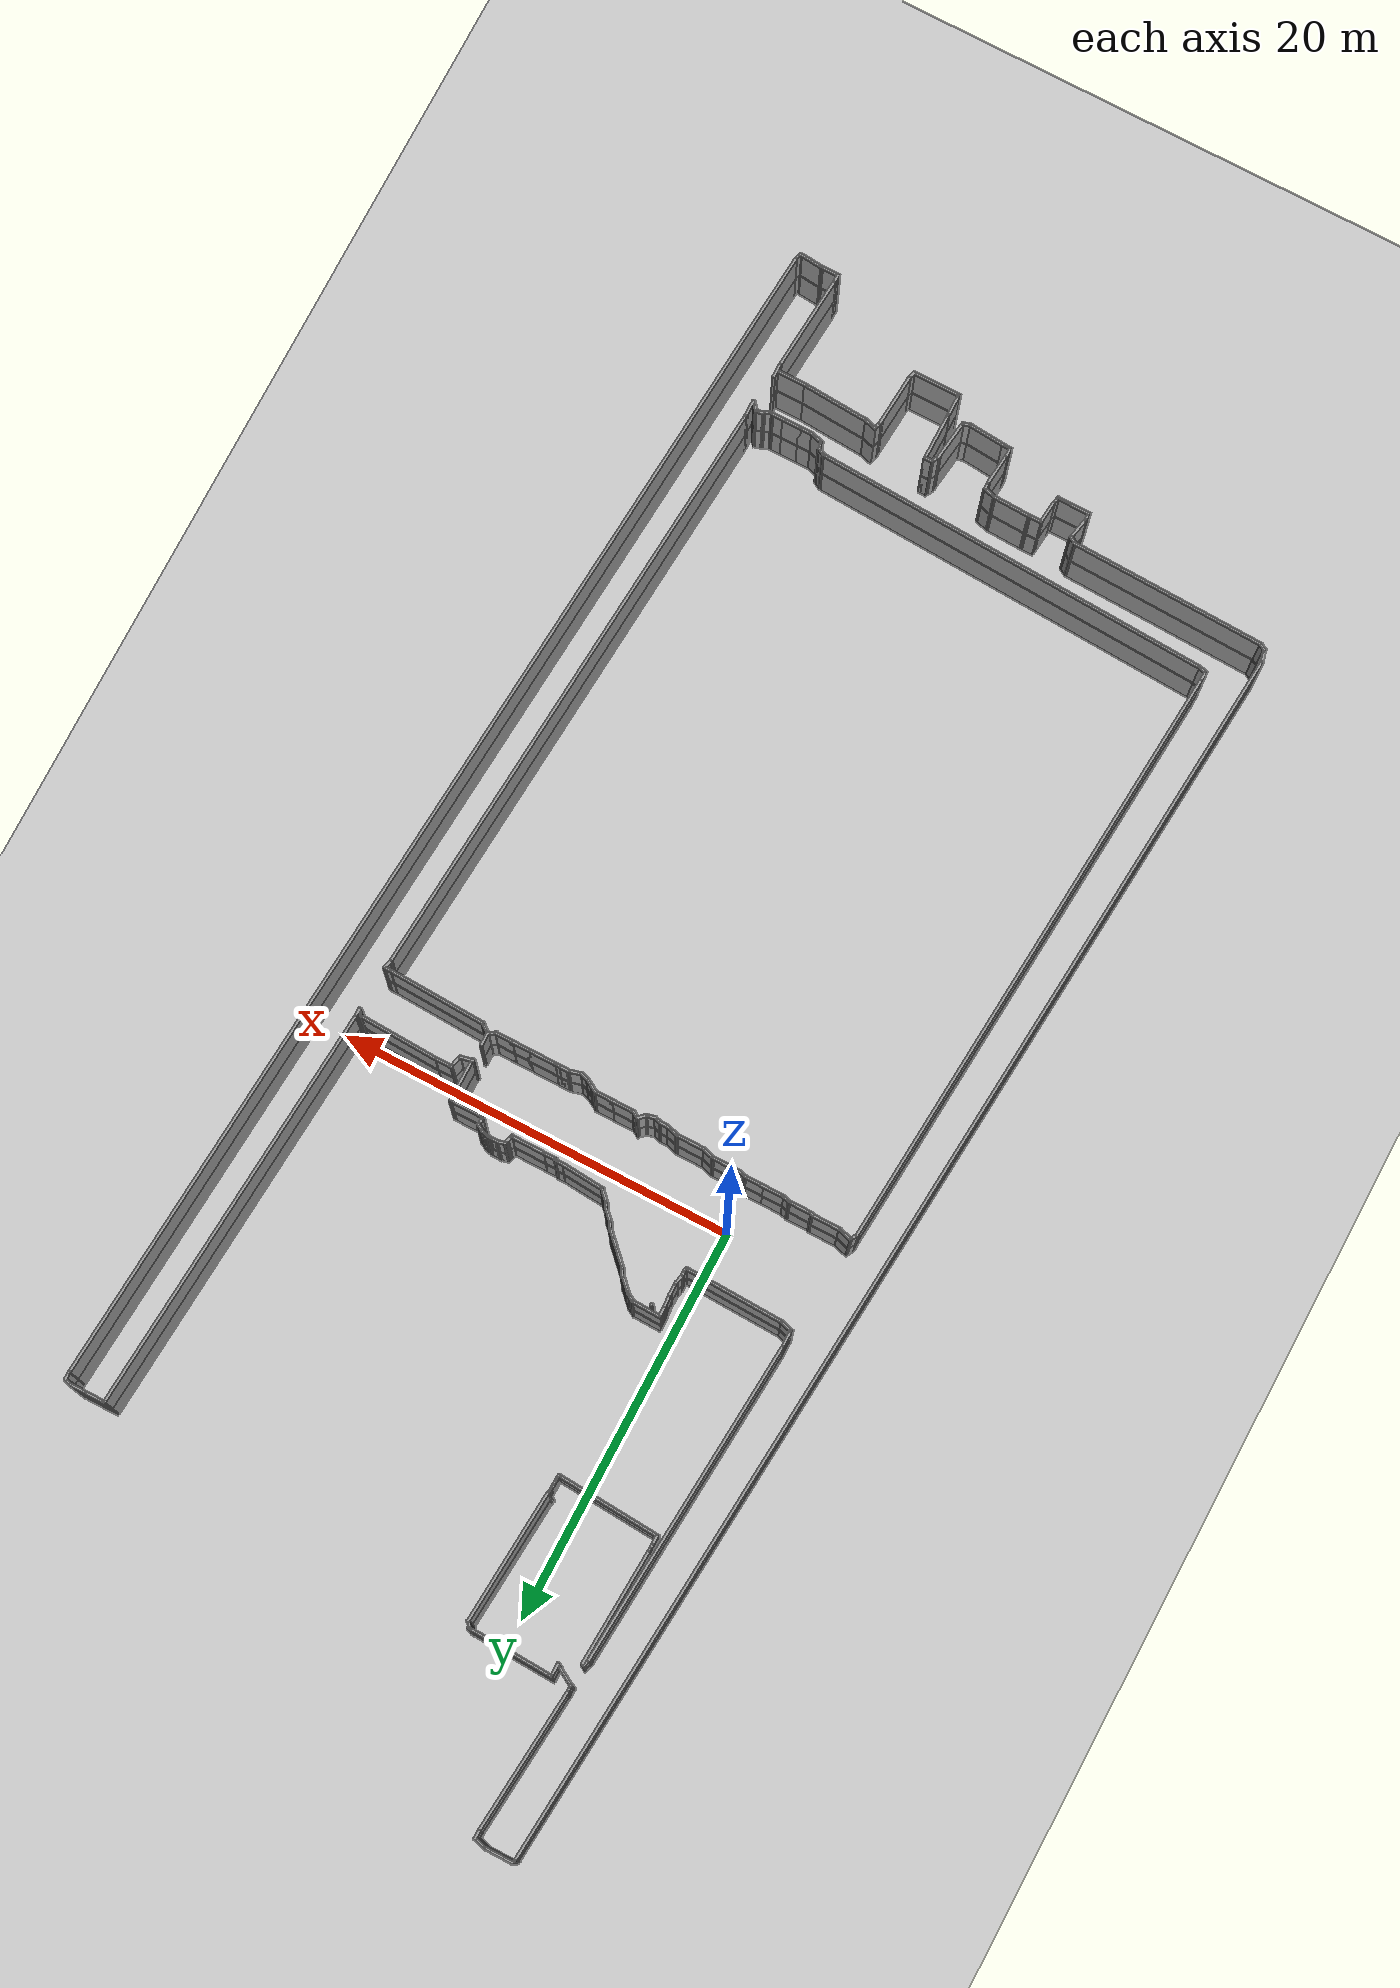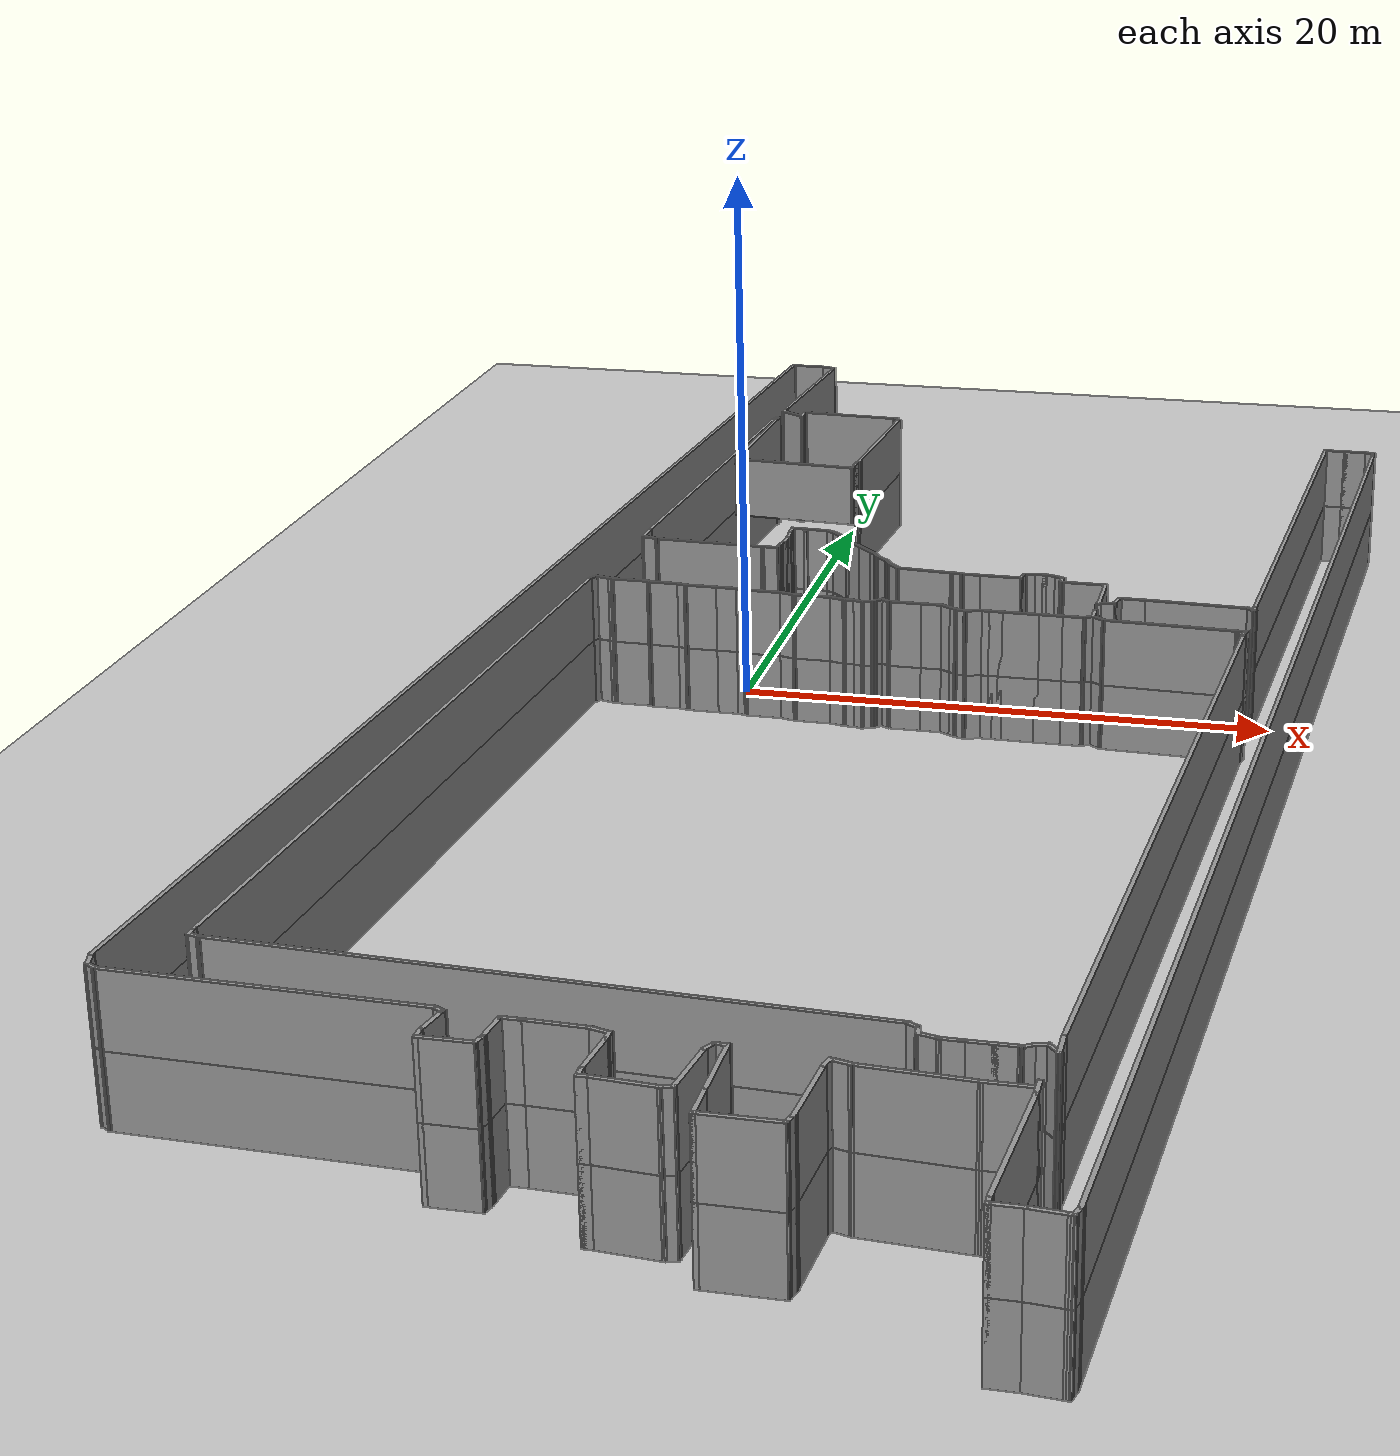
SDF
<sdf version="1.7">
 <world name="default">
  <light name="sun" type="directional">
   <pose>0 0 10 0 -0 0</pose>
   <diffuse>0.8 0.8 0.8 1</diffuse>
   <specular>0.2 0.2 0.2 1</specular>
   <attenuation>
    <range>1000</range>
    <constant>0.9</constant>
    <linear>0.01</linear>
    <quadratic>0.001</quadratic>
   </attenuation>
   <direction>-0.5 0.1 -0.9</direction>
   <spot><inner_angle>0</inner_angle><outer_angle>0</outer_angle><falloff>0</falloff></spot>
  </light>
  <model name="ground_plane">
   <static>1</static>
   <link name="link">
    <collision name="collision">
     <geometry><plane><normal>0 0 1</normal><size>100 100</size></plane></geometry>
     <surface>
      <contact><collide_bitmask>65535</collide_bitmask></contact>
      <friction><ode><mu>100</mu><mu2>50</mu2></ode></friction>
     </surface>
    </collision>
    <visual name="visual">
     <cast_shadows>0</cast_shadows>
     <geometry><plane><normal>0 0 1</normal><size>100 100</size></plane></geometry>
     <material>
      <script><uri>file://media/materials/scripts/gazebo.material</uri><name>Gazebo/Grey</name></script>
     </material>
    </visual>
   </link>
  </model>
  <gravity>0 0 -9.8</gravity>
  <magnetic_field>6e-06 2.3e-05 -4.2e-05</magnetic_field>
  <atmosphere type="adiabatic"/>
  <physics type="ode">
   <max_step_size>0.001</max_step_size>
   <real_time_factor>1</real_time_factor>
   <real_time_update_rate>1000</real_time_update_rate>
  </physics>
  <scene><ambient>0.4 0.4 0.4 1</ambient><background>0.7 0.7 0.7 1</background><shadows>1</shadows></scene>
  <spherical_coordinates>
   <surface_model>EARTH_WGS84</surface_model>
   <latitude_deg>0</latitude_deg>
   <longitude_deg>0</longitude_deg>
   <elevation>0</elevation>
   <heading_deg>0</heading_deg>
  </spherical_coordinates>
  <model name="EnvDC01">
   <link name="Floor_0">
    <pose>0 0 2.5 0 -0 0</pose>
    <inertial>
     <mass>1</mass>
     <inertia><ixx>1</ixx><ixy>0</ixy><ixz>0</ixz><iyy>1</iyy><iyz>0</iyz><izz>1</izz></inertia>
    </inertial>
    <collision name="Floor_0_Collision">
     <pose>0 0 0.05 0 -0 0</pose>
     <geometry><box><size>32.7353 71.8899 0.1</size></box></geometry>
     <surface>
      <friction>
       <ode><mu>1</mu><mu2>1</mu2><fdir1>0 0 0</fdir1><slip1>0</slip1><slip2>0</slip2></ode>
       <torsional>
        <coefficient>1</coefficient>
        <patch_radius>0</patch_radius>
        <surface_radius>0</surface_radius>
        <use_patch_radius>1</use_patch_radius>
        <ode><slip>0</slip></ode>
       </torsional>
      </friction>
      <bounce><restitution_coefficient>0</restitution_coefficient><threshold>1e+06</threshold></bounce>
      <contact>
       <collide_without_contact>0</collide_without_contact>
       <collide_without_contact_bitmask>1</collide_without_contact_bitmask>
       <collide_bitmask>1</collide_bitmask>
       <ode>
        <soft_cfm>0</soft_cfm>
        <soft_erp>0.2</soft_erp>
        <kp>1e+13</kp>
        <kd>1</kd>
        <max_vel>0.01</max_vel>
        <min_depth>0</min_depth>
       </ode>
       <bullet>
        <split_impulse>1</split_impulse>
        <split_impulse_penetration_threshold>-0.01</split_impulse_penetration_threshold>
        <soft_cfm>0</soft_cfm>
        <soft_erp>0.2</soft_erp>
        <kp>1e+13</kp>
        <kd>1</kd>
       </bullet>
      </contact>
     </surface>
    </collision>
   </link>
   <link name="Wall_100">
    <pose>-5.32892 11.2593 0 0 -0 0</pose>
    <visual name="Wall_100_Visual">
     <pose>0 0 1.25 0 -0 0</pose>
     <geometry><box><size>0.15 0.15 2.5</size></box></geometry>
     <material>
      <script><uri>file://media/materials/scripts/gazebo.material</uri><name>Gazebo/Grey</name></script>
      <ambient>1 1 1 1</ambient>
      <shader type="pixel"/>
     </material>
     <meta><layer>0</layer></meta>
    </visual>
    <collision name="Wall_100_Collision">
     <pose>0 0 1.25 0 -0 0</pose>
     <geometry><box><size>0.15 0.15 2.5</size></box></geometry>
     <surface>
      <friction>
       <ode><mu>1</mu><mu2>1</mu2><fdir1>0 0 0</fdir1><slip1>0</slip1><slip2>0</slip2></ode>
       <torsional>
        <coefficient>1</coefficient>
        <patch_radius>0</patch_radius>
        <surface_radius>0</surface_radius>
        <use_patch_radius>1</use_patch_radius>
        <ode><slip>0</slip></ode>
       </torsional>
      </friction>
      <bounce><restitution_coefficient>0</restitution_coefficient><threshold>1e+06</threshold></bounce>
      <contact>
       <collide_without_contact>0</collide_without_contact>
       <collide_without_contact_bitmask>1</collide_without_contact_bitmask>
       <collide_bitmask>1</collide_bitmask>
       <ode>
        <soft_cfm>0</soft_cfm>
        <soft_erp>0.2</soft_erp>
        <kp>1e+13</kp>
        <kd>1</kd>
        <max_vel>0.01</max_vel>
        <min_depth>0</min_depth>
       </ode>
       <bullet>
        <split_impulse>1</split_impulse>
        <split_impulse_penetration_threshold>-0.01</split_impulse_penetration_threshold>
        <soft_cfm>0</soft_cfm>
        <soft_erp>0.2</soft_erp>
        <kp>1e+13</kp>
        <kd>1</kd>
       </bullet>
      </contact>
     </surface>
    </collision>
   </link>
   <link name="Wall_102">
    <pose>-5.88941 11.3173 0 0 0 -1.5708</pose>
    <visual name="Wall_102_Visual">
     <pose>0 0 1.25 0 -0 0</pose>
     <geometry><box><size>0.5 0.15 2.5</size></box></geometry>
     <material>
      <script><uri>file://media/materials/scripts/gazebo.material</uri><name>Gazebo/Grey</name></script>
      <ambient>1 1 1 1</ambient>
      <shader type="pixel"/>
     </material>
     <meta><layer>0</layer></meta>
    </visual>
    <collision name="Wall_102_Collision">
     <pose>0 0 1.25 0 -0 0</pose>
     <geometry><box><size>0.5 0.15 2.5</size></box></geometry>
     <surface>
      <friction>
       <ode><mu>1</mu><mu2>1</mu2><fdir1>0 0 0</fdir1><slip1>0</slip1><slip2>0</slip2></ode>
       <torsional>
        <coefficient>1</coefficient>
        <patch_radius>0</patch_radius>
        <surface_radius>0</surface_radius>
        <use_patch_radius>1</use_patch_radius>
        <ode><slip>0</slip></ode>
       </torsional>
      </friction>
      <bounce><restitution_coefficient>0</restitution_coefficient><threshold>1e+06</threshold></bounce>
      <contact>
       <collide_without_contact>0</collide_without_contact>
       <collide_without_contact_bitmask>1</collide_without_contact_bitmask>
       <collide_bitmask>1</collide_bitmask>
       <ode>
        <soft_cfm>0</soft_cfm>
        <soft_erp>0.2</soft_erp>
        <kp>1e+13</kp>
        <kd>1</kd>
        <max_vel>0.01</max_vel>
        <min_depth>0</min_depth>
       </ode>
       <bullet>
        <split_impulse>1</split_impulse>
        <split_impulse_penetration_threshold>-0.01</split_impulse_penetration_threshold>
        <soft_cfm>0</soft_cfm>
        <soft_erp>0.2</soft_erp>
        <kp>1e+13</kp>
        <kd>1</kd>
       </bullet>
      </contact>
     </surface>
    </collision>
   </link>
   <link name="Wall_103">
    <pose>-5.86023 10.8116 0 0 0 -1.48755</pose>
    <visual name="Wall_103_Visual">
     <pose>0 0 1.25 0 -0 0</pose>
     <geometry><box><size>0.813803 0.15 2.5</size></box></geometry>
     <material>
      <script><uri>file://media/materials/scripts/gazebo.material</uri><name>Gazebo/Grey</name></script>
      <ambient>1 1 1 1</ambient>
      <shader type="pixel"/>
     </material>
     <meta><layer>0</layer></meta>
    </visual>
    <collision name="Wall_103_Collision">
     <pose>0 0 1.25 0 -0 0</pose>
     <geometry><box><size>0.813803 0.15 2.5</size></box></geometry>
     <surface>
      <friction>
       <ode><mu>1</mu><mu2>1</mu2><fdir1>0 0 0</fdir1><slip1>0</slip1><slip2>0</slip2></ode>
       <torsional>
        <coefficient>1</coefficient>
        <patch_radius>0</patch_radius>
        <surface_radius>0</surface_radius>
        <use_patch_radius>1</use_patch_radius>
        <ode><slip>0</slip></ode>
       </torsional>
      </friction>
      <bounce><restitution_coefficient>0</restitution_coefficient><threshold>1e+06</threshold></bounce>
      <contact>
       <collide_without_contact>0</collide_without_contact>
       <collide_without_contact_bitmask>1</collide_without_contact_bitmask>
       <collide_bitmask>1</collide_bitmask>
       <ode>
        <soft_cfm>0</soft_cfm>
        <soft_erp>0.2</soft_erp>
        <kp>1e+13</kp>
        <kd>1</kd>
        <max_vel>0.01</max_vel>
        <min_depth>0</min_depth>
       </ode>
       <bullet>
        <split_impulse>1</split_impulse>
        <split_impulse_penetration_threshold>-0.01</split_impulse_penetration_threshold>
        <soft_cfm>0</soft_cfm>
        <soft_erp>0.2</soft_erp>
        <kp>1e+13</kp>
        <kd>1</kd>
       </bullet>
      </contact>
     </surface>
    </collision>
   </link>
   <link name="Wall_104">
    <pose>-5.83264 10.1793 0 0 0 -1.5708</pose>
    <visual name="Wall_104_Visual">
     <pose>0 0 1.25 0 -0 0</pose>
     <geometry><box><size>0.75 0.15 2.5</size></box></geometry>
     <material>
      <script><uri>file://media/materials/scripts/gazebo.material</uri><name>Gazebo/Grey</name></script>
      <ambient>1 1 1 1</ambient>
      <shader type="pixel"/>
     </material>
     <meta><layer>0</layer></meta>
    </visual>
    <collision name="Wall_104_Collision">
     <pose>0 0 1.25 0 -0 0</pose>
     <geometry><box><size>0.75 0.15 2.5</size></box></geometry>
     <surface>
      <friction>
       <ode><mu>1</mu><mu2>1</mu2><fdir1>0 0 0</fdir1><slip1>0</slip1><slip2>0</slip2></ode>
       <torsional>
        <coefficient>1</coefficient>
        <patch_radius>0</patch_radius>
        <surface_radius>0</surface_radius>
        <use_patch_radius>1</use_patch_radius>
        <ode><slip>0</slip></ode>
       </torsional>
      </friction>
      <bounce><restitution_coefficient>0</restitution_coefficient><threshold>1e+06</threshold></bounce>
      <contact>
       <collide_without_contact>0</collide_without_contact>
       <collide_without_contact_bitmask>1</collide_without_contact_bitmask>
       <collide_bitmask>1</collide_bitmask>
       <ode>
        <soft_cfm>0</soft_cfm>
        <soft_erp>0.2</soft_erp>
        <kp>1e+13</kp>
        <kd>1</kd>
        <max_vel>0.01</max_vel>
        <min_depth>0</min_depth>
       </ode>
       <bullet>
        <split_impulse>1</split_impulse>
        <split_impulse_penetration_threshold>-0.01</split_impulse_penetration_threshold>
        <soft_cfm>0</soft_cfm>
        <soft_erp>0.2</soft_erp>
        <kp>1e+13</kp>
        <kd>1</kd>
       </bullet>
      </contact>
     </surface>
    </collision>
   </link>
   <link name="Wall_105">
    <pose>-5.87793 9.70942 0 0 0 -1.83143</pose>
    <visual name="Wall_105_Visual">
     <pose>0 0 1.25 0 -0 0</pose>
     <geometry><box><size>0.501524 0.15 2.5</size></box></geometry>
     <material>
      <script><uri>file://media/materials/scripts/gazebo.material</uri><name>Gazebo/Grey</name></script>
      <ambient>1 1 1 1</ambient>
      <shader type="pixel"/>
     </material>
     <meta><layer>0</layer></meta>
    </visual>
    <collision name="Wall_105_Collision">
     <pose>0 0 1.25 0 -0 0</pose>
     <geometry><box><size>0.501524 0.15 2.5</size></box></geometry>
     <surface>
      <friction>
       <ode><mu>1</mu><mu2>1</mu2><fdir1>0 0 0</fdir1><slip1>0</slip1><slip2>0</slip2></ode>
       <torsional>
        <coefficient>1</coefficient>
        <patch_radius>0</patch_radius>
        <surface_radius>0</surface_radius>
        <use_patch_radius>1</use_patch_radius>
        <ode><slip>0</slip></ode>
       </torsional>
      </friction>
      <bounce><restitution_coefficient>0</restitution_coefficient><threshold>1e+06</threshold></bounce>
      <contact>
       <collide_without_contact>0</collide_without_contact>
       <collide_without_contact_bitmask>1</collide_without_contact_bitmask>
       <collide_bitmask>1</collide_bitmask>
       <ode>
        <soft_cfm>0</soft_cfm>
        <soft_erp>0.2</soft_erp>
        <kp>1e+13</kp>
        <kd>1</kd>
        <max_vel>0.01</max_vel>
        <min_depth>0</min_depth>
       </ode>
       <bullet>
        <split_impulse>1</split_impulse>
        <split_impulse_penetration_threshold>-0.01</split_impulse_penetration_threshold>
        <soft_cfm>0</soft_cfm>
        <soft_erp>0.2</soft_erp>
        <kp>1e+13</kp>
        <kd>1</kd>
       </bullet>
      </contact>
     </surface>
    </collision>
   </link>
   <link name="Wall_106">
    <pose>-5.92322 9.3646 0 0 0 -1.5708</pose>
    <visual name="Wall_106_Visual">
     <pose>0 0 1.25 0 -0 0</pose>
     <geometry><box><size>0.5 0.15 2.5</size></box></geometry>
     <material>
      <script><uri>file://media/materials/scripts/gazebo.material</uri><name>Gazebo/Grey</name></script>
      <ambient>1 1 1 1</ambient>
      <shader type="pixel"/>
     </material>
     <meta><layer>0</layer></meta>
    </visual>
    <collision name="Wall_106_Collision">
     <pose>0 0 1.25 0 -0 0</pose>
     <geometry><box><size>0.5 0.15 2.5</size></box></geometry>
     <surface>
      <friction>
       <ode><mu>1</mu><mu2>1</mu2><fdir1>0 0 0</fdir1><slip1>0</slip1><slip2>0</slip2></ode>
       <torsional>
        <coefficient>1</coefficient>
        <patch_radius>0</patch_radius>
        <surface_radius>0</surface_radius>
        <use_patch_radius>1</use_patch_radius>
        <ode><slip>0</slip></ode>
       </torsional>
      </friction>
      <bounce><restitution_coefficient>0</restitution_coefficient><threshold>1e+06</threshold></bounce>
      <contact>
       <collide_without_contact>0</collide_without_contact>
       <collide_without_contact_bitmask>1</collide_without_contact_bitmask>
       <collide_bitmask>1</collide_bitmask>
       <ode>
        <soft_cfm>0</soft_cfm>
        <soft_erp>0.2</soft_erp>
        <kp>1e+13</kp>
        <kd>1</kd>
        <max_vel>0.01</max_vel>
        <min_depth>0</min_depth>
       </ode>
       <bullet>
        <split_impulse>1</split_impulse>
        <split_impulse_penetration_threshold>-0.01</split_impulse_penetration_threshold>
        <soft_cfm>0</soft_cfm>
        <soft_erp>0.2</soft_erp>
        <kp>1e+13</kp>
        <kd>1</kd>
       </bullet>
      </contact>
     </surface>
    </collision>
   </link>
   <link name="Wall_107">
    <pose>-5.93616 9.1413 0 0 0 -1.8326</pose>
    <visual name="Wall_107_Visual">
     <pose>0 0 1.25 0 -0 0</pose>
     <geometry><box><size>0.25 0.15 2.5</size></box></geometry>
     <material>
      <script><uri>file://media/materials/scripts/gazebo.material</uri><name>Gazebo/Grey</name></script>
      <ambient>1 1 1 1</ambient>
      <shader type="pixel"/>
     </material>
     <meta><layer>0</layer></meta>
    </visual>
    <collision name="Wall_107_Collision">
     <pose>0 0 1.25 0 -0 0</pose>
     <geometry><box><size>0.25 0.15 2.5</size></box></geometry>
     <surface>
      <friction>
       <ode><mu>1</mu><mu2>1</mu2><fdir1>0 0 0</fdir1><slip1>0</slip1><slip2>0</slip2></ode>
       <torsional>
        <coefficient>1</coefficient>
        <patch_radius>0</patch_radius>
        <surface_radius>0</surface_radius>
        <use_patch_radius>1</use_patch_radius>
        <ode><slip>0</slip></ode>
       </torsional>
      </friction>
      <bounce><restitution_coefficient>0</restitution_coefficient><threshold>1e+06</threshold></bounce>
      <contact>
       <collide_without_contact>0</collide_without_contact>
       <collide_without_contact_bitmask>1</collide_without_contact_bitmask>
       <collide_bitmask>1</collide_bitmask>
       <ode>
        <soft_cfm>0</soft_cfm>
        <soft_erp>0.2</soft_erp>
        <kp>1e+13</kp>
        <kd>1</kd>
        <max_vel>0.01</max_vel>
        <min_depth>0</min_depth>
       </ode>
       <bullet>
        <split_impulse>1</split_impulse>
        <split_impulse_penetration_threshold>-0.01</split_impulse_penetration_threshold>
        <soft_cfm>0</soft_cfm>
        <soft_erp>0.2</soft_erp>
        <kp>1e+13</kp>
        <kd>1</kd>
       </bullet>
      </contact>
     </surface>
    </collision>
   </link>
   <link name="Wall_108">
    <pose>-6.24911 9.09509 0 0 -0 3.13464</pose>
    <visual name="Wall_108_Visual">
     <pose>0 0 1.25 0 -0 0</pose>
     <geometry><box><size>0.75 0.15 2.5</size></box></geometry>
     <material>
      <script><uri>file://media/materials/scripts/gazebo.material</uri><name>Gazebo/Grey</name></script>
      <ambient>1 1 1 1</ambient>
      <shader type="pixel"/>
     </material>
     <meta><layer>0</layer></meta>
    </visual>
    <collision name="Wall_108_Collision">
     <pose>0 0 1.25 0 -0 0</pose>
     <geometry><box><size>0.75 0.15 2.5</size></box></geometry>
     <surface>
      <friction>
       <ode><mu>1</mu><mu2>1</mu2><fdir1>0 0 0</fdir1><slip1>0</slip1><slip2>0</slip2></ode>
       <torsional>
        <coefficient>1</coefficient>
        <patch_radius>0</patch_radius>
        <surface_radius>0</surface_radius>
        <use_patch_radius>1</use_patch_radius>
        <ode><slip>0</slip></ode>
       </torsional>
      </friction>
      <bounce><restitution_coefficient>0</restitution_coefficient><threshold>1e+06</threshold></bounce>
      <contact>
       <collide_without_contact>0</collide_without_contact>
       <collide_without_contact_bitmask>1</collide_without_contact_bitmask>
       <collide_bitmask>1</collide_bitmask>
       <ode>
        <soft_cfm>0</soft_cfm>
        <soft_erp>0.2</soft_erp>
        <kp>1e+13</kp>
        <kd>1</kd>
        <max_vel>0.01</max_vel>
        <min_depth>0</min_depth>
       </ode>
       <bullet>
        <split_impulse>1</split_impulse>
        <split_impulse_penetration_threshold>-0.01</split_impulse_penetration_threshold>
        <soft_cfm>0</soft_cfm>
        <soft_erp>0.2</soft_erp>
        <kp>1e+13</kp>
        <kd>1</kd>
       </bullet>
      </contact>
     </surface>
    </collision>
   </link>
   <link name="Wall_111">
    <pose>-8.68398 9.16284 0 0 -0 3.11085</pose>
    <visual name="Wall_111_Visual">
     <pose>0 0 1.25 0 -0 0</pose>
     <geometry><box><size>4.42177 0.15 2.5</size></box></geometry>
     <material>
      <script><uri>file://media/materials/scripts/gazebo.material</uri><name>Gazebo/Grey</name></script>
      <ambient>1 1 1 1</ambient>
      <shader type="pixel"/>
     </material>
     <meta><layer>0</layer></meta>
    </visual>
    <collision name="Wall_111_Collision">
     <pose>0 0 1.25 0 -0 0</pose>
     <geometry><box><size>4.42177 0.15 2.5</size></box></geometry>
     <surface>
      <friction>
       <ode><mu>1</mu><mu2>1</mu2><fdir1>0 0 0</fdir1><slip1>0</slip1><slip2>0</slip2></ode>
       <torsional>
        <coefficient>1</coefficient>
        <patch_radius>0</patch_radius>
        <surface_radius>0</surface_radius>
        <use_patch_radius>1</use_patch_radius>
        <ode><slip>0</slip></ode>
       </torsional>
      </friction>
      <bounce><restitution_coefficient>0</restitution_coefficient><threshold>1e+06</threshold></bounce>
      <contact>
       <collide_without_contact>0</collide_without_contact>
       <collide_without_contact_bitmask>1</collide_without_contact_bitmask>
       <collide_bitmask>1</collide_bitmask>
       <ode>
        <soft_cfm>0</soft_cfm>
        <soft_erp>0.2</soft_erp>
        <kp>1e+13</kp>
        <kd>1</kd>
        <max_vel>0.01</max_vel>
        <min_depth>0</min_depth>
       </ode>
       <bullet>
        <split_impulse>1</split_impulse>
        <split_impulse_penetration_threshold>-0.01</split_impulse_penetration_threshold>
        <soft_cfm>0</soft_cfm>
        <soft_erp>0.2</soft_erp>
        <kp>1e+13</kp>
        <kd>1</kd>
       </bullet>
      </contact>
     </surface>
    </collision>
   </link>
   <link name="Wall_112">
    <pose>-11.1086 9.30614 0 0 -0 2.87979</pose>
    <visual name="Wall_112_Visual">
     <pose>0 0 1.25 0 -0 0</pose>
     <geometry><box><size>0.75 0.15 2.5</size></box></geometry>
     <material>
      <script><uri>file://media/materials/scripts/gazebo.material</uri><name>Gazebo/Grey</name></script>
      <ambient>1 1 1 1</ambient>
      <shader type="pixel"/>
     </material>
     <meta><layer>0</layer></meta>
    </visual>
    <collision name="Wall_112_Collision">
     <pose>0 0 1.25 0 -0 0</pose>
     <geometry><box><size>0.75 0.15 2.5</size></box></geometry>
     <surface>
      <friction>
       <ode><mu>1</mu><mu2>1</mu2><fdir1>0 0 0</fdir1><slip1>0</slip1><slip2>0</slip2></ode>
       <torsional>
        <coefficient>1</coefficient>
        <patch_radius>0</patch_radius>
        <surface_radius>0</surface_radius>
        <use_patch_radius>1</use_patch_radius>
        <ode><slip>0</slip></ode>
       </torsional>
      </friction>
      <bounce><restitution_coefficient>0</restitution_coefficient><threshold>1e+06</threshold></bounce>
      <contact>
       <collide_without_contact>0</collide_without_contact>
       <collide_without_contact_bitmask>1</collide_without_contact_bitmask>
       <collide_bitmask>1</collide_bitmask>
       <ode>
        <soft_cfm>0</soft_cfm>
        <soft_erp>0.2</soft_erp>
        <kp>1e+13</kp>
        <kd>1</kd>
        <max_vel>0.01</max_vel>
        <min_depth>0</min_depth>
       </ode>
       <bullet>
        <split_impulse>1</split_impulse>
        <split_impulse_penetration_threshold>-0.01</split_impulse_penetration_threshold>
        <soft_cfm>0</soft_cfm>
        <soft_erp>0.2</soft_erp>
        <kp>1e+13</kp>
        <kd>1</kd>
       </bullet>
      </contact>
     </surface>
    </collision>
   </link>
   <link name="Wall_114">
    <pose>-10.2177 26.6696 0 0 0 -1.8326</pose>
    <visual name="Wall_114_Visual">
     <pose>0 0 1.25 0 -0 0</pose>
     <geometry><box><size>0.5 0.15 2.5</size></box></geometry>
     <material>
      <script><uri>file://media/materials/scripts/gazebo.material</uri><name>Gazebo/Grey</name></script>
      <ambient>1 1 1 1</ambient>
      <shader type="pixel"/>
     </material>
     <meta><layer>0</layer></meta>
    </visual>
    <collision name="Wall_114_Collision">
     <pose>0 0 1.25 0 -0 0</pose>
     <geometry><box><size>0.5 0.15 2.5</size></box></geometry>
     <surface>
      <friction>
       <ode><mu>1</mu><mu2>1</mu2><fdir1>0 0 0</fdir1><slip1>0</slip1><slip2>0</slip2></ode>
       <torsional>
        <coefficient>1</coefficient>
        <patch_radius>0</patch_radius>
        <surface_radius>0</surface_radius>
        <use_patch_radius>1</use_patch_radius>
        <ode><slip>0</slip></ode>
       </torsional>
      </friction>
      <bounce><restitution_coefficient>0</restitution_coefficient><threshold>1e+06</threshold></bounce>
      <contact>
       <collide_without_contact>0</collide_without_contact>
       <collide_without_contact_bitmask>1</collide_without_contact_bitmask>
       <collide_bitmask>1</collide_bitmask>
       <ode>
        <soft_cfm>0</soft_cfm>
        <soft_erp>0.2</soft_erp>
        <kp>1e+13</kp>
        <kd>1</kd>
        <max_vel>0.01</max_vel>
        <min_depth>0</min_depth>
       </ode>
       <bullet>
        <split_impulse>1</split_impulse>
        <split_impulse_penetration_threshold>-0.01</split_impulse_penetration_threshold>
        <soft_cfm>0</soft_cfm>
        <soft_erp>0.2</soft_erp>
        <kp>1e+13</kp>
        <kd>1</kd>
       </bullet>
      </contact>
     </surface>
    </collision>
   </link>
   <link name="Wall_115">
    <pose>-10.8307 18.3672 0 0 0 -1.64048</pose>
    <visual name="Wall_115_Visual">
     <pose>0 0 1.25 0 -0 0</pose>
     <geometry><box><size>16.4563 0.15 2.5</size></box></geometry>
     <material>
      <script><uri>file://media/materials/scripts/gazebo.material</uri><name>Gazebo/Grey</name></script>
      <ambient>1 1 1 1</ambient>
      <shader type="pixel"/>
     </material>
     <meta><layer>0</layer></meta>
    </visual>
    <collision name="Wall_115_Collision">
     <pose>0 0 1.25 0 -0 0</pose>
     <geometry><box><size>16.4563 0.15 2.5</size></box></geometry>
     <surface>
      <friction>
       <ode><mu>1</mu><mu2>1</mu2><fdir1>0 0 0</fdir1><slip1>0</slip1><slip2>0</slip2></ode>
       <torsional>
        <coefficient>1</coefficient>
        <patch_radius>0</patch_radius>
        <surface_radius>0</surface_radius>
        <use_patch_radius>1</use_patch_radius>
        <ode><slip>0</slip></ode>
       </torsional>
      </friction>
      <bounce><restitution_coefficient>0</restitution_coefficient><threshold>1e+06</threshold></bounce>
      <contact>
       <collide_without_contact>0</collide_without_contact>
       <collide_without_contact_bitmask>1</collide_without_contact_bitmask>
       <collide_bitmask>1</collide_bitmask>
       <ode>
        <soft_cfm>0</soft_cfm>
        <soft_erp>0.2</soft_erp>
        <kp>1e+13</kp>
        <kd>1</kd>
        <max_vel>0.01</max_vel>
        <min_depth>0</min_depth>
       </ode>
       <bullet>
        <split_impulse>1</split_impulse>
        <split_impulse_penetration_threshold>-0.01</split_impulse_penetration_threshold>
        <soft_cfm>0</soft_cfm>
        <soft_erp>0.2</soft_erp>
        <kp>1e+13</kp>
        <kd>1</kd>
       </bullet>
      </contact>
     </surface>
    </collision>
   </link>
   <link name="Wall_116">
    <pose>-11.3984 9.80879 0 0 0 -1.5708</pose>
    <visual name="Wall_116_Visual">
     <pose>0 0 1.25 0 -0 0</pose>
     <geometry><box><size>1 0.15 2.5</size></box></geometry>
     <material>
      <script><uri>file://media/materials/scripts/gazebo.material</uri><name>Gazebo/Grey</name></script>
      <ambient>1 1 1 1</ambient>
      <shader type="pixel"/>
     </material>
     <meta><layer>0</layer></meta>
    </visual>
    <collision name="Wall_116_Collision">
     <pose>0 0 1.25 0 -0 0</pose>
     <geometry><box><size>1 0.15 2.5</size></box></geometry>
     <surface>
      <friction>
       <ode><mu>1</mu><mu2>1</mu2><fdir1>0 0 0</fdir1><slip1>0</slip1><slip2>0</slip2></ode>
       <torsional>
        <coefficient>1</coefficient>
        <patch_radius>0</patch_radius>
        <surface_radius>0</surface_radius>
        <use_patch_radius>1</use_patch_radius>
        <ode><slip>0</slip></ode>
       </torsional>
      </friction>
      <bounce><restitution_coefficient>0</restitution_coefficient><threshold>1e+06</threshold></bounce>
      <contact>
       <collide_without_contact>0</collide_without_contact>
       <collide_without_contact_bitmask>1</collide_without_contact_bitmask>
       <collide_bitmask>1</collide_bitmask>
       <ode>
        <soft_cfm>0</soft_cfm>
        <soft_erp>0.2</soft_erp>
        <kp>1e+13</kp>
        <kd>1</kd>
        <max_vel>0.01</max_vel>
        <min_depth>0</min_depth>
       </ode>
       <bullet>
        <split_impulse>1</split_impulse>
        <split_impulse_penetration_threshold>-0.01</split_impulse_penetration_threshold>
        <soft_cfm>0</soft_cfm>
        <soft_erp>0.2</soft_erp>
        <kp>1e+13</kp>
        <kd>1</kd>
       </bullet>
      </contact>
     </surface>
    </collision>
   </link>
   <link name="Wall_118">
    <pose>-10.0854 28.0428 0 0 -0 1.5708</pose>
    <visual name="Wall_118_Visual">
     <pose>0 0 1.25 0 -0 0</pose>
     <geometry><box><size>0.5 0.15 2.5</size></box></geometry>
     <material>
      <script><uri>file://media/materials/scripts/gazebo.material</uri><name>Gazebo/Grey</name></script>
      <ambient>1 1 1 1</ambient>
      <shader type="pixel"/>
     </material>
     <meta><layer>0</layer></meta>
    </visual>
    <collision name="Wall_118_Collision">
     <pose>0 0 1.25 0 -0 0</pose>
     <geometry><box><size>0.5 0.15 2.5</size></box></geometry>
     <surface>
      <friction>
       <ode><mu>1</mu><mu2>1</mu2><fdir1>0 0 0</fdir1><slip1>0</slip1><slip2>0</slip2></ode>
       <torsional>
        <coefficient>1</coefficient>
        <patch_radius>0</patch_radius>
        <surface_radius>0</surface_radius>
        <use_patch_radius>1</use_patch_radius>
        <ode><slip>0</slip></ode>
       </torsional>
      </friction>
      <bounce><restitution_coefficient>0</restitution_coefficient><threshold>1e+06</threshold></bounce>
      <contact>
       <collide_without_contact>0</collide_without_contact>
       <collide_without_contact_bitmask>1</collide_without_contact_bitmask>
       <collide_bitmask>1</collide_bitmask>
       <ode>
        <soft_cfm>0</soft_cfm>
        <soft_erp>0.2</soft_erp>
        <kp>1e+13</kp>
        <kd>1</kd>
        <max_vel>0.01</max_vel>
        <min_depth>0</min_depth>
       </ode>
       <bullet>
        <split_impulse>1</split_impulse>
        <split_impulse_penetration_threshold>-0.01</split_impulse_penetration_threshold>
        <soft_cfm>0</soft_cfm>
        <soft_erp>0.2</soft_erp>
        <kp>1e+13</kp>
        <kd>1</kd>
       </bullet>
      </contact>
     </surface>
    </collision>
   </link>
   <link name="Wall_119">
    <pose>-9.78492 31.7757 0 0 -0 1.48653</pose>
    <visual name="Wall_119_Visual">
     <pose>0 0 1.25 0 -0 0</pose>
     <geometry><box><size>7.29114 0.15 2.5</size></box></geometry>
     <material>
      <script><uri>file://media/materials/scripts/gazebo.material</uri><name>Gazebo/Grey</name></script>
      <ambient>1 1 1 1</ambient>
      <shader type="pixel"/>
     </material>
     <meta><layer>0</layer></meta>
    </visual>
    <collision name="Wall_119_Collision">
     <pose>0 0 1.25 0 -0 0</pose>
     <geometry><box><size>7.29114 0.15 2.5</size></box></geometry>
     <surface>
      <friction>
       <ode><mu>1</mu><mu2>1</mu2><fdir1>0 0 0</fdir1><slip1>0</slip1><slip2>0</slip2></ode>
       <torsional>
        <coefficient>1</coefficient>
        <patch_radius>0</patch_radius>
        <surface_radius>0</surface_radius>
        <use_patch_radius>1</use_patch_radius>
        <ode><slip>0</slip></ode>
       </torsional>
      </friction>
      <bounce><restitution_coefficient>0</restitution_coefficient><threshold>1e+06</threshold></bounce>
      <contact>
       <collide_without_contact>0</collide_without_contact>
       <collide_without_contact_bitmask>1</collide_without_contact_bitmask>
       <collide_bitmask>1</collide_bitmask>
       <ode>
        <soft_cfm>0</soft_cfm>
        <soft_erp>0.2</soft_erp>
        <kp>1e+13</kp>
        <kd>1</kd>
        <max_vel>0.01</max_vel>
        <min_depth>0</min_depth>
       </ode>
       <bullet>
        <split_impulse>1</split_impulse>
        <split_impulse_penetration_threshold>-0.01</split_impulse_penetration_threshold>
        <soft_cfm>0</soft_cfm>
        <soft_erp>0.2</soft_erp>
        <kp>1e+13</kp>
        <kd>1</kd>
       </bullet>
      </contact>
     </surface>
    </collision>
   </link>
   <link name="Wall_120">
    <pose>-9.4844 35.5086 0 0 -0 1.5708</pose>
    <visual name="Wall_120_Visual">
     <pose>0 0 1.25 0 -0 0</pose>
     <geometry><box><size>0.5 0.15 2.5</size></box></geometry>
     <material>
      <script><uri>file://media/materials/scripts/gazebo.material</uri><name>Gazebo/Grey</name></script>
      <ambient>1 1 1 1</ambient>
      <shader type="pixel"/>
     </material>
     <meta><layer>0</layer></meta>
    </visual>
    <collision name="Wall_120_Collision">
     <pose>0 0 1.25 0 -0 0</pose>
     <geometry><box><size>0.5 0.15 2.5</size></box></geometry>
     <surface>
      <friction>
       <ode><mu>1</mu><mu2>1</mu2><fdir1>0 0 0</fdir1><slip1>0</slip1><slip2>0</slip2></ode>
       <torsional>
        <coefficient>1</coefficient>
        <patch_radius>0</patch_radius>
        <surface_radius>0</surface_radius>
        <use_patch_radius>1</use_patch_radius>
        <ode><slip>0</slip></ode>
       </torsional>
      </friction>
      <bounce><restitution_coefficient>0</restitution_coefficient><threshold>1e+06</threshold></bounce>
      <contact>
       <collide_without_contact>0</collide_without_contact>
       <collide_without_contact_bitmask>1</collide_without_contact_bitmask>
       <collide_bitmask>1</collide_bitmask>
       <ode>
        <soft_cfm>0</soft_cfm>
        <soft_erp>0.2</soft_erp>
        <kp>1e+13</kp>
        <kd>1</kd>
        <max_vel>0.01</max_vel>
        <min_depth>0</min_depth>
       </ode>
       <bullet>
        <split_impulse>1</split_impulse>
        <split_impulse_penetration_threshold>-0.01</split_impulse_penetration_threshold>
        <soft_cfm>0</soft_cfm>
        <soft_erp>0.2</soft_erp>
        <kp>1e+13</kp>
        <kd>1</kd>
       </bullet>
      </contact>
     </surface>
    </collision>
   </link>
   <link name="Wall_122">
    <pose>-9.77418 35.7612 0 0 -0 2.87979</pose>
    <visual name="Wall_122_Visual">
     <pose>0 0 1.25 0 -0 0</pose>
     <geometry><box><size>0.75 0.15 2.5</size></box></geometry>
     <material>
      <script><uri>file://media/materials/scripts/gazebo.material</uri><name>Gazebo/Grey</name></script>
      <ambient>1 1 1 1</ambient>
      <shader type="pixel"/>
     </material>
     <meta><layer>0</layer></meta>
    </visual>
    <collision name="Wall_122_Collision">
     <pose>0 0 1.25 0 -0 0</pose>
     <geometry><box><size>0.75 0.15 2.5</size></box></geometry>
     <surface>
      <friction>
       <ode><mu>1</mu><mu2>1</mu2><fdir1>0 0 0</fdir1><slip1>0</slip1><slip2>0</slip2></ode>
       <torsional>
        <coefficient>1</coefficient>
        <patch_radius>0</patch_radius>
        <surface_radius>0</surface_radius>
        <use_patch_radius>1</use_patch_radius>
        <ode><slip>0</slip></ode>
       </torsional>
      </friction>
      <bounce><restitution_coefficient>0</restitution_coefficient><threshold>1e+06</threshold></bounce>
      <contact>
       <collide_without_contact>0</collide_without_contact>
       <collide_without_contact_bitmask>1</collide_without_contact_bitmask>
       <collide_bitmask>1</collide_bitmask>
       <ode>
        <soft_cfm>0</soft_cfm>
        <soft_erp>0.2</soft_erp>
        <kp>1e+13</kp>
        <kd>1</kd>
        <max_vel>0.01</max_vel>
        <min_depth>0</min_depth>
       </ode>
       <bullet>
        <split_impulse>1</split_impulse>
        <split_impulse_penetration_threshold>-0.01</split_impulse_penetration_threshold>
        <soft_cfm>0</soft_cfm>
        <soft_erp>0.2</soft_erp>
        <kp>1e+13</kp>
        <kd>1</kd>
       </bullet>
      </contact>
     </surface>
    </collision>
   </link>
   <link name="Wall_123">
    <pose>-10.739 35.8389 0 0 -0 3.14159</pose>
    <visual name="Wall_123_Visual">
     <pose>0 0 1.25 0 -0 0</pose>
     <geometry><box><size>1.5 0.15 2.5</size></box></geometry>
     <material>
      <script><uri>file://media/materials/scripts/gazebo.material</uri><name>Gazebo/Grey</name></script>
      <ambient>1 1 1 1</ambient>
      <shader type="pixel"/>
     </material>
     <meta><layer>0</layer></meta>
    </visual>
    <collision name="Wall_123_Collision">
     <pose>0 0 1.25 0 -0 0</pose>
     <geometry><box><size>1.5 0.15 2.5</size></box></geometry>
     <surface>
      <friction>
       <ode><mu>1</mu><mu2>1</mu2><fdir1>0 0 0</fdir1><slip1>0</slip1><slip2>0</slip2></ode>
       <torsional>
        <coefficient>1</coefficient>
        <patch_radius>0</patch_radius>
        <surface_radius>0</surface_radius>
        <use_patch_radius>1</use_patch_radius>
        <ode><slip>0</slip></ode>
       </torsional>
      </friction>
      <bounce><restitution_coefficient>0</restitution_coefficient><threshold>1e+06</threshold></bounce>
      <contact>
       <collide_without_contact>0</collide_without_contact>
       <collide_without_contact_bitmask>1</collide_without_contact_bitmask>
       <collide_bitmask>1</collide_bitmask>
       <ode>
        <soft_cfm>0</soft_cfm>
        <soft_erp>0.2</soft_erp>
        <kp>1e+13</kp>
        <kd>1</kd>
        <max_vel>0.01</max_vel>
        <min_depth>0</min_depth>
       </ode>
       <bullet>
        <split_impulse>1</split_impulse>
        <split_impulse_penetration_threshold>-0.01</split_impulse_penetration_threshold>
        <soft_cfm>0</soft_cfm>
        <soft_erp>0.2</soft_erp>
        <kp>1e+13</kp>
        <kd>1</kd>
       </bullet>
      </contact>
     </surface>
    </collision>
   </link>
   <link name="Wall_124">
    <pose>-11.4493 35.8035 0 0 0 -2.35619</pose>
    <visual name="Wall_124_Visual">
     <pose>0 0 1.25 0 -0 0</pose>
     <geometry><box><size>0.25 0.15 2.5</size></box></geometry>
     <material>
      <script><uri>file://media/materials/scripts/gazebo.material</uri><name>Gazebo/Grey</name></script>
      <ambient>1 1 1 1</ambient>
      <shader type="pixel"/>
     </material>
     <meta><layer>0</layer></meta>
    </visual>
    <collision name="Wall_124_Collision">
     <pose>0 0 1.25 0 -0 0</pose>
     <geometry><box><size>0.25 0.15 2.5</size></box></geometry>
     <surface>
      <friction>
       <ode><mu>1</mu><mu2>1</mu2><fdir1>0 0 0</fdir1><slip1>0</slip1><slip2>0</slip2></ode>
       <torsional>
        <coefficient>1</coefficient>
        <patch_radius>0</patch_radius>
        <surface_radius>0</surface_radius>
        <use_patch_radius>1</use_patch_radius>
        <ode><slip>0</slip></ode>
       </torsional>
      </friction>
      <bounce><restitution_coefficient>0</restitution_coefficient><threshold>1e+06</threshold></bounce>
      <contact>
       <collide_without_contact>0</collide_without_contact>
       <collide_without_contact_bitmask>1</collide_without_contact_bitmask>
       <collide_bitmask>1</collide_bitmask>
       <ode>
        <soft_cfm>0</soft_cfm>
        <soft_erp>0.2</soft_erp>
        <kp>1e+13</kp>
        <kd>1</kd>
        <max_vel>0.01</max_vel>
        <min_depth>0</min_depth>
       </ode>
       <bullet>
        <split_impulse>1</split_impulse>
        <split_impulse_penetration_threshold>-0.01</split_impulse_penetration_threshold>
        <soft_cfm>0</soft_cfm>
        <soft_erp>0.2</soft_erp>
        <kp>1e+13</kp>
        <kd>1</kd>
       </bullet>
      </contact>
     </surface>
    </collision>
   </link>
   <link name="Wall_128">
    <pose>-13.8802 3.78282 0 0 0 -1.64555</pose>
    <visual name="Wall_128_Visual">
     <pose>0 0 1.25 0 -0 0</pose>
     <geometry><box><size>64.2999 0.15 2.5</size></box></geometry>
     <material>
      <script><uri>file://media/materials/scripts/gazebo.material</uri><name>Gazebo/Grey</name></script>
      <ambient>1 1 1 1</ambient>
      <shader type="pixel"/>
     </material>
     <meta><layer>0</layer></meta>
    </visual>
    <collision name="Wall_128_Collision">
     <pose>0 0 1.25 0 -0 0</pose>
     <geometry><box><size>64.2999 0.15 2.5</size></box></geometry>
     <surface>
      <friction>
       <ode><mu>1</mu><mu2>1</mu2><fdir1>0 0 0</fdir1><slip1>0</slip1><slip2>0</slip2></ode>
       <torsional>
        <coefficient>1</coefficient>
        <patch_radius>0</patch_radius>
        <surface_radius>0</surface_radius>
        <use_patch_radius>1</use_patch_radius>
        <ode><slip>0</slip></ode>
       </torsional>
      </friction>
      <bounce><restitution_coefficient>0</restitution_coefficient><threshold>1e+06</threshold></bounce>
      <contact>
       <collide_without_contact>0</collide_without_contact>
       <collide_without_contact_bitmask>1</collide_without_contact_bitmask>
       <collide_bitmask>1</collide_bitmask>
       <ode>
        <soft_cfm>0</soft_cfm>
        <soft_erp>0.2</soft_erp>
        <kp>1e+13</kp>
        <kd>1</kd>
        <max_vel>0.01</max_vel>
        <min_depth>0</min_depth>
       </ode>
       <bullet>
        <split_impulse>1</split_impulse>
        <split_impulse_penetration_threshold>-0.01</split_impulse_penetration_threshold>
        <soft_cfm>0</soft_cfm>
        <soft_erp>0.2</soft_erp>
        <kp>1e+13</kp>
        <kd>1</kd>
       </bullet>
      </contact>
     </surface>
    </collision>
   </link>
   <link name="Wall_130">
    <pose>-16.1981 -28.4923 0 0 -0 1.8326</pose>
    <visual name="Wall_130_Visual">
     <pose>0 0 1.25 0 -0 0</pose>
     <geometry><box><size>0.75 0.15 2.5</size></box></geometry>
     <material>
      <script><uri>file://media/materials/scripts/gazebo.material</uri><name>Gazebo/Grey</name></script>
      <ambient>1 1 1 1</ambient>
      <shader type="pixel"/>
     </material>
     <meta><layer>0</layer></meta>
    </visual>
    <collision name="Wall_130_Collision">
     <pose>0 0 1.25 0 -0 0</pose>
     <geometry><box><size>0.75 0.15 2.5</size></box></geometry>
     <surface>
      <friction>
       <ode><mu>1</mu><mu2>1</mu2><fdir1>0 0 0</fdir1><slip1>0</slip1><slip2>0</slip2></ode>
       <torsional>
        <coefficient>1</coefficient>
        <patch_radius>0</patch_radius>
        <surface_radius>0</surface_radius>
        <use_patch_radius>1</use_patch_radius>
        <ode><slip>0</slip></ode>
       </torsional>
      </friction>
      <bounce><restitution_coefficient>0</restitution_coefficient><threshold>1e+06</threshold></bounce>
      <contact>
       <collide_without_contact>0</collide_without_contact>
       <collide_without_contact_bitmask>1</collide_without_contact_bitmask>
       <collide_bitmask>1</collide_bitmask>
       <ode>
        <soft_cfm>0</soft_cfm>
        <soft_erp>0.2</soft_erp>
        <kp>1e+13</kp>
        <kd>1</kd>
        <max_vel>0.01</max_vel>
        <min_depth>0</min_depth>
       </ode>
       <bullet>
        <split_impulse>1</split_impulse>
        <split_impulse_penetration_threshold>-0.01</split_impulse_penetration_threshold>
        <soft_cfm>0</soft_cfm>
        <soft_erp>0.2</soft_erp>
        <kp>1e+13</kp>
        <kd>1</kd>
       </bullet>
      </contact>
     </surface>
    </collision>
   </link>
   <link name="Wall_133">
    <pose>12.4484 3.28154 0 0 -0 3.14159</pose>
    <visual name="Wall_133_Visual">
     <pose>0 0 1.25 0 -0 0</pose>
     <geometry><box><size>0.5 0.15 2.5</size></box></geometry>
     <material>
      <script><uri>file://media/materials/scripts/gazebo.material</uri><name>Gazebo/Grey</name></script>
      <ambient>1 1 1 1</ambient>
      <shader type="pixel"/>
     </material>
     <meta><layer>0</layer></meta>
    </visual>
    <collision name="Wall_133_Collision">
     <pose>0 0 1.25 0 -0 0</pose>
     <geometry><box><size>0.5 0.15 2.5</size></box></geometry>
     <surface>
      <friction>
       <ode><mu>1</mu><mu2>1</mu2><fdir1>0 0 0</fdir1><slip1>0</slip1><slip2>0</slip2></ode>
       <torsional>
        <coefficient>1</coefficient>
        <patch_radius>0</patch_radius>
        <surface_radius>0</surface_radius>
        <use_patch_radius>1</use_patch_radius>
        <ode><slip>0</slip></ode>
       </torsional>
      </friction>
      <bounce><restitution_coefficient>0</restitution_coefficient><threshold>1e+06</threshold></bounce>
      <contact>
       <collide_without_contact>0</collide_without_contact>
       <collide_without_contact_bitmask>1</collide_without_contact_bitmask>
       <collide_bitmask>1</collide_bitmask>
       <ode>
        <soft_cfm>0</soft_cfm>
        <soft_erp>0.2</soft_erp>
        <kp>1e+13</kp>
        <kd>1</kd>
        <max_vel>0.01</max_vel>
        <min_depth>0</min_depth>
       </ode>
       <bullet>
        <split_impulse>1</split_impulse>
        <split_impulse_penetration_threshold>-0.01</split_impulse_penetration_threshold>
        <soft_cfm>0</soft_cfm>
        <soft_erp>0.2</soft_erp>
        <kp>1e+13</kp>
        <kd>1</kd>
       </bullet>
      </contact>
     </surface>
    </collision>
   </link>
   <link name="Wall_134">
    <pose>9.8712 3.37676 0 0 -0 3.10198</pose>
    <visual name="Wall_134_Visual">
     <pose>0 0 1.25 0 -0 0</pose>
     <geometry><box><size>4.9582 0.15 2.5</size></box></geometry>
     <material>
      <script><uri>file://media/materials/scripts/gazebo.material</uri><name>Gazebo/Grey</name></script>
      <ambient>1 1 1 1</ambient>
      <shader type="pixel"/>
     </material>
     <meta><layer>0</layer></meta>
    </visual>
    <collision name="Wall_134_Collision">
     <pose>0 0 1.25 0 -0 0</pose>
     <geometry><box><size>4.9582 0.15 2.5</size></box></geometry>
     <surface>
      <friction>
       <ode><mu>1</mu><mu2>1</mu2><fdir1>0 0 0</fdir1><slip1>0</slip1><slip2>0</slip2></ode>
       <torsional>
        <coefficient>1</coefficient>
        <patch_radius>0</patch_radius>
        <surface_radius>0</surface_radius>
        <use_patch_radius>1</use_patch_radius>
        <ode><slip>0</slip></ode>
       </torsional>
      </friction>
      <bounce><restitution_coefficient>0</restitution_coefficient><threshold>1e+06</threshold></bounce>
      <contact>
       <collide_without_contact>0</collide_without_contact>
       <collide_without_contact_bitmask>1</collide_without_contact_bitmask>
       <collide_bitmask>1</collide_bitmask>
       <ode>
        <soft_cfm>0</soft_cfm>
        <soft_erp>0.2</soft_erp>
        <kp>1e+13</kp>
        <kd>1</kd>
        <max_vel>0.01</max_vel>
        <min_depth>0</min_depth>
       </ode>
       <bullet>
        <split_impulse>1</split_impulse>
        <split_impulse_penetration_threshold>-0.01</split_impulse_penetration_threshold>
        <soft_cfm>0</soft_cfm>
        <soft_erp>0.2</soft_erp>
        <kp>1e+13</kp>
        <kd>1</kd>
       </bullet>
      </contact>
     </surface>
    </collision>
   </link>
   <link name="Wall_135">
    <pose>7.2977 3.59466 0 0 -0 2.52004</pose>
    <visual name="Wall_135_Visual">
     <pose>0 0 1.25 0 -0 0</pose>
     <geometry><box><size>0.571407 0.15 2.5</size></box></geometry>
     <material>
      <script><uri>file://media/materials/scripts/gazebo.material</uri><name>Gazebo/Grey</name></script>
      <ambient>1 1 1 1</ambient>
      <shader type="pixel"/>
     </material>
     <meta><layer>0</layer></meta>
    </visual>
    <collision name="Wall_135_Collision">
     <pose>0 0 1.25 0 -0 0</pose>
     <geometry><box><size>0.571407 0.15 2.5</size></box></geometry>
     <surface>
      <friction>
       <ode><mu>1</mu><mu2>1</mu2><fdir1>0 0 0</fdir1><slip1>0</slip1><slip2>0</slip2></ode>
       <torsional>
        <coefficient>1</coefficient>
        <patch_radius>0</patch_radius>
        <surface_radius>0</surface_radius>
        <use_patch_radius>1</use_patch_radius>
        <ode><slip>0</slip></ode>
       </torsional>
      </friction>
      <bounce><restitution_coefficient>0</restitution_coefficient><threshold>1e+06</threshold></bounce>
      <contact>
       <collide_without_contact>0</collide_without_contact>
       <collide_without_contact_bitmask>1</collide_without_contact_bitmask>
       <collide_bitmask>1</collide_bitmask>
       <ode>
        <soft_cfm>0</soft_cfm>
        <soft_erp>0.2</soft_erp>
        <kp>1e+13</kp>
        <kd>1</kd>
        <max_vel>0.01</max_vel>
        <min_depth>0</min_depth>
       </ode>
       <bullet>
        <split_impulse>1</split_impulse>
        <split_impulse_penetration_threshold>-0.01</split_impulse_penetration_threshold>
        <soft_cfm>0</soft_cfm>
        <soft_erp>0.2</soft_erp>
        <kp>1e+13</kp>
        <kd>1</kd>
       </bullet>
      </contact>
     </surface>
    </collision>
   </link>
   <link name="Wall_142">
    <pose>7.0376 4.07108 0 0 0 -1.5708</pose>
    <visual name="Wall_142_Visual">
     <pose>0 0 1.25 0 -0 0</pose>
     <geometry><box><size>0.75 0.15 2.5</size></box></geometry>
     <material>
      <script><uri>file://media/materials/scripts/gazebo.material</uri><name>Gazebo/Grey</name></script>
      <ambient>1 1 1 1</ambient>
      <shader type="pixel"/>
     </material>
     <meta><layer>0</layer></meta>
    </visual>
    <collision name="Wall_142_Collision">
     <pose>0 0 1.25 0 -0 0</pose>
     <geometry><box><size>0.75 0.15 2.5</size></box></geometry>
     <surface>
      <friction>
       <ode><mu>1</mu><mu2>1</mu2><fdir1>0 0 0</fdir1><slip1>0</slip1><slip2>0</slip2></ode>
       <torsional>
        <coefficient>1</coefficient>
        <patch_radius>0</patch_radius>
        <surface_radius>0</surface_radius>
        <use_patch_radius>1</use_patch_radius>
        <ode><slip>0</slip></ode>
       </torsional>
      </friction>
      <bounce><restitution_coefficient>0</restitution_coefficient><threshold>1e+06</threshold></bounce>
      <contact>
       <collide_without_contact>0</collide_without_contact>
       <collide_without_contact_bitmask>1</collide_without_contact_bitmask>
       <collide_bitmask>1</collide_bitmask>
       <ode>
        <soft_cfm>0</soft_cfm>
        <soft_erp>0.2</soft_erp>
        <kp>1e+13</kp>
        <kd>1</kd>
        <max_vel>0.01</max_vel>
        <min_depth>0</min_depth>
       </ode>
       <bullet>
        <split_impulse>1</split_impulse>
        <split_impulse_penetration_threshold>-0.01</split_impulse_penetration_threshold>
        <soft_cfm>0</soft_cfm>
        <soft_erp>0.2</soft_erp>
        <kp>1e+13</kp>
        <kd>1</kd>
       </bullet>
      </contact>
     </surface>
    </collision>
   </link>
   <link name="Wall_143">
    <pose>6.88604 3.68358 0 0 0 -2.61799</pose>
    <visual name="Wall_143_Visual">
     <pose>0 0 1.25 0 -0 0</pose>
     <geometry><box><size>0.5 0.15 2.5</size></box></geometry>
     <material>
      <script><uri>file://media/materials/scripts/gazebo.material</uri><name>Gazebo/Grey</name></script>
      <ambient>1 1 1 1</ambient>
      <shader type="pixel"/>
     </material>
     <meta><layer>0</layer></meta>
    </visual>
    <collision name="Wall_143_Collision">
     <pose>0 0 1.25 0 -0 0</pose>
     <geometry><box><size>0.5 0.15 2.5</size></box></geometry>
     <surface>
      <friction>
       <ode><mu>1</mu><mu2>1</mu2><fdir1>0 0 0</fdir1><slip1>0</slip1><slip2>0</slip2></ode>
       <torsional>
        <coefficient>1</coefficient>
        <patch_radius>0</patch_radius>
        <surface_radius>0</surface_radius>
        <use_patch_radius>1</use_patch_radius>
        <ode><slip>0</slip></ode>
       </torsional>
      </friction>
      <bounce><restitution_coefficient>0</restitution_coefficient><threshold>1e+06</threshold></bounce>
      <contact>
       <collide_without_contact>0</collide_without_contact>
       <collide_without_contact_bitmask>1</collide_without_contact_bitmask>
       <collide_bitmask>1</collide_bitmask>
       <ode>
        <soft_cfm>0</soft_cfm>
        <soft_erp>0.2</soft_erp>
        <kp>1e+13</kp>
        <kd>1</kd>
        <max_vel>0.01</max_vel>
        <min_depth>0</min_depth>
       </ode>
       <bullet>
        <split_impulse>1</split_impulse>
        <split_impulse_penetration_threshold>-0.01</split_impulse_penetration_threshold>
        <soft_cfm>0</soft_cfm>
        <soft_erp>0.2</soft_erp>
        <kp>1e+13</kp>
        <kd>1</kd>
       </bullet>
      </contact>
     </surface>
    </collision>
   </link>
   <link name="Wall_144">
    <pose>6.30949 3.59608 0 0 -0 3.14159</pose>
    <visual name="Wall_144_Visual">
     <pose>0 0 1.25 0 -0 0</pose>
     <geometry><box><size>1 0.15 2.5</size></box></geometry>
     <material>
      <script><uri>file://media/materials/scripts/gazebo.material</uri><name>Gazebo/Grey</name></script>
      <ambient>1 1 1 1</ambient>
      <shader type="pixel"/>
     </material>
     <meta><layer>0</layer></meta>
    </visual>
    <collision name="Wall_144_Collision">
     <pose>0 0 1.25 0 -0 0</pose>
     <geometry><box><size>1 0.15 2.5</size></box></geometry>
     <surface>
      <friction>
       <ode><mu>1</mu><mu2>1</mu2><fdir1>0 0 0</fdir1><slip1>0</slip1><slip2>0</slip2></ode>
       <torsional>
        <coefficient>1</coefficient>
        <patch_radius>0</patch_radius>
        <surface_radius>0</surface_radius>
        <use_patch_radius>1</use_patch_radius>
        <ode><slip>0</slip></ode>
       </torsional>
      </friction>
      <bounce><restitution_coefficient>0</restitution_coefficient><threshold>1e+06</threshold></bounce>
      <contact>
       <collide_without_contact>0</collide_without_contact>
       <collide_without_contact_bitmask>1</collide_without_contact_bitmask>
       <collide_bitmask>1</collide_bitmask>
       <ode>
        <soft_cfm>0</soft_cfm>
        <soft_erp>0.2</soft_erp>
        <kp>1e+13</kp>
        <kd>1</kd>
        <max_vel>0.01</max_vel>
        <min_depth>0</min_depth>
       </ode>
       <bullet>
        <split_impulse>1</split_impulse>
        <split_impulse_penetration_threshold>-0.01</split_impulse_penetration_threshold>
        <soft_cfm>0</soft_cfm>
        <soft_erp>0.2</soft_erp>
        <kp>1e+13</kp>
        <kd>1</kd>
       </bullet>
      </contact>
     </surface>
    </collision>
   </link>
   <link name="Wall_146">
    <pose>5.45949 3.59608 0 0 -0 3.14159</pose>
    <visual name="Wall_146_Visual">
     <pose>0 0 1.25 0 -0 0</pose>
     <geometry><box><size>1 0.15 2.5</size></box></geometry>
     <material>
      <script><uri>file://media/materials/scripts/gazebo.material</uri><name>Gazebo/Grey</name></script>
      <ambient>1 1 1 1</ambient>
      <shader type="pixel"/>
     </material>
     <meta><layer>0</layer></meta>
    </visual>
    <collision name="Wall_146_Collision">
     <pose>0 0 1.25 0 -0 0</pose>
     <geometry><box><size>1 0.15 2.5</size></box></geometry>
     <surface>
      <friction>
       <ode><mu>1</mu><mu2>1</mu2><fdir1>0 0 0</fdir1><slip1>0</slip1><slip2>0</slip2></ode>
       <torsional>
        <coefficient>1</coefficient>
        <patch_radius>0</patch_radius>
        <surface_radius>0</surface_radius>
        <use_patch_radius>1</use_patch_radius>
        <ode><slip>0</slip></ode>
       </torsional>
      </friction>
      <bounce><restitution_coefficient>0</restitution_coefficient><threshold>1e+06</threshold></bounce>
      <contact>
       <collide_without_contact>0</collide_without_contact>
       <collide_without_contact_bitmask>1</collide_without_contact_bitmask>
       <collide_bitmask>1</collide_bitmask>
       <ode>
        <soft_cfm>0</soft_cfm>
        <soft_erp>0.2</soft_erp>
        <kp>1e+13</kp>
        <kd>1</kd>
        <max_vel>0.01</max_vel>
        <min_depth>0</min_depth>
       </ode>
       <bullet>
        <split_impulse>1</split_impulse>
        <split_impulse_penetration_threshold>-0.01</split_impulse_penetration_threshold>
        <soft_cfm>0</soft_cfm>
        <soft_erp>0.2</soft_erp>
        <kp>1e+13</kp>
        <kd>1</kd>
       </bullet>
      </contact>
     </surface>
    </collision>
   </link>
   <link name="Wall_147">
    <pose>4.35949 3.59608 0 0 -0 3.14159</pose>
    <visual name="Wall_147_Visual">
     <pose>0 0 1.25 0 -0 0</pose>
     <geometry><box><size>1.5 0.15 2.5</size></box></geometry>
     <material>
      <script><uri>file://media/materials/scripts/gazebo.material</uri><name>Gazebo/Grey</name></script>
      <ambient>1 1 1 1</ambient>
      <shader type="pixel"/>
     </material>
     <meta><layer>0</layer></meta>
    </visual>
    <collision name="Wall_147_Collision">
     <pose>0 0 1.25 0 -0 0</pose>
     <geometry><box><size>1.5 0.15 2.5</size></box></geometry>
     <surface>
      <friction>
       <ode><mu>1</mu><mu2>1</mu2><fdir1>0 0 0</fdir1><slip1>0</slip1><slip2>0</slip2></ode>
       <torsional>
        <coefficient>1</coefficient>
        <patch_radius>0</patch_radius>
        <surface_radius>0</surface_radius>
        <use_patch_radius>1</use_patch_radius>
        <ode><slip>0</slip></ode>
       </torsional>
      </friction>
      <bounce><restitution_coefficient>0</restitution_coefficient><threshold>1e+06</threshold></bounce>
      <contact>
       <collide_without_contact>0</collide_without_contact>
       <collide_without_contact_bitmask>1</collide_without_contact_bitmask>
       <collide_bitmask>1</collide_bitmask>
       <ode>
        <soft_cfm>0</soft_cfm>
        <soft_erp>0.2</soft_erp>
        <kp>1e+13</kp>
        <kd>1</kd>
        <max_vel>0.01</max_vel>
        <min_depth>0</min_depth>
       </ode>
       <bullet>
        <split_impulse>1</split_impulse>
        <split_impulse_penetration_threshold>-0.01</split_impulse_penetration_threshold>
        <soft_cfm>0</soft_cfm>
        <soft_erp>0.2</soft_erp>
        <kp>1e+13</kp>
        <kd>1</kd>
       </bullet>
      </contact>
     </surface>
    </collision>
   </link>
   <link name="Wall_148">
    <pose>3.50949 3.59608 0 0 -0 3.14159</pose>
    <visual name="Wall_148_Visual">
     <pose>0 0 1.25 0 -0 0</pose>
     <geometry><box><size>0.5 0.15 2.5</size></box></geometry>
     <material>
      <script><uri>file://media/materials/scripts/gazebo.material</uri><name>Gazebo/Grey</name></script>
      <ambient>1 1 1 1</ambient>
      <shader type="pixel"/>
     </material>
     <meta><layer>0</layer></meta>
    </visual>
    <collision name="Wall_148_Collision">
     <pose>0 0 1.25 0 -0 0</pose>
     <geometry><box><size>0.5 0.15 2.5</size></box></geometry>
     <surface>
      <friction>
       <ode><mu>1</mu><mu2>1</mu2><fdir1>0 0 0</fdir1><slip1>0</slip1><slip2>0</slip2></ode>
       <torsional>
        <coefficient>1</coefficient>
        <patch_radius>0</patch_radius>
        <surface_radius>0</surface_radius>
        <use_patch_radius>1</use_patch_radius>
        <ode><slip>0</slip></ode>
       </torsional>
      </friction>
      <bounce><restitution_coefficient>0</restitution_coefficient><threshold>1e+06</threshold></bounce>
      <contact>
       <collide_without_contact>0</collide_without_contact>
       <collide_without_contact_bitmask>1</collide_without_contact_bitmask>
       <collide_bitmask>1</collide_bitmask>
       <ode>
        <soft_cfm>0</soft_cfm>
        <soft_erp>0.2</soft_erp>
        <kp>1e+13</kp>
        <kd>1</kd>
        <max_vel>0.01</max_vel>
        <min_depth>0</min_depth>
       </ode>
       <bullet>
        <split_impulse>1</split_impulse>
        <split_impulse_penetration_threshold>-0.01</split_impulse_penetration_threshold>
        <soft_cfm>0</soft_cfm>
        <soft_erp>0.2</soft_erp>
        <kp>1e+13</kp>
        <kd>1</kd>
       </bullet>
      </contact>
     </surface>
    </collision>
   </link>
   <link name="Wall_149">
    <pose>3.15949 3.59608 0 0 -0 3.14159</pose>
    <visual name="Wall_149_Visual">
     <pose>0 0 1.25 0 -0 0</pose>
     <geometry><box><size>0.5 0.15 2.5</size></box></geometry>
     <material>
      <script><uri>file://media/materials/scripts/gazebo.material</uri><name>Gazebo/Grey</name></script>
      <ambient>1 1 1 1</ambient>
      <shader type="pixel"/>
     </material>
     <meta><layer>0</layer></meta>
    </visual>
    <collision name="Wall_149_Collision">
     <pose>0 0 1.25 0 -0 0</pose>
     <geometry><box><size>0.5 0.15 2.5</size></box></geometry>
     <surface>
      <friction>
       <ode><mu>1</mu><mu2>1</mu2><fdir1>0 0 0</fdir1><slip1>0</slip1><slip2>0</slip2></ode>
       <torsional>
        <coefficient>1</coefficient>
        <patch_radius>0</patch_radius>
        <surface_radius>0</surface_radius>
        <use_patch_radius>1</use_patch_radius>
        <ode><slip>0</slip></ode>
       </torsional>
      </friction>
      <bounce><restitution_coefficient>0</restitution_coefficient><threshold>1e+06</threshold></bounce>
      <contact>
       <collide_without_contact>0</collide_without_contact>
       <collide_without_contact_bitmask>1</collide_without_contact_bitmask>
       <collide_bitmask>1</collide_bitmask>
       <ode>
        <soft_cfm>0</soft_cfm>
        <soft_erp>0.2</soft_erp>
        <kp>1e+13</kp>
        <kd>1</kd>
        <max_vel>0.01</max_vel>
        <min_depth>0</min_depth>
       </ode>
       <bullet>
        <split_impulse>1</split_impulse>
        <split_impulse_penetration_threshold>-0.01</split_impulse_penetration_threshold>
        <soft_cfm>0</soft_cfm>
        <soft_erp>0.2</soft_erp>
        <kp>1e+13</kp>
        <kd>1</kd>
       </bullet>
      </contact>
     </surface>
    </collision>
   </link>
   <link name="Wall_150">
    <pose>2.69471 3.51844 0 0 0 -2.87979</pose>
    <visual name="Wall_150_Visual">
     <pose>0 0 1.25 0 -0 0</pose>
     <geometry><box><size>0.75 0.15 2.5</size></box></geometry>
     <material>
      <script><uri>file://media/materials/scripts/gazebo.material</uri><name>Gazebo/Grey</name></script>
      <ambient>1 1 1 1</ambient>
      <shader type="pixel"/>
     </material>
     <meta><layer>0</layer></meta>
    </visual>
    <collision name="Wall_150_Collision">
     <pose>0 0 1.25 0 -0 0</pose>
     <geometry><box><size>0.75 0.15 2.5</size></box></geometry>
     <surface>
      <friction>
       <ode><mu>1</mu><mu2>1</mu2><fdir1>0 0 0</fdir1><slip1>0</slip1><slip2>0</slip2></ode>
       <torsional>
        <coefficient>1</coefficient>
        <patch_radius>0</patch_radius>
        <surface_radius>0</surface_radius>
        <use_patch_radius>1</use_patch_radius>
        <ode><slip>0</slip></ode>
       </torsional>
      </friction>
      <bounce><restitution_coefficient>0</restitution_coefficient><threshold>1e+06</threshold></bounce>
      <contact>
       <collide_without_contact>0</collide_without_contact>
       <collide_without_contact_bitmask>1</collide_without_contact_bitmask>
       <collide_bitmask>1</collide_bitmask>
       <ode>
        <soft_cfm>0</soft_cfm>
        <soft_erp>0.2</soft_erp>
        <kp>1e+13</kp>
        <kd>1</kd>
        <max_vel>0.01</max_vel>
        <min_depth>0</min_depth>
       </ode>
       <bullet>
        <split_impulse>1</split_impulse>
        <split_impulse_penetration_threshold>-0.01</split_impulse_penetration_threshold>
        <soft_cfm>0</soft_cfm>
        <soft_erp>0.2</soft_erp>
        <kp>1e+13</kp>
        <kd>1</kd>
       </bullet>
      </contact>
     </surface>
    </collision>
   </link>
   <link name="Wall_151">
    <pose>2.2359 3.48608 0 0 -0 2.87979</pose>
    <visual name="Wall_151_Visual">
     <pose>0 0 1.25 0 -0 0</pose>
     <geometry><box><size>0.5 0.15 2.5</size></box></geometry>
     <material>
      <script><uri>file://media/materials/scripts/gazebo.material</uri><name>Gazebo/Grey</name></script>
      <ambient>1 1 1 1</ambient>
      <shader type="pixel"/>
     </material>
     <meta><layer>0</layer></meta>
    </visual>
    <collision name="Wall_151_Collision">
     <pose>0 0 1.25 0 -0 0</pose>
     <geometry><box><size>0.5 0.15 2.5</size></box></geometry>
     <surface>
      <friction>
       <ode><mu>1</mu><mu2>1</mu2><fdir1>0 0 0</fdir1><slip1>0</slip1><slip2>0</slip2></ode>
       <torsional>
        <coefficient>1</coefficient>
        <patch_radius>0</patch_radius>
        <surface_radius>0</surface_radius>
        <use_patch_radius>1</use_patch_radius>
        <ode><slip>0</slip></ode>
       </torsional>
      </friction>
      <bounce><restitution_coefficient>0</restitution_coefficient><threshold>1e+06</threshold></bounce>
      <contact>
       <collide_without_contact>0</collide_without_contact>
       <collide_without_contact_bitmask>1</collide_without_contact_bitmask>
       <collide_bitmask>1</collide_bitmask>
       <ode>
        <soft_cfm>0</soft_cfm>
        <soft_erp>0.2</soft_erp>
        <kp>1e+13</kp>
        <kd>1</kd>
        <max_vel>0.01</max_vel>
        <min_depth>0</min_depth>
       </ode>
       <bullet>
        <split_impulse>1</split_impulse>
        <split_impulse_penetration_threshold>-0.01</split_impulse_penetration_threshold>
        <soft_cfm>0</soft_cfm>
        <soft_erp>0.2</soft_erp>
        <kp>1e+13</kp>
        <kd>1</kd>
       </bullet>
      </contact>
     </surface>
    </collision>
   </link>
   <link name="Wall_152">
    <pose>1.91531 3.61888 0 0 -0 2.61799</pose>
    <visual name="Wall_152_Visual">
     <pose>0 0 1.25 0 -0 0</pose>
     <geometry><box><size>0.5 0.15 2.5</size></box></geometry>
     <material>
      <script><uri>file://media/materials/scripts/gazebo.material</uri><name>Gazebo/Grey</name></script>
      <ambient>1 1 1 1</ambient>
      <shader type="pixel"/>
     </material>
     <meta><layer>0</layer></meta>
    </visual>
    <collision name="Wall_152_Collision">
     <pose>0 0 1.25 0 -0 0</pose>
     <geometry><box><size>0.5 0.15 2.5</size></box></geometry>
     <surface>
      <friction>
       <ode><mu>1</mu><mu2>1</mu2><fdir1>0 0 0</fdir1><slip1>0</slip1><slip2>0</slip2></ode>
       <torsional>
        <coefficient>1</coefficient>
        <patch_radius>0</patch_radius>
        <surface_radius>0</surface_radius>
        <use_patch_radius>1</use_patch_radius>
        <ode><slip>0</slip></ode>
       </torsional>
      </friction>
      <bounce><restitution_coefficient>0</restitution_coefficient><threshold>1e+06</threshold></bounce>
      <contact>
       <collide_without_contact>0</collide_without_contact>
       <collide_without_contact_bitmask>1</collide_without_contact_bitmask>
       <collide_bitmask>1</collide_bitmask>
       <ode>
        <soft_cfm>0</soft_cfm>
        <soft_erp>0.2</soft_erp>
        <kp>1e+13</kp>
        <kd>1</kd>
        <max_vel>0.01</max_vel>
        <min_depth>0</min_depth>
       </ode>
       <bullet>
        <split_impulse>1</split_impulse>
        <split_impulse_penetration_threshold>-0.01</split_impulse_penetration_threshold>
        <soft_cfm>0</soft_cfm>
        <soft_erp>0.2</soft_erp>
        <kp>1e+13</kp>
        <kd>1</kd>
       </bullet>
      </contact>
     </surface>
    </collision>
   </link>
   <link name="Wall_153">
    <pose>1.6122 3.79388 0 0 -0 2.61799</pose>
    <visual name="Wall_153_Visual">
     <pose>0 0 1.25 0 -0 0</pose>
     <geometry><box><size>0.5 0.15 2.5</size></box></geometry>
     <material>
      <script><uri>file://media/materials/scripts/gazebo.material</uri><name>Gazebo/Grey</name></script>
      <ambient>1 1 1 1</ambient>
      <shader type="pixel"/>
     </material>
     <meta><layer>0</layer></meta>
    </visual>
    <collision name="Wall_153_Collision">
     <pose>0 0 1.25 0 -0 0</pose>
     <geometry><box><size>0.5 0.15 2.5</size></box></geometry>
     <surface>
      <friction>
       <ode><mu>1</mu><mu2>1</mu2><fdir1>0 0 0</fdir1><slip1>0</slip1><slip2>0</slip2></ode>
       <torsional>
        <coefficient>1</coefficient>
        <patch_radius>0</patch_radius>
        <surface_radius>0</surface_radius>
        <use_patch_radius>1</use_patch_radius>
        <ode><slip>0</slip></ode>
       </torsional>
      </friction>
      <bounce><restitution_coefficient>0</restitution_coefficient><threshold>1e+06</threshold></bounce>
      <contact>
       <collide_without_contact>0</collide_without_contact>
       <collide_without_contact_bitmask>1</collide_without_contact_bitmask>
       <collide_bitmask>1</collide_bitmask>
       <ode>
        <soft_cfm>0</soft_cfm>
        <soft_erp>0.2</soft_erp>
        <kp>1e+13</kp>
        <kd>1</kd>
        <max_vel>0.01</max_vel>
        <min_depth>0</min_depth>
       </ode>
       <bullet>
        <split_impulse>1</split_impulse>
        <split_impulse_penetration_threshold>-0.01</split_impulse_penetration_threshold>
        <soft_cfm>0</soft_cfm>
        <soft_erp>0.2</soft_erp>
        <kp>1e+13</kp>
        <kd>1</kd>
       </bullet>
      </contact>
     </surface>
    </collision>
   </link>
   <link name="Wall_154">
    <pose>1.03564 3.88138 0 0 -0 3.14159</pose>
    <visual name="Wall_154_Visual">
     <pose>0 0 1.25 0 -0 0</pose>
     <geometry><box><size>1 0.15 2.5</size></box></geometry>
     <material>
      <script><uri>file://media/materials/scripts/gazebo.material</uri><name>Gazebo/Grey</name></script>
      <ambient>1 1 1 1</ambient>
      <shader type="pixel"/>
     </material>
     <meta><layer>0</layer></meta>
    </visual>
    <collision name="Wall_154_Collision">
     <pose>0 0 1.25 0 -0 0</pose>
     <geometry><box><size>1 0.15 2.5</size></box></geometry>
     <surface>
      <friction>
       <ode><mu>1</mu><mu2>1</mu2><fdir1>0 0 0</fdir1><slip1>0</slip1><slip2>0</slip2></ode>
       <torsional>
        <coefficient>1</coefficient>
        <patch_radius>0</patch_radius>
        <surface_radius>0</surface_radius>
        <use_patch_radius>1</use_patch_radius>
        <ode><slip>0</slip></ode>
       </torsional>
      </friction>
      <bounce><restitution_coefficient>0</restitution_coefficient><threshold>1e+06</threshold></bounce>
      <contact>
       <collide_without_contact>0</collide_without_contact>
       <collide_without_contact_bitmask>1</collide_without_contact_bitmask>
       <collide_bitmask>1</collide_bitmask>
       <ode>
        <soft_cfm>0</soft_cfm>
        <soft_erp>0.2</soft_erp>
        <kp>1e+13</kp>
        <kd>1</kd>
        <max_vel>0.01</max_vel>
        <min_depth>0</min_depth>
       </ode>
       <bullet>
        <split_impulse>1</split_impulse>
        <split_impulse_penetration_threshold>-0.01</split_impulse_penetration_threshold>
        <soft_cfm>0</soft_cfm>
        <soft_erp>0.2</soft_erp>
        <kp>1e+13</kp>
        <kd>1</kd>
       </bullet>
      </contact>
     </surface>
    </collision>
   </link>
   <link name="Wall_155">
    <pose>0.060643 3.88138 0 0 -0 3.14159</pose>
    <visual name="Wall_155_Visual">
     <pose>0 0 1.25 0 -0 0</pose>
     <geometry><box><size>1.25 0.15 2.5</size></box></geometry>
     <material>
      <script><uri>file://media/materials/scripts/gazebo.material</uri><name>Gazebo/Grey</name></script>
      <ambient>1 1 1 1</ambient>
      <shader type="pixel"/>
     </material>
     <meta><layer>0</layer></meta>
    </visual>
    <collision name="Wall_155_Collision">
     <pose>0 0 1.25 0 -0 0</pose>
     <geometry><box><size>1.25 0.15 2.5</size></box></geometry>
     <surface>
      <friction>
       <ode><mu>1</mu><mu2>1</mu2><fdir1>0 0 0</fdir1><slip1>0</slip1><slip2>0</slip2></ode>
       <torsional>
        <coefficient>1</coefficient>
        <patch_radius>0</patch_radius>
        <surface_radius>0</surface_radius>
        <use_patch_radius>1</use_patch_radius>
        <ode><slip>0</slip></ode>
       </torsional>
      </friction>
      <bounce><restitution_coefficient>0</restitution_coefficient><threshold>1e+06</threshold></bounce>
      <contact>
       <collide_without_contact>0</collide_without_contact>
       <collide_without_contact_bitmask>1</collide_without_contact_bitmask>
       <collide_bitmask>1</collide_bitmask>
       <ode>
        <soft_cfm>0</soft_cfm>
        <soft_erp>0.2</soft_erp>
        <kp>1e+13</kp>
        <kd>1</kd>
        <max_vel>0.01</max_vel>
        <min_depth>0</min_depth>
       </ode>
       <bullet>
        <split_impulse>1</split_impulse>
        <split_impulse_penetration_threshold>-0.01</split_impulse_penetration_threshold>
        <soft_cfm>0</soft_cfm>
        <soft_erp>0.2</soft_erp>
        <kp>1e+13</kp>
        <kd>1</kd>
       </bullet>
      </contact>
     </surface>
    </collision>
   </link>
   <link name="Wall_156">
    <pose>-0.640912 3.96888 0 0 -0 2.61799</pose>
    <visual name="Wall_156_Visual">
     <pose>0 0 1.25 0 -0 0</pose>
     <geometry><box><size>0.5 0.15 2.5</size></box></geometry>
     <material>
      <script><uri>file://media/materials/scripts/gazebo.material</uri><name>Gazebo/Grey</name></script>
      <ambient>1 1 1 1</ambient>
      <shader type="pixel"/>
     </material>
     <meta><layer>0</layer></meta>
    </visual>
    <collision name="Wall_156_Collision">
     <pose>0 0 1.25 0 -0 0</pose>
     <geometry><box><size>0.5 0.15 2.5</size></box></geometry>
     <surface>
      <friction>
       <ode><mu>1</mu><mu2>1</mu2><fdir1>0 0 0</fdir1><slip1>0</slip1><slip2>0</slip2></ode>
       <torsional>
        <coefficient>1</coefficient>
        <patch_radius>0</patch_radius>
        <surface_radius>0</surface_radius>
        <use_patch_radius>1</use_patch_radius>
        <ode><slip>0</slip></ode>
       </torsional>
      </friction>
      <bounce><restitution_coefficient>0</restitution_coefficient><threshold>1e+06</threshold></bounce>
      <contact>
       <collide_without_contact>0</collide_without_contact>
       <collide_without_contact_bitmask>1</collide_without_contact_bitmask>
       <collide_bitmask>1</collide_bitmask>
       <ode>
        <soft_cfm>0</soft_cfm>
        <soft_erp>0.2</soft_erp>
        <kp>1e+13</kp>
        <kd>1</kd>
        <max_vel>0.01</max_vel>
        <min_depth>0</min_depth>
       </ode>
       <bullet>
        <split_impulse>1</split_impulse>
        <split_impulse_penetration_threshold>-0.01</split_impulse_penetration_threshold>
        <soft_cfm>0</soft_cfm>
        <soft_erp>0.2</soft_erp>
        <kp>1e+13</kp>
        <kd>1</kd>
       </bullet>
      </contact>
     </surface>
    </collision>
   </link>
   <link name="Wall_157">
    <pose>-0.792467 4.05638 0 0 -0 0</pose>
    <visual name="Wall_157_Visual">
     <pose>0 0 1.25 0 -0 0</pose>
     <geometry><box><size>0.15 0.15 2.5</size></box></geometry>
     <material>
      <script><uri>file://media/materials/scripts/gazebo.material</uri><name>Gazebo/Grey</name></script>
      <ambient>1 1 1 1</ambient>
      <shader type="pixel"/>
     </material>
     <meta><layer>0</layer></meta>
    </visual>
    <collision name="Wall_157_Collision">
     <pose>0 0 1.25 0 -0 0</pose>
     <geometry><box><size>0.15 0.15 2.5</size></box></geometry>
     <surface>
      <friction>
       <ode><mu>1</mu><mu2>1</mu2><fdir1>0 0 0</fdir1><slip1>0</slip1><slip2>0</slip2></ode>
       <torsional>
        <coefficient>1</coefficient>
        <patch_radius>0</patch_radius>
        <surface_radius>0</surface_radius>
        <use_patch_radius>1</use_patch_radius>
        <ode><slip>0</slip></ode>
       </torsional>
      </friction>
      <bounce><restitution_coefficient>0</restitution_coefficient><threshold>1e+06</threshold></bounce>
      <contact>
       <collide_without_contact>0</collide_without_contact>
       <collide_without_contact_bitmask>1</collide_without_contact_bitmask>
       <collide_bitmask>1</collide_bitmask>
       <ode>
        <soft_cfm>0</soft_cfm>
        <soft_erp>0.2</soft_erp>
        <kp>1e+13</kp>
        <kd>1</kd>
        <max_vel>0.01</max_vel>
        <min_depth>0</min_depth>
       </ode>
       <bullet>
        <split_impulse>1</split_impulse>
        <split_impulse_penetration_threshold>-0.01</split_impulse_penetration_threshold>
        <soft_cfm>0</soft_cfm>
        <soft_erp>0.2</soft_erp>
        <kp>1e+13</kp>
        <kd>1</kd>
       </bullet>
      </contact>
     </surface>
    </collision>
   </link>
   <link name="Wall_158">
    <pose>-0.91621 3.93263 0 0 0 -2.35619</pose>
    <visual name="Wall_158_Visual">
     <pose>0 0 1.25 0 -0 0</pose>
     <geometry><box><size>0.5 0.15 2.5</size></box></geometry>
     <material>
      <script><uri>file://media/materials/scripts/gazebo.material</uri><name>Gazebo/Grey</name></script>
      <ambient>1 1 1 1</ambient>
      <shader type="pixel"/>
     </material>
     <meta><layer>0</layer></meta>
    </visual>
    <collision name="Wall_158_Collision">
     <pose>0 0 1.25 0 -0 0</pose>
     <geometry><box><size>0.5 0.15 2.5</size></box></geometry>
     <surface>
      <friction>
       <ode><mu>1</mu><mu2>1</mu2><fdir1>0 0 0</fdir1><slip1>0</slip1><slip2>0</slip2></ode>
       <torsional>
        <coefficient>1</coefficient>
        <patch_radius>0</patch_radius>
        <surface_radius>0</surface_radius>
        <use_patch_radius>1</use_patch_radius>
        <ode><slip>0</slip></ode>
       </torsional>
      </friction>
      <bounce><restitution_coefficient>0</restitution_coefficient><threshold>1e+06</threshold></bounce>
      <contact>
       <collide_without_contact>0</collide_without_contact>
       <collide_without_contact_bitmask>1</collide_without_contact_bitmask>
       <collide_bitmask>1</collide_bitmask>
       <ode>
        <soft_cfm>0</soft_cfm>
        <soft_erp>0.2</soft_erp>
        <kp>1e+13</kp>
        <kd>1</kd>
        <max_vel>0.01</max_vel>
        <min_depth>0</min_depth>
       </ode>
       <bullet>
        <split_impulse>1</split_impulse>
        <split_impulse_penetration_threshold>-0.01</split_impulse_penetration_threshold>
        <soft_cfm>0</soft_cfm>
        <soft_erp>0.2</soft_erp>
        <kp>1e+13</kp>
        <kd>1</kd>
       </bullet>
      </contact>
     </surface>
    </collision>
   </link>
   <link name="Wall_159">
    <pose>-1.08326 3.78389 0 0 0 -2.61799</pose>
    <visual name="Wall_159_Visual">
     <pose>0 0 1.25 0 -0 0</pose>
     <geometry><box><size>0.25 0.15 2.5</size></box></geometry>
     <material>
      <script><uri>file://media/materials/scripts/gazebo.material</uri><name>Gazebo/Grey</name></script>
      <ambient>1 1 1 1</ambient>
      <shader type="pixel"/>
     </material>
     <meta><layer>0</layer></meta>
    </visual>
    <collision name="Wall_159_Collision">
     <pose>0 0 1.25 0 -0 0</pose>
     <geometry><box><size>0.25 0.15 2.5</size></box></geometry>
     <surface>
      <friction>
       <ode><mu>1</mu><mu2>1</mu2><fdir1>0 0 0</fdir1><slip1>0</slip1><slip2>0</slip2></ode>
       <torsional>
        <coefficient>1</coefficient>
        <patch_radius>0</patch_radius>
        <surface_radius>0</surface_radius>
        <use_patch_radius>1</use_patch_radius>
        <ode><slip>0</slip></ode>
       </torsional>
      </friction>
      <bounce><restitution_coefficient>0</restitution_coefficient><threshold>1e+06</threshold></bounce>
      <contact>
       <collide_without_contact>0</collide_without_contact>
       <collide_without_contact_bitmask>1</collide_without_contact_bitmask>
       <collide_bitmask>1</collide_bitmask>
       <ode>
        <soft_cfm>0</soft_cfm>
        <soft_erp>0.2</soft_erp>
        <kp>1e+13</kp>
        <kd>1</kd>
        <max_vel>0.01</max_vel>
        <min_depth>0</min_depth>
       </ode>
       <bullet>
        <split_impulse>1</split_impulse>
        <split_impulse_penetration_threshold>-0.01</split_impulse_penetration_threshold>
        <soft_cfm>0</soft_cfm>
        <soft_erp>0.2</soft_erp>
        <kp>1e+13</kp>
        <kd>1</kd>
       </bullet>
      </contact>
     </surface>
    </collision>
   </link>
   <link name="Wall_160">
    <pose>-1.29559 3.7136 0 0 0 -2.87979</pose>
    <visual name="Wall_160_Visual">
     <pose>0 0 1.25 0 -0 0</pose>
     <geometry><box><size>0.5 0.15 2.5</size></box></geometry>
     <material>
      <script><uri>file://media/materials/scripts/gazebo.material</uri><name>Gazebo/Grey</name></script>
      <ambient>1 1 1 1</ambient>
      <shader type="pixel"/>
     </material>
     <meta><layer>0</layer></meta>
    </visual>
    <collision name="Wall_160_Collision">
     <pose>0 0 1.25 0 -0 0</pose>
     <geometry><box><size>0.5 0.15 2.5</size></box></geometry>
     <surface>
      <friction>
       <ode><mu>1</mu><mu2>1</mu2><fdir1>0 0 0</fdir1><slip1>0</slip1><slip2>0</slip2></ode>
       <torsional>
        <coefficient>1</coefficient>
        <patch_radius>0</patch_radius>
        <surface_radius>0</surface_radius>
        <use_patch_radius>1</use_patch_radius>
        <ode><slip>0</slip></ode>
       </torsional>
      </friction>
      <bounce><restitution_coefficient>0</restitution_coefficient><threshold>1e+06</threshold></bounce>
      <contact>
       <collide_without_contact>0</collide_without_contact>
       <collide_without_contact_bitmask>1</collide_without_contact_bitmask>
       <collide_bitmask>1</collide_bitmask>
       <ode>
        <soft_cfm>0</soft_cfm>
        <soft_erp>0.2</soft_erp>
        <kp>1e+13</kp>
        <kd>1</kd>
        <max_vel>0.01</max_vel>
        <min_depth>0</min_depth>
       </ode>
       <bullet>
        <split_impulse>1</split_impulse>
        <split_impulse_penetration_threshold>-0.01</split_impulse_penetration_threshold>
        <soft_cfm>0</soft_cfm>
        <soft_erp>0.2</soft_erp>
        <kp>1e+13</kp>
        <kd>1</kd>
       </bullet>
      </contact>
     </surface>
    </collision>
   </link>
   <link name="Wall_162">
    <pose>-1.63367 3.7136 0 0 -0 2.87979</pose>
    <visual name="Wall_162_Visual">
     <pose>0 0 1.25 0 -0 0</pose>
     <geometry><box><size>0.5 0.15 2.5</size></box></geometry>
     <material>
      <script><uri>file://media/materials/scripts/gazebo.material</uri><name>Gazebo/Grey</name></script>
      <ambient>1 1 1 1</ambient>
      <shader type="pixel"/>
     </material>
     <meta><layer>0</layer></meta>
    </visual>
    <collision name="Wall_162_Collision">
     <pose>0 0 1.25 0 -0 0</pose>
     <geometry><box><size>0.5 0.15 2.5</size></box></geometry>
     <surface>
      <friction>
       <ode><mu>1</mu><mu2>1</mu2><fdir1>0 0 0</fdir1><slip1>0</slip1><slip2>0</slip2></ode>
       <torsional>
        <coefficient>1</coefficient>
        <patch_radius>0</patch_radius>
        <surface_radius>0</surface_radius>
        <use_patch_radius>1</use_patch_radius>
        <ode><slip>0</slip></ode>
       </torsional>
      </friction>
      <bounce><restitution_coefficient>0</restitution_coefficient><threshold>1e+06</threshold></bounce>
      <contact>
       <collide_without_contact>0</collide_without_contact>
       <collide_without_contact_bitmask>1</collide_without_contact_bitmask>
       <collide_bitmask>1</collide_bitmask>
       <ode>
        <soft_cfm>0</soft_cfm>
        <soft_erp>0.2</soft_erp>
        <kp>1e+13</kp>
        <kd>1</kd>
        <max_vel>0.01</max_vel>
        <min_depth>0</min_depth>
       </ode>
       <bullet>
        <split_impulse>1</split_impulse>
        <split_impulse_penetration_threshold>-0.01</split_impulse_penetration_threshold>
        <soft_cfm>0</soft_cfm>
        <soft_erp>0.2</soft_erp>
        <kp>1e+13</kp>
        <kd>1</kd>
       </bullet>
      </contact>
     </surface>
    </collision>
   </link>
   <link name="Wall_163">
    <pose>-1.97771 3.75889 0 0 -0 3.14159</pose>
    <visual name="Wall_163_Visual">
     <pose>0 0 1.25 0 -0 0</pose>
     <geometry><box><size>0.5 0.15 2.5</size></box></geometry>
     <material>
      <script><uri>file://media/materials/scripts/gazebo.material</uri><name>Gazebo/Grey</name></script>
      <ambient>1 1 1 1</ambient>
      <shader type="pixel"/>
     </material>
     <meta><layer>0</layer></meta>
    </visual>
    <collision name="Wall_163_Collision">
     <pose>0 0 1.25 0 -0 0</pose>
     <geometry><box><size>0.5 0.15 2.5</size></box></geometry>
     <surface>
      <friction>
       <ode><mu>1</mu><mu2>1</mu2><fdir1>0 0 0</fdir1><slip1>0</slip1><slip2>0</slip2></ode>
       <torsional>
        <coefficient>1</coefficient>
        <patch_radius>0</patch_radius>
        <surface_radius>0</surface_radius>
        <use_patch_radius>1</use_patch_radius>
        <ode><slip>0</slip></ode>
       </torsional>
      </friction>
      <bounce><restitution_coefficient>0</restitution_coefficient><threshold>1e+06</threshold></bounce>
      <contact>
       <collide_without_contact>0</collide_without_contact>
       <collide_without_contact_bitmask>1</collide_without_contact_bitmask>
       <collide_bitmask>1</collide_bitmask>
       <ode>
        <soft_cfm>0</soft_cfm>
        <soft_erp>0.2</soft_erp>
        <kp>1e+13</kp>
        <kd>1</kd>
        <max_vel>0.01</max_vel>
        <min_depth>0</min_depth>
       </ode>
       <bullet>
        <split_impulse>1</split_impulse>
        <split_impulse_penetration_threshold>-0.01</split_impulse_penetration_threshold>
        <soft_cfm>0</soft_cfm>
        <soft_erp>0.2</soft_erp>
        <kp>1e+13</kp>
        <kd>1</kd>
       </bullet>
      </contact>
     </surface>
    </collision>
   </link>
   <link name="Wall_164">
    <pose>-2.44248 3.83653 0 0 -0 2.87979</pose>
    <visual name="Wall_164_Visual">
     <pose>0 0 1.25 0 -0 0</pose>
     <geometry><box><size>0.75 0.15 2.5</size></box></geometry>
     <material>
      <script><uri>file://media/materials/scripts/gazebo.material</uri><name>Gazebo/Grey</name></script>
      <ambient>1 1 1 1</ambient>
      <shader type="pixel"/>
     </material>
     <meta><layer>0</layer></meta>
    </visual>
    <collision name="Wall_164_Collision">
     <pose>0 0 1.25 0 -0 0</pose>
     <geometry><box><size>0.75 0.15 2.5</size></box></geometry>
     <surface>
      <friction>
       <ode><mu>1</mu><mu2>1</mu2><fdir1>0 0 0</fdir1><slip1>0</slip1><slip2>0</slip2></ode>
       <torsional>
        <coefficient>1</coefficient>
        <patch_radius>0</patch_radius>
        <surface_radius>0</surface_radius>
        <use_patch_radius>1</use_patch_radius>
        <ode><slip>0</slip></ode>
       </torsional>
      </friction>
      <bounce><restitution_coefficient>0</restitution_coefficient><threshold>1e+06</threshold></bounce>
      <contact>
       <collide_without_contact>0</collide_without_contact>
       <collide_without_contact_bitmask>1</collide_without_contact_bitmask>
       <collide_bitmask>1</collide_bitmask>
       <ode>
        <soft_cfm>0</soft_cfm>
        <soft_erp>0.2</soft_erp>
        <kp>1e+13</kp>
        <kd>1</kd>
        <max_vel>0.01</max_vel>
        <min_depth>0</min_depth>
       </ode>
       <bullet>
        <split_impulse>1</split_impulse>
        <split_impulse_penetration_threshold>-0.01</split_impulse_penetration_threshold>
        <soft_cfm>0</soft_cfm>
        <soft_erp>0.2</soft_erp>
        <kp>1e+13</kp>
        <kd>1</kd>
       </bullet>
      </contact>
     </surface>
    </collision>
   </link>
   <link name="Wall_165">
    <pose>-3.40726 3.91418 0 0 -0 3.14159</pose>
    <visual name="Wall_165_Visual">
     <pose>0 0 1.25 0 -0 0</pose>
     <geometry><box><size>1.5 0.15 2.5</size></box></geometry>
     <material>
      <script><uri>file://media/materials/scripts/gazebo.material</uri><name>Gazebo/Grey</name></script>
      <ambient>1 1 1 1</ambient>
      <shader type="pixel"/>
     </material>
     <meta><layer>0</layer></meta>
    </visual>
    <collision name="Wall_165_Collision">
     <pose>0 0 1.25 0 -0 0</pose>
     <geometry><box><size>1.5 0.15 2.5</size></box></geometry>
     <surface>
      <friction>
       <ode><mu>1</mu><mu2>1</mu2><fdir1>0 0 0</fdir1><slip1>0</slip1><slip2>0</slip2></ode>
       <torsional>
        <coefficient>1</coefficient>
        <patch_radius>0</patch_radius>
        <surface_radius>0</surface_radius>
        <use_patch_radius>1</use_patch_radius>
        <ode><slip>0</slip></ode>
       </torsional>
      </friction>
      <bounce><restitution_coefficient>0</restitution_coefficient><threshold>1e+06</threshold></bounce>
      <contact>
       <collide_without_contact>0</collide_without_contact>
       <collide_without_contact_bitmask>1</collide_without_contact_bitmask>
       <collide_bitmask>1</collide_bitmask>
       <ode>
        <soft_cfm>0</soft_cfm>
        <soft_erp>0.2</soft_erp>
        <kp>1e+13</kp>
        <kd>1</kd>
        <max_vel>0.01</max_vel>
        <min_depth>0</min_depth>
       </ode>
       <bullet>
        <split_impulse>1</split_impulse>
        <split_impulse_penetration_threshold>-0.01</split_impulse_penetration_threshold>
        <soft_cfm>0</soft_cfm>
        <soft_erp>0.2</soft_erp>
        <kp>1e+13</kp>
        <kd>1</kd>
       </bullet>
      </contact>
     </surface>
    </collision>
   </link>
   <link name="Wall_166">
    <pose>-4.37204 3.99183 0 0 -0 2.87979</pose>
    <visual name="Wall_166_Visual">
     <pose>0 0 1.25 0 -0 0</pose>
     <geometry><box><size>0.75 0.15 2.5</size></box></geometry>
     <material>
      <script><uri>file://media/materials/scripts/gazebo.material</uri><name>Gazebo/Grey</name></script>
      <ambient>1 1 1 1</ambient>
      <shader type="pixel"/>
     </material>
     <meta><layer>0</layer></meta>
    </visual>
    <collision name="Wall_166_Collision">
     <pose>0 0 1.25 0 -0 0</pose>
     <geometry><box><size>0.75 0.15 2.5</size></box></geometry>
     <surface>
      <friction>
       <ode><mu>1</mu><mu2>1</mu2><fdir1>0 0 0</fdir1><slip1>0</slip1><slip2>0</slip2></ode>
       <torsional>
        <coefficient>1</coefficient>
        <patch_radius>0</patch_radius>
        <surface_radius>0</surface_radius>
        <use_patch_radius>1</use_patch_radius>
        <ode><slip>0</slip></ode>
       </torsional>
      </friction>
      <bounce><restitution_coefficient>0</restitution_coefficient><threshold>1e+06</threshold></bounce>
      <contact>
       <collide_without_contact>0</collide_without_contact>
       <collide_without_contact_bitmask>1</collide_without_contact_bitmask>
       <collide_bitmask>1</collide_bitmask>
       <ode>
        <soft_cfm>0</soft_cfm>
        <soft_erp>0.2</soft_erp>
        <kp>1e+13</kp>
        <kd>1</kd>
        <max_vel>0.01</max_vel>
        <min_depth>0</min_depth>
       </ode>
       <bullet>
        <split_impulse>1</split_impulse>
        <split_impulse_penetration_threshold>-0.01</split_impulse_penetration_threshold>
        <soft_cfm>0</soft_cfm>
        <soft_erp>0.2</soft_erp>
        <kp>1e+13</kp>
        <kd>1</kd>
       </bullet>
      </contact>
     </surface>
    </collision>
   </link>
   <link name="Wall_167">
    <pose>-5.33682 4.06947 0 0 -0 3.14159</pose>
    <visual name="Wall_167_Visual">
     <pose>0 0 1.25 0 -0 0</pose>
     <geometry><box><size>1.5 0.15 2.5</size></box></geometry>
     <material>
      <script><uri>file://media/materials/scripts/gazebo.material</uri><name>Gazebo/Grey</name></script>
      <ambient>1 1 1 1</ambient>
      <shader type="pixel"/>
     </material>
     <meta><layer>0</layer></meta>
    </visual>
    <collision name="Wall_167_Collision">
     <pose>0 0 1.25 0 -0 0</pose>
     <geometry><box><size>1.5 0.15 2.5</size></box></geometry>
     <surface>
      <friction>
       <ode><mu>1</mu><mu2>1</mu2><fdir1>0 0 0</fdir1><slip1>0</slip1><slip2>0</slip2></ode>
       <torsional>
        <coefficient>1</coefficient>
        <patch_radius>0</patch_radius>
        <surface_radius>0</surface_radius>
        <use_patch_radius>1</use_patch_radius>
        <ode><slip>0</slip></ode>
       </torsional>
      </friction>
      <bounce><restitution_coefficient>0</restitution_coefficient><threshold>1e+06</threshold></bounce>
      <contact>
       <collide_without_contact>0</collide_without_contact>
       <collide_without_contact_bitmask>1</collide_without_contact_bitmask>
       <collide_bitmask>1</collide_bitmask>
       <ode>
        <soft_cfm>0</soft_cfm>
        <soft_erp>0.2</soft_erp>
        <kp>1e+13</kp>
        <kd>1</kd>
        <max_vel>0.01</max_vel>
        <min_depth>0</min_depth>
       </ode>
       <bullet>
        <split_impulse>1</split_impulse>
        <split_impulse_penetration_threshold>-0.01</split_impulse_penetration_threshold>
        <soft_cfm>0</soft_cfm>
        <soft_erp>0.2</soft_erp>
        <kp>1e+13</kp>
        <kd>1</kd>
       </bullet>
      </contact>
     </surface>
    </collision>
   </link>
   <link name="Wall_168">
    <pose>-6.18085 4.11477 0 0 -0 2.87979</pose>
    <visual name="Wall_168_Visual">
     <pose>0 0 1.25 0 -0 0</pose>
     <geometry><box><size>0.5 0.15 2.5</size></box></geometry>
     <material>
      <script><uri>file://media/materials/scripts/gazebo.material</uri><name>Gazebo/Grey</name></script>
      <ambient>1 1 1 1</ambient>
      <shader type="pixel"/>
     </material>
     <meta><layer>0</layer></meta>
    </visual>
    <collision name="Wall_168_Collision">
     <pose>0 0 1.25 0 -0 0</pose>
     <geometry><box><size>0.5 0.15 2.5</size></box></geometry>
     <surface>
      <friction>
       <ode><mu>1</mu><mu2>1</mu2><fdir1>0 0 0</fdir1><slip1>0</slip1><slip2>0</slip2></ode>
       <torsional>
        <coefficient>1</coefficient>
        <patch_radius>0</patch_radius>
        <surface_radius>0</surface_radius>
        <use_patch_radius>1</use_patch_radius>
        <ode><slip>0</slip></ode>
       </torsional>
      </friction>
      <bounce><restitution_coefficient>0</restitution_coefficient><threshold>1e+06</threshold></bounce>
      <contact>
       <collide_without_contact>0</collide_without_contact>
       <collide_without_contact_bitmask>1</collide_without_contact_bitmask>
       <collide_bitmask>1</collide_bitmask>
       <ode>
        <soft_cfm>0</soft_cfm>
        <soft_erp>0.2</soft_erp>
        <kp>1e+13</kp>
        <kd>1</kd>
        <max_vel>0.01</max_vel>
        <min_depth>0</min_depth>
       </ode>
       <bullet>
        <split_impulse>1</split_impulse>
        <split_impulse_penetration_threshold>-0.01</split_impulse_penetration_threshold>
        <soft_cfm>0</soft_cfm>
        <soft_erp>0.2</soft_erp>
        <kp>1e+13</kp>
        <kd>1</kd>
       </bullet>
      </contact>
     </surface>
    </collision>
   </link>
   <link name="Wall_169">
    <pose>-6.77489 4.16006 0 0 -0 3.14159</pose>
    <visual name="Wall_169_Visual">
     <pose>0 0 1.25 0 -0 0</pose>
     <geometry><box><size>1 0.15 2.5</size></box></geometry>
     <material>
      <script><uri>file://media/materials/scripts/gazebo.material</uri><name>Gazebo/Grey</name></script>
      <ambient>1 1 1 1</ambient>
      <shader type="pixel"/>
     </material>
     <meta><layer>0</layer></meta>
    </visual>
    <collision name="Wall_169_Collision">
     <pose>0 0 1.25 0 -0 0</pose>
     <geometry><box><size>1 0.15 2.5</size></box></geometry>
     <surface>
      <friction>
       <ode><mu>1</mu><mu2>1</mu2><fdir1>0 0 0</fdir1><slip1>0</slip1><slip2>0</slip2></ode>
       <torsional>
        <coefficient>1</coefficient>
        <patch_radius>0</patch_radius>
        <surface_radius>0</surface_radius>
        <use_patch_radius>1</use_patch_radius>
        <ode><slip>0</slip></ode>
       </torsional>
      </friction>
      <bounce><restitution_coefficient>0</restitution_coefficient><threshold>1e+06</threshold></bounce>
      <contact>
       <collide_without_contact>0</collide_without_contact>
       <collide_without_contact_bitmask>1</collide_without_contact_bitmask>
       <collide_bitmask>1</collide_bitmask>
       <ode>
        <soft_cfm>0</soft_cfm>
        <soft_erp>0.2</soft_erp>
        <kp>1e+13</kp>
        <kd>1</kd>
        <max_vel>0.01</max_vel>
        <min_depth>0</min_depth>
       </ode>
       <bullet>
        <split_impulse>1</split_impulse>
        <split_impulse_penetration_threshold>-0.01</split_impulse_penetration_threshold>
        <soft_cfm>0</soft_cfm>
        <soft_erp>0.2</soft_erp>
        <kp>1e+13</kp>
        <kd>1</kd>
       </bullet>
      </contact>
     </surface>
    </collision>
   </link>
   <link name="Wall_170">
    <pose>-7.74989 4.16006 0 0 -0 3.14159</pose>
    <visual name="Wall_170_Visual">
     <pose>0 0 1.25 0 -0 0</pose>
     <geometry><box><size>1.25 0.15 2.5</size></box></geometry>
     <material>
      <script><uri>file://media/materials/scripts/gazebo.material</uri><name>Gazebo/Grey</name></script>
      <ambient>1 1 1 1</ambient>
      <shader type="pixel"/>
     </material>
     <meta><layer>0</layer></meta>
    </visual>
    <collision name="Wall_170_Collision">
     <pose>0 0 1.25 0 -0 0</pose>
     <geometry><box><size>1.25 0.15 2.5</size></box></geometry>
     <surface>
      <friction>
       <ode><mu>1</mu><mu2>1</mu2><fdir1>0 0 0</fdir1><slip1>0</slip1><slip2>0</slip2></ode>
       <torsional>
        <coefficient>1</coefficient>
        <patch_radius>0</patch_radius>
        <surface_radius>0</surface_radius>
        <use_patch_radius>1</use_patch_radius>
        <ode><slip>0</slip></ode>
       </torsional>
      </friction>
      <bounce><restitution_coefficient>0</restitution_coefficient><threshold>1e+06</threshold></bounce>
      <contact>
       <collide_without_contact>0</collide_without_contact>
       <collide_without_contact_bitmask>1</collide_without_contact_bitmask>
       <collide_bitmask>1</collide_bitmask>
       <ode>
        <soft_cfm>0</soft_cfm>
        <soft_erp>0.2</soft_erp>
        <kp>1e+13</kp>
        <kd>1</kd>
        <max_vel>0.01</max_vel>
        <min_depth>0</min_depth>
       </ode>
       <bullet>
        <split_impulse>1</split_impulse>
        <split_impulse_penetration_threshold>-0.01</split_impulse_penetration_threshold>
        <soft_cfm>0</soft_cfm>
        <soft_erp>0.2</soft_erp>
        <kp>1e+13</kp>
        <kd>1</kd>
       </bullet>
      </contact>
     </surface>
    </collision>
   </link>
   <link name="Wall_172">
    <pose>-8.46893 4.20535 0 0 -0 2.87979</pose>
    <visual name="Wall_172_Visual">
     <pose>0 0 1.25 0 -0 0</pose>
     <geometry><box><size>0.5 0.15 2.5</size></box></geometry>
     <material>
      <script><uri>file://media/materials/scripts/gazebo.material</uri><name>Gazebo/Grey</name></script>
      <ambient>1 1 1 1</ambient>
      <shader type="pixel"/>
     </material>
     <meta><layer>0</layer></meta>
    </visual>
    <collision name="Wall_172_Collision">
     <pose>0 0 1.25 0 -0 0</pose>
     <geometry><box><size>0.5 0.15 2.5</size></box></geometry>
     <surface>
      <friction>
       <ode><mu>1</mu><mu2>1</mu2><fdir1>0 0 0</fdir1><slip1>0</slip1><slip2>0</slip2></ode>
       <torsional>
        <coefficient>1</coefficient>
        <patch_radius>0</patch_radius>
        <surface_radius>0</surface_radius>
        <use_patch_radius>1</use_patch_radius>
        <ode><slip>0</slip></ode>
       </torsional>
      </friction>
      <bounce><restitution_coefficient>0</restitution_coefficient><threshold>1e+06</threshold></bounce>
      <contact>
       <collide_without_contact>0</collide_without_contact>
       <collide_without_contact_bitmask>1</collide_without_contact_bitmask>
       <collide_bitmask>1</collide_bitmask>
       <ode>
        <soft_cfm>0</soft_cfm>
        <soft_erp>0.2</soft_erp>
        <kp>1e+13</kp>
        <kd>1</kd>
        <max_vel>0.01</max_vel>
        <min_depth>0</min_depth>
       </ode>
       <bullet>
        <split_impulse>1</split_impulse>
        <split_impulse_penetration_threshold>-0.01</split_impulse_penetration_threshold>
        <soft_cfm>0</soft_cfm>
        <soft_erp>0.2</soft_erp>
        <kp>1e+13</kp>
        <kd>1</kd>
       </bullet>
      </contact>
     </surface>
    </collision>
   </link>
   <link name="Wall_173">
    <pose>-9.18796 4.25064 0 0 -0 3.14159</pose>
    <visual name="Wall_173_Visual">
     <pose>0 0 1.25 0 -0 0</pose>
     <geometry><box><size>1.25 0.15 2.5</size></box></geometry>
     <material>
      <script><uri>file://media/materials/scripts/gazebo.material</uri><name>Gazebo/Grey</name></script>
      <ambient>1 1 1 1</ambient>
      <shader type="pixel"/>
     </material>
     <meta><layer>0</layer></meta>
    </visual>
    <collision name="Wall_173_Collision">
     <pose>0 0 1.25 0 -0 0</pose>
     <geometry><box><size>1.25 0.15 2.5</size></box></geometry>
     <surface>
      <friction>
       <ode><mu>1</mu><mu2>1</mu2><fdir1>0 0 0</fdir1><slip1>0</slip1><slip2>0</slip2></ode>
       <torsional>
        <coefficient>1</coefficient>
        <patch_radius>0</patch_radius>
        <surface_radius>0</surface_radius>
        <use_patch_radius>1</use_patch_radius>
        <ode><slip>0</slip></ode>
       </torsional>
      </friction>
      <bounce><restitution_coefficient>0</restitution_coefficient><threshold>1e+06</threshold></bounce>
      <contact>
       <collide_without_contact>0</collide_without_contact>
       <collide_without_contact_bitmask>1</collide_without_contact_bitmask>
       <collide_bitmask>1</collide_bitmask>
       <ode>
        <soft_cfm>0</soft_cfm>
        <soft_erp>0.2</soft_erp>
        <kp>1e+13</kp>
        <kd>1</kd>
        <max_vel>0.01</max_vel>
        <min_depth>0</min_depth>
       </ode>
       <bullet>
        <split_impulse>1</split_impulse>
        <split_impulse_penetration_threshold>-0.01</split_impulse_penetration_threshold>
        <soft_cfm>0</soft_cfm>
        <soft_erp>0.2</soft_erp>
        <kp>1e+13</kp>
        <kd>1</kd>
       </bullet>
      </contact>
     </surface>
    </collision>
   </link>
   <link name="Wall_174">
    <pose>-9.78126 4.27564 0 0 -0 2.61799</pose>
    <visual name="Wall_174_Visual">
     <pose>0 0 1.25 0 -0 0</pose>
     <geometry><box><size>0.25 0.15 2.5</size></box></geometry>
     <material>
      <script><uri>file://media/materials/scripts/gazebo.material</uri><name>Gazebo/Grey</name></script>
      <ambient>1 1 1 1</ambient>
      <shader type="pixel"/>
     </material>
     <meta><layer>0</layer></meta>
    </visual>
    <collision name="Wall_174_Collision">
     <pose>0 0 1.25 0 -0 0</pose>
     <geometry><box><size>0.25 0.15 2.5</size></box></geometry>
     <surface>
      <friction>
       <ode><mu>1</mu><mu2>1</mu2><fdir1>0 0 0</fdir1><slip1>0</slip1><slip2>0</slip2></ode>
       <torsional>
        <coefficient>1</coefficient>
        <patch_radius>0</patch_radius>
        <surface_radius>0</surface_radius>
        <use_patch_radius>1</use_patch_radius>
        <ode><slip>0</slip></ode>
       </torsional>
      </friction>
      <bounce><restitution_coefficient>0</restitution_coefficient><threshold>1e+06</threshold></bounce>
      <contact>
       <collide_without_contact>0</collide_without_contact>
       <collide_without_contact_bitmask>1</collide_without_contact_bitmask>
       <collide_bitmask>1</collide_bitmask>
       <ode>
        <soft_cfm>0</soft_cfm>
        <soft_erp>0.2</soft_erp>
        <kp>1e+13</kp>
        <kd>1</kd>
        <max_vel>0.01</max_vel>
        <min_depth>0</min_depth>
       </ode>
       <bullet>
        <split_impulse>1</split_impulse>
        <split_impulse_penetration_threshold>-0.01</split_impulse_penetration_threshold>
        <soft_cfm>0</soft_cfm>
        <soft_erp>0.2</soft_erp>
        <kp>1e+13</kp>
        <kd>1</kd>
       </bullet>
      </contact>
     </surface>
    </collision>
   </link>
   <link name="Wall_175">
    <pose>-10.4996 4.30065 0 0 -0 3.14159</pose>
    <visual name="Wall_175_Visual">
     <pose>0 0 1.25 0 -0 0</pose>
     <geometry><box><size>1.5 0.15 2.5</size></box></geometry>
     <material>
      <script><uri>file://media/materials/scripts/gazebo.material</uri><name>Gazebo/Grey</name></script>
      <ambient>1 1 1 1</ambient>
      <shader type="pixel"/>
     </material>
     <meta><layer>0</layer></meta>
    </visual>
    <collision name="Wall_175_Collision">
     <pose>0 0 1.25 0 -0 0</pose>
     <geometry><box><size>1.5 0.15 2.5</size></box></geometry>
     <surface>
      <friction>
       <ode><mu>1</mu><mu2>1</mu2><fdir1>0 0 0</fdir1><slip1>0</slip1><slip2>0</slip2></ode>
       <torsional>
        <coefficient>1</coefficient>
        <patch_radius>0</patch_radius>
        <surface_radius>0</surface_radius>
        <use_patch_radius>1</use_patch_radius>
        <ode><slip>0</slip></ode>
       </torsional>
      </friction>
      <bounce><restitution_coefficient>0</restitution_coefficient><threshold>1e+06</threshold></bounce>
      <contact>
       <collide_without_contact>0</collide_without_contact>
       <collide_without_contact_bitmask>1</collide_without_contact_bitmask>
       <collide_bitmask>1</collide_bitmask>
       <ode>
        <soft_cfm>0</soft_cfm>
        <soft_erp>0.2</soft_erp>
        <kp>1e+13</kp>
        <kd>1</kd>
        <max_vel>0.01</max_vel>
        <min_depth>0</min_depth>
       </ode>
       <bullet>
        <split_impulse>1</split_impulse>
        <split_impulse_penetration_threshold>-0.01</split_impulse_penetration_threshold>
        <soft_cfm>0</soft_cfm>
        <soft_erp>0.2</soft_erp>
        <kp>1e+13</kp>
        <kd>1</kd>
       </bullet>
      </contact>
     </surface>
    </collision>
   </link>
   <link name="Wall_180">
    <pose>-11.2229 4.31359 0 0 -0 2.87979</pose>
    <visual name="Wall_180_Visual">
     <pose>0 0 1.25 0 -0 0</pose>
     <geometry><box><size>0.25 0.15 2.5</size></box></geometry>
     <material>
      <script><uri>file://media/materials/scripts/gazebo.material</uri><name>Gazebo/Grey</name></script>
      <ambient>1 1 1 1</ambient>
      <shader type="pixel"/>
     </material>
     <meta><layer>0</layer></meta>
    </visual>
    <collision name="Wall_180_Collision">
     <pose>0 0 1.25 0 -0 0</pose>
     <geometry><box><size>0.25 0.15 2.5</size></box></geometry>
     <surface>
      <friction>
       <ode><mu>1</mu><mu2>1</mu2><fdir1>0 0 0</fdir1><slip1>0</slip1><slip2>0</slip2></ode>
       <torsional>
        <coefficient>1</coefficient>
        <patch_radius>0</patch_radius>
        <surface_radius>0</surface_radius>
        <use_patch_radius>1</use_patch_radius>
        <ode><slip>0</slip></ode>
       </torsional>
      </friction>
      <bounce><restitution_coefficient>0</restitution_coefficient><threshold>1e+06</threshold></bounce>
      <contact>
       <collide_without_contact>0</collide_without_contact>
       <collide_without_contact_bitmask>1</collide_without_contact_bitmask>
       <collide_bitmask>1</collide_bitmask>
       <ode>
        <soft_cfm>0</soft_cfm>
        <soft_erp>0.2</soft_erp>
        <kp>1e+13</kp>
        <kd>1</kd>
        <max_vel>0.01</max_vel>
        <min_depth>0</min_depth>
       </ode>
       <bullet>
        <split_impulse>1</split_impulse>
        <split_impulse_penetration_threshold>-0.01</split_impulse_penetration_threshold>
        <soft_cfm>0</soft_cfm>
        <soft_erp>0.2</soft_erp>
        <kp>1e+13</kp>
        <kd>1</kd>
       </bullet>
      </contact>
     </surface>
    </collision>
   </link>
   <link name="Wall_181">
    <pose>-11.5609 4.40417 0 0 -0 2.87979</pose>
    <visual name="Wall_181_Visual">
     <pose>0 0 1.25 0 -0 0</pose>
     <geometry><box><size>0.75 0.15 2.5</size></box></geometry>
     <material>
      <script><uri>file://media/materials/scripts/gazebo.material</uri><name>Gazebo/Grey</name></script>
      <ambient>1 1 1 1</ambient>
      <shader type="pixel"/>
     </material>
     <meta><layer>0</layer></meta>
    </visual>
    <collision name="Wall_181_Collision">
     <pose>0 0 1.25 0 -0 0</pose>
     <geometry><box><size>0.75 0.15 2.5</size></box></geometry>
     <surface>
      <friction>
       <ode><mu>1</mu><mu2>1</mu2><fdir1>0 0 0</fdir1><slip1>0</slip1><slip2>0</slip2></ode>
       <torsional>
        <coefficient>1</coefficient>
        <patch_radius>0</patch_radius>
        <surface_radius>0</surface_radius>
        <use_patch_radius>1</use_patch_radius>
        <ode><slip>0</slip></ode>
       </torsional>
      </friction>
      <bounce><restitution_coefficient>0</restitution_coefficient><threshold>1e+06</threshold></bounce>
      <contact>
       <collide_without_contact>0</collide_without_contact>
       <collide_without_contact_bitmask>1</collide_without_contact_bitmask>
       <collide_bitmask>1</collide_bitmask>
       <ode>
        <soft_cfm>0</soft_cfm>
        <soft_erp>0.2</soft_erp>
        <kp>1e+13</kp>
        <kd>1</kd>
        <max_vel>0.01</max_vel>
        <min_depth>0</min_depth>
       </ode>
       <bullet>
        <split_impulse>1</split_impulse>
        <split_impulse_penetration_threshold>-0.01</split_impulse_penetration_threshold>
        <soft_cfm>0</soft_cfm>
        <soft_erp>0.2</soft_erp>
        <kp>1e+13</kp>
        <kd>1</kd>
       </bullet>
      </contact>
     </surface>
    </collision>
   </link>
   <link name="Wall_187">
    <pose>-11.9382 4.33026 0 0 0 -2.0944</pose>
    <visual name="Wall_187_Visual">
     <pose>0 0 1.25 0 -0 0</pose>
     <geometry><box><size>0.5 0.15 2.5</size></box></geometry>
     <material>
      <script><uri>file://media/materials/scripts/gazebo.material</uri><name>Gazebo/Grey</name></script>
      <ambient>1 1 1 1</ambient>
      <shader type="pixel"/>
     </material>
     <meta><layer>0</layer></meta>
    </visual>
    <collision name="Wall_187_Collision">
     <pose>0 0 1.25 0 -0 0</pose>
     <geometry><box><size>0.5 0.15 2.5</size></box></geometry>
     <surface>
      <friction>
       <ode><mu>1</mu><mu2>1</mu2><fdir1>0 0 0</fdir1><slip1>0</slip1><slip2>0</slip2></ode>
       <torsional>
        <coefficient>1</coefficient>
        <patch_radius>0</patch_radius>
        <surface_radius>0</surface_radius>
        <use_patch_radius>1</use_patch_radius>
        <ode><slip>0</slip></ode>
       </torsional>
      </friction>
      <bounce><restitution_coefficient>0</restitution_coefficient><threshold>1e+06</threshold></bounce>
      <contact>
       <collide_without_contact>0</collide_without_contact>
       <collide_without_contact_bitmask>1</collide_without_contact_bitmask>
       <collide_bitmask>1</collide_bitmask>
       <ode>
        <soft_cfm>0</soft_cfm>
        <soft_erp>0.2</soft_erp>
        <kp>1e+13</kp>
        <kd>1</kd>
        <max_vel>0.01</max_vel>
        <min_depth>0</min_depth>
       </ode>
       <bullet>
        <split_impulse>1</split_impulse>
        <split_impulse_penetration_threshold>-0.01</split_impulse_penetration_threshold>
        <soft_cfm>0</soft_cfm>
        <soft_erp>0.2</soft_erp>
        <kp>1e+13</kp>
        <kd>1</kd>
       </bullet>
      </contact>
     </surface>
    </collision>
   </link>
   <link name="Wall_189">
    <pose>-13.1058 -11.017 0 0 0 -1.64176</pose>
    <visual name="Wall_189_Visual">
     <pose>0 0 1.25 0 -0 0</pose>
     <geometry><box><size>30.6182 0.15 2.5</size></box></geometry>
     <material>
      <script><uri>file://media/materials/scripts/gazebo.material</uri><name>Gazebo/Grey</name></script>
      <ambient>1 1 1 1</ambient>
      <shader type="pixel"/>
     </material>
     <meta><layer>0</layer></meta>
    </visual>
    <collision name="Wall_189_Collision">
     <pose>0 0 1.25 0 -0 0</pose>
     <geometry><box><size>30.6182 0.15 2.5</size></box></geometry>
     <surface>
      <friction>
       <ode><mu>1</mu><mu2>1</mu2><fdir1>0 0 0</fdir1><slip1>0</slip1><slip2>0</slip2></ode>
       <torsional>
        <coefficient>1</coefficient>
        <patch_radius>0</patch_radius>
        <surface_radius>0</surface_radius>
        <use_patch_radius>1</use_patch_radius>
        <ode><slip>0</slip></ode>
       </torsional>
      </friction>
      <bounce><restitution_coefficient>0</restitution_coefficient><threshold>1e+06</threshold></bounce>
      <contact>
       <collide_without_contact>0</collide_without_contact>
       <collide_without_contact_bitmask>1</collide_without_contact_bitmask>
       <collide_bitmask>1</collide_bitmask>
       <ode>
        <soft_cfm>0</soft_cfm>
        <soft_erp>0.2</soft_erp>
        <kp>1e+13</kp>
        <kd>1</kd>
        <max_vel>0.01</max_vel>
        <min_depth>0</min_depth>
       </ode>
       <bullet>
        <split_impulse>1</split_impulse>
        <split_impulse_penetration_threshold>-0.01</split_impulse_penetration_threshold>
        <soft_cfm>0</soft_cfm>
        <soft_erp>0.2</soft_erp>
        <kp>1e+13</kp>
        <kd>1</kd>
       </bullet>
      </contact>
     </surface>
    </collision>
   </link>
   <link name="Wall_191">
    <pose>-14.1859 -26.3878 0 0 0 -1.5708</pose>
    <visual name="Wall_191_Visual">
     <pose>0 0 1.25 0 -0 0</pose>
     <geometry><box><size>0.5 0.15 2.5</size></box></geometry>
     <material>
      <script><uri>file://media/materials/scripts/gazebo.material</uri><name>Gazebo/Grey</name></script>
      <ambient>1 1 1 1</ambient>
      <shader type="pixel"/>
     </material>
     <meta><layer>0</layer></meta>
    </visual>
    <collision name="Wall_191_Collision">
     <pose>0 0 1.25 0 -0 0</pose>
     <geometry><box><size>0.5 0.15 2.5</size></box></geometry>
     <surface>
      <friction>
       <ode><mu>1</mu><mu2>1</mu2><fdir1>0 0 0</fdir1><slip1>0</slip1><slip2>0</slip2></ode>
       <torsional>
        <coefficient>1</coefficient>
        <patch_radius>0</patch_radius>
        <surface_radius>0</surface_radius>
        <use_patch_radius>1</use_patch_radius>
        <ode><slip>0</slip></ode>
       </torsional>
      </friction>
      <bounce><restitution_coefficient>0</restitution_coefficient><threshold>1e+06</threshold></bounce>
      <contact>
       <collide_without_contact>0</collide_without_contact>
       <collide_without_contact_bitmask>1</collide_without_contact_bitmask>
       <collide_bitmask>1</collide_bitmask>
       <ode>
        <soft_cfm>0</soft_cfm>
        <soft_erp>0.2</soft_erp>
        <kp>1e+13</kp>
        <kd>1</kd>
        <max_vel>0.01</max_vel>
        <min_depth>0</min_depth>
       </ode>
       <bullet>
        <split_impulse>1</split_impulse>
        <split_impulse_penetration_threshold>-0.01</split_impulse_penetration_threshold>
        <soft_cfm>0</soft_cfm>
        <soft_erp>0.2</soft_erp>
        <kp>1e+13</kp>
        <kd>1</kd>
       </bullet>
      </contact>
     </surface>
    </collision>
   </link>
   <link name="Wall_193">
    <pose>-14.0168 -26.6081 0 0 0 -0.261799</pose>
    <visual name="Wall_193_Visual">
     <pose>0 0 1.25 0 -0 0</pose>
     <geometry><box><size>0.5 0.15 2.5</size></box></geometry>
     <material>
      <script><uri>file://media/materials/scripts/gazebo.material</uri><name>Gazebo/Grey</name></script>
      <ambient>1 1 1 1</ambient>
      <shader type="pixel"/>
     </material>
     <meta><layer>0</layer></meta>
    </visual>
    <collision name="Wall_193_Collision">
     <pose>0 0 1.25 0 -0 0</pose>
     <geometry><box><size>0.5 0.15 2.5</size></box></geometry>
     <surface>
      <friction>
       <ode><mu>1</mu><mu2>1</mu2><fdir1>0 0 0</fdir1><slip1>0</slip1><slip2>0</slip2></ode>
       <torsional>
        <coefficient>1</coefficient>
        <patch_radius>0</patch_radius>
        <surface_radius>0</surface_radius>
        <use_patch_radius>1</use_patch_radius>
        <ode><slip>0</slip></ode>
       </torsional>
      </friction>
      <bounce><restitution_coefficient>0</restitution_coefficient><threshold>1e+06</threshold></bounce>
      <contact>
       <collide_without_contact>0</collide_without_contact>
       <collide_without_contact_bitmask>1</collide_without_contact_bitmask>
       <collide_bitmask>1</collide_bitmask>
       <ode>
        <soft_cfm>0</soft_cfm>
        <soft_erp>0.2</soft_erp>
        <kp>1e+13</kp>
        <kd>1</kd>
        <max_vel>0.01</max_vel>
        <min_depth>0</min_depth>
       </ode>
       <bullet>
        <split_impulse>1</split_impulse>
        <split_impulse_penetration_threshold>-0.01</split_impulse_penetration_threshold>
        <soft_cfm>0</soft_cfm>
        <soft_erp>0.2</soft_erp>
        <kp>1e+13</kp>
        <kd>1</kd>
       </bullet>
      </contact>
     </surface>
    </collision>
   </link>
   <link name="Wall_194">
    <pose>-3.82435 -27.1433 0 0 0 -0.048839</pose>
    <visual name="Wall_194_Visual">
     <pose>0 0 1.25 0 -0 0</pose>
     <geometry><box><size>20.2208 0.15 2.5</size></box></geometry>
     <material>
      <script><uri>file://media/materials/scripts/gazebo.material</uri><name>Gazebo/Grey</name></script>
      <ambient>1 1 1 1</ambient>
      <shader type="pixel"/>
     </material>
     <meta><layer>0</layer></meta>
    </visual>
    <collision name="Wall_194_Collision">
     <pose>0 0 1.25 0 -0 0</pose>
     <geometry><box><size>20.2208 0.15 2.5</size></box></geometry>
     <surface>
      <friction>
       <ode><mu>1</mu><mu2>1</mu2><fdir1>0 0 0</fdir1><slip1>0</slip1><slip2>0</slip2></ode>
       <torsional>
        <coefficient>1</coefficient>
        <patch_radius>0</patch_radius>
        <surface_radius>0</surface_radius>
        <use_patch_radius>1</use_patch_radius>
        <ode><slip>0</slip></ode>
       </torsional>
      </friction>
      <bounce><restitution_coefficient>0</restitution_coefficient><threshold>1e+06</threshold></bounce>
      <contact>
       <collide_without_contact>0</collide_without_contact>
       <collide_without_contact_bitmask>1</collide_without_contact_bitmask>
       <collide_bitmask>1</collide_bitmask>
       <ode>
        <soft_cfm>0</soft_cfm>
        <soft_erp>0.2</soft_erp>
        <kp>1e+13</kp>
        <kd>1</kd>
        <max_vel>0.01</max_vel>
        <min_depth>0</min_depth>
       </ode>
       <bullet>
        <split_impulse>1</split_impulse>
        <split_impulse_penetration_threshold>-0.01</split_impulse_penetration_threshold>
        <soft_cfm>0</soft_cfm>
        <soft_erp>0.2</soft_erp>
        <kp>1e+13</kp>
        <kd>1</kd>
       </bullet>
      </contact>
     </surface>
    </collision>
   </link>
   <link name="Wall_195">
    <pose>6.35065 -27.7207 0 0 0 -0.523599</pose>
    <visual name="Wall_195_Visual">
     <pose>0 0 1.25 0 -0 0</pose>
     <geometry><box><size>0.5 0.15 2.5</size></box></geometry>
     <material>
      <script><uri>file://media/materials/scripts/gazebo.material</uri><name>Gazebo/Grey</name></script>
      <ambient>1 1 1 1</ambient>
      <shader type="pixel"/>
     </material>
     <meta><layer>0</layer></meta>
    </visual>
    <collision name="Wall_195_Collision">
     <pose>0 0 1.25 0 -0 0</pose>
     <geometry><box><size>0.5 0.15 2.5</size></box></geometry>
     <surface>
      <friction>
       <ode><mu>1</mu><mu2>1</mu2><fdir1>0 0 0</fdir1><slip1>0</slip1><slip2>0</slip2></ode>
       <torsional>
        <coefficient>1</coefficient>
        <patch_radius>0</patch_radius>
        <surface_radius>0</surface_radius>
        <use_patch_radius>1</use_patch_radius>
        <ode><slip>0</slip></ode>
       </torsional>
      </friction>
      <bounce><restitution_coefficient>0</restitution_coefficient><threshold>1e+06</threshold></bounce>
      <contact>
       <collide_without_contact>0</collide_without_contact>
       <collide_without_contact_bitmask>1</collide_without_contact_bitmask>
       <collide_bitmask>1</collide_bitmask>
       <ode>
        <soft_cfm>0</soft_cfm>
        <soft_erp>0.2</soft_erp>
        <kp>1e+13</kp>
        <kd>1</kd>
        <max_vel>0.01</max_vel>
        <min_depth>0</min_depth>
       </ode>
       <bullet>
        <split_impulse>1</split_impulse>
        <split_impulse_penetration_threshold>-0.01</split_impulse_penetration_threshold>
        <soft_cfm>0</soft_cfm>
        <soft_erp>0.2</soft_erp>
        <kp>1e+13</kp>
        <kd>1</kd>
       </bullet>
      </contact>
     </surface>
    </collision>
   </link>
   <link name="Wall_197">
    <pose>6.54749 -27.9773 0 0 0 -1.309</pose>
    <visual name="Wall_197_Visual">
     <pose>0 0 1.25 0 -0 0</pose>
     <geometry><box><size>0.5 0.15 2.5</size></box></geometry>
     <material>
      <script><uri>file://media/materials/scripts/gazebo.material</uri><name>Gazebo/Grey</name></script>
      <ambient>1 1 1 1</ambient>
      <shader type="pixel"/>
     </material>
     <meta><layer>0</layer></meta>
    </visual>
    <collision name="Wall_197_Collision">
     <pose>0 0 1.25 0 -0 0</pose>
     <geometry><box><size>0.5 0.15 2.5</size></box></geometry>
     <surface>
      <friction>
       <ode><mu>1</mu><mu2>1</mu2><fdir1>0 0 0</fdir1><slip1>0</slip1><slip2>0</slip2></ode>
       <torsional>
        <coefficient>1</coefficient>
        <patch_radius>0</patch_radius>
        <surface_radius>0</surface_radius>
        <use_patch_radius>1</use_patch_radius>
        <ode><slip>0</slip></ode>
       </torsional>
      </friction>
      <bounce><restitution_coefficient>0</restitution_coefficient><threshold>1e+06</threshold></bounce>
      <contact>
       <collide_without_contact>0</collide_without_contact>
       <collide_without_contact_bitmask>1</collide_without_contact_bitmask>
       <collide_bitmask>1</collide_bitmask>
       <ode>
        <soft_cfm>0</soft_cfm>
        <soft_erp>0.2</soft_erp>
        <kp>1e+13</kp>
        <kd>1</kd>
        <max_vel>0.01</max_vel>
        <min_depth>0</min_depth>
       </ode>
       <bullet>
        <split_impulse>1</split_impulse>
        <split_impulse_penetration_threshold>-0.01</split_impulse_penetration_threshold>
        <soft_cfm>0</soft_cfm>
        <soft_erp>0.2</soft_erp>
        <kp>1e+13</kp>
        <kd>1</kd>
       </bullet>
      </contact>
     </surface>
    </collision>
   </link>
   <link name="Wall_198">
    <pose>6.88256 -28.224 0 0 0 -0.261799</pose>
    <visual name="Wall_198_Visual">
     <pose>0 0 1.25 0 -0 0</pose>
     <geometry><box><size>0.75 0.15 2.5</size></box></geometry>
     <material>
      <script><uri>file://media/materials/scripts/gazebo.material</uri><name>Gazebo/Grey</name></script>
      <ambient>1 1 1 1</ambient>
      <shader type="pixel"/>
     </material>
     <meta><layer>0</layer></meta>
    </visual>
    <collision name="Wall_198_Collision">
     <pose>0 0 1.25 0 -0 0</pose>
     <geometry><box><size>0.75 0.15 2.5</size></box></geometry>
     <surface>
      <friction>
       <ode><mu>1</mu><mu2>1</mu2><fdir1>0 0 0</fdir1><slip1>0</slip1><slip2>0</slip2></ode>
       <torsional>
        <coefficient>1</coefficient>
        <patch_radius>0</patch_radius>
        <surface_radius>0</surface_radius>
        <use_patch_radius>1</use_patch_radius>
        <ode><slip>0</slip></ode>
       </torsional>
      </friction>
      <bounce><restitution_coefficient>0</restitution_coefficient><threshold>1e+06</threshold></bounce>
      <contact>
       <collide_without_contact>0</collide_without_contact>
       <collide_without_contact_bitmask>1</collide_without_contact_bitmask>
       <collide_bitmask>1</collide_bitmask>
       <ode>
        <soft_cfm>0</soft_cfm>
        <soft_erp>0.2</soft_erp>
        <kp>1e+13</kp>
        <kd>1</kd>
        <max_vel>0.01</max_vel>
        <min_depth>0</min_depth>
       </ode>
       <bullet>
        <split_impulse>1</split_impulse>
        <split_impulse_penetration_threshold>-0.01</split_impulse_penetration_threshold>
        <soft_cfm>0</soft_cfm>
        <soft_erp>0.2</soft_erp>
        <kp>1e+13</kp>
        <kd>1</kd>
       </bullet>
      </contact>
     </surface>
    </collision>
   </link>
   <link name="Wall_199">
    <pose>7.47234 -28.3016 0 0 -0 0</pose>
    <visual name="Wall_199_Visual">
     <pose>0 0 1.25 0 -0 0</pose>
     <geometry><box><size>0.75 0.15 2.5</size></box></geometry>
     <material>
      <script><uri>file://media/materials/scripts/gazebo.material</uri><name>Gazebo/Grey</name></script>
      <ambient>1 1 1 1</ambient>
      <shader type="pixel"/>
     </material>
     <meta><layer>0</layer></meta>
    </visual>
    <collision name="Wall_199_Collision">
     <pose>0 0 1.25 0 -0 0</pose>
     <geometry><box><size>0.75 0.15 2.5</size></box></geometry>
     <surface>
      <friction>
       <ode><mu>1</mu><mu2>1</mu2><fdir1>0 0 0</fdir1><slip1>0</slip1><slip2>0</slip2></ode>
       <torsional>
        <coefficient>1</coefficient>
        <patch_radius>0</patch_radius>
        <surface_radius>0</surface_radius>
        <use_patch_radius>1</use_patch_radius>
        <ode><slip>0</slip></ode>
       </torsional>
      </friction>
      <bounce><restitution_coefficient>0</restitution_coefficient><threshold>1e+06</threshold></bounce>
      <contact>
       <collide_without_contact>0</collide_without_contact>
       <collide_without_contact_bitmask>1</collide_without_contact_bitmask>
       <collide_bitmask>1</collide_bitmask>
       <ode>
        <soft_cfm>0</soft_cfm>
        <soft_erp>0.2</soft_erp>
        <kp>1e+13</kp>
        <kd>1</kd>
        <max_vel>0.01</max_vel>
        <min_depth>0</min_depth>
       </ode>
       <bullet>
        <split_impulse>1</split_impulse>
        <split_impulse_penetration_threshold>-0.01</split_impulse_penetration_threshold>
        <soft_cfm>0</soft_cfm>
        <soft_erp>0.2</soft_erp>
        <kp>1e+13</kp>
        <kd>1</kd>
       </bullet>
      </contact>
     </surface>
    </collision>
   </link>
   <link name="Wall_200">
    <pose>8.19734 -28.3016 0 0 -0 0</pose>
    <visual name="Wall_200_Visual">
     <pose>0 0 1.25 0 -0 0</pose>
     <geometry><box><size>1 0.15 2.5</size></box></geometry>
     <material>
      <script><uri>file://media/materials/scripts/gazebo.material</uri><name>Gazebo/Grey</name></script>
      <ambient>1 1 1 1</ambient>
      <shader type="pixel"/>
     </material>
     <meta><layer>0</layer></meta>
    </visual>
    <collision name="Wall_200_Collision">
     <pose>0 0 1.25 0 -0 0</pose>
     <geometry><box><size>1 0.15 2.5</size></box></geometry>
     <surface>
      <friction>
       <ode><mu>1</mu><mu2>1</mu2><fdir1>0 0 0</fdir1><slip1>0</slip1><slip2>0</slip2></ode>
       <torsional>
        <coefficient>1</coefficient>
        <patch_radius>0</patch_radius>
        <surface_radius>0</surface_radius>
        <use_patch_radius>1</use_patch_radius>
        <ode><slip>0</slip></ode>
       </torsional>
      </friction>
      <bounce><restitution_coefficient>0</restitution_coefficient><threshold>1e+06</threshold></bounce>
      <contact>
       <collide_without_contact>0</collide_without_contact>
       <collide_without_contact_bitmask>1</collide_without_contact_bitmask>
       <collide_bitmask>1</collide_bitmask>
       <ode>
        <soft_cfm>0</soft_cfm>
        <soft_erp>0.2</soft_erp>
        <kp>1e+13</kp>
        <kd>1</kd>
        <max_vel>0.01</max_vel>
        <min_depth>0</min_depth>
       </ode>
       <bullet>
        <split_impulse>1</split_impulse>
        <split_impulse_penetration_threshold>-0.01</split_impulse_penetration_threshold>
        <soft_cfm>0</soft_cfm>
        <soft_erp>0.2</soft_erp>
        <kp>1e+13</kp>
        <kd>1</kd>
       </bullet>
      </contact>
     </surface>
    </collision>
   </link>
   <link name="Wall_201">
    <pose>8.92234 -28.3016 0 0 -0 0</pose>
    <visual name="Wall_201_Visual">
     <pose>0 0 1.25 0 -0 0</pose>
     <geometry><box><size>0.75 0.15 2.5</size></box></geometry>
     <material>
      <script><uri>file://media/materials/scripts/gazebo.material</uri><name>Gazebo/Grey</name></script>
      <ambient>1 1 1 1</ambient>
      <shader type="pixel"/>
     </material>
     <meta><layer>0</layer></meta>
    </visual>
    <collision name="Wall_201_Collision">
     <pose>0 0 1.25 0 -0 0</pose>
     <geometry><box><size>0.75 0.15 2.5</size></box></geometry>
     <surface>
      <friction>
       <ode><mu>1</mu><mu2>1</mu2><fdir1>0 0 0</fdir1><slip1>0</slip1><slip2>0</slip2></ode>
       <torsional>
        <coefficient>1</coefficient>
        <patch_radius>0</patch_radius>
        <surface_radius>0</surface_radius>
        <use_patch_radius>1</use_patch_radius>
        <ode><slip>0</slip></ode>
       </torsional>
      </friction>
      <bounce><restitution_coefficient>0</restitution_coefficient><threshold>1e+06</threshold></bounce>
      <contact>
       <collide_without_contact>0</collide_without_contact>
       <collide_without_contact_bitmask>1</collide_without_contact_bitmask>
       <collide_bitmask>1</collide_bitmask>
       <ode>
        <soft_cfm>0</soft_cfm>
        <soft_erp>0.2</soft_erp>
        <kp>1e+13</kp>
        <kd>1</kd>
        <max_vel>0.01</max_vel>
        <min_depth>0</min_depth>
       </ode>
       <bullet>
        <split_impulse>1</split_impulse>
        <split_impulse_penetration_threshold>-0.01</split_impulse_penetration_threshold>
        <soft_cfm>0</soft_cfm>
        <soft_erp>0.2</soft_erp>
        <kp>1e+13</kp>
        <kd>1</kd>
       </bullet>
      </contact>
     </surface>
    </collision>
   </link>
   <link name="Wall_202">
    <pose>9.27064 -28.3145 0 0 0 -0.261799</pose>
    <visual name="Wall_202_Visual">
     <pose>0 0 1.25 0 -0 0</pose>
     <geometry><box><size>0.25 0.15 2.5</size></box></geometry>
     <material>
      <script><uri>file://media/materials/scripts/gazebo.material</uri><name>Gazebo/Grey</name></script>
      <ambient>1 1 1 1</ambient>
      <shader type="pixel"/>
     </material>
     <meta><layer>0</layer></meta>
    </visual>
    <collision name="Wall_202_Collision">
     <pose>0 0 1.25 0 -0 0</pose>
     <geometry><box><size>0.25 0.15 2.5</size></box></geometry>
     <surface>
      <friction>
       <ode><mu>1</mu><mu2>1</mu2><fdir1>0 0 0</fdir1><slip1>0</slip1><slip2>0</slip2></ode>
       <torsional>
        <coefficient>1</coefficient>
        <patch_radius>0</patch_radius>
        <surface_radius>0</surface_radius>
        <use_patch_radius>1</use_patch_radius>
        <ode><slip>0</slip></ode>
       </torsional>
      </friction>
      <bounce><restitution_coefficient>0</restitution_coefficient><threshold>1e+06</threshold></bounce>
      <contact>
       <collide_without_contact>0</collide_without_contact>
       <collide_without_contact_bitmask>1</collide_without_contact_bitmask>
       <collide_bitmask>1</collide_bitmask>
       <ode>
        <soft_cfm>0</soft_cfm>
        <soft_erp>0.2</soft_erp>
        <kp>1e+13</kp>
        <kd>1</kd>
        <max_vel>0.01</max_vel>
        <min_depth>0</min_depth>
       </ode>
       <bullet>
        <split_impulse>1</split_impulse>
        <split_impulse_penetration_threshold>-0.01</split_impulse_penetration_threshold>
        <soft_cfm>0</soft_cfm>
        <soft_erp>0.2</soft_erp>
        <kp>1e+13</kp>
        <kd>1</kd>
       </bullet>
      </contact>
     </surface>
    </collision>
   </link>
   <link name="Wall_203">
    <pose>9.47049 -28.24 0 0 -0 0.523599</pose>
    <visual name="Wall_203_Visual">
     <pose>0 0 1.25 0 -0 0</pose>
     <geometry><box><size>0.5 0.15 2.5</size></box></geometry>
     <material>
      <script><uri>file://media/materials/scripts/gazebo.material</uri><name>Gazebo/Grey</name></script>
      <ambient>1 1 1 1</ambient>
      <shader type="pixel"/>
     </material>
     <meta><layer>0</layer></meta>
    </visual>
    <collision name="Wall_203_Collision">
     <pose>0 0 1.25 0 -0 0</pose>
     <geometry><box><size>0.5 0.15 2.5</size></box></geometry>
     <surface>
      <friction>
       <ode><mu>1</mu><mu2>1</mu2><fdir1>0 0 0</fdir1><slip1>0</slip1><slip2>0</slip2></ode>
       <torsional>
        <coefficient>1</coefficient>
        <patch_radius>0</patch_radius>
        <surface_radius>0</surface_radius>
        <use_patch_radius>1</use_patch_radius>
        <ode><slip>0</slip></ode>
       </torsional>
      </friction>
      <bounce><restitution_coefficient>0</restitution_coefficient><threshold>1e+06</threshold></bounce>
      <contact>
       <collide_without_contact>0</collide_without_contact>
       <collide_without_contact_bitmask>1</collide_without_contact_bitmask>
       <collide_bitmask>1</collide_bitmask>
       <ode>
        <soft_cfm>0</soft_cfm>
        <soft_erp>0.2</soft_erp>
        <kp>1e+13</kp>
        <kd>1</kd>
        <max_vel>0.01</max_vel>
        <min_depth>0</min_depth>
       </ode>
       <bullet>
        <split_impulse>1</split_impulse>
        <split_impulse_penetration_threshold>-0.01</split_impulse_penetration_threshold>
        <soft_cfm>0</soft_cfm>
        <soft_erp>0.2</soft_erp>
        <kp>1e+13</kp>
        <kd>1</kd>
       </bullet>
      </contact>
     </surface>
    </collision>
   </link>
   <link name="Wall_204">
    <pose>9.79108 -28.1072 0 0 -0 0.261799</pose>
    <visual name="Wall_204_Visual">
     <pose>0 0 1.25 0 -0 0</pose>
     <geometry><box><size>0.5 0.15 2.5</size></box></geometry>
     <material>
      <script><uri>file://media/materials/scripts/gazebo.material</uri><name>Gazebo/Grey</name></script>
      <ambient>1 1 1 1</ambient>
      <shader type="pixel"/>
     </material>
     <meta><layer>0</layer></meta>
    </visual>
    <collision name="Wall_204_Collision">
     <pose>0 0 1.25 0 -0 0</pose>
     <geometry><box><size>0.5 0.15 2.5</size></box></geometry>
     <surface>
      <friction>
       <ode><mu>1</mu><mu2>1</mu2><fdir1>0 0 0</fdir1><slip1>0</slip1><slip2>0</slip2></ode>
       <torsional>
        <coefficient>1</coefficient>
        <patch_radius>0</patch_radius>
        <surface_radius>0</surface_radius>
        <use_patch_radius>1</use_patch_radius>
        <ode><slip>0</slip></ode>
       </torsional>
      </friction>
      <bounce><restitution_coefficient>0</restitution_coefficient><threshold>1e+06</threshold></bounce>
      <contact>
       <collide_without_contact>0</collide_without_contact>
       <collide_without_contact_bitmask>1</collide_without_contact_bitmask>
       <collide_bitmask>1</collide_bitmask>
       <ode>
        <soft_cfm>0</soft_cfm>
        <soft_erp>0.2</soft_erp>
        <kp>1e+13</kp>
        <kd>1</kd>
        <max_vel>0.01</max_vel>
        <min_depth>0</min_depth>
       </ode>
       <bullet>
        <split_impulse>1</split_impulse>
        <split_impulse_penetration_threshold>-0.01</split_impulse_penetration_threshold>
        <soft_cfm>0</soft_cfm>
        <soft_erp>0.2</soft_erp>
        <kp>1e+13</kp>
        <kd>1</kd>
       </bullet>
      </contact>
     </surface>
    </collision>
   </link>
   <link name="Wall_205">
    <pose>10.1264 -28.2458 0 0 0 -0.835722</pose>
    <visual name="Wall_205_Visual">
     <pose>0 0 1.25 0 -0 0</pose>
     <geometry><box><size>0.645839 0.15 2.5</size></box></geometry>
     <material>
      <script><uri>file://media/materials/scripts/gazebo.material</uri><name>Gazebo/Grey</name></script>
      <ambient>1 1 1 1</ambient>
      <shader type="pixel"/>
     </material>
     <meta><layer>0</layer></meta>
    </visual>
    <collision name="Wall_205_Collision">
     <pose>0 0 1.25 0 -0 0</pose>
     <geometry><box><size>0.645839 0.15 2.5</size></box></geometry>
     <surface>
      <friction>
       <ode><mu>1</mu><mu2>1</mu2><fdir1>0 0 0</fdir1><slip1>0</slip1><slip2>0</slip2></ode>
       <torsional>
        <coefficient>1</coefficient>
        <patch_radius>0</patch_radius>
        <surface_radius>0</surface_radius>
        <use_patch_radius>1</use_patch_radius>
        <ode><slip>0</slip></ode>
       </torsional>
      </friction>
      <bounce><restitution_coefficient>0</restitution_coefficient><threshold>1e+06</threshold></bounce>
      <contact>
       <collide_without_contact>0</collide_without_contact>
       <collide_without_contact_bitmask>1</collide_without_contact_bitmask>
       <collide_bitmask>1</collide_bitmask>
       <ode>
        <soft_cfm>0</soft_cfm>
        <soft_erp>0.2</soft_erp>
        <kp>1e+13</kp>
        <kd>1</kd>
        <max_vel>0.01</max_vel>
        <min_depth>0</min_depth>
       </ode>
       <bullet>
        <split_impulse>1</split_impulse>
        <split_impulse_penetration_threshold>-0.01</split_impulse_penetration_threshold>
        <soft_cfm>0</soft_cfm>
        <soft_erp>0.2</soft_erp>
        <kp>1e+13</kp>
        <kd>1</kd>
       </bullet>
      </contact>
     </surface>
    </collision>
   </link>
   <link name="Wall_207">
    <pose>11.6412 -35.8531 0 0 -0 3.14159</pose>
    <visual name="Wall_207_Visual">
     <pose>0 0 1.25 0 -0 0</pose>
     <geometry><box><size>0.25 0.15 2.5</size></box></geometry>
     <material>
      <script><uri>file://media/materials/scripts/gazebo.material</uri><name>Gazebo/Grey</name></script>
      <ambient>1 1 1 1</ambient>
      <shader type="pixel"/>
     </material>
     <meta><layer>0</layer></meta>
    </visual>
    <collision name="Wall_207_Collision">
     <pose>0 0 1.25 0 -0 0</pose>
     <geometry><box><size>0.25 0.15 2.5</size></box></geometry>
     <surface>
      <friction>
       <ode><mu>1</mu><mu2>1</mu2><fdir1>0 0 0</fdir1><slip1>0</slip1><slip2>0</slip2></ode>
       <torsional>
        <coefficient>1</coefficient>
        <patch_radius>0</patch_radius>
        <surface_radius>0</surface_radius>
        <use_patch_radius>1</use_patch_radius>
        <ode><slip>0</slip></ode>
       </torsional>
      </friction>
      <bounce><restitution_coefficient>0</restitution_coefficient><threshold>1e+06</threshold></bounce>
      <contact>
       <collide_without_contact>0</collide_without_contact>
       <collide_without_contact_bitmask>1</collide_without_contact_bitmask>
       <collide_bitmask>1</collide_bitmask>
       <ode>
        <soft_cfm>0</soft_cfm>
        <soft_erp>0.2</soft_erp>
        <kp>1e+13</kp>
        <kd>1</kd>
        <max_vel>0.01</max_vel>
        <min_depth>0</min_depth>
       </ode>
       <bullet>
        <split_impulse>1</split_impulse>
        <split_impulse_penetration_threshold>-0.01</split_impulse_penetration_threshold>
        <soft_cfm>0</soft_cfm>
        <soft_erp>0.2</soft_erp>
        <kp>1e+13</kp>
        <kd>1</kd>
       </bullet>
      </contact>
     </surface>
    </collision>
   </link>
   <link name="Wall_208">
    <pose>11.0472 -35.8078 0 0 -0 3.05853</pose>
    <visual name="Wall_208_Visual">
     <pose>0 0 1.25 0 -0 0</pose>
     <geometry><box><size>1.24184 0.15 2.5</size></box></geometry>
     <material>
      <script><uri>file://media/materials/scripts/gazebo.material</uri><name>Gazebo/Grey</name></script>
      <ambient>1 1 1 1</ambient>
      <shader type="pixel"/>
     </material>
     <meta><layer>0</layer></meta>
    </visual>
    <collision name="Wall_208_Collision">
     <pose>0 0 1.25 0 -0 0</pose>
     <geometry><box><size>1.24184 0.15 2.5</size></box></geometry>
     <surface>
      <friction>
       <ode><mu>1</mu><mu2>1</mu2><fdir1>0 0 0</fdir1><slip1>0</slip1><slip2>0</slip2></ode>
       <torsional>
        <coefficient>1</coefficient>
        <patch_radius>0</patch_radius>
        <surface_radius>0</surface_radius>
        <use_patch_radius>1</use_patch_radius>
        <ode><slip>0</slip></ode>
       </torsional>
      </friction>
      <bounce><restitution_coefficient>0</restitution_coefficient><threshold>1e+06</threshold></bounce>
      <contact>
       <collide_without_contact>0</collide_without_contact>
       <collide_without_contact_bitmask>1</collide_without_contact_bitmask>
       <collide_bitmask>1</collide_bitmask>
       <ode>
        <soft_cfm>0</soft_cfm>
        <soft_erp>0.2</soft_erp>
        <kp>1e+13</kp>
        <kd>1</kd>
        <max_vel>0.01</max_vel>
        <min_depth>0</min_depth>
       </ode>
       <bullet>
        <split_impulse>1</split_impulse>
        <split_impulse_penetration_threshold>-0.01</split_impulse_penetration_threshold>
        <soft_cfm>0</soft_cfm>
        <soft_erp>0.2</soft_erp>
        <kp>1e+13</kp>
        <kd>1</kd>
       </bullet>
      </contact>
     </surface>
    </collision>
   </link>
   <link name="Wall_209">
    <pose>10.0781 -35.7625 0 0 -0 3.14159</pose>
    <visual name="Wall_209_Visual">
     <pose>0 0 1.25 0 -0 0</pose>
     <geometry><box><size>1 0.15 2.5</size></box></geometry>
     <material>
      <script><uri>file://media/materials/scripts/gazebo.material</uri><name>Gazebo/Grey</name></script>
      <ambient>1 1 1 1</ambient>
      <shader type="pixel"/>
     </material>
     <meta><layer>0</layer></meta>
    </visual>
    <collision name="Wall_209_Collision">
     <pose>0 0 1.25 0 -0 0</pose>
     <geometry><box><size>1 0.15 2.5</size></box></geometry>
     <surface>
      <friction>
       <ode><mu>1</mu><mu2>1</mu2><fdir1>0 0 0</fdir1><slip1>0</slip1><slip2>0</slip2></ode>
       <torsional>
        <coefficient>1</coefficient>
        <patch_radius>0</patch_radius>
        <surface_radius>0</surface_radius>
        <use_patch_radius>1</use_patch_radius>
        <ode><slip>0</slip></ode>
       </torsional>
      </friction>
      <bounce><restitution_coefficient>0</restitution_coefficient><threshold>1e+06</threshold></bounce>
      <contact>
       <collide_without_contact>0</collide_without_contact>
       <collide_without_contact_bitmask>1</collide_without_contact_bitmask>
       <collide_bitmask>1</collide_bitmask>
       <ode>
        <soft_cfm>0</soft_cfm>
        <soft_erp>0.2</soft_erp>
        <kp>1e+13</kp>
        <kd>1</kd>
        <max_vel>0.01</max_vel>
        <min_depth>0</min_depth>
       </ode>
       <bullet>
        <split_impulse>1</split_impulse>
        <split_impulse_penetration_threshold>-0.01</split_impulse_penetration_threshold>
        <soft_cfm>0</soft_cfm>
        <soft_erp>0.2</soft_erp>
        <kp>1e+13</kp>
        <kd>1</kd>
       </bullet>
      </contact>
     </surface>
    </collision>
   </link>
   <link name="Wall_211">
    <pose>9.65311 -35.5875 0 0 -0 1.5708</pose>
    <visual name="Wall_211_Visual">
     <pose>0 0 1.25 0 -0 0</pose>
     <geometry><box><size>0.5 0.15 2.5</size></box></geometry>
     <material>
      <script><uri>file://media/materials/scripts/gazebo.material</uri><name>Gazebo/Grey</name></script>
      <ambient>1 1 1 1</ambient>
      <shader type="pixel"/>
     </material>
     <meta><layer>0</layer></meta>
    </visual>
    <collision name="Wall_211_Collision">
     <pose>0 0 1.25 0 -0 0</pose>
     <geometry><box><size>0.5 0.15 2.5</size></box></geometry>
     <surface>
      <friction>
       <ode><mu>1</mu><mu2>1</mu2><fdir1>0 0 0</fdir1><slip1>0</slip1><slip2>0</slip2></ode>
       <torsional>
        <coefficient>1</coefficient>
        <patch_radius>0</patch_radius>
        <surface_radius>0</surface_radius>
        <use_patch_radius>1</use_patch_radius>
        <ode><slip>0</slip></ode>
       </torsional>
      </friction>
      <bounce><restitution_coefficient>0</restitution_coefficient><threshold>1e+06</threshold></bounce>
      <contact>
       <collide_without_contact>0</collide_without_contact>
       <collide_without_contact_bitmask>1</collide_without_contact_bitmask>
       <collide_bitmask>1</collide_bitmask>
       <ode>
        <soft_cfm>0</soft_cfm>
        <soft_erp>0.2</soft_erp>
        <kp>1e+13</kp>
        <kd>1</kd>
        <max_vel>0.01</max_vel>
        <min_depth>0</min_depth>
       </ode>
       <bullet>
        <split_impulse>1</split_impulse>
        <split_impulse_penetration_threshold>-0.01</split_impulse_penetration_threshold>
        <soft_cfm>0</soft_cfm>
        <soft_erp>0.2</soft_erp>
        <kp>1e+13</kp>
        <kd>1</kd>
       </bullet>
      </contact>
     </surface>
    </collision>
   </link>
   <link name="Wall_212">
    <pose>9.836 -32.9912 0 0 -0 1.49541</pose>
    <visual name="Wall_212_Visual">
     <pose>0 0 1.25 0 -0 0</pose>
     <geometry><box><size>5.0065 0.15 2.5</size></box></geometry>
     <material>
      <script><uri>file://media/materials/scripts/gazebo.material</uri><name>Gazebo/Grey</name></script>
      <ambient>1 1 1 1</ambient>
      <shader type="pixel"/>
     </material>
     <meta><layer>0</layer></meta>
    </visual>
    <collision name="Wall_212_Collision">
     <pose>0 0 1.25 0 -0 0</pose>
     <geometry><box><size>5.0065 0.15 2.5</size></box></geometry>
     <surface>
      <friction>
       <ode><mu>1</mu><mu2>1</mu2><fdir1>0 0 0</fdir1><slip1>0</slip1><slip2>0</slip2></ode>
       <torsional>
        <coefficient>1</coefficient>
        <patch_radius>0</patch_radius>
        <surface_radius>0</surface_radius>
        <use_patch_radius>1</use_patch_radius>
        <ode><slip>0</slip></ode>
       </torsional>
      </friction>
      <bounce><restitution_coefficient>0</restitution_coefficient><threshold>1e+06</threshold></bounce>
      <contact>
       <collide_without_contact>0</collide_without_contact>
       <collide_without_contact_bitmask>1</collide_without_contact_bitmask>
       <collide_bitmask>1</collide_bitmask>
       <ode>
        <soft_cfm>0</soft_cfm>
        <soft_erp>0.2</soft_erp>
        <kp>1e+13</kp>
        <kd>1</kd>
        <max_vel>0.01</max_vel>
        <min_depth>0</min_depth>
       </ode>
       <bullet>
        <split_impulse>1</split_impulse>
        <split_impulse_penetration_threshold>-0.01</split_impulse_penetration_threshold>
        <soft_cfm>0</soft_cfm>
        <soft_erp>0.2</soft_erp>
        <kp>1e+13</kp>
        <kd>1</kd>
       </bullet>
      </contact>
     </surface>
    </collision>
   </link>
   <link name="Wall_213">
    <pose>10.0189 -30.2698 0 0 -0 1.5708</pose>
    <visual name="Wall_213_Visual">
     <pose>0 0 1.25 0 -0 0</pose>
     <geometry><box><size>0.75 0.15 2.5</size></box></geometry>
     <material>
      <script><uri>file://media/materials/scripts/gazebo.material</uri><name>Gazebo/Grey</name></script>
      <ambient>1 1 1 1</ambient>
      <shader type="pixel"/>
     </material>
     <meta><layer>0</layer></meta>
    </visual>
    <collision name="Wall_213_Collision">
     <pose>0 0 1.25 0 -0 0</pose>
     <geometry><box><size>0.75 0.15 2.5</size></box></geometry>
     <surface>
      <friction>
       <ode><mu>1</mu><mu2>1</mu2><fdir1>0 0 0</fdir1><slip1>0</slip1><slip2>0</slip2></ode>
       <torsional>
        <coefficient>1</coefficient>
        <patch_radius>0</patch_radius>
        <surface_radius>0</surface_radius>
        <use_patch_radius>1</use_patch_radius>
        <ode><slip>0</slip></ode>
       </torsional>
      </friction>
      <bounce><restitution_coefficient>0</restitution_coefficient><threshold>1e+06</threshold></bounce>
      <contact>
       <collide_without_contact>0</collide_without_contact>
       <collide_without_contact_bitmask>1</collide_without_contact_bitmask>
       <collide_bitmask>1</collide_bitmask>
       <ode>
        <soft_cfm>0</soft_cfm>
        <soft_erp>0.2</soft_erp>
        <kp>1e+13</kp>
        <kd>1</kd>
        <max_vel>0.01</max_vel>
        <min_depth>0</min_depth>
       </ode>
       <bullet>
        <split_impulse>1</split_impulse>
        <split_impulse_penetration_threshold>-0.01</split_impulse_penetration_threshold>
        <soft_cfm>0</soft_cfm>
        <soft_erp>0.2</soft_erp>
        <kp>1e+13</kp>
        <kd>1</kd>
       </bullet>
      </contact>
     </surface>
    </collision>
   </link>
   <link name="Wall_215">
    <pose>9.25228 -30.2692 0 0 -0 3.14159</pose>
    <visual name="Wall_215_Visual">
     <pose>0 0 1.25 0 -0 0</pose>
     <geometry><box><size>1.5 0.15 2.5</size></box></geometry>
     <material>
      <script><uri>file://media/materials/scripts/gazebo.material</uri><name>Gazebo/Grey</name></script>
      <ambient>1 1 1 1</ambient>
      <shader type="pixel"/>
     </material>
     <meta><layer>0</layer></meta>
    </visual>
    <collision name="Wall_215_Collision">
     <pose>0 0 1.25 0 -0 0</pose>
     <geometry><box><size>1.5 0.15 2.5</size></box></geometry>
     <surface>
      <friction>
       <ode><mu>1</mu><mu2>1</mu2><fdir1>0 0 0</fdir1><slip1>0</slip1><slip2>0</slip2></ode>
       <torsional>
        <coefficient>1</coefficient>
        <patch_radius>0</patch_radius>
        <surface_radius>0</surface_radius>
        <use_patch_radius>1</use_patch_radius>
        <ode><slip>0</slip></ode>
       </torsional>
      </friction>
      <bounce><restitution_coefficient>0</restitution_coefficient><threshold>1e+06</threshold></bounce>
      <contact>
       <collide_without_contact>0</collide_without_contact>
       <collide_without_contact_bitmask>1</collide_without_contact_bitmask>
       <collide_bitmask>1</collide_bitmask>
       <ode>
        <soft_cfm>0</soft_cfm>
        <soft_erp>0.2</soft_erp>
        <kp>1e+13</kp>
        <kd>1</kd>
        <max_vel>0.01</max_vel>
        <min_depth>0</min_depth>
       </ode>
       <bullet>
        <split_impulse>1</split_impulse>
        <split_impulse_penetration_threshold>-0.01</split_impulse_penetration_threshold>
        <soft_cfm>0</soft_cfm>
        <soft_erp>0.2</soft_erp>
        <kp>1e+13</kp>
        <kd>1</kd>
       </bullet>
      </contact>
     </surface>
    </collision>
   </link>
   <link name="Wall_216">
    <pose>6.91506 -30.1665 0 0 -0 3.07989</pose>
    <visual name="Wall_216_Visual">
     <pose>0 0 1.25 0 -0 0</pose>
     <geometry><box><size>3.48078 0.15 2.5</size></box></geometry>
     <material>
      <script><uri>file://media/materials/scripts/gazebo.material</uri><name>Gazebo/Grey</name></script>
      <ambient>1 1 1 1</ambient>
      <shader type="pixel"/>
     </material>
     <meta><layer>0</layer></meta>
    </visual>
    <collision name="Wall_216_Collision">
     <pose>0 0 1.25 0 -0 0</pose>
     <geometry><box><size>3.48078 0.15 2.5</size></box></geometry>
     <surface>
      <friction>
       <ode><mu>1</mu><mu2>1</mu2><fdir1>0 0 0</fdir1><slip1>0</slip1><slip2>0</slip2></ode>
       <torsional>
        <coefficient>1</coefficient>
        <patch_radius>0</patch_radius>
        <surface_radius>0</surface_radius>
        <use_patch_radius>1</use_patch_radius>
        <ode><slip>0</slip></ode>
       </torsional>
      </friction>
      <bounce><restitution_coefficient>0</restitution_coefficient><threshold>1e+06</threshold></bounce>
      <contact>
       <collide_without_contact>0</collide_without_contact>
       <collide_without_contact_bitmask>1</collide_without_contact_bitmask>
       <collide_bitmask>1</collide_bitmask>
       <ode>
        <soft_cfm>0</soft_cfm>
        <soft_erp>0.2</soft_erp>
        <kp>1e+13</kp>
        <kd>1</kd>
        <max_vel>0.01</max_vel>
        <min_depth>0</min_depth>
       </ode>
       <bullet>
        <split_impulse>1</split_impulse>
        <split_impulse_penetration_threshold>-0.01</split_impulse_penetration_threshold>
        <soft_cfm>0</soft_cfm>
        <soft_erp>0.2</soft_erp>
        <kp>1e+13</kp>
        <kd>1</kd>
       </bullet>
      </contact>
     </surface>
    </collision>
   </link>
   <link name="Wall_217">
    <pose>4.96306 -29.9862 0 0 -0 2.87979</pose>
    <visual name="Wall_217_Visual">
     <pose>0 0 1.25 0 -0 0</pose>
     <geometry><box><size>0.75 0.15 2.5</size></box></geometry>
     <material>
      <script><uri>file://media/materials/scripts/gazebo.material</uri><name>Gazebo/Grey</name></script>
      <ambient>1 1 1 1</ambient>
      <shader type="pixel"/>
     </material>
     <meta><layer>0</layer></meta>
    </visual>
    <collision name="Wall_217_Collision">
     <pose>0 0 1.25 0 -0 0</pose>
     <geometry><box><size>0.75 0.15 2.5</size></box></geometry>
     <surface>
      <friction>
       <ode><mu>1</mu><mu2>1</mu2><fdir1>0 0 0</fdir1><slip1>0</slip1><slip2>0</slip2></ode>
       <torsional>
        <coefficient>1</coefficient>
        <patch_radius>0</patch_radius>
        <surface_radius>0</surface_radius>
        <use_patch_radius>1</use_patch_radius>
        <ode><slip>0</slip></ode>
       </torsional>
      </friction>
      <bounce><restitution_coefficient>0</restitution_coefficient><threshold>1e+06</threshold></bounce>
      <contact>
       <collide_without_contact>0</collide_without_contact>
       <collide_without_contact_bitmask>1</collide_without_contact_bitmask>
       <collide_bitmask>1</collide_bitmask>
       <ode>
        <soft_cfm>0</soft_cfm>
        <soft_erp>0.2</soft_erp>
        <kp>1e+13</kp>
        <kd>1</kd>
        <max_vel>0.01</max_vel>
        <min_depth>0</min_depth>
       </ode>
       <bullet>
        <split_impulse>1</split_impulse>
        <split_impulse_penetration_threshold>-0.01</split_impulse_penetration_threshold>
        <soft_cfm>0</soft_cfm>
        <soft_erp>0.2</soft_erp>
        <kp>1e+13</kp>
        <kd>1</kd>
       </bullet>
      </contact>
     </surface>
    </collision>
   </link>
   <link name="Wall_219">
    <pose>4.62798 -30.0776 0 0 0 -1.8326</pose>
    <visual name="Wall_219_Visual">
     <pose>0 0 1.25 0 -0 0</pose>
     <geometry><box><size>0.5 0.15 2.5</size></box></geometry>
     <material>
      <script><uri>file://media/materials/scripts/gazebo.material</uri><name>Gazebo/Grey</name></script>
      <ambient>1 1 1 1</ambient>
      <shader type="pixel"/>
     </material>
     <meta><layer>0</layer></meta>
    </visual>
    <collision name="Wall_219_Collision">
     <pose>0 0 1.25 0 -0 0</pose>
     <geometry><box><size>0.5 0.15 2.5</size></box></geometry>
     <surface>
      <friction>
       <ode><mu>1</mu><mu2>1</mu2><fdir1>0 0 0</fdir1><slip1>0</slip1><slip2>0</slip2></ode>
       <torsional>
        <coefficient>1</coefficient>
        <patch_radius>0</patch_radius>
        <surface_radius>0</surface_radius>
        <use_patch_radius>1</use_patch_radius>
        <ode><slip>0</slip></ode>
       </torsional>
      </friction>
      <bounce><restitution_coefficient>0</restitution_coefficient><threshold>1e+06</threshold></bounce>
      <contact>
       <collide_without_contact>0</collide_without_contact>
       <collide_without_contact_bitmask>1</collide_without_contact_bitmask>
       <collide_bitmask>1</collide_bitmask>
       <ode>
        <soft_cfm>0</soft_cfm>
        <soft_erp>0.2</soft_erp>
        <kp>1e+13</kp>
        <kd>1</kd>
        <max_vel>0.01</max_vel>
        <min_depth>0</min_depth>
       </ode>
       <bullet>
        <split_impulse>1</split_impulse>
        <split_impulse_penetration_threshold>-0.01</split_impulse_penetration_threshold>
        <soft_cfm>0</soft_cfm>
        <soft_erp>0.2</soft_erp>
        <kp>1e+13</kp>
        <kd>1</kd>
       </bullet>
      </contact>
     </surface>
    </collision>
   </link>
   <link name="Wall_220">
    <pose>4.48563 -31.5338 0 0 0 -1.64605</pose>
    <visual name="Wall_220_Visual">
     <pose>0 0 1.25 0 -0 0</pose>
     <geometry><box><size>2.73175 0.15 2.5</size></box></geometry>
     <material>
      <script><uri>file://media/materials/scripts/gazebo.material</uri><name>Gazebo/Grey</name></script>
      <ambient>1 1 1 1</ambient>
      <shader type="pixel"/>
     </material>
     <meta><layer>0</layer></meta>
    </visual>
    <collision name="Wall_220_Collision">
     <pose>0 0 1.25 0 -0 0</pose>
     <geometry><box><size>2.73175 0.15 2.5</size></box></geometry>
     <surface>
      <friction>
       <ode><mu>1</mu><mu2>1</mu2><fdir1>0 0 0</fdir1><slip1>0</slip1><slip2>0</slip2></ode>
       <torsional>
        <coefficient>1</coefficient>
        <patch_radius>0</patch_radius>
        <surface_radius>0</surface_radius>
        <use_patch_radius>1</use_patch_radius>
        <ode><slip>0</slip></ode>
       </torsional>
      </friction>
      <bounce><restitution_coefficient>0</restitution_coefficient><threshold>1e+06</threshold></bounce>
      <contact>
       <collide_without_contact>0</collide_without_contact>
       <collide_without_contact_bitmask>1</collide_without_contact_bitmask>
       <collide_bitmask>1</collide_bitmask>
       <ode>
        <soft_cfm>0</soft_cfm>
        <soft_erp>0.2</soft_erp>
        <kp>1e+13</kp>
        <kd>1</kd>
        <max_vel>0.01</max_vel>
        <min_depth>0</min_depth>
       </ode>
       <bullet>
        <split_impulse>1</split_impulse>
        <split_impulse_penetration_threshold>-0.01</split_impulse_penetration_threshold>
        <soft_cfm>0</soft_cfm>
        <soft_erp>0.2</soft_erp>
        <kp>1e+13</kp>
        <kd>1</kd>
       </bullet>
      </contact>
     </surface>
    </collision>
   </link>
   <link name="Wall_221">
    <pose>4.34328 -32.9901 0 0 0 -1.8326</pose>
    <visual name="Wall_221_Visual">
     <pose>0 0 1.25 0 -0 0</pose>
     <geometry><box><size>0.5 0.15 2.5</size></box></geometry>
     <material>
      <script><uri>file://media/materials/scripts/gazebo.material</uri><name>Gazebo/Grey</name></script>
      <ambient>1 1 1 1</ambient>
      <shader type="pixel"/>
     </material>
     <meta><layer>0</layer></meta>
    </visual>
    <collision name="Wall_221_Collision">
     <pose>0 0 1.25 0 -0 0</pose>
     <geometry><box><size>0.5 0.15 2.5</size></box></geometry>
     <surface>
      <friction>
       <ode><mu>1</mu><mu2>1</mu2><fdir1>0 0 0</fdir1><slip1>0</slip1><slip2>0</slip2></ode>
       <torsional>
        <coefficient>1</coefficient>
        <patch_radius>0</patch_radius>
        <surface_radius>0</surface_radius>
        <use_patch_radius>1</use_patch_radius>
        <ode><slip>0</slip></ode>
       </torsional>
      </friction>
      <bounce><restitution_coefficient>0</restitution_coefficient><threshold>1e+06</threshold></bounce>
      <contact>
       <collide_without_contact>0</collide_without_contact>
       <collide_without_contact_bitmask>1</collide_without_contact_bitmask>
       <collide_bitmask>1</collide_bitmask>
       <ode>
        <soft_cfm>0</soft_cfm>
        <soft_erp>0.2</soft_erp>
        <kp>1e+13</kp>
        <kd>1</kd>
        <max_vel>0.01</max_vel>
        <min_depth>0</min_depth>
       </ode>
       <bullet>
        <split_impulse>1</split_impulse>
        <split_impulse_penetration_threshold>-0.01</split_impulse_penetration_threshold>
        <soft_cfm>0</soft_cfm>
        <soft_erp>0.2</soft_erp>
        <kp>1e+13</kp>
        <kd>1</kd>
       </bullet>
      </contact>
     </surface>
    </collision>
   </link>
   <link name="Wall_222">
    <pose>3.12299 -33.1591 0 0 -0 3.14159</pose>
    <visual name="Wall_222_Visual">
     <pose>0 0 1.25 0 -0 0</pose>
     <geometry><box><size>2.5 0.15 2.5</size></box></geometry>
     <material>
      <script><uri>file://media/materials/scripts/gazebo.material</uri><name>Gazebo/Grey</name></script>
      <ambient>1 1 1 1</ambient>
      <shader type="pixel"/>
     </material>
     <meta><layer>0</layer></meta>
    </visual>
    <collision name="Wall_222_Collision">
     <pose>0 0 1.25 0 -0 0</pose>
     <geometry><box><size>2.5 0.15 2.5</size></box></geometry>
     <surface>
      <friction>
       <ode><mu>1</mu><mu2>1</mu2><fdir1>0 0 0</fdir1><slip1>0</slip1><slip2>0</slip2></ode>
       <torsional>
        <coefficient>1</coefficient>
        <patch_radius>0</patch_radius>
        <surface_radius>0</surface_radius>
        <use_patch_radius>1</use_patch_radius>
        <ode><slip>0</slip></ode>
       </torsional>
      </friction>
      <bounce><restitution_coefficient>0</restitution_coefficient><threshold>1e+06</threshold></bounce>
      <contact>
       <collide_without_contact>0</collide_without_contact>
       <collide_without_contact_bitmask>1</collide_without_contact_bitmask>
       <collide_bitmask>1</collide_bitmask>
       <ode>
        <soft_cfm>0</soft_cfm>
        <soft_erp>0.2</soft_erp>
        <kp>1e+13</kp>
        <kd>1</kd>
        <max_vel>0.01</max_vel>
        <min_depth>0</min_depth>
       </ode>
       <bullet>
        <split_impulse>1</split_impulse>
        <split_impulse_penetration_threshold>-0.01</split_impulse_penetration_threshold>
        <soft_cfm>0</soft_cfm>
        <soft_erp>0.2</soft_erp>
        <kp>1e+13</kp>
        <kd>1</kd>
       </bullet>
      </contact>
     </surface>
    </collision>
   </link>
   <link name="Wall_223">
    <pose>1.94799 -32.6091 0 0 -0 1.5708</pose>
    <visual name="Wall_223_Visual">
     <pose>0 0 1.25 0 -0 0</pose>
     <geometry><box><size>1.25 0.15 2.5</size></box></geometry>
     <material>
      <script><uri>file://media/materials/scripts/gazebo.material</uri><name>Gazebo/Grey</name></script>
      <ambient>1 1 1 1</ambient>
      <shader type="pixel"/>
     </material>
     <meta><layer>0</layer></meta>
    </visual>
    <collision name="Wall_223_Collision">
     <pose>0 0 1.25 0 -0 0</pose>
     <geometry><box><size>1.25 0.15 2.5</size></box></geometry>
     <surface>
      <friction>
       <ode><mu>1</mu><mu2>1</mu2><fdir1>0 0 0</fdir1><slip1>0</slip1><slip2>0</slip2></ode>
       <torsional>
        <coefficient>1</coefficient>
        <patch_radius>0</patch_radius>
        <surface_radius>0</surface_radius>
        <use_patch_radius>1</use_patch_radius>
        <ode><slip>0</slip></ode>
       </torsional>
      </friction>
      <bounce><restitution_coefficient>0</restitution_coefficient><threshold>1e+06</threshold></bounce>
      <contact>
       <collide_without_contact>0</collide_without_contact>
       <collide_without_contact_bitmask>1</collide_without_contact_bitmask>
       <collide_bitmask>1</collide_bitmask>
       <ode>
        <soft_cfm>0</soft_cfm>
        <soft_erp>0.2</soft_erp>
        <kp>1e+13</kp>
        <kd>1</kd>
        <max_vel>0.01</max_vel>
        <min_depth>0</min_depth>
       </ode>
       <bullet>
        <split_impulse>1</split_impulse>
        <split_impulse_penetration_threshold>-0.01</split_impulse_penetration_threshold>
        <soft_cfm>0</soft_cfm>
        <soft_erp>0.2</soft_erp>
        <kp>1e+13</kp>
        <kd>1</kd>
       </bullet>
      </contact>
     </surface>
    </collision>
   </link>
   <link name="Wall_224">
    <pose>1.94799 -30.8841 0 0 -0 1.5708</pose>
    <visual name="Wall_224_Visual">
     <pose>0 0 1.25 0 -0 0</pose>
     <geometry><box><size>2.5 0.15 2.5</size></box></geometry>
     <material>
      <script><uri>file://media/materials/scripts/gazebo.material</uri><name>Gazebo/Grey</name></script>
      <ambient>1 1 1 1</ambient>
      <shader type="pixel"/>
     </material>
     <meta><layer>0</layer></meta>
    </visual>
    <collision name="Wall_224_Collision">
     <pose>0 0 1.25 0 -0 0</pose>
     <geometry><box><size>2.5 0.15 2.5</size></box></geometry>
     <surface>
      <friction>
       <ode><mu>1</mu><mu2>1</mu2><fdir1>0 0 0</fdir1><slip1>0</slip1><slip2>0</slip2></ode>
       <torsional>
        <coefficient>1</coefficient>
        <patch_radius>0</patch_radius>
        <surface_radius>0</surface_radius>
        <use_patch_radius>1</use_patch_radius>
        <ode><slip>0</slip></ode>
       </torsional>
      </friction>
      <bounce><restitution_coefficient>0</restitution_coefficient><threshold>1e+06</threshold></bounce>
      <contact>
       <collide_without_contact>0</collide_without_contact>
       <collide_without_contact_bitmask>1</collide_without_contact_bitmask>
       <collide_bitmask>1</collide_bitmask>
       <ode>
        <soft_cfm>0</soft_cfm>
        <soft_erp>0.2</soft_erp>
        <kp>1e+13</kp>
        <kd>1</kd>
        <max_vel>0.01</max_vel>
        <min_depth>0</min_depth>
       </ode>
       <bullet>
        <split_impulse>1</split_impulse>
        <split_impulse_penetration_threshold>-0.01</split_impulse_penetration_threshold>
        <soft_cfm>0</soft_cfm>
        <soft_erp>0.2</soft_erp>
        <kp>1e+13</kp>
        <kd>1</kd>
       </bullet>
      </contact>
     </surface>
    </collision>
   </link>
   <link name="Wall_227">
    <pose>1.77299 -29.7091 0 0 -0 3.14159</pose>
    <visual name="Wall_227_Visual">
     <pose>0 0 1.25 0 -0 0</pose>
     <geometry><box><size>0.5 0.15 2.5</size></box></geometry>
     <material>
      <script><uri>file://media/materials/scripts/gazebo.material</uri><name>Gazebo/Grey</name></script>
      <ambient>1 1 1 1</ambient>
      <shader type="pixel"/>
     </material>
     <meta><layer>0</layer></meta>
    </visual>
    <collision name="Wall_227_Collision">
     <pose>0 0 1.25 0 -0 0</pose>
     <geometry><box><size>0.5 0.15 2.5</size></box></geometry>
     <surface>
      <friction>
       <ode><mu>1</mu><mu2>1</mu2><fdir1>0 0 0</fdir1><slip1>0</slip1><slip2>0</slip2></ode>
       <torsional>
        <coefficient>1</coefficient>
        <patch_radius>0</patch_radius>
        <surface_radius>0</surface_radius>
        <use_patch_radius>1</use_patch_radius>
        <ode><slip>0</slip></ode>
       </torsional>
      </friction>
      <bounce><restitution_coefficient>0</restitution_coefficient><threshold>1e+06</threshold></bounce>
      <contact>
       <collide_without_contact>0</collide_without_contact>
       <collide_without_contact_bitmask>1</collide_without_contact_bitmask>
       <collide_bitmask>1</collide_bitmask>
       <ode>
        <soft_cfm>0</soft_cfm>
        <soft_erp>0.2</soft_erp>
        <kp>1e+13</kp>
        <kd>1</kd>
        <max_vel>0.01</max_vel>
        <min_depth>0</min_depth>
       </ode>
       <bullet>
        <split_impulse>1</split_impulse>
        <split_impulse_penetration_threshold>-0.01</split_impulse_penetration_threshold>
        <soft_cfm>0</soft_cfm>
        <soft_erp>0.2</soft_erp>
        <kp>1e+13</kp>
        <kd>1</kd>
       </bullet>
      </contact>
     </surface>
    </collision>
   </link>
   <link name="Wall_228">
    <pose>1.51049 -29.8607 0 0 0 -2.0944</pose>
    <visual name="Wall_228_Visual">
     <pose>0 0 1.25 0 -0 0</pose>
     <geometry><box><size>0.5 0.15 2.5</size></box></geometry>
     <material>
      <script><uri>file://media/materials/scripts/gazebo.material</uri><name>Gazebo/Grey</name></script>
      <ambient>1 1 1 1</ambient>
      <shader type="pixel"/>
     </material>
     <meta><layer>0</layer></meta>
    </visual>
    <collision name="Wall_228_Collision">
     <pose>0 0 1.25 0 -0 0</pose>
     <geometry><box><size>0.5 0.15 2.5</size></box></geometry>
     <surface>
      <friction>
       <ode><mu>1</mu><mu2>1</mu2><fdir1>0 0 0</fdir1><slip1>0</slip1><slip2>0</slip2></ode>
       <torsional>
        <coefficient>1</coefficient>
        <patch_radius>0</patch_radius>
        <surface_radius>0</surface_radius>
        <use_patch_radius>1</use_patch_radius>
        <ode><slip>0</slip></ode>
       </torsional>
      </friction>
      <bounce><restitution_coefficient>0</restitution_coefficient><threshold>1e+06</threshold></bounce>
      <contact>
       <collide_without_contact>0</collide_without_contact>
       <collide_without_contact_bitmask>1</collide_without_contact_bitmask>
       <collide_bitmask>1</collide_bitmask>
       <ode>
        <soft_cfm>0</soft_cfm>
        <soft_erp>0.2</soft_erp>
        <kp>1e+13</kp>
        <kd>1</kd>
        <max_vel>0.01</max_vel>
        <min_depth>0</min_depth>
       </ode>
       <bullet>
        <split_impulse>1</split_impulse>
        <split_impulse_penetration_threshold>-0.01</split_impulse_penetration_threshold>
        <soft_cfm>0</soft_cfm>
        <soft_erp>0.2</soft_erp>
        <kp>1e+13</kp>
        <kd>1</kd>
       </bullet>
      </contact>
     </surface>
    </collision>
   </link>
   <link name="Wall_229">
    <pose>1.29203 -31.0169 0 0 0 -1.70042</pose>
    <visual name="Wall_229_Visual">
     <pose>0 0 1.25 0 -0 0</pose>
     <geometry><box><size>2.17641 0.15 2.5</size></box></geometry>
     <material>
      <script><uri>file://media/materials/scripts/gazebo.material</uri><name>Gazebo/Grey</name></script>
      <ambient>1 1 1 1</ambient>
      <shader type="pixel"/>
     </material>
     <meta><layer>0</layer></meta>
    </visual>
    <collision name="Wall_229_Collision">
     <pose>0 0 1.25 0 -0 0</pose>
     <geometry><box><size>2.17641 0.15 2.5</size></box></geometry>
     <surface>
      <friction>
       <ode><mu>1</mu><mu2>1</mu2><fdir1>0 0 0</fdir1><slip1>0</slip1><slip2>0</slip2></ode>
       <torsional>
        <coefficient>1</coefficient>
        <patch_radius>0</patch_radius>
        <surface_radius>0</surface_radius>
        <use_patch_radius>1</use_patch_radius>
        <ode><slip>0</slip></ode>
       </torsional>
      </friction>
      <bounce><restitution_coefficient>0</restitution_coefficient><threshold>1e+06</threshold></bounce>
      <contact>
       <collide_without_contact>0</collide_without_contact>
       <collide_without_contact_bitmask>1</collide_without_contact_bitmask>
       <collide_bitmask>1</collide_bitmask>
       <ode>
        <soft_cfm>0</soft_cfm>
        <soft_erp>0.2</soft_erp>
        <kp>1e+13</kp>
        <kd>1</kd>
        <max_vel>0.01</max_vel>
        <min_depth>0</min_depth>
       </ode>
       <bullet>
        <split_impulse>1</split_impulse>
        <split_impulse_penetration_threshold>-0.01</split_impulse_penetration_threshold>
        <soft_cfm>0</soft_cfm>
        <soft_erp>0.2</soft_erp>
        <kp>1e+13</kp>
        <kd>1</kd>
       </bullet>
      </contact>
     </surface>
    </collision>
   </link>
   <link name="Wall_230">
    <pose>0.992028 -32.0669 0 0 0 -2.87979</pose>
    <visual name="Wall_230_Visual">
     <pose>0 0 1.25 0 -0 0</pose>
     <geometry><box><size>0.5 0.15 2.5</size></box></geometry>
     <material>
      <script><uri>file://media/materials/scripts/gazebo.material</uri><name>Gazebo/Grey</name></script>
      <ambient>1 1 1 1</ambient>
      <shader type="pixel"/>
     </material>
     <meta><layer>0</layer></meta>
    </visual>
    <collision name="Wall_230_Collision">
     <pose>0 0 1.25 0 -0 0</pose>
     <geometry><box><size>0.5 0.15 2.5</size></box></geometry>
     <surface>
      <friction>
       <ode><mu>1</mu><mu2>1</mu2><fdir1>0 0 0</fdir1><slip1>0</slip1><slip2>0</slip2></ode>
       <torsional>
        <coefficient>1</coefficient>
        <patch_radius>0</patch_radius>
        <surface_radius>0</surface_radius>
        <use_patch_radius>1</use_patch_radius>
        <ode><slip>0</slip></ode>
       </torsional>
      </friction>
      <bounce><restitution_coefficient>0</restitution_coefficient><threshold>1e+06</threshold></bounce>
      <contact>
       <collide_without_contact>0</collide_without_contact>
       <collide_without_contact_bitmask>1</collide_without_contact_bitmask>
       <collide_bitmask>1</collide_bitmask>
       <ode>
        <soft_cfm>0</soft_cfm>
        <soft_erp>0.2</soft_erp>
        <kp>1e+13</kp>
        <kd>1</kd>
        <max_vel>0.01</max_vel>
        <min_depth>0</min_depth>
       </ode>
       <bullet>
        <split_impulse>1</split_impulse>
        <split_impulse_penetration_threshold>-0.01</split_impulse_penetration_threshold>
        <soft_cfm>0</soft_cfm>
        <soft_erp>0.2</soft_erp>
        <kp>1e+13</kp>
        <kd>1</kd>
       </bullet>
      </contact>
     </surface>
    </collision>
   </link>
   <link name="Wall_232">
    <pose>-0.088565 -32.041 0 0 -0 3.06364</pose>
    <visual name="Wall_232_Visual">
     <pose>0 0 1.25 0 -0 0</pose>
     <geometry><box><size>1.97866 0.15 2.5</size></box></geometry>
     <material>
      <script><uri>file://media/materials/scripts/gazebo.material</uri><name>Gazebo/Grey</name></script>
      <ambient>1 1 1 1</ambient>
      <shader type="pixel"/>
     </material>
     <meta><layer>0</layer></meta>
    </visual>
    <collision name="Wall_232_Collision">
     <pose>0 0 1.25 0 -0 0</pose>
     <geometry><box><size>1.97866 0.15 2.5</size></box></geometry>
     <surface>
      <friction>
       <ode><mu>1</mu><mu2>1</mu2><fdir1>0 0 0</fdir1><slip1>0</slip1><slip2>0</slip2></ode>
       <torsional>
        <coefficient>1</coefficient>
        <patch_radius>0</patch_radius>
        <surface_radius>0</surface_radius>
        <use_patch_radius>1</use_patch_radius>
        <ode><slip>0</slip></ode>
       </torsional>
      </friction>
      <bounce><restitution_coefficient>0</restitution_coefficient><threshold>1e+06</threshold></bounce>
      <contact>
       <collide_without_contact>0</collide_without_contact>
       <collide_without_contact_bitmask>1</collide_without_contact_bitmask>
       <collide_bitmask>1</collide_bitmask>
       <ode>
        <soft_cfm>0</soft_cfm>
        <soft_erp>0.2</soft_erp>
        <kp>1e+13</kp>
        <kd>1</kd>
        <max_vel>0.01</max_vel>
        <min_depth>0</min_depth>
       </ode>
       <bullet>
        <split_impulse>1</split_impulse>
        <split_impulse_penetration_threshold>-0.01</split_impulse_penetration_threshold>
        <soft_cfm>0</soft_cfm>
        <soft_erp>0.2</soft_erp>
        <kp>1e+13</kp>
        <kd>1</kd>
       </bullet>
      </contact>
     </surface>
    </collision>
   </link>
   <link name="Wall_233">
    <pose>-1.17512 -31.9634 0 0 -0 3.14159</pose>
    <visual name="Wall_233_Visual">
     <pose>0 0 1.25 0 -0 0</pose>
     <geometry><box><size>0.5 0.15 2.5</size></box></geometry>
     <material>
      <script><uri>file://media/materials/scripts/gazebo.material</uri><name>Gazebo/Grey</name></script>
      <ambient>1 1 1 1</ambient>
      <shader type="pixel"/>
     </material>
     <meta><layer>0</layer></meta>
    </visual>
    <collision name="Wall_233_Collision">
     <pose>0 0 1.25 0 -0 0</pose>
     <geometry><box><size>0.5 0.15 2.5</size></box></geometry>
     <surface>
      <friction>
       <ode><mu>1</mu><mu2>1</mu2><fdir1>0 0 0</fdir1><slip1>0</slip1><slip2>0</slip2></ode>
       <torsional>
        <coefficient>1</coefficient>
        <patch_radius>0</patch_radius>
        <surface_radius>0</surface_radius>
        <use_patch_radius>1</use_patch_radius>
        <ode><slip>0</slip></ode>
       </torsional>
      </friction>
      <bounce><restitution_coefficient>0</restitution_coefficient><threshold>1e+06</threshold></bounce>
      <contact>
       <collide_without_contact>0</collide_without_contact>
       <collide_without_contact_bitmask>1</collide_without_contact_bitmask>
       <collide_bitmask>1</collide_bitmask>
       <ode>
        <soft_cfm>0</soft_cfm>
        <soft_erp>0.2</soft_erp>
        <kp>1e+13</kp>
        <kd>1</kd>
        <max_vel>0.01</max_vel>
        <min_depth>0</min_depth>
       </ode>
       <bullet>
        <split_impulse>1</split_impulse>
        <split_impulse_penetration_threshold>-0.01</split_impulse_penetration_threshold>
        <soft_cfm>0</soft_cfm>
        <soft_erp>0.2</soft_erp>
        <kp>1e+13</kp>
        <kd>1</kd>
       </bullet>
      </contact>
     </surface>
    </collision>
   </link>
   <link name="Wall_235">
    <pose>-1.35012 -31.7884 0 0 -0 1.5708</pose>
    <visual name="Wall_235_Visual">
     <pose>0 0 1.25 0 -0 0</pose>
     <geometry><box><size>0.5 0.15 2.5</size></box></geometry>
     <material>
      <script><uri>file://media/materials/scripts/gazebo.material</uri><name>Gazebo/Grey</name></script>
      <ambient>1 1 1 1</ambient>
      <shader type="pixel"/>
     </material>
     <meta><layer>0</layer></meta>
    </visual>
    <collision name="Wall_235_Collision">
     <pose>0 0 1.25 0 -0 0</pose>
     <geometry><box><size>0.5 0.15 2.5</size></box></geometry>
     <surface>
      <friction>
       <ode><mu>1</mu><mu2>1</mu2><fdir1>0 0 0</fdir1><slip1>0</slip1><slip2>0</slip2></ode>
       <torsional>
        <coefficient>1</coefficient>
        <patch_radius>0</patch_radius>
        <surface_radius>0</surface_radius>
        <use_patch_radius>1</use_patch_radius>
        <ode><slip>0</slip></ode>
       </torsional>
      </friction>
      <bounce><restitution_coefficient>0</restitution_coefficient><threshold>1e+06</threshold></bounce>
      <contact>
       <collide_without_contact>0</collide_without_contact>
       <collide_without_contact_bitmask>1</collide_without_contact_bitmask>
       <collide_bitmask>1</collide_bitmask>
       <ode>
        <soft_cfm>0</soft_cfm>
        <soft_erp>0.2</soft_erp>
        <kp>1e+13</kp>
        <kd>1</kd>
        <max_vel>0.01</max_vel>
        <min_depth>0</min_depth>
       </ode>
       <bullet>
        <split_impulse>1</split_impulse>
        <split_impulse_penetration_threshold>-0.01</split_impulse_penetration_threshold>
        <soft_cfm>0</soft_cfm>
        <soft_erp>0.2</soft_erp>
        <kp>1e+13</kp>
        <kd>1</kd>
       </bullet>
      </contact>
     </surface>
    </collision>
   </link>
   <link name="Wall_236">
    <pose>-1.27248 -30.8236 0 0 -0 1.4728</pose>
    <visual name="Wall_236_Visual">
     <pose>0 0 1.25 0 -0 0</pose>
     <geometry><box><size>1.73717 0.15 2.5</size></box></geometry>
     <material>
      <script><uri>file://media/materials/scripts/gazebo.material</uri><name>Gazebo/Grey</name></script>
      <ambient>1 1 1 1</ambient>
      <shader type="pixel"/>
     </material>
     <meta><layer>0</layer></meta>
    </visual>
    <collision name="Wall_236_Collision">
     <pose>0 0 1.25 0 -0 0</pose>
     <geometry><box><size>1.73717 0.15 2.5</size></box></geometry>
     <surface>
      <friction>
       <ode><mu>1</mu><mu2>1</mu2><fdir1>0 0 0</fdir1><slip1>0</slip1><slip2>0</slip2></ode>
       <torsional>
        <coefficient>1</coefficient>
        <patch_radius>0</patch_radius>
        <surface_radius>0</surface_radius>
        <use_patch_radius>1</use_patch_radius>
        <ode><slip>0</slip></ode>
       </torsional>
      </friction>
      <bounce><restitution_coefficient>0</restitution_coefficient><threshold>1e+06</threshold></bounce>
      <contact>
       <collide_without_contact>0</collide_without_contact>
       <collide_without_contact_bitmask>1</collide_without_contact_bitmask>
       <collide_bitmask>1</collide_bitmask>
       <ode>
        <soft_cfm>0</soft_cfm>
        <soft_erp>0.2</soft_erp>
        <kp>1e+13</kp>
        <kd>1</kd>
        <max_vel>0.01</max_vel>
        <min_depth>0</min_depth>
       </ode>
       <bullet>
        <split_impulse>1</split_impulse>
        <split_impulse_penetration_threshold>-0.01</split_impulse_penetration_threshold>
        <soft_cfm>0</soft_cfm>
        <soft_erp>0.2</soft_erp>
        <kp>1e+13</kp>
        <kd>1</kd>
       </bullet>
      </contact>
     </surface>
    </collision>
   </link>
   <link name="Wall_237">
    <pose>-1.19483 -29.8588 0 0 -0 1.5708</pose>
    <visual name="Wall_237_Visual">
     <pose>0 0 1.25 0 -0 0</pose>
     <geometry><box><size>0.5 0.15 2.5</size></box></geometry>
     <material>
      <script><uri>file://media/materials/scripts/gazebo.material</uri><name>Gazebo/Grey</name></script>
      <ambient>1 1 1 1</ambient>
      <shader type="pixel"/>
     </material>
     <meta><layer>0</layer></meta>
    </visual>
    <collision name="Wall_237_Collision">
     <pose>0 0 1.25 0 -0 0</pose>
     <geometry><box><size>0.5 0.15 2.5</size></box></geometry>
     <surface>
      <friction>
       <ode><mu>1</mu><mu2>1</mu2><fdir1>0 0 0</fdir1><slip1>0</slip1><slip2>0</slip2></ode>
       <torsional>
        <coefficient>1</coefficient>
        <patch_radius>0</patch_radius>
        <surface_radius>0</surface_radius>
        <use_patch_radius>1</use_patch_radius>
        <ode><slip>0</slip></ode>
       </torsional>
      </friction>
      <bounce><restitution_coefficient>0</restitution_coefficient><threshold>1e+06</threshold></bounce>
      <contact>
       <collide_without_contact>0</collide_without_contact>
       <collide_without_contact_bitmask>1</collide_without_contact_bitmask>
       <collide_bitmask>1</collide_bitmask>
       <ode>
        <soft_cfm>0</soft_cfm>
        <soft_erp>0.2</soft_erp>
        <kp>1e+13</kp>
        <kd>1</kd>
        <max_vel>0.01</max_vel>
        <min_depth>0</min_depth>
       </ode>
       <bullet>
        <split_impulse>1</split_impulse>
        <split_impulse_penetration_threshold>-0.01</split_impulse_penetration_threshold>
        <soft_cfm>0</soft_cfm>
        <soft_erp>0.2</soft_erp>
        <kp>1e+13</kp>
        <kd>1</kd>
       </bullet>
      </contact>
     </surface>
    </collision>
   </link>
   <link name="Wall_239">
    <pose>-1.48461 -29.6062 0 0 -0 2.87979</pose>
    <visual name="Wall_239_Visual">
     <pose>0 0 1.25 0 -0 0</pose>
     <geometry><box><size>0.75 0.15 2.5</size></box></geometry>
     <material>
      <script><uri>file://media/materials/scripts/gazebo.material</uri><name>Gazebo/Grey</name></script>
      <ambient>1 1 1 1</ambient>
      <shader type="pixel"/>
     </material>
     <meta><layer>0</layer></meta>
    </visual>
    <collision name="Wall_239_Collision">
     <pose>0 0 1.25 0 -0 0</pose>
     <geometry><box><size>0.75 0.15 2.5</size></box></geometry>
     <surface>
      <friction>
       <ode><mu>1</mu><mu2>1</mu2><fdir1>0 0 0</fdir1><slip1>0</slip1><slip2>0</slip2></ode>
       <torsional>
        <coefficient>1</coefficient>
        <patch_radius>0</patch_radius>
        <surface_radius>0</surface_radius>
        <use_patch_radius>1</use_patch_radius>
        <ode><slip>0</slip></ode>
       </torsional>
      </friction>
      <bounce><restitution_coefficient>0</restitution_coefficient><threshold>1e+06</threshold></bounce>
      <contact>
       <collide_without_contact>0</collide_without_contact>
       <collide_without_contact_bitmask>1</collide_without_contact_bitmask>
       <collide_bitmask>1</collide_bitmask>
       <ode>
        <soft_cfm>0</soft_cfm>
        <soft_erp>0.2</soft_erp>
        <kp>1e+13</kp>
        <kd>1</kd>
        <max_vel>0.01</max_vel>
        <min_depth>0</min_depth>
       </ode>
       <bullet>
        <split_impulse>1</split_impulse>
        <split_impulse_penetration_threshold>-0.01</split_impulse_penetration_threshold>
        <soft_cfm>0</soft_cfm>
        <soft_erp>0.2</soft_erp>
        <kp>1e+13</kp>
        <kd>1</kd>
       </bullet>
      </contact>
     </surface>
    </collision>
   </link>
   <link name="Wall_240">
    <pose>-2.69513 -29.4962 0 0 -0 3.10647</pose>
    <visual name="Wall_240_Visual">
     <pose>0 0 1.25 0 -0 0</pose>
     <geometry><box><size>1.99262 0.15 2.5</size></box></geometry>
     <material>
      <script><uri>file://media/materials/scripts/gazebo.material</uri><name>Gazebo/Grey</name></script>
      <ambient>1 1 1 1</ambient>
      <shader type="pixel"/>
     </material>
     <meta><layer>0</layer></meta>
    </visual>
    <collision name="Wall_240_Collision">
     <pose>0 0 1.25 0 -0 0</pose>
     <geometry><box><size>1.99262 0.15 2.5</size></box></geometry>
     <surface>
      <friction>
       <ode><mu>1</mu><mu2>1</mu2><fdir1>0 0 0</fdir1><slip1>0</slip1><slip2>0</slip2></ode>
       <torsional>
        <coefficient>1</coefficient>
        <patch_radius>0</patch_radius>
        <surface_radius>0</surface_radius>
        <use_patch_radius>1</use_patch_radius>
        <ode><slip>0</slip></ode>
       </torsional>
      </friction>
      <bounce><restitution_coefficient>0</restitution_coefficient><threshold>1e+06</threshold></bounce>
      <contact>
       <collide_without_contact>0</collide_without_contact>
       <collide_without_contact_bitmask>1</collide_without_contact_bitmask>
       <collide_bitmask>1</collide_bitmask>
       <ode>
        <soft_cfm>0</soft_cfm>
        <soft_erp>0.2</soft_erp>
        <kp>1e+13</kp>
        <kd>1</kd>
        <max_vel>0.01</max_vel>
        <min_depth>0</min_depth>
       </ode>
       <bullet>
        <split_impulse>1</split_impulse>
        <split_impulse_penetration_threshold>-0.01</split_impulse_penetration_threshold>
        <soft_cfm>0</soft_cfm>
        <soft_erp>0.2</soft_erp>
        <kp>1e+13</kp>
        <kd>1</kd>
       </bullet>
      </contact>
     </surface>
    </collision>
   </link>
   <link name="Wall_241">
    <pose>-3.91587 -29.4638 0 0 -0 3.14159</pose>
    <visual name="Wall_241_Visual">
     <pose>0 0 1.25 0 -0 0</pose>
     <geometry><box><size>0.75 0.15 2.5</size></box></geometry>
     <material>
      <script><uri>file://media/materials/scripts/gazebo.material</uri><name>Gazebo/Grey</name></script>
      <ambient>1 1 1 1</ambient>
      <shader type="pixel"/>
     </material>
     <meta><layer>0</layer></meta>
    </visual>
    <collision name="Wall_241_Collision">
     <pose>0 0 1.25 0 -0 0</pose>
     <geometry><box><size>0.75 0.15 2.5</size></box></geometry>
     <surface>
      <friction>
       <ode><mu>1</mu><mu2>1</mu2><fdir1>0 0 0</fdir1><slip1>0</slip1><slip2>0</slip2></ode>
       <torsional>
        <coefficient>1</coefficient>
        <patch_radius>0</patch_radius>
        <surface_radius>0</surface_radius>
        <use_patch_radius>1</use_patch_radius>
        <ode><slip>0</slip></ode>
       </torsional>
      </friction>
      <bounce><restitution_coefficient>0</restitution_coefficient><threshold>1e+06</threshold></bounce>
      <contact>
       <collide_without_contact>0</collide_without_contact>
       <collide_without_contact_bitmask>1</collide_without_contact_bitmask>
       <collide_bitmask>1</collide_bitmask>
       <ode>
        <soft_cfm>0</soft_cfm>
        <soft_erp>0.2</soft_erp>
        <kp>1e+13</kp>
        <kd>1</kd>
        <max_vel>0.01</max_vel>
        <min_depth>0</min_depth>
       </ode>
       <bullet>
        <split_impulse>1</split_impulse>
        <split_impulse_penetration_threshold>-0.01</split_impulse_penetration_threshold>
        <soft_cfm>0</soft_cfm>
        <soft_erp>0.2</soft_erp>
        <kp>1e+13</kp>
        <kd>1</kd>
       </bullet>
      </contact>
     </surface>
    </collision>
   </link>
   <link name="Wall_243">
    <pose>-4.26763 -29.9951 0 0 0 -1.66793</pose>
    <visual name="Wall_243_Visual">
     <pose>0 0 1.25 0 -0 0</pose>
     <geometry><box><size>1.21755 0.15 2.5</size></box></geometry>
     <material>
      <script><uri>file://media/materials/scripts/gazebo.material</uri><name>Gazebo/Grey</name></script>
      <ambient>1 1 1 1</ambient>
      <shader type="pixel"/>
     </material>
     <meta><layer>0</layer></meta>
    </visual>
    <collision name="Wall_243_Collision">
     <pose>0 0 1.25 0 -0 0</pose>
     <geometry><box><size>1.21755 0.15 2.5</size></box></geometry>
     <surface>
      <friction>
       <ode><mu>1</mu><mu2>1</mu2><fdir1>0 0 0</fdir1><slip1>0</slip1><slip2>0</slip2></ode>
       <torsional>
        <coefficient>1</coefficient>
        <patch_radius>0</patch_radius>
        <surface_radius>0</surface_radius>
        <use_patch_radius>1</use_patch_radius>
        <ode><slip>0</slip></ode>
       </torsional>
      </friction>
      <bounce><restitution_coefficient>0</restitution_coefficient><threshold>1e+06</threshold></bounce>
      <contact>
       <collide_without_contact>0</collide_without_contact>
       <collide_without_contact_bitmask>1</collide_without_contact_bitmask>
       <collide_bitmask>1</collide_bitmask>
       <ode>
        <soft_cfm>0</soft_cfm>
        <soft_erp>0.2</soft_erp>
        <kp>1e+13</kp>
        <kd>1</kd>
        <max_vel>0.01</max_vel>
        <min_depth>0</min_depth>
       </ode>
       <bullet>
        <split_impulse>1</split_impulse>
        <split_impulse_penetration_threshold>-0.01</split_impulse_penetration_threshold>
        <soft_cfm>0</soft_cfm>
        <soft_erp>0.2</soft_erp>
        <kp>1e+13</kp>
        <kd>1</kd>
       </bullet>
      </contact>
     </surface>
    </collision>
   </link>
   <link name="Wall_244">
    <pose>-4.36469 -30.6954 0 0 0 -1.8326</pose>
    <visual name="Wall_244_Visual">
     <pose>0 0 1.25 0 -0 0</pose>
     <geometry><box><size>0.5 0.15 2.5</size></box></geometry>
     <material>
      <script><uri>file://media/materials/scripts/gazebo.material</uri><name>Gazebo/Grey</name></script>
      <ambient>1 1 1 1</ambient>
      <shader type="pixel"/>
     </material>
     <meta><layer>0</layer></meta>
    </visual>
    <collision name="Wall_244_Collision">
     <pose>0 0 1.25 0 -0 0</pose>
     <geometry><box><size>0.5 0.15 2.5</size></box></geometry>
     <surface>
      <friction>
       <ode><mu>1</mu><mu2>1</mu2><fdir1>0 0 0</fdir1><slip1>0</slip1><slip2>0</slip2></ode>
       <torsional>
        <coefficient>1</coefficient>
        <patch_radius>0</patch_radius>
        <surface_radius>0</surface_radius>
        <use_patch_radius>1</use_patch_radius>
        <ode><slip>0</slip></ode>
       </torsional>
      </friction>
      <bounce><restitution_coefficient>0</restitution_coefficient><threshold>1e+06</threshold></bounce>
      <contact>
       <collide_without_contact>0</collide_without_contact>
       <collide_without_contact_bitmask>1</collide_without_contact_bitmask>
       <collide_bitmask>1</collide_bitmask>
       <ode>
        <soft_cfm>0</soft_cfm>
        <soft_erp>0.2</soft_erp>
        <kp>1e+13</kp>
        <kd>1</kd>
        <max_vel>0.01</max_vel>
        <min_depth>0</min_depth>
       </ode>
       <bullet>
        <split_impulse>1</split_impulse>
        <split_impulse_penetration_threshold>-0.01</split_impulse_penetration_threshold>
        <soft_cfm>0</soft_cfm>
        <soft_erp>0.2</soft_erp>
        <kp>1e+13</kp>
        <kd>1</kd>
       </bullet>
      </contact>
     </surface>
    </collision>
   </link>
   <link name="Wall_245">
    <pose>-5.20998 -30.8644 0 0 -0 3.14159</pose>
    <visual name="Wall_245_Visual">
     <pose>0 0 1.25 0 -0 0</pose>
     <geometry><box><size>1.75 0.15 2.5</size></box></geometry>
     <material>
      <script><uri>file://media/materials/scripts/gazebo.material</uri><name>Gazebo/Grey</name></script>
      <ambient>1 1 1 1</ambient>
      <shader type="pixel"/>
     </material>
     <meta><layer>0</layer></meta>
    </visual>
    <collision name="Wall_245_Collision">
     <pose>0 0 1.25 0 -0 0</pose>
     <geometry><box><size>1.75 0.15 2.5</size></box></geometry>
     <surface>
      <friction>
       <ode><mu>1</mu><mu2>1</mu2><fdir1>0 0 0</fdir1><slip1>0</slip1><slip2>0</slip2></ode>
       <torsional>
        <coefficient>1</coefficient>
        <patch_radius>0</patch_radius>
        <surface_radius>0</surface_radius>
        <use_patch_radius>1</use_patch_radius>
        <ode><slip>0</slip></ode>
       </torsional>
      </friction>
      <bounce><restitution_coefficient>0</restitution_coefficient><threshold>1e+06</threshold></bounce>
      <contact>
       <collide_without_contact>0</collide_without_contact>
       <collide_without_contact_bitmask>1</collide_without_contact_bitmask>
       <collide_bitmask>1</collide_bitmask>
       <ode>
        <soft_cfm>0</soft_cfm>
        <soft_erp>0.2</soft_erp>
        <kp>1e+13</kp>
        <kd>1</kd>
        <max_vel>0.01</max_vel>
        <min_depth>0</min_depth>
       </ode>
       <bullet>
        <split_impulse>1</split_impulse>
        <split_impulse_penetration_threshold>-0.01</split_impulse_penetration_threshold>
        <soft_cfm>0</soft_cfm>
        <soft_erp>0.2</soft_erp>
        <kp>1e+13</kp>
        <kd>1</kd>
       </bullet>
      </contact>
     </surface>
    </collision>
   </link>
   <link name="Wall_246">
    <pose>-6.00998 -30.6894 0 0 -0 1.5708</pose>
    <visual name="Wall_246_Visual">
     <pose>0 0 1.25 0 -0 0</pose>
     <geometry><box><size>0.5 0.15 2.5</size></box></geometry>
     <material>
      <script><uri>file://media/materials/scripts/gazebo.material</uri><name>Gazebo/Grey</name></script>
      <ambient>1 1 1 1</ambient>
      <shader type="pixel"/>
     </material>
     <meta><layer>0</layer></meta>
    </visual>
    <collision name="Wall_246_Collision">
     <pose>0 0 1.25 0 -0 0</pose>
     <geometry><box><size>0.5 0.15 2.5</size></box></geometry>
     <surface>
      <friction>
       <ode><mu>1</mu><mu2>1</mu2><fdir1>0 0 0</fdir1><slip1>0</slip1><slip2>0</slip2></ode>
       <torsional>
        <coefficient>1</coefficient>
        <patch_radius>0</patch_radius>
        <surface_radius>0</surface_radius>
        <use_patch_radius>1</use_patch_radius>
        <ode><slip>0</slip></ode>
       </torsional>
      </friction>
      <bounce><restitution_coefficient>0</restitution_coefficient><threshold>1e+06</threshold></bounce>
      <contact>
       <collide_without_contact>0</collide_without_contact>
       <collide_without_contact_bitmask>1</collide_without_contact_bitmask>
       <collide_bitmask>1</collide_bitmask>
       <ode>
        <soft_cfm>0</soft_cfm>
        <soft_erp>0.2</soft_erp>
        <kp>1e+13</kp>
        <kd>1</kd>
        <max_vel>0.01</max_vel>
        <min_depth>0</min_depth>
       </ode>
       <bullet>
        <split_impulse>1</split_impulse>
        <split_impulse_penetration_threshold>-0.01</split_impulse_penetration_threshold>
        <soft_cfm>0</soft_cfm>
        <soft_erp>0.2</soft_erp>
        <kp>1e+13</kp>
        <kd>1</kd>
       </bullet>
      </contact>
     </surface>
    </collision>
   </link>
   <link name="Wall_248">
    <pose>-5.89998 -29.9789 0 0 -0 1.36821</pose>
    <visual name="Wall_248_Visual">
     <pose>0 0 1.25 0 -0 0</pose>
     <geometry><box><size>1.2434 0.15 2.5</size></box></geometry>
     <material>
      <script><uri>file://media/materials/scripts/gazebo.material</uri><name>Gazebo/Grey</name></script>
      <ambient>1 1 1 1</ambient>
      <shader type="pixel"/>
     </material>
     <meta><layer>0</layer></meta>
    </visual>
    <collision name="Wall_248_Collision">
     <pose>0 0 1.25 0 -0 0</pose>
     <geometry><box><size>1.2434 0.15 2.5</size></box></geometry>
     <surface>
      <friction>
       <ode><mu>1</mu><mu2>1</mu2><fdir1>0 0 0</fdir1><slip1>0</slip1><slip2>0</slip2></ode>
       <torsional>
        <coefficient>1</coefficient>
        <patch_radius>0</patch_radius>
        <surface_radius>0</surface_radius>
        <use_patch_radius>1</use_patch_radius>
        <ode><slip>0</slip></ode>
       </torsional>
      </friction>
      <bounce><restitution_coefficient>0</restitution_coefficient><threshold>1e+06</threshold></bounce>
      <contact>
       <collide_without_contact>0</collide_without_contact>
       <collide_without_contact_bitmask>1</collide_without_contact_bitmask>
       <collide_bitmask>1</collide_bitmask>
       <ode>
        <soft_cfm>0</soft_cfm>
        <soft_erp>0.2</soft_erp>
        <kp>1e+13</kp>
        <kd>1</kd>
        <max_vel>0.01</max_vel>
        <min_depth>0</min_depth>
       </ode>
       <bullet>
        <split_impulse>1</split_impulse>
        <split_impulse_penetration_threshold>-0.01</split_impulse_penetration_threshold>
        <soft_cfm>0</soft_cfm>
        <soft_erp>0.2</soft_erp>
        <kp>1e+13</kp>
        <kd>1</kd>
       </bullet>
      </contact>
     </surface>
    </collision>
   </link>
   <link name="Wall_250">
    <pose>-15.9689 -28.8696 0 0 0 -0.523599</pose>
    <visual name="Wall_250_Visual">
     <pose>0 0 1.25 0 -0 0</pose>
     <geometry><box><size>0.5 0.15 2.5</size></box></geometry>
     <material>
      <script><uri>file://media/materials/scripts/gazebo.material</uri><name>Gazebo/Grey</name></script>
      <ambient>1 1 1 1</ambient>
      <shader type="pixel"/>
     </material>
     <meta><layer>0</layer></meta>
    </visual>
    <collision name="Wall_250_Collision">
     <pose>0 0 1.25 0 -0 0</pose>
     <geometry><box><size>0.5 0.15 2.5</size></box></geometry>
     <surface>
      <friction>
       <ode><mu>1</mu><mu2>1</mu2><fdir1>0 0 0</fdir1><slip1>0</slip1><slip2>0</slip2></ode>
       <torsional>
        <coefficient>1</coefficient>
        <patch_radius>0</patch_radius>
        <surface_radius>0</surface_radius>
        <use_patch_radius>1</use_patch_radius>
        <ode><slip>0</slip></ode>
       </torsional>
      </friction>
      <bounce><restitution_coefficient>0</restitution_coefficient><threshold>1e+06</threshold></bounce>
      <contact>
       <collide_without_contact>0</collide_without_contact>
       <collide_without_contact_bitmask>1</collide_without_contact_bitmask>
       <collide_bitmask>1</collide_bitmask>
       <ode>
        <soft_cfm>0</soft_cfm>
        <soft_erp>0.2</soft_erp>
        <kp>1e+13</kp>
        <kd>1</kd>
        <max_vel>0.01</max_vel>
        <min_depth>0</min_depth>
       </ode>
       <bullet>
        <split_impulse>1</split_impulse>
        <split_impulse_penetration_threshold>-0.01</split_impulse_penetration_threshold>
        <soft_cfm>0</soft_cfm>
        <soft_erp>0.2</soft_erp>
        <kp>1e+13</kp>
        <kd>1</kd>
       </bullet>
      </contact>
     </surface>
    </collision>
   </link>
   <link name="Wall_251">
    <pose>-10.9552 -29.1127 0 0 0 -0.032002</pose>
    <visual name="Wall_251_Visual">
     <pose>0 0 1.25 0 -0 0</pose>
     <geometry><box><size>9.87927 0.15 2.5</size></box></geometry>
     <material>
      <script><uri>file://media/materials/scripts/gazebo.material</uri><name>Gazebo/Grey</name></script>
      <ambient>1 1 1 1</ambient>
      <shader type="pixel"/>
     </material>
     <meta><layer>0</layer></meta>
    </visual>
    <collision name="Wall_251_Collision">
     <pose>0 0 1.25 0 -0 0</pose>
     <geometry><box><size>9.87927 0.15 2.5</size></box></geometry>
     <surface>
      <friction>
       <ode><mu>1</mu><mu2>1</mu2><fdir1>0 0 0</fdir1><slip1>0</slip1><slip2>0</slip2></ode>
       <torsional>
        <coefficient>1</coefficient>
        <patch_radius>0</patch_radius>
        <surface_radius>0</surface_radius>
        <use_patch_radius>1</use_patch_radius>
        <ode><slip>0</slip></ode>
       </torsional>
      </friction>
      <bounce><restitution_coefficient>0</restitution_coefficient><threshold>1e+06</threshold></bounce>
      <contact>
       <collide_without_contact>0</collide_without_contact>
       <collide_without_contact_bitmask>1</collide_without_contact_bitmask>
       <collide_bitmask>1</collide_bitmask>
       <ode>
        <soft_cfm>0</soft_cfm>
        <soft_erp>0.2</soft_erp>
        <kp>1e+13</kp>
        <kd>1</kd>
        <max_vel>0.01</max_vel>
        <min_depth>0</min_depth>
       </ode>
       <bullet>
        <split_impulse>1</split_impulse>
        <split_impulse_penetration_threshold>-0.01</split_impulse_penetration_threshold>
        <soft_cfm>0</soft_cfm>
        <soft_erp>0.2</soft_erp>
        <kp>1e+13</kp>
        <kd>1</kd>
       </bullet>
      </contact>
     </surface>
    </collision>
   </link>
   <link name="Wall_252">
    <pose>-5.94154 -29.3559 0 0 0 -0.523599</pose>
    <visual name="Wall_252_Visual">
     <pose>0 0 1.25 0 -0 0</pose>
     <geometry><box><size>0.5 0.15 2.5</size></box></geometry>
     <material>
      <script><uri>file://media/materials/scripts/gazebo.material</uri><name>Gazebo/Grey</name></script>
      <ambient>1 1 1 1</ambient>
      <shader type="pixel"/>
     </material>
     <meta><layer>0</layer></meta>
    </visual>
    <collision name="Wall_252_Collision">
     <pose>0 0 1.25 0 -0 0</pose>
     <geometry><box><size>0.5 0.15 2.5</size></box></geometry>
     <surface>
      <friction>
       <ode><mu>1</mu><mu2>1</mu2><fdir1>0 0 0</fdir1><slip1>0</slip1><slip2>0</slip2></ode>
       <torsional>
        <coefficient>1</coefficient>
        <patch_radius>0</patch_radius>
        <surface_radius>0</surface_radius>
        <use_patch_radius>1</use_patch_radius>
        <ode><slip>0</slip></ode>
       </torsional>
      </friction>
      <bounce><restitution_coefficient>0</restitution_coefficient><threshold>1e+06</threshold></bounce>
      <contact>
       <collide_without_contact>0</collide_without_contact>
       <collide_without_contact_bitmask>1</collide_without_contact_bitmask>
       <collide_bitmask>1</collide_bitmask>
       <ode>
        <soft_cfm>0</soft_cfm>
        <soft_erp>0.2</soft_erp>
        <kp>1e+13</kp>
        <kd>1</kd>
        <max_vel>0.01</max_vel>
        <min_depth>0</min_depth>
       </ode>
       <bullet>
        <split_impulse>1</split_impulse>
        <split_impulse_penetration_threshold>-0.01</split_impulse_penetration_threshold>
        <soft_cfm>0</soft_cfm>
        <soft_erp>0.2</soft_erp>
        <kp>1e+13</kp>
        <kd>1</kd>
       </bullet>
      </contact>
     </surface>
    </collision>
   </link>
   <link name="Wall_254">
    <pose>-9.60913 27.5928 0 0 0 -0.523599</pose>
    <visual name="Wall_254_Visual">
     <pose>0 0 1.25 0 -0 0</pose>
     <geometry><box><size>1.25 0.15 2.5</size></box></geometry>
     <material>
      <script><uri>file://media/materials/scripts/gazebo.material</uri><name>Gazebo/Grey</name></script>
      <ambient>1 1 1 1</ambient>
      <shader type="pixel"/>
     </material>
     <meta><layer>0</layer></meta>
    </visual>
    <collision name="Wall_254_Collision">
     <pose>0 0 1.25 0 -0 0</pose>
     <geometry><box><size>1.25 0.15 2.5</size></box></geometry>
     <surface>
      <friction>
       <ode><mu>1</mu><mu2>1</mu2><fdir1>0 0 0</fdir1><slip1>0</slip1><slip2>0</slip2></ode>
       <torsional>
        <coefficient>1</coefficient>
        <patch_radius>0</patch_radius>
        <surface_radius>0</surface_radius>
        <use_patch_radius>1</use_patch_radius>
        <ode><slip>0</slip></ode>
       </torsional>
      </friction>
      <bounce><restitution_coefficient>0</restitution_coefficient><threshold>1e+06</threshold></bounce>
      <contact>
       <collide_without_contact>0</collide_without_contact>
       <collide_without_contact_bitmask>1</collide_without_contact_bitmask>
       <collide_bitmask>1</collide_bitmask>
       <ode>
        <soft_cfm>0</soft_cfm>
        <soft_erp>0.2</soft_erp>
        <kp>1e+13</kp>
        <kd>1</kd>
        <max_vel>0.01</max_vel>
        <min_depth>0</min_depth>
       </ode>
       <bullet>
        <split_impulse>1</split_impulse>
        <split_impulse_penetration_threshold>-0.01</split_impulse_penetration_threshold>
        <soft_cfm>0</soft_cfm>
        <soft_erp>0.2</soft_erp>
        <kp>1e+13</kp>
        <kd>1</kd>
       </bullet>
      </contact>
     </surface>
    </collision>
   </link>
   <link name="Wall_255">
    <pose>-9.13281 27.6178 0 0 -0 1.5708</pose>
    <visual name="Wall_255_Visual">
     <pose>0 0 1.25 0 -0 0</pose>
     <geometry><box><size>0.75 0.15 2.5</size></box></geometry>
     <material>
      <script><uri>file://media/materials/scripts/gazebo.material</uri><name>Gazebo/Grey</name></script>
      <ambient>1 1 1 1</ambient>
      <shader type="pixel"/>
     </material>
     <meta><layer>0</layer></meta>
    </visual>
    <collision name="Wall_255_Collision">
     <pose>0 0 1.25 0 -0 0</pose>
     <geometry><box><size>0.75 0.15 2.5</size></box></geometry>
     <surface>
      <friction>
       <ode><mu>1</mu><mu2>1</mu2><fdir1>0 0 0</fdir1><slip1>0</slip1><slip2>0</slip2></ode>
       <torsional>
        <coefficient>1</coefficient>
        <patch_radius>0</patch_radius>
        <surface_radius>0</surface_radius>
        <use_patch_radius>1</use_patch_radius>
        <ode><slip>0</slip></ode>
       </torsional>
      </friction>
      <bounce><restitution_coefficient>0</restitution_coefficient><threshold>1e+06</threshold></bounce>
      <contact>
       <collide_without_contact>0</collide_without_contact>
       <collide_without_contact_bitmask>1</collide_without_contact_bitmask>
       <collide_bitmask>1</collide_bitmask>
       <ode>
        <soft_cfm>0</soft_cfm>
        <soft_erp>0.2</soft_erp>
        <kp>1e+13</kp>
        <kd>1</kd>
        <max_vel>0.01</max_vel>
        <min_depth>0</min_depth>
       </ode>
       <bullet>
        <split_impulse>1</split_impulse>
        <split_impulse_penetration_threshold>-0.01</split_impulse_penetration_threshold>
        <soft_cfm>0</soft_cfm>
        <soft_erp>0.2</soft_erp>
        <kp>1e+13</kp>
        <kd>1</kd>
       </bullet>
      </contact>
     </surface>
    </collision>
   </link>
   <link name="Wall_256">
    <pose>-9.08281 27.9178 0 0 -0 0</pose>
    <visual name="Wall_256_Visual">
     <pose>0 0 1.25 0 -0 0</pose>
     <geometry><box><size>0.25 0.15 2.5</size></box></geometry>
     <material>
      <script><uri>file://media/materials/scripts/gazebo.material</uri><name>Gazebo/Grey</name></script>
      <ambient>1 1 1 1</ambient>
      <shader type="pixel"/>
     </material>
     <meta><layer>0</layer></meta>
    </visual>
    <collision name="Wall_256_Collision">
     <pose>0 0 1.25 0 -0 0</pose>
     <geometry><box><size>0.25 0.15 2.5</size></box></geometry>
     <surface>
      <friction>
       <ode><mu>1</mu><mu2>1</mu2><fdir1>0 0 0</fdir1><slip1>0</slip1><slip2>0</slip2></ode>
       <torsional>
        <coefficient>1</coefficient>
        <patch_radius>0</patch_radius>
        <surface_radius>0</surface_radius>
        <use_patch_radius>1</use_patch_radius>
        <ode><slip>0</slip></ode>
       </torsional>
      </friction>
      <bounce><restitution_coefficient>0</restitution_coefficient><threshold>1e+06</threshold></bounce>
      <contact>
       <collide_without_contact>0</collide_without_contact>
       <collide_without_contact_bitmask>1</collide_without_contact_bitmask>
       <collide_bitmask>1</collide_bitmask>
       <ode>
        <soft_cfm>0</soft_cfm>
        <soft_erp>0.2</soft_erp>
        <kp>1e+13</kp>
        <kd>1</kd>
        <max_vel>0.01</max_vel>
        <min_depth>0</min_depth>
       </ode>
       <bullet>
        <split_impulse>1</split_impulse>
        <split_impulse_penetration_threshold>-0.01</split_impulse_penetration_threshold>
        <soft_cfm>0</soft_cfm>
        <soft_erp>0.2</soft_erp>
        <kp>1e+13</kp>
        <kd>1</kd>
       </bullet>
      </contact>
     </surface>
    </collision>
   </link>
   <link name="Wall_257">
    <pose>-7.00626 27.834 0 0 0 -0.041325</pose>
    <visual name="Wall_257_Visual">
     <pose>0 0 1.25 0 -0 0</pose>
     <geometry><box><size>4.20657 0.15 2.5</size></box></geometry>
     <material>
      <script><uri>file://media/materials/scripts/gazebo.material</uri><name>Gazebo/Grey</name></script>
      <ambient>1 1 1 1</ambient>
      <shader type="pixel"/>
     </material>
     <meta><layer>0</layer></meta>
    </visual>
    <collision name="Wall_257_Collision">
     <pose>0 0 1.25 0 -0 0</pose>
     <geometry><box><size>4.20657 0.15 2.5</size></box></geometry>
     <surface>
      <friction>
       <ode><mu>1</mu><mu2>1</mu2><fdir1>0 0 0</fdir1><slip1>0</slip1><slip2>0</slip2></ode>
       <torsional>
        <coefficient>1</coefficient>
        <patch_radius>0</patch_radius>
        <surface_radius>0</surface_radius>
        <use_patch_radius>1</use_patch_radius>
        <ode><slip>0</slip></ode>
       </torsional>
      </friction>
      <bounce><restitution_coefficient>0</restitution_coefficient><threshold>1e+06</threshold></bounce>
      <contact>
       <collide_without_contact>0</collide_without_contact>
       <collide_without_contact_bitmask>1</collide_without_contact_bitmask>
       <collide_bitmask>1</collide_bitmask>
       <ode>
        <soft_cfm>0</soft_cfm>
        <soft_erp>0.2</soft_erp>
        <kp>1e+13</kp>
        <kd>1</kd>
        <max_vel>0.01</max_vel>
        <min_depth>0</min_depth>
       </ode>
       <bullet>
        <split_impulse>1</split_impulse>
        <split_impulse_penetration_threshold>-0.01</split_impulse_penetration_threshold>
        <soft_cfm>0</soft_cfm>
        <soft_erp>0.2</soft_erp>
        <kp>1e+13</kp>
        <kd>1</kd>
       </bullet>
      </contact>
     </surface>
    </collision>
   </link>
   <link name="Wall_258">
    <pose>-4.9297 27.7502 0 0 -0 0</pose>
    <visual name="Wall_258_Visual">
     <pose>0 0 1.25 0 -0 0</pose>
     <geometry><box><size>0.25 0.15 2.5</size></box></geometry>
     <material>
      <script><uri>file://media/materials/scripts/gazebo.material</uri><name>Gazebo/Grey</name></script>
      <ambient>1 1 1 1</ambient>
      <shader type="pixel"/>
     </material>
     <meta><layer>0</layer></meta>
    </visual>
    <collision name="Wall_258_Collision">
     <pose>0 0 1.25 0 -0 0</pose>
     <geometry><box><size>0.25 0.15 2.5</size></box></geometry>
     <surface>
      <friction>
       <ode><mu>1</mu><mu2>1</mu2><fdir1>0 0 0</fdir1><slip1>0</slip1><slip2>0</slip2></ode>
       <torsional>
        <coefficient>1</coefficient>
        <patch_radius>0</patch_radius>
        <surface_radius>0</surface_radius>
        <use_patch_radius>1</use_patch_radius>
        <ode><slip>0</slip></ode>
       </torsional>
      </friction>
      <bounce><restitution_coefficient>0</restitution_coefficient><threshold>1e+06</threshold></bounce>
      <contact>
       <collide_without_contact>0</collide_without_contact>
       <collide_without_contact_bitmask>1</collide_without_contact_bitmask>
       <collide_bitmask>1</collide_bitmask>
       <ode>
        <soft_cfm>0</soft_cfm>
        <soft_erp>0.2</soft_erp>
        <kp>1e+13</kp>
        <kd>1</kd>
        <max_vel>0.01</max_vel>
        <min_depth>0</min_depth>
       </ode>
       <bullet>
        <split_impulse>1</split_impulse>
        <split_impulse_penetration_threshold>-0.01</split_impulse_penetration_threshold>
        <soft_cfm>0</soft_cfm>
        <soft_erp>0.2</soft_erp>
        <kp>1e+13</kp>
        <kd>1</kd>
       </bullet>
      </contact>
     </surface>
    </collision>
   </link>
   <link name="Wall_260">
    <pose>-4.85596 27.6265 0 0 0 -0.785398</pose>
    <visual name="Wall_260_Visual">
     <pose>0 0 1.25 0 -0 0</pose>
     <geometry><box><size>0.5 0.15 2.5</size></box></geometry>
     <material>
      <script><uri>file://media/materials/scripts/gazebo.material</uri><name>Gazebo/Grey</name></script>
      <ambient>1 1 1 1</ambient>
      <shader type="pixel"/>
     </material>
     <meta><layer>0</layer></meta>
    </visual>
    <collision name="Wall_260_Collision">
     <pose>0 0 1.25 0 -0 0</pose>
     <geometry><box><size>0.5 0.15 2.5</size></box></geometry>
     <surface>
      <friction>
       <ode><mu>1</mu><mu2>1</mu2><fdir1>0 0 0</fdir1><slip1>0</slip1><slip2>0</slip2></ode>
       <torsional>
        <coefficient>1</coefficient>
        <patch_radius>0</patch_radius>
        <surface_radius>0</surface_radius>
        <use_patch_radius>1</use_patch_radius>
        <ode><slip>0</slip></ode>
       </torsional>
      </friction>
      <bounce><restitution_coefficient>0</restitution_coefficient><threshold>1e+06</threshold></bounce>
      <contact>
       <collide_without_contact>0</collide_without_contact>
       <collide_without_contact_bitmask>1</collide_without_contact_bitmask>
       <collide_bitmask>1</collide_bitmask>
       <ode>
        <soft_cfm>0</soft_cfm>
        <soft_erp>0.2</soft_erp>
        <kp>1e+13</kp>
        <kd>1</kd>
        <max_vel>0.01</max_vel>
        <min_depth>0</min_depth>
       </ode>
       <bullet>
        <split_impulse>1</split_impulse>
        <split_impulse_penetration_threshold>-0.01</split_impulse_penetration_threshold>
        <soft_cfm>0</soft_cfm>
        <soft_erp>0.2</soft_erp>
        <kp>1e+13</kp>
        <kd>1</kd>
       </bullet>
      </contact>
     </surface>
    </collision>
   </link>
   <link name="Wall_261">
    <pose>-4.96918 24.2046 0 0 0 -1.64252</pose>
    <visual name="Wall_261_Visual">
     <pose>0 0 1.25 0 -0 0</pose>
     <geometry><box><size>6.76321 0.15 2.5</size></box></geometry>
     <material>
      <script><uri>file://media/materials/scripts/gazebo.material</uri><name>Gazebo/Grey</name></script>
      <ambient>1 1 1 1</ambient>
      <shader type="pixel"/>
     </material>
     <meta><layer>0</layer></meta>
    </visual>
    <collision name="Wall_261_Collision">
     <pose>0 0 1.25 0 -0 0</pose>
     <geometry><box><size>6.76321 0.15 2.5</size></box></geometry>
     <surface>
      <friction>
       <ode><mu>1</mu><mu2>1</mu2><fdir1>0 0 0</fdir1><slip1>0</slip1><slip2>0</slip2></ode>
       <torsional>
        <coefficient>1</coefficient>
        <patch_radius>0</patch_radius>
        <surface_radius>0</surface_radius>
        <use_patch_radius>1</use_patch_radius>
        <ode><slip>0</slip></ode>
       </torsional>
      </friction>
      <bounce><restitution_coefficient>0</restitution_coefficient><threshold>1e+06</threshold></bounce>
      <contact>
       <collide_without_contact>0</collide_without_contact>
       <collide_without_contact_bitmask>1</collide_without_contact_bitmask>
       <collide_bitmask>1</collide_bitmask>
       <ode>
        <soft_cfm>0</soft_cfm>
        <soft_erp>0.2</soft_erp>
        <kp>1e+13</kp>
        <kd>1</kd>
        <max_vel>0.01</max_vel>
        <min_depth>0</min_depth>
       </ode>
       <bullet>
        <split_impulse>1</split_impulse>
        <split_impulse_penetration_threshold>-0.01</split_impulse_penetration_threshold>
        <soft_cfm>0</soft_cfm>
        <soft_erp>0.2</soft_erp>
        <kp>1e+13</kp>
        <kd>1</kd>
       </bullet>
      </contact>
     </surface>
    </collision>
   </link>
   <link name="Wall_262">
    <pose>-5.23115 20.8632 0 0 0 -2.0944</pose>
    <visual name="Wall_262_Visual">
     <pose>0 0 1.25 0 -0 0</pose>
     <geometry><box><size>0.25 0.15 2.5</size></box></geometry>
     <material>
      <script><uri>file://media/materials/scripts/gazebo.material</uri><name>Gazebo/Grey</name></script>
      <ambient>1 1 1 1</ambient>
      <shader type="pixel"/>
     </material>
     <meta><layer>0</layer></meta>
    </visual>
    <collision name="Wall_262_Collision">
     <pose>0 0 1.25 0 -0 0</pose>
     <geometry><box><size>0.25 0.15 2.5</size></box></geometry>
     <surface>
      <friction>
       <ode><mu>1</mu><mu2>1</mu2><fdir1>0 0 0</fdir1><slip1>0</slip1><slip2>0</slip2></ode>
       <torsional>
        <coefficient>1</coefficient>
        <patch_radius>0</patch_radius>
        <surface_radius>0</surface_radius>
        <use_patch_radius>1</use_patch_radius>
        <ode><slip>0</slip></ode>
       </torsional>
      </friction>
      <bounce><restitution_coefficient>0</restitution_coefficient><threshold>1e+06</threshold></bounce>
      <contact>
       <collide_without_contact>0</collide_without_contact>
       <collide_without_contact_bitmask>1</collide_without_contact_bitmask>
       <collide_bitmask>1</collide_bitmask>
       <ode>
        <soft_cfm>0</soft_cfm>
        <soft_erp>0.2</soft_erp>
        <kp>1e+13</kp>
        <kd>1</kd>
        <max_vel>0.01</max_vel>
        <min_depth>0</min_depth>
       </ode>
       <bullet>
        <split_impulse>1</split_impulse>
        <split_impulse_penetration_threshold>-0.01</split_impulse_penetration_threshold>
        <soft_cfm>0</soft_cfm>
        <soft_erp>0.2</soft_erp>
        <kp>1e+13</kp>
        <kd>1</kd>
       </bullet>
      </contact>
     </surface>
    </collision>
   </link>
   <link name="Wall_264">
    <pose>12.5781 3.11251 2.5 0 0 -1.8326</pose>
    <visual name="Wall_264_Visual">
     <pose>0 0 1.25 0 -0 0</pose>
     <geometry><box><size>0.5 0.15 2.5</size></box></geometry>
     <material>
      <script><uri>file://media/materials/scripts/gazebo.material</uri><name>Gazebo/Grey</name></script>
      <ambient>1 1 1 1</ambient>
      <shader type="pixel"/>
     </material>
     <meta><layer>1</layer></meta>
    </visual>
    <collision name="Wall_264_Collision">
     <pose>0 0 1.25 0 -0 0</pose>
     <geometry><box><size>0.5 0.15 2.5</size></box></geometry>
     <surface>
      <friction>
       <ode><mu>1</mu><mu2>1</mu2><fdir1>0 0 0</fdir1><slip1>0</slip1><slip2>0</slip2></ode>
       <torsional>
        <coefficient>1</coefficient>
        <patch_radius>0</patch_radius>
        <surface_radius>0</surface_radius>
        <use_patch_radius>1</use_patch_radius>
        <ode><slip>0</slip></ode>
       </torsional>
      </friction>
      <bounce><restitution_coefficient>0</restitution_coefficient><threshold>1e+06</threshold></bounce>
      <contact>
       <collide_without_contact>0</collide_without_contact>
       <collide_without_contact_bitmask>1</collide_without_contact_bitmask>
       <collide_bitmask>1</collide_bitmask>
       <ode>
        <soft_cfm>0</soft_cfm>
        <soft_erp>0.2</soft_erp>
        <kp>1e+13</kp>
        <kd>1</kd>
        <max_vel>0.01</max_vel>
        <min_depth>0</min_depth>
       </ode>
       <bullet>
        <split_impulse>1</split_impulse>
        <split_impulse_penetration_threshold>-0.01</split_impulse_penetration_threshold>
        <soft_cfm>0</soft_cfm>
        <soft_erp>0.2</soft_erp>
        <kp>1e+13</kp>
        <kd>1</kd>
       </bullet>
      </contact>
     </surface>
    </collision>
   </link>
   <link name="Wall_265">
    <pose>11.4127 -12.3181 2.5 0 0 -1.64406</pose>
    <visual name="Wall_265_Visual">
     <pose>0 0 1.25 0 -0 0</pose>
     <geometry><box><size>30.7553 0.15 2.5</size></box></geometry>
     <material>
      <script><uri>file://media/materials/scripts/gazebo.material</uri><name>Gazebo/Grey</name></script>
      <ambient>1 1 1 1</ambient>
      <shader type="pixel"/>
     </material>
     <meta><layer>1</layer></meta>
    </visual>
    <collision name="Wall_265_Collision">
     <pose>0 0 1.25 0 -0 0</pose>
     <geometry><box><size>30.7553 0.15 2.5</size></box></geometry>
     <surface>
      <friction>
       <ode><mu>1</mu><mu2>1</mu2><fdir1>0 0 0</fdir1><slip1>0</slip1><slip2>0</slip2></ode>
       <torsional>
        <coefficient>1</coefficient>
        <patch_radius>0</patch_radius>
        <surface_radius>0</surface_radius>
        <use_patch_radius>1</use_patch_radius>
        <ode><slip>0</slip></ode>
       </torsional>
      </friction>
      <bounce><restitution_coefficient>0</restitution_coefficient><threshold>1e+06</threshold></bounce>
      <contact>
       <collide_without_contact>0</collide_without_contact>
       <collide_without_contact_bitmask>1</collide_without_contact_bitmask>
       <collide_bitmask>1</collide_bitmask>
       <ode>
        <soft_cfm>0</soft_cfm>
        <soft_erp>0.2</soft_erp>
        <kp>1e+13</kp>
        <kd>1</kd>
        <max_vel>0.01</max_vel>
        <min_depth>0</min_depth>
       </ode>
       <bullet>
        <split_impulse>1</split_impulse>
        <split_impulse_penetration_threshold>-0.01</split_impulse_penetration_threshold>
        <soft_cfm>0</soft_cfm>
        <soft_erp>0.2</soft_erp>
        <kp>1e+13</kp>
        <kd>1</kd>
       </bullet>
      </contact>
     </surface>
    </collision>
   </link>
   <link name="Wall_266">
    <pose>10.2926 -28.0047 2.5 0 0 -1.5708</pose>
    <visual name="Wall_266_Visual">
     <pose>0 0 1.25 0 -0 0</pose>
     <geometry><box><size>1 0.15 2.5</size></box></geometry>
     <material>
      <script><uri>file://media/materials/scripts/gazebo.material</uri><name>Gazebo/Grey</name></script>
      <ambient>1 1 1 1</ambient>
      <shader type="pixel"/>
     </material>
     <meta><layer>1</layer></meta>
    </visual>
    <collision name="Wall_266_Collision">
     <pose>0 0 1.25 0 -0 0</pose>
     <geometry><box><size>1 0.15 2.5</size></box></geometry>
     <surface>
      <friction>
       <ode><mu>1</mu><mu2>1</mu2><fdir1>0 0 0</fdir1><slip1>0</slip1><slip2>0</slip2></ode>
       <torsional>
        <coefficient>1</coefficient>
        <patch_radius>0</patch_radius>
        <surface_radius>0</surface_radius>
        <use_patch_radius>1</use_patch_radius>
        <ode><slip>0</slip></ode>
       </torsional>
      </friction>
      <bounce><restitution_coefficient>0</restitution_coefficient><threshold>1e+06</threshold></bounce>
      <contact>
       <collide_without_contact>0</collide_without_contact>
       <collide_without_contact_bitmask>1</collide_without_contact_bitmask>
       <collide_bitmask>1</collide_bitmask>
       <ode>
        <soft_cfm>0</soft_cfm>
        <soft_erp>0.2</soft_erp>
        <kp>1e+13</kp>
        <kd>1</kd>
        <max_vel>0.01</max_vel>
        <min_depth>0</min_depth>
       </ode>
       <bullet>
        <split_impulse>1</split_impulse>
        <split_impulse_penetration_threshold>-0.01</split_impulse_penetration_threshold>
        <soft_cfm>0</soft_cfm>
        <soft_erp>0.2</soft_erp>
        <kp>1e+13</kp>
        <kd>1</kd>
       </bullet>
      </contact>
     </surface>
    </collision>
   </link>
   <link name="Wall_267">
    <pose>11.7365 -35.6841 2.5 0 -0 1.309</pose>
    <visual name="Wall_267_Visual">
     <pose>0 0 1.25 0 -0 0</pose>
     <geometry><box><size>0.5 0.15 2.5</size></box></geometry>
     <material>
      <script><uri>file://media/materials/scripts/gazebo.material</uri><name>Gazebo/Grey</name></script>
      <ambient>1 1 1 1</ambient>
      <shader type="pixel"/>
     </material>
     <meta><layer>1</layer></meta>
    </visual>
    <collision name="Wall_267_Collision">
     <pose>0 0 1.25 0 -0 0</pose>
     <geometry><box><size>0.5 0.15 2.5</size></box></geometry>
     <surface>
      <friction>
       <ode><mu>1</mu><mu2>1</mu2><fdir1>0 0 0</fdir1><slip1>0</slip1><slip2>0</slip2></ode>
       <torsional>
        <coefficient>1</coefficient>
        <patch_radius>0</patch_radius>
        <surface_radius>0</surface_radius>
        <use_patch_radius>1</use_patch_radius>
        <ode><slip>0</slip></ode>
       </torsional>
      </friction>
      <bounce><restitution_coefficient>0</restitution_coefficient><threshold>1e+06</threshold></bounce>
      <contact>
       <collide_without_contact>0</collide_without_contact>
       <collide_without_contact_bitmask>1</collide_without_contact_bitmask>
       <collide_bitmask>1</collide_bitmask>
       <ode>
        <soft_cfm>0</soft_cfm>
        <soft_erp>0.2</soft_erp>
        <kp>1e+13</kp>
        <kd>1</kd>
        <max_vel>0.01</max_vel>
        <min_depth>0</min_depth>
       </ode>
       <bullet>
        <split_impulse>1</split_impulse>
        <split_impulse_penetration_threshold>-0.01</split_impulse_penetration_threshold>
        <soft_cfm>0</soft_cfm>
        <soft_erp>0.2</soft_erp>
        <kp>1e+13</kp>
        <kd>1</kd>
       </bullet>
      </contact>
     </surface>
    </collision>
   </link>
   <link name="Wall_268">
    <pose>14.0288 -4.70516 2.5 0 -0 1.49799</pose>
    <visual name="Wall_268_Visual">
     <pose>0 0 1.25 0 -0 0</pose>
     <geometry><box><size>61.9334 0.15 2.5</size></box></geometry>
     <material>
      <script><uri>file://media/materials/scripts/gazebo.material</uri><name>Gazebo/Grey</name></script>
      <ambient>1 1 1 1</ambient>
      <shader type="pixel"/>
     </material>
     <meta><layer>1</layer></meta>
    </visual>
    <collision name="Wall_268_Collision">
     <pose>0 0 1.25 0 -0 0</pose>
     <geometry><box><size>61.9334 0.15 2.5</size></box></geometry>
     <surface>
      <friction>
       <ode><mu>1</mu><mu2>1</mu2><fdir1>0 0 0</fdir1><slip1>0</slip1><slip2>0</slip2></ode>
       <torsional>
        <coefficient>1</coefficient>
        <patch_radius>0</patch_radius>
        <surface_radius>0</surface_radius>
        <use_patch_radius>1</use_patch_radius>
        <ode><slip>0</slip></ode>
       </torsional>
      </friction>
      <bounce><restitution_coefficient>0</restitution_coefficient><threshold>1e+06</threshold></bounce>
      <contact>
       <collide_without_contact>0</collide_without_contact>
       <collide_without_contact_bitmask>1</collide_without_contact_bitmask>
       <collide_bitmask>1</collide_bitmask>
       <ode>
        <soft_cfm>0</soft_cfm>
        <soft_erp>0.2</soft_erp>
        <kp>1e+13</kp>
        <kd>1</kd>
        <max_vel>0.01</max_vel>
        <min_depth>0</min_depth>
       </ode>
       <bullet>
        <split_impulse>1</split_impulse>
        <split_impulse_penetration_threshold>-0.01</split_impulse_penetration_threshold>
        <soft_cfm>0</soft_cfm>
        <soft_erp>0.2</soft_erp>
        <kp>1e+13</kp>
        <kd>1</kd>
       </bullet>
      </contact>
     </surface>
    </collision>
   </link>
   <link name="Wall_269">
    <pose>16.2758 26.2797 2.5 0 0 -1.5708</pose>
    <visual name="Wall_269_Visual">
     <pose>0 0 1.25 0 -0 0</pose>
     <geometry><box><size>0.5 0.15 2.5</size></box></geometry>
     <material>
      <script><uri>file://media/materials/scripts/gazebo.material</uri><name>Gazebo/Grey</name></script>
      <ambient>1 1 1 1</ambient>
      <shader type="pixel"/>
     </material>
     <meta><layer>1</layer></meta>
    </visual>
    <collision name="Wall_269_Collision">
     <pose>0 0 1.25 0 -0 0</pose>
     <geometry><box><size>0.5 0.15 2.5</size></box></geometry>
     <surface>
      <friction>
       <ode><mu>1</mu><mu2>1</mu2><fdir1>0 0 0</fdir1><slip1>0</slip1><slip2>0</slip2></ode>
       <torsional>
        <coefficient>1</coefficient>
        <patch_radius>0</patch_radius>
        <surface_radius>0</surface_radius>
        <use_patch_radius>1</use_patch_radius>
        <ode><slip>0</slip></ode>
       </torsional>
      </friction>
      <bounce><restitution_coefficient>0</restitution_coefficient><threshold>1e+06</threshold></bounce>
      <contact>
       <collide_without_contact>0</collide_without_contact>
       <collide_without_contact_bitmask>1</collide_without_contact_bitmask>
       <collide_bitmask>1</collide_bitmask>
       <ode>
        <soft_cfm>0</soft_cfm>
        <soft_erp>0.2</soft_erp>
        <kp>1e+13</kp>
        <kd>1</kd>
        <max_vel>0.01</max_vel>
        <min_depth>0</min_depth>
       </ode>
       <bullet>
        <split_impulse>1</split_impulse>
        <split_impulse_penetration_threshold>-0.01</split_impulse_penetration_threshold>
        <soft_cfm>0</soft_cfm>
        <soft_erp>0.2</soft_erp>
        <kp>1e+13</kp>
        <kd>1</kd>
       </bullet>
      </contact>
     </surface>
    </collision>
   </link>
   <link name="Wall_270">
    <pose>16.1067 26.5 2.5 0 -0 2.87979</pose>
    <visual name="Wall_270_Visual">
     <pose>0 0 1.25 0 -0 0</pose>
     <geometry><box><size>0.5 0.15 2.5</size></box></geometry>
     <material>
      <script><uri>file://media/materials/scripts/gazebo.material</uri><name>Gazebo/Grey</name></script>
      <ambient>1 1 1 1</ambient>
      <shader type="pixel"/>
     </material>
     <meta><layer>1</layer></meta>
    </visual>
    <collision name="Wall_270_Collision">
     <pose>0 0 1.25 0 -0 0</pose>
     <geometry><box><size>0.5 0.15 2.5</size></box></geometry>
     <surface>
      <friction>
       <ode><mu>1</mu><mu2>1</mu2><fdir1>0 0 0</fdir1><slip1>0</slip1><slip2>0</slip2></ode>
       <torsional>
        <coefficient>1</coefficient>
        <patch_radius>0</patch_radius>
        <surface_radius>0</surface_radius>
        <use_patch_radius>1</use_patch_radius>
        <ode><slip>0</slip></ode>
       </torsional>
      </friction>
      <bounce><restitution_coefficient>0</restitution_coefficient><threshold>1e+06</threshold></bounce>
      <contact>
       <collide_without_contact>0</collide_without_contact>
       <collide_without_contact_bitmask>1</collide_without_contact_bitmask>
       <collide_bitmask>1</collide_bitmask>
       <ode>
        <soft_cfm>0</soft_cfm>
        <soft_erp>0.2</soft_erp>
        <kp>1e+13</kp>
        <kd>1</kd>
        <max_vel>0.01</max_vel>
        <min_depth>0</min_depth>
       </ode>
       <bullet>
        <split_impulse>1</split_impulse>
        <split_impulse_penetration_threshold>-0.01</split_impulse_penetration_threshold>
        <soft_cfm>0</soft_cfm>
        <soft_erp>0.2</soft_erp>
        <kp>1e+13</kp>
        <kd>1</kd>
       </bullet>
      </contact>
     </surface>
    </collision>
   </link>
   <link name="Wall_271">
    <pose>15.5127 26.5453 2.5 0 -0 3.14159</pose>
    <visual name="Wall_271_Visual">
     <pose>0 0 1.25 0 -0 0</pose>
     <geometry><box><size>1 0.15 2.5</size></box></geometry>
     <material>
      <script><uri>file://media/materials/scripts/gazebo.material</uri><name>Gazebo/Grey</name></script>
      <ambient>1 1 1 1</ambient>
      <shader type="pixel"/>
     </material>
     <meta><layer>1</layer></meta>
    </visual>
    <collision name="Wall_271_Collision">
     <pose>0 0 1.25 0 -0 0</pose>
     <geometry><box><size>1 0.15 2.5</size></box></geometry>
     <surface>
      <friction>
       <ode><mu>1</mu><mu2>1</mu2><fdir1>0 0 0</fdir1><slip1>0</slip1><slip2>0</slip2></ode>
       <torsional>
        <coefficient>1</coefficient>
        <patch_radius>0</patch_radius>
        <surface_radius>0</surface_radius>
        <use_patch_radius>1</use_patch_radius>
        <ode><slip>0</slip></ode>
       </torsional>
      </friction>
      <bounce><restitution_coefficient>0</restitution_coefficient><threshold>1e+06</threshold></bounce>
      <contact>
       <collide_without_contact>0</collide_without_contact>
       <collide_without_contact_bitmask>1</collide_without_contact_bitmask>
       <collide_bitmask>1</collide_bitmask>
       <ode>
        <soft_cfm>0</soft_cfm>
        <soft_erp>0.2</soft_erp>
        <kp>1e+13</kp>
        <kd>1</kd>
        <max_vel>0.01</max_vel>
        <min_depth>0</min_depth>
       </ode>
       <bullet>
        <split_impulse>1</split_impulse>
        <split_impulse_penetration_threshold>-0.01</split_impulse_penetration_threshold>
        <soft_cfm>0</soft_cfm>
        <soft_erp>0.2</soft_erp>
        <kp>1e+13</kp>
        <kd>1</kd>
       </bullet>
      </contact>
     </surface>
    </collision>
   </link>
   <link name="Wall_272">
    <pose>14.6627 26.5453 2.5 0 -0 3.14159</pose>
    <visual name="Wall_272_Visual">
     <pose>0 0 1.25 0 -0 0</pose>
     <geometry><box><size>1 0.15 2.5</size></box></geometry>
     <material>
      <script><uri>file://media/materials/scripts/gazebo.material</uri><name>Gazebo/Grey</name></script>
      <ambient>1 1 1 1</ambient>
      <shader type="pixel"/>
     </material>
     <meta><layer>1</layer></meta>
    </visual>
    <collision name="Wall_272_Collision">
     <pose>0 0 1.25 0 -0 0</pose>
     <geometry><box><size>1 0.15 2.5</size></box></geometry>
     <surface>
      <friction>
       <ode><mu>1</mu><mu2>1</mu2><fdir1>0 0 0</fdir1><slip1>0</slip1><slip2>0</slip2></ode>
       <torsional>
        <coefficient>1</coefficient>
        <patch_radius>0</patch_radius>
        <surface_radius>0</surface_radius>
        <use_patch_radius>1</use_patch_radius>
        <ode><slip>0</slip></ode>
       </torsional>
      </friction>
      <bounce><restitution_coefficient>0</restitution_coefficient><threshold>1e+06</threshold></bounce>
      <contact>
       <collide_without_contact>0</collide_without_contact>
       <collide_without_contact_bitmask>1</collide_without_contact_bitmask>
       <collide_bitmask>1</collide_bitmask>
       <ode>
        <soft_cfm>0</soft_cfm>
        <soft_erp>0.2</soft_erp>
        <kp>1e+13</kp>
        <kd>1</kd>
        <max_vel>0.01</max_vel>
        <min_depth>0</min_depth>
       </ode>
       <bullet>
        <split_impulse>1</split_impulse>
        <split_impulse_penetration_threshold>-0.01</split_impulse_penetration_threshold>
        <soft_cfm>0</soft_cfm>
        <soft_erp>0.2</soft_erp>
        <kp>1e+13</kp>
        <kd>1</kd>
       </bullet>
      </contact>
     </surface>
    </collision>
   </link>
   <link name="Wall_273">
    <pose>13.477 16.2089 2.5 0 0 -1.64426</pose>
    <visual name="Wall_273_Visual">
     <pose>0 0 1.25 0 -0 0</pose>
     <geometry><box><size>20.8787 0.15 2.5</size></box></geometry>
     <material>
      <script><uri>file://media/materials/scripts/gazebo.material</uri><name>Gazebo/Grey</name></script>
      <ambient>1 1 1 1</ambient>
      <shader type="pixel"/>
     </material>
     <meta><layer>1</layer></meta>
    </visual>
    <collision name="Wall_273_Collision">
     <pose>0 0 1.25 0 -0 0</pose>
     <geometry><box><size>20.8787 0.15 2.5</size></box></geometry>
     <surface>
      <friction>
       <ode><mu>1</mu><mu2>1</mu2><fdir1>0 0 0</fdir1><slip1>0</slip1><slip2>0</slip2></ode>
       <torsional>
        <coefficient>1</coefficient>
        <patch_radius>0</patch_radius>
        <surface_radius>0</surface_radius>
        <use_patch_radius>1</use_patch_radius>
        <ode><slip>0</slip></ode>
       </torsional>
      </friction>
      <bounce><restitution_coefficient>0</restitution_coefficient><threshold>1e+06</threshold></bounce>
      <contact>
       <collide_without_contact>0</collide_without_contact>
       <collide_without_contact_bitmask>1</collide_without_contact_bitmask>
       <collide_bitmask>1</collide_bitmask>
       <ode>
        <soft_cfm>0</soft_cfm>
        <soft_erp>0.2</soft_erp>
        <kp>1e+13</kp>
        <kd>1</kd>
        <max_vel>0.01</max_vel>
        <min_depth>0</min_depth>
       </ode>
       <bullet>
        <split_impulse>1</split_impulse>
        <split_impulse_penetration_threshold>-0.01</split_impulse_penetration_threshold>
        <soft_cfm>0</soft_cfm>
        <soft_erp>0.2</soft_erp>
        <kp>1e+13</kp>
        <kd>1</kd>
       </bullet>
      </contact>
     </surface>
    </collision>
   </link>
   <link name="Wall_274">
    <pose>12.7164 5.69748 2.5 0 0 -1.5708</pose>
    <visual name="Wall_274_Visual">
     <pose>0 0 1.25 0 -0 0</pose>
     <geometry><box><size>0.519297 0.15 2.5</size></box></geometry>
     <material>
      <script><uri>file://media/materials/scripts/gazebo.material</uri><name>Gazebo/Grey</name></script>
      <ambient>1 1 1 1</ambient>
      <shader type="pixel"/>
     </material>
     <meta><layer>1</layer></meta>
    </visual>
    <collision name="Wall_274_Collision">
     <pose>0 0 1.25 0 -0 0</pose>
     <geometry><box><size>0.519297 0.15 2.5</size></box></geometry>
     <surface>
      <friction>
       <ode><mu>1</mu><mu2>1</mu2><fdir1>0 0 0</fdir1><slip1>0</slip1><slip2>0</slip2></ode>
       <torsional>
        <coefficient>1</coefficient>
        <patch_radius>0</patch_radius>
        <surface_radius>0</surface_radius>
        <use_patch_radius>1</use_patch_radius>
        <ode><slip>0</slip></ode>
       </torsional>
      </friction>
      <bounce><restitution_coefficient>0</restitution_coefficient><threshold>1e+06</threshold></bounce>
      <contact>
       <collide_without_contact>0</collide_without_contact>
       <collide_without_contact_bitmask>1</collide_without_contact_bitmask>
       <collide_bitmask>1</collide_bitmask>
       <ode>
        <soft_cfm>0</soft_cfm>
        <soft_erp>0.2</soft_erp>
        <kp>1e+13</kp>
        <kd>1</kd>
        <max_vel>0.01</max_vel>
        <min_depth>0</min_depth>
       </ode>
       <bullet>
        <split_impulse>1</split_impulse>
        <split_impulse_penetration_threshold>-0.01</split_impulse_penetration_threshold>
        <soft_cfm>0</soft_cfm>
        <soft_erp>0.2</soft_erp>
        <kp>1e+13</kp>
        <kd>1</kd>
       </bullet>
      </contact>
     </surface>
    </collision>
   </link>
   <link name="Wall_275">
    <pose>12.5926 5.63658 2.5 0 -0 2.35619</pose>
    <visual name="Wall_275_Visual">
     <pose>0 0 1.25 0 -0 0</pose>
     <geometry><box><size>0.5 0.15 2.5</size></box></geometry>
     <material>
      <script><uri>file://media/materials/scripts/gazebo.material</uri><name>Gazebo/Grey</name></script>
      <ambient>1 1 1 1</ambient>
      <shader type="pixel"/>
     </material>
     <meta><layer>1</layer></meta>
    </visual>
    <collision name="Wall_275_Collision">
     <pose>0 0 1.25 0 -0 0</pose>
     <geometry><box><size>0.5 0.15 2.5</size></box></geometry>
     <surface>
      <friction>
       <ode><mu>1</mu><mu2>1</mu2><fdir1>0 0 0</fdir1><slip1>0</slip1><slip2>0</slip2></ode>
       <torsional>
        <coefficient>1</coefficient>
        <patch_radius>0</patch_radius>
        <surface_radius>0</surface_radius>
        <use_patch_radius>1</use_patch_radius>
        <ode><slip>0</slip></ode>
       </torsional>
      </friction>
      <bounce><restitution_coefficient>0</restitution_coefficient><threshold>1e+06</threshold></bounce>
      <contact>
       <collide_without_contact>0</collide_without_contact>
       <collide_without_contact_bitmask>1</collide_without_contact_bitmask>
       <collide_bitmask>1</collide_bitmask>
       <ode>
        <soft_cfm>0</soft_cfm>
        <soft_erp>0.2</soft_erp>
        <kp>1e+13</kp>
        <kd>1</kd>
        <max_vel>0.01</max_vel>
        <min_depth>0</min_depth>
       </ode>
       <bullet>
        <split_impulse>1</split_impulse>
        <split_impulse_penetration_threshold>-0.01</split_impulse_penetration_threshold>
        <soft_cfm>0</soft_cfm>
        <soft_erp>0.2</soft_erp>
        <kp>1e+13</kp>
        <kd>1</kd>
       </bullet>
      </contact>
     </surface>
    </collision>
   </link>
   <link name="Wall_276">
    <pose>10.547 5.83328 2.5 0 -0 3.10365</pose>
    <visual name="Wall_276_Visual">
     <pose>0 0 1.25 0 -0 0</pose>
     <geometry><box><size>3.99642 0.15 2.5</size></box></geometry>
     <material>
      <script><uri>file://media/materials/scripts/gazebo.material</uri><name>Gazebo/Grey</name></script>
      <ambient>1 1 1 1</ambient>
      <shader type="pixel"/>
     </material>
     <meta><layer>1</layer></meta>
    </visual>
    <collision name="Wall_276_Collision">
     <pose>0 0 1.25 0 -0 0</pose>
     <geometry><box><size>3.99642 0.15 2.5</size></box></geometry>
     <surface>
      <friction>
       <ode><mu>1</mu><mu2>1</mu2><fdir1>0 0 0</fdir1><slip1>0</slip1><slip2>0</slip2></ode>
       <torsional>
        <coefficient>1</coefficient>
        <patch_radius>0</patch_radius>
        <surface_radius>0</surface_radius>
        <use_patch_radius>1</use_patch_radius>
        <ode><slip>0</slip></ode>
       </torsional>
      </friction>
      <bounce><restitution_coefficient>0</restitution_coefficient><threshold>1e+06</threshold></bounce>
      <contact>
       <collide_without_contact>0</collide_without_contact>
       <collide_without_contact_bitmask>1</collide_without_contact_bitmask>
       <collide_bitmask>1</collide_bitmask>
       <ode>
        <soft_cfm>0</soft_cfm>
        <soft_erp>0.2</soft_erp>
        <kp>1e+13</kp>
        <kd>1</kd>
        <max_vel>0.01</max_vel>
        <min_depth>0</min_depth>
       </ode>
       <bullet>
        <split_impulse>1</split_impulse>
        <split_impulse_penetration_threshold>-0.01</split_impulse_penetration_threshold>
        <soft_cfm>0</soft_cfm>
        <soft_erp>0.2</soft_erp>
        <kp>1e+13</kp>
        <kd>1</kd>
       </bullet>
      </contact>
     </surface>
    </collision>
   </link>
   <link name="Wall_277">
    <pose>8.20021 5.89989 2.5 0 -0 3.14159</pose>
    <visual name="Wall_277_Visual">
     <pose>0 0 1.25 0 -0 0</pose>
     <geometry><box><size>1 0.15 2.5</size></box></geometry>
     <material>
      <script><uri>file://media/materials/scripts/gazebo.material</uri><name>Gazebo/Grey</name></script>
      <ambient>1 1 1 1</ambient>
      <shader type="pixel"/>
     </material>
     <meta><layer>1</layer></meta>
    </visual>
    <collision name="Wall_277_Collision">
     <pose>0 0 1.25 0 -0 0</pose>
     <geometry><box><size>1 0.15 2.5</size></box></geometry>
     <surface>
      <friction>
       <ode><mu>1</mu><mu2>1</mu2><fdir1>0 0 0</fdir1><slip1>0</slip1><slip2>0</slip2></ode>
       <torsional>
        <coefficient>1</coefficient>
        <patch_radius>0</patch_radius>
        <surface_radius>0</surface_radius>
        <use_patch_radius>1</use_patch_radius>
        <ode><slip>0</slip></ode>
       </torsional>
      </friction>
      <bounce><restitution_coefficient>0</restitution_coefficient><threshold>1e+06</threshold></bounce>
      <contact>
       <collide_without_contact>0</collide_without_contact>
       <collide_without_contact_bitmask>1</collide_without_contact_bitmask>
       <collide_bitmask>1</collide_bitmask>
       <ode>
        <soft_cfm>0</soft_cfm>
        <soft_erp>0.2</soft_erp>
        <kp>1e+13</kp>
        <kd>1</kd>
        <max_vel>0.01</max_vel>
        <min_depth>0</min_depth>
       </ode>
       <bullet>
        <split_impulse>1</split_impulse>
        <split_impulse_penetration_threshold>-0.01</split_impulse_penetration_threshold>
        <soft_cfm>0</soft_cfm>
        <soft_erp>0.2</soft_erp>
        <kp>1e+13</kp>
        <kd>1</kd>
       </bullet>
      </contact>
     </surface>
    </collision>
   </link>
   <link name="Wall_278">
    <pose>7.69756 5.61011 2.5 0 0 -1.8326</pose>
    <visual name="Wall_278_Visual">
     <pose>0 0 1.25 0 -0 0</pose>
     <geometry><box><size>0.75 0.15 2.5</size></box></geometry>
     <material>
      <script><uri>file://media/materials/scripts/gazebo.material</uri><name>Gazebo/Grey</name></script>
      <ambient>1 1 1 1</ambient>
      <shader type="pixel"/>
     </material>
     <meta><layer>1</layer></meta>
    </visual>
    <collision name="Wall_278_Collision">
     <pose>0 0 1.25 0 -0 0</pose>
     <geometry><box><size>0.75 0.15 2.5</size></box></geometry>
     <surface>
      <friction>
       <ode><mu>1</mu><mu2>1</mu2><fdir1>0 0 0</fdir1><slip1>0</slip1><slip2>0</slip2></ode>
       <torsional>
        <coefficient>1</coefficient>
        <patch_radius>0</patch_radius>
        <surface_radius>0</surface_radius>
        <use_patch_radius>1</use_patch_radius>
        <ode><slip>0</slip></ode>
       </torsional>
      </friction>
      <bounce><restitution_coefficient>0</restitution_coefficient><threshold>1e+06</threshold></bounce>
      <contact>
       <collide_without_contact>0</collide_without_contact>
       <collide_without_contact_bitmask>1</collide_without_contact_bitmask>
       <collide_bitmask>1</collide_bitmask>
       <ode>
        <soft_cfm>0</soft_cfm>
        <soft_erp>0.2</soft_erp>
        <kp>1e+13</kp>
        <kd>1</kd>
        <max_vel>0.01</max_vel>
        <min_depth>0</min_depth>
       </ode>
       <bullet>
        <split_impulse>1</split_impulse>
        <split_impulse_penetration_threshold>-0.01</split_impulse_penetration_threshold>
        <soft_cfm>0</soft_cfm>
        <soft_erp>0.2</soft_erp>
        <kp>1e+13</kp>
        <kd>1</kd>
       </bullet>
      </contact>
     </surface>
    </collision>
   </link>
   <link name="Wall_279">
    <pose>7.32083 5.25778 2.5 0 0 -2.93542</pose>
    <visual name="Wall_279_Visual">
     <pose>0 0 1.25 0 -0 0</pose>
     <geometry><box><size>0.761118 0.15 2.5</size></box></geometry>
     <material>
      <script><uri>file://media/materials/scripts/gazebo.material</uri><name>Gazebo/Grey</name></script>
      <ambient>1 1 1 1</ambient>
      <shader type="pixel"/>
     </material>
     <meta><layer>1</layer></meta>
    </visual>
    <collision name="Wall_279_Collision">
     <pose>0 0 1.25 0 -0 0</pose>
     <geometry><box><size>0.761118 0.15 2.5</size></box></geometry>
     <surface>
      <friction>
       <ode><mu>1</mu><mu2>1</mu2><fdir1>0 0 0</fdir1><slip1>0</slip1><slip2>0</slip2></ode>
       <torsional>
        <coefficient>1</coefficient>
        <patch_radius>0</patch_radius>
        <surface_radius>0</surface_radius>
        <use_patch_radius>1</use_patch_radius>
        <ode><slip>0</slip></ode>
       </torsional>
      </friction>
      <bounce><restitution_coefficient>0</restitution_coefficient><threshold>1e+06</threshold></bounce>
      <contact>
       <collide_without_contact>0</collide_without_contact>
       <collide_without_contact_bitmask>1</collide_without_contact_bitmask>
       <collide_bitmask>1</collide_bitmask>
       <ode>
        <soft_cfm>0</soft_cfm>
        <soft_erp>0.2</soft_erp>
        <kp>1e+13</kp>
        <kd>1</kd>
        <max_vel>0.01</max_vel>
        <min_depth>0</min_depth>
       </ode>
       <bullet>
        <split_impulse>1</split_impulse>
        <split_impulse_penetration_threshold>-0.01</split_impulse_penetration_threshold>
        <soft_cfm>0</soft_cfm>
        <soft_erp>0.2</soft_erp>
        <kp>1e+13</kp>
        <kd>1</kd>
       </bullet>
      </contact>
     </surface>
    </collision>
   </link>
   <link name="Wall_280">
    <pose>7.07114 6.22054 2.5 0 -0 1.5708</pose>
    <visual name="Wall_280_Visual">
     <pose>0 0 1.25 0 -0 0</pose>
     <geometry><box><size>2.25 0.15 2.5</size></box></geometry>
     <material>
      <script><uri>file://media/materials/scripts/gazebo.material</uri><name>Gazebo/Grey</name></script>
      <ambient>1 1 1 1</ambient>
      <shader type="pixel"/>
     </material>
     <meta><layer>1</layer></meta>
    </visual>
    <collision name="Wall_280_Collision">
     <pose>0 0 1.25 0 -0 0</pose>
     <geometry><box><size>2.25 0.15 2.5</size></box></geometry>
     <surface>
      <friction>
       <ode><mu>1</mu><mu2>1</mu2><fdir1>0 0 0</fdir1><slip1>0</slip1><slip2>0</slip2></ode>
       <torsional>
        <coefficient>1</coefficient>
        <patch_radius>0</patch_radius>
        <surface_radius>0</surface_radius>
        <use_patch_radius>1</use_patch_radius>
        <ode><slip>0</slip></ode>
       </torsional>
      </friction>
      <bounce><restitution_coefficient>0</restitution_coefficient><threshold>1e+06</threshold></bounce>
      <contact>
       <collide_without_contact>0</collide_without_contact>
       <collide_without_contact_bitmask>1</collide_without_contact_bitmask>
       <collide_bitmask>1</collide_bitmask>
       <ode>
        <soft_cfm>0</soft_cfm>
        <soft_erp>0.2</soft_erp>
        <kp>1e+13</kp>
        <kd>1</kd>
        <max_vel>0.01</max_vel>
        <min_depth>0</min_depth>
       </ode>
       <bullet>
        <split_impulse>1</split_impulse>
        <split_impulse_penetration_threshold>-0.01</split_impulse_penetration_threshold>
        <soft_cfm>0</soft_cfm>
        <soft_erp>0.2</soft_erp>
        <kp>1e+13</kp>
        <kd>1</kd>
       </bullet>
      </contact>
     </surface>
    </collision>
   </link>
   <link name="Wall_281">
    <pose>6.27114 7.27054 2.5 0 -0 3.14159</pose>
    <visual name="Wall_281_Visual">
     <pose>0 0 1.25 0 -0 0</pose>
     <geometry><box><size>1.75 0.15 2.5</size></box></geometry>
     <material>
      <script><uri>file://media/materials/scripts/gazebo.material</uri><name>Gazebo/Grey</name></script>
      <ambient>1 1 1 1</ambient>
      <shader type="pixel"/>
     </material>
     <meta><layer>1</layer></meta>
    </visual>
    <collision name="Wall_281_Collision">
     <pose>0 0 1.25 0 -0 0</pose>
     <geometry><box><size>1.75 0.15 2.5</size></box></geometry>
     <surface>
      <friction>
       <ode><mu>1</mu><mu2>1</mu2><fdir1>0 0 0</fdir1><slip1>0</slip1><slip2>0</slip2></ode>
       <torsional>
        <coefficient>1</coefficient>
        <patch_radius>0</patch_radius>
        <surface_radius>0</surface_radius>
        <use_patch_radius>1</use_patch_radius>
        <ode><slip>0</slip></ode>
       </torsional>
      </friction>
      <bounce><restitution_coefficient>0</restitution_coefficient><threshold>1e+06</threshold></bounce>
      <contact>
       <collide_without_contact>0</collide_without_contact>
       <collide_without_contact_bitmask>1</collide_without_contact_bitmask>
       <collide_bitmask>1</collide_bitmask>
       <ode>
        <soft_cfm>0</soft_cfm>
        <soft_erp>0.2</soft_erp>
        <kp>1e+13</kp>
        <kd>1</kd>
        <max_vel>0.01</max_vel>
        <min_depth>0</min_depth>
       </ode>
       <bullet>
        <split_impulse>1</split_impulse>
        <split_impulse_penetration_threshold>-0.01</split_impulse_penetration_threshold>
        <soft_cfm>0</soft_cfm>
        <soft_erp>0.2</soft_erp>
        <kp>1e+13</kp>
        <kd>1</kd>
       </bullet>
      </contact>
     </surface>
    </collision>
   </link>
   <link name="Wall_282">
    <pose>5.43578 7.3059 2.5 0 -0 2.35619</pose>
    <visual name="Wall_282_Visual">
     <pose>0 0 1.25 0 -0 0</pose>
     <geometry><box><size>0.25 0.15 2.5</size></box></geometry>
     <material>
      <script><uri>file://media/materials/scripts/gazebo.material</uri><name>Gazebo/Grey</name></script>
      <ambient>1 1 1 1</ambient>
      <shader type="pixel"/>
     </material>
     <meta><layer>1</layer></meta>
    </visual>
    <collision name="Wall_282_Collision">
     <pose>0 0 1.25 0 -0 0</pose>
     <geometry><box><size>0.25 0.15 2.5</size></box></geometry>
     <surface>
      <friction>
       <ode><mu>1</mu><mu2>1</mu2><fdir1>0 0 0</fdir1><slip1>0</slip1><slip2>0</slip2></ode>
       <torsional>
        <coefficient>1</coefficient>
        <patch_radius>0</patch_radius>
        <surface_radius>0</surface_radius>
        <use_patch_radius>1</use_patch_radius>
        <ode><slip>0</slip></ode>
       </torsional>
      </friction>
      <bounce><restitution_coefficient>0</restitution_coefficient><threshold>1e+06</threshold></bounce>
      <contact>
       <collide_without_contact>0</collide_without_contact>
       <collide_without_contact_bitmask>1</collide_without_contact_bitmask>
       <collide_bitmask>1</collide_bitmask>
       <ode>
        <soft_cfm>0</soft_cfm>
        <soft_erp>0.2</soft_erp>
        <kp>1e+13</kp>
        <kd>1</kd>
        <max_vel>0.01</max_vel>
        <min_depth>0</min_depth>
       </ode>
       <bullet>
        <split_impulse>1</split_impulse>
        <split_impulse_penetration_threshold>-0.01</split_impulse_penetration_threshold>
        <soft_cfm>0</soft_cfm>
        <soft_erp>0.2</soft_erp>
        <kp>1e+13</kp>
        <kd>1</kd>
       </bullet>
      </contact>
     </surface>
    </collision>
   </link>
   <link name="Wall_283">
    <pose>5.40043 7.51625 2.5 0 -0 1.5708</pose>
    <visual name="Wall_283_Visual">
     <pose>0 0 1.25 0 -0 0</pose>
     <geometry><box><size>0.5 0.15 2.5</size></box></geometry>
     <material>
      <script><uri>file://media/materials/scripts/gazebo.material</uri><name>Gazebo/Grey</name></script>
      <ambient>1 1 1 1</ambient>
      <shader type="pixel"/>
     </material>
     <meta><layer>1</layer></meta>
    </visual>
    <collision name="Wall_283_Collision">
     <pose>0 0 1.25 0 -0 0</pose>
     <geometry><box><size>0.5 0.15 2.5</size></box></geometry>
     <surface>
      <friction>
       <ode><mu>1</mu><mu2>1</mu2><fdir1>0 0 0</fdir1><slip1>0</slip1><slip2>0</slip2></ode>
       <torsional>
        <coefficient>1</coefficient>
        <patch_radius>0</patch_radius>
        <surface_radius>0</surface_radius>
        <use_patch_radius>1</use_patch_radius>
        <ode><slip>0</slip></ode>
       </torsional>
      </friction>
      <bounce><restitution_coefficient>0</restitution_coefficient><threshold>1e+06</threshold></bounce>
      <contact>
       <collide_without_contact>0</collide_without_contact>
       <collide_without_contact_bitmask>1</collide_without_contact_bitmask>
       <collide_bitmask>1</collide_bitmask>
       <ode>
        <soft_cfm>0</soft_cfm>
        <soft_erp>0.2</soft_erp>
        <kp>1e+13</kp>
        <kd>1</kd>
        <max_vel>0.01</max_vel>
        <min_depth>0</min_depth>
       </ode>
       <bullet>
        <split_impulse>1</split_impulse>
        <split_impulse_penetration_threshold>-0.01</split_impulse_penetration_threshold>
        <soft_cfm>0</soft_cfm>
        <soft_erp>0.2</soft_erp>
        <kp>1e+13</kp>
        <kd>1</kd>
       </bullet>
      </contact>
     </surface>
    </collision>
   </link>
   <link name="Wall_284">
    <pose>5.24887 7.77875 2.5 0 -0 2.61799</pose>
    <visual name="Wall_284_Visual">
     <pose>0 0 1.25 0 -0 0</pose>
     <geometry><box><size>0.5 0.15 2.5</size></box></geometry>
     <material>
      <script><uri>file://media/materials/scripts/gazebo.material</uri><name>Gazebo/Grey</name></script>
      <ambient>1 1 1 1</ambient>
      <shader type="pixel"/>
     </material>
     <meta><layer>1</layer></meta>
    </visual>
    <collision name="Wall_284_Collision">
     <pose>0 0 1.25 0 -0 0</pose>
     <geometry><box><size>0.5 0.15 2.5</size></box></geometry>
     <surface>
      <friction>
       <ode><mu>1</mu><mu2>1</mu2><fdir1>0 0 0</fdir1><slip1>0</slip1><slip2>0</slip2></ode>
       <torsional>
        <coefficient>1</coefficient>
        <patch_radius>0</patch_radius>
        <surface_radius>0</surface_radius>
        <use_patch_radius>1</use_patch_radius>
        <ode><slip>0</slip></ode>
       </torsional>
      </friction>
      <bounce><restitution_coefficient>0</restitution_coefficient><threshold>1e+06</threshold></bounce>
      <contact>
       <collide_without_contact>0</collide_without_contact>
       <collide_without_contact_bitmask>1</collide_without_contact_bitmask>
       <collide_bitmask>1</collide_bitmask>
       <ode>
        <soft_cfm>0</soft_cfm>
        <soft_erp>0.2</soft_erp>
        <kp>1e+13</kp>
        <kd>1</kd>
        <max_vel>0.01</max_vel>
        <min_depth>0</min_depth>
       </ode>
       <bullet>
        <split_impulse>1</split_impulse>
        <split_impulse_penetration_threshold>-0.01</split_impulse_penetration_threshold>
        <soft_cfm>0</soft_cfm>
        <soft_erp>0.2</soft_erp>
        <kp>1e+13</kp>
        <kd>1</kd>
       </bullet>
      </contact>
     </surface>
    </collision>
   </link>
   <link name="Wall_285">
    <pose>4.92828 7.91155 2.5 0 -0 2.87979</pose>
    <visual name="Wall_285_Visual">
     <pose>0 0 1.25 0 -0 0</pose>
     <geometry><box><size>0.5 0.15 2.5</size></box></geometry>
     <material>
      <script><uri>file://media/materials/scripts/gazebo.material</uri><name>Gazebo/Grey</name></script>
      <ambient>1 1 1 1</ambient>
      <shader type="pixel"/>
     </material>
     <meta><layer>1</layer></meta>
    </visual>
    <collision name="Wall_285_Collision">
     <pose>0 0 1.25 0 -0 0</pose>
     <geometry><box><size>0.5 0.15 2.5</size></box></geometry>
     <surface>
      <friction>
       <ode><mu>1</mu><mu2>1</mu2><fdir1>0 0 0</fdir1><slip1>0</slip1><slip2>0</slip2></ode>
       <torsional>
        <coefficient>1</coefficient>
        <patch_radius>0</patch_radius>
        <surface_radius>0</surface_radius>
        <use_patch_radius>1</use_patch_radius>
        <ode><slip>0</slip></ode>
       </torsional>
      </friction>
      <bounce><restitution_coefficient>0</restitution_coefficient><threshold>1e+06</threshold></bounce>
      <contact>
       <collide_without_contact>0</collide_without_contact>
       <collide_without_contact_bitmask>1</collide_without_contact_bitmask>
       <collide_bitmask>1</collide_bitmask>
       <ode>
        <soft_cfm>0</soft_cfm>
        <soft_erp>0.2</soft_erp>
        <kp>1e+13</kp>
        <kd>1</kd>
        <max_vel>0.01</max_vel>
        <min_depth>0</min_depth>
       </ode>
       <bullet>
        <split_impulse>1</split_impulse>
        <split_impulse_penetration_threshold>-0.01</split_impulse_penetration_threshold>
        <soft_cfm>0</soft_cfm>
        <soft_erp>0.2</soft_erp>
        <kp>1e+13</kp>
        <kd>1</kd>
       </bullet>
      </contact>
     </surface>
    </collision>
   </link>
   <link name="Wall_286">
    <pose>4.70925 7.95684 2.5 0 -0 3.14159</pose>
    <visual name="Wall_286_Visual">
     <pose>0 0 1.25 0 -0 0</pose>
     <geometry><box><size>0.25 0.15 2.5</size></box></geometry>
     <material>
      <script><uri>file://media/materials/scripts/gazebo.material</uri><name>Gazebo/Grey</name></script>
      <ambient>1 1 1 1</ambient>
      <shader type="pixel"/>
     </material>
     <meta><layer>1</layer></meta>
    </visual>
    <collision name="Wall_286_Collision">
     <pose>0 0 1.25 0 -0 0</pose>
     <geometry><box><size>0.25 0.15 2.5</size></box></geometry>
     <surface>
      <friction>
       <ode><mu>1</mu><mu2>1</mu2><fdir1>0 0 0</fdir1><slip1>0</slip1><slip2>0</slip2></ode>
       <torsional>
        <coefficient>1</coefficient>
        <patch_radius>0</patch_radius>
        <surface_radius>0</surface_radius>
        <use_patch_radius>1</use_patch_radius>
        <ode><slip>0</slip></ode>
       </torsional>
      </friction>
      <bounce><restitution_coefficient>0</restitution_coefficient><threshold>1e+06</threshold></bounce>
      <contact>
       <collide_without_contact>0</collide_without_contact>
       <collide_without_contact_bitmask>1</collide_without_contact_bitmask>
       <collide_bitmask>1</collide_bitmask>
       <ode>
        <soft_cfm>0</soft_cfm>
        <soft_erp>0.2</soft_erp>
        <kp>1e+13</kp>
        <kd>1</kd>
        <max_vel>0.01</max_vel>
        <min_depth>0</min_depth>
       </ode>
       <bullet>
        <split_impulse>1</split_impulse>
        <split_impulse_penetration_threshold>-0.01</split_impulse_penetration_threshold>
        <soft_cfm>0</soft_cfm>
        <soft_erp>0.2</soft_erp>
        <kp>1e+13</kp>
        <kd>1</kd>
       </bullet>
      </contact>
     </surface>
    </collision>
   </link>
   <link name="Wall_287">
    <pose>4.48425 7.95684 2.5 0 -0 3.14159</pose>
    <visual name="Wall_287_Visual">
     <pose>0 0 1.25 0 -0 0</pose>
     <geometry><box><size>0.5 0.15 2.5</size></box></geometry>
     <material>
      <script><uri>file://media/materials/scripts/gazebo.material</uri><name>Gazebo/Grey</name></script>
      <ambient>1 1 1 1</ambient>
      <shader type="pixel"/>
     </material>
     <meta><layer>1</layer></meta>
    </visual>
    <collision name="Wall_287_Collision">
     <pose>0 0 1.25 0 -0 0</pose>
     <geometry><box><size>0.5 0.15 2.5</size></box></geometry>
     <surface>
      <friction>
       <ode><mu>1</mu><mu2>1</mu2><fdir1>0 0 0</fdir1><slip1>0</slip1><slip2>0</slip2></ode>
       <torsional>
        <coefficient>1</coefficient>
        <patch_radius>0</patch_radius>
        <surface_radius>0</surface_radius>
        <use_patch_radius>1</use_patch_radius>
        <ode><slip>0</slip></ode>
       </torsional>
      </friction>
      <bounce><restitution_coefficient>0</restitution_coefficient><threshold>1e+06</threshold></bounce>
      <contact>
       <collide_without_contact>0</collide_without_contact>
       <collide_without_contact_bitmask>1</collide_without_contact_bitmask>
       <collide_bitmask>1</collide_bitmask>
       <ode>
        <soft_cfm>0</soft_cfm>
        <soft_erp>0.2</soft_erp>
        <kp>1e+13</kp>
        <kd>1</kd>
        <max_vel>0.01</max_vel>
        <min_depth>0</min_depth>
       </ode>
       <bullet>
        <split_impulse>1</split_impulse>
        <split_impulse_penetration_threshold>-0.01</split_impulse_penetration_threshold>
        <soft_cfm>0</soft_cfm>
        <soft_erp>0.2</soft_erp>
        <kp>1e+13</kp>
        <kd>1</kd>
       </bullet>
      </contact>
     </surface>
    </collision>
   </link>
   <link name="Wall_288">
    <pose>4.14021 7.91155 2.5 0 0 -2.87979</pose>
    <visual name="Wall_288_Visual">
     <pose>0 0 1.25 0 -0 0</pose>
     <geometry><box><size>0.5 0.15 2.5</size></box></geometry>
     <material>
      <script><uri>file://media/materials/scripts/gazebo.material</uri><name>Gazebo/Grey</name></script>
      <ambient>1 1 1 1</ambient>
      <shader type="pixel"/>
     </material>
     <meta><layer>1</layer></meta>
    </visual>
    <collision name="Wall_288_Collision">
     <pose>0 0 1.25 0 -0 0</pose>
     <geometry><box><size>0.5 0.15 2.5</size></box></geometry>
     <surface>
      <friction>
       <ode><mu>1</mu><mu2>1</mu2><fdir1>0 0 0</fdir1><slip1>0</slip1><slip2>0</slip2></ode>
       <torsional>
        <coefficient>1</coefficient>
        <patch_radius>0</patch_radius>
        <surface_radius>0</surface_radius>
        <use_patch_radius>1</use_patch_radius>
        <ode><slip>0</slip></ode>
       </torsional>
      </friction>
      <bounce><restitution_coefficient>0</restitution_coefficient><threshold>1e+06</threshold></bounce>
      <contact>
       <collide_without_contact>0</collide_without_contact>
       <collide_without_contact_bitmask>1</collide_without_contact_bitmask>
       <collide_bitmask>1</collide_bitmask>
       <ode>
        <soft_cfm>0</soft_cfm>
        <soft_erp>0.2</soft_erp>
        <kp>1e+13</kp>
        <kd>1</kd>
        <max_vel>0.01</max_vel>
        <min_depth>0</min_depth>
       </ode>
       <bullet>
        <split_impulse>1</split_impulse>
        <split_impulse_penetration_threshold>-0.01</split_impulse_penetration_threshold>
        <soft_cfm>0</soft_cfm>
        <soft_erp>0.2</soft_erp>
        <kp>1e+13</kp>
        <kd>1</kd>
       </bullet>
      </contact>
     </surface>
    </collision>
   </link>
   <link name="Wall_289">
    <pose>3.94617 7.82295 2.5 0 0 -2.0944</pose>
    <visual name="Wall_289_Visual">
     <pose>0 0 1.25 0 -0 0</pose>
     <geometry><box><size>0.25 0.15 2.5</size></box></geometry>
     <material>
      <script><uri>file://media/materials/scripts/gazebo.material</uri><name>Gazebo/Grey</name></script>
      <ambient>1 1 1 1</ambient>
      <shader type="pixel"/>
     </material>
     <meta><layer>1</layer></meta>
    </visual>
    <collision name="Wall_289_Collision">
     <pose>0 0 1.25 0 -0 0</pose>
     <geometry><box><size>0.25 0.15 2.5</size></box></geometry>
     <surface>
      <friction>
       <ode><mu>1</mu><mu2>1</mu2><fdir1>0 0 0</fdir1><slip1>0</slip1><slip2>0</slip2></ode>
       <torsional>
        <coefficient>1</coefficient>
        <patch_radius>0</patch_radius>
        <surface_radius>0</surface_radius>
        <use_patch_radius>1</use_patch_radius>
        <ode><slip>0</slip></ode>
       </torsional>
      </friction>
      <bounce><restitution_coefficient>0</restitution_coefficient><threshold>1e+06</threshold></bounce>
      <contact>
       <collide_without_contact>0</collide_without_contact>
       <collide_without_contact_bitmask>1</collide_without_contact_bitmask>
       <collide_bitmask>1</collide_bitmask>
       <ode>
        <soft_cfm>0</soft_cfm>
        <soft_erp>0.2</soft_erp>
        <kp>1e+13</kp>
        <kd>1</kd>
        <max_vel>0.01</max_vel>
        <min_depth>0</min_depth>
       </ode>
       <bullet>
        <split_impulse>1</split_impulse>
        <split_impulse_penetration_threshold>-0.01</split_impulse_penetration_threshold>
        <soft_cfm>0</soft_cfm>
        <soft_erp>0.2</soft_erp>
        <kp>1e+13</kp>
        <kd>1</kd>
       </bullet>
      </contact>
     </surface>
    </collision>
   </link>
   <link name="Wall_290">
    <pose>3.87588 7.61061 2.5 0 0 -1.8326</pose>
    <visual name="Wall_290_Visual">
     <pose>0 0 1.25 0 -0 0</pose>
     <geometry><box><size>0.5 0.15 2.5</size></box></geometry>
     <material>
      <script><uri>file://media/materials/scripts/gazebo.material</uri><name>Gazebo/Grey</name></script>
      <ambient>1 1 1 1</ambient>
      <shader type="pixel"/>
     </material>
     <meta><layer>1</layer></meta>
    </visual>
    <collision name="Wall_290_Collision">
     <pose>0 0 1.25 0 -0 0</pose>
     <geometry><box><size>0.5 0.15 2.5</size></box></geometry>
     <surface>
      <friction>
       <ode><mu>1</mu><mu2>1</mu2><fdir1>0 0 0</fdir1><slip1>0</slip1><slip2>0</slip2></ode>
       <torsional>
        <coefficient>1</coefficient>
        <patch_radius>0</patch_radius>
        <surface_radius>0</surface_radius>
        <use_patch_radius>1</use_patch_radius>
        <ode><slip>0</slip></ode>
       </torsional>
      </friction>
      <bounce><restitution_coefficient>0</restitution_coefficient><threshold>1e+06</threshold></bounce>
      <contact>
       <collide_without_contact>0</collide_without_contact>
       <collide_without_contact_bitmask>1</collide_without_contact_bitmask>
       <collide_bitmask>1</collide_bitmask>
       <ode>
        <soft_cfm>0</soft_cfm>
        <soft_erp>0.2</soft_erp>
        <kp>1e+13</kp>
        <kd>1</kd>
        <max_vel>0.01</max_vel>
        <min_depth>0</min_depth>
       </ode>
       <bullet>
        <split_impulse>1</split_impulse>
        <split_impulse_penetration_threshold>-0.01</split_impulse_penetration_threshold>
        <soft_cfm>0</soft_cfm>
        <soft_erp>0.2</soft_erp>
        <kp>1e+13</kp>
        <kd>1</kd>
       </bullet>
      </contact>
     </surface>
    </collision>
   </link>
   <link name="Wall_291">
    <pose>3.03058 7.44158 2.5 0 -0 3.14159</pose>
    <visual name="Wall_291_Visual">
     <pose>0 0 1.25 0 -0 0</pose>
     <geometry><box><size>1.75 0.15 2.5</size></box></geometry>
     <material>
      <script><uri>file://media/materials/scripts/gazebo.material</uri><name>Gazebo/Grey</name></script>
      <ambient>1 1 1 1</ambient>
      <shader type="pixel"/>
     </material>
     <meta><layer>1</layer></meta>
    </visual>
    <collision name="Wall_291_Collision">
     <pose>0 0 1.25 0 -0 0</pose>
     <geometry><box><size>1.75 0.15 2.5</size></box></geometry>
     <surface>
      <friction>
       <ode><mu>1</mu><mu2>1</mu2><fdir1>0 0 0</fdir1><slip1>0</slip1><slip2>0</slip2></ode>
       <torsional>
        <coefficient>1</coefficient>
        <patch_radius>0</patch_radius>
        <surface_radius>0</surface_radius>
        <use_patch_radius>1</use_patch_radius>
        <ode><slip>0</slip></ode>
       </torsional>
      </friction>
      <bounce><restitution_coefficient>0</restitution_coefficient><threshold>1e+06</threshold></bounce>
      <contact>
       <collide_without_contact>0</collide_without_contact>
       <collide_without_contact_bitmask>1</collide_without_contact_bitmask>
       <collide_bitmask>1</collide_bitmask>
       <ode>
        <soft_cfm>0</soft_cfm>
        <soft_erp>0.2</soft_erp>
        <kp>1e+13</kp>
        <kd>1</kd>
        <max_vel>0.01</max_vel>
        <min_depth>0</min_depth>
       </ode>
       <bullet>
        <split_impulse>1</split_impulse>
        <split_impulse_penetration_threshold>-0.01</split_impulse_penetration_threshold>
        <soft_cfm>0</soft_cfm>
        <soft_erp>0.2</soft_erp>
        <kp>1e+13</kp>
        <kd>1</kd>
       </bullet>
      </contact>
     </surface>
    </collision>
   </link>
   <link name="Wall_292">
    <pose>1.93058 7.44158 2.5 0 -0 3.14159</pose>
    <visual name="Wall_292_Visual">
     <pose>0 0 1.25 0 -0 0</pose>
     <geometry><box><size>0.75 0.15 2.5</size></box></geometry>
     <material>
      <script><uri>file://media/materials/scripts/gazebo.material</uri><name>Gazebo/Grey</name></script>
      <ambient>1 1 1 1</ambient>
      <shader type="pixel"/>
     </material>
     <meta><layer>1</layer></meta>
    </visual>
    <collision name="Wall_292_Collision">
     <pose>0 0 1.25 0 -0 0</pose>
     <geometry><box><size>0.75 0.15 2.5</size></box></geometry>
     <surface>
      <friction>
       <ode><mu>1</mu><mu2>1</mu2><fdir1>0 0 0</fdir1><slip1>0</slip1><slip2>0</slip2></ode>
       <torsional>
        <coefficient>1</coefficient>
        <patch_radius>0</patch_radius>
        <surface_radius>0</surface_radius>
        <use_patch_radius>1</use_patch_radius>
        <ode><slip>0</slip></ode>
       </torsional>
      </friction>
      <bounce><restitution_coefficient>0</restitution_coefficient><threshold>1e+06</threshold></bounce>
      <contact>
       <collide_without_contact>0</collide_without_contact>
       <collide_without_contact_bitmask>1</collide_without_contact_bitmask>
       <collide_bitmask>1</collide_bitmask>
       <ode>
        <soft_cfm>0</soft_cfm>
        <soft_erp>0.2</soft_erp>
        <kp>1e+13</kp>
        <kd>1</kd>
        <max_vel>0.01</max_vel>
        <min_depth>0</min_depth>
       </ode>
       <bullet>
        <split_impulse>1</split_impulse>
        <split_impulse_penetration_threshold>-0.01</split_impulse_penetration_threshold>
        <soft_cfm>0</soft_cfm>
        <soft_erp>0.2</soft_erp>
        <kp>1e+13</kp>
        <kd>1</kd>
       </bullet>
      </contact>
     </surface>
    </collision>
   </link>
   <link name="Wall_293">
    <pose>1.58728 7.46658 2.5 0 -0 2.61799</pose>
    <visual name="Wall_293_Visual">
     <pose>0 0 1.25 0 -0 0</pose>
     <geometry><box><size>0.25 0.15 2.5</size></box></geometry>
     <material>
      <script><uri>file://media/materials/scripts/gazebo.material</uri><name>Gazebo/Grey</name></script>
      <ambient>1 1 1 1</ambient>
      <shader type="pixel"/>
     </material>
     <meta><layer>1</layer></meta>
    </visual>
    <collision name="Wall_293_Collision">
     <pose>0 0 1.25 0 -0 0</pose>
     <geometry><box><size>0.25 0.15 2.5</size></box></geometry>
     <surface>
      <friction>
       <ode><mu>1</mu><mu2>1</mu2><fdir1>0 0 0</fdir1><slip1>0</slip1><slip2>0</slip2></ode>
       <torsional>
        <coefficient>1</coefficient>
        <patch_radius>0</patch_radius>
        <surface_radius>0</surface_radius>
        <use_patch_radius>1</use_patch_radius>
        <ode><slip>0</slip></ode>
       </torsional>
      </friction>
      <bounce><restitution_coefficient>0</restitution_coefficient><threshold>1e+06</threshold></bounce>
      <contact>
       <collide_without_contact>0</collide_without_contact>
       <collide_without_contact_bitmask>1</collide_without_contact_bitmask>
       <collide_bitmask>1</collide_bitmask>
       <ode>
        <soft_cfm>0</soft_cfm>
        <soft_erp>0.2</soft_erp>
        <kp>1e+13</kp>
        <kd>1</kd>
        <max_vel>0.01</max_vel>
        <min_depth>0</min_depth>
       </ode>
       <bullet>
        <split_impulse>1</split_impulse>
        <split_impulse_penetration_threshold>-0.01</split_impulse_penetration_threshold>
        <soft_cfm>0</soft_cfm>
        <soft_erp>0.2</soft_erp>
        <kp>1e+13</kp>
        <kd>1</kd>
       </bullet>
      </contact>
     </surface>
    </collision>
   </link>
   <link name="Wall_294">
    <pose>1.36898 7.49158 2.5 0 -0 3.14159</pose>
    <visual name="Wall_294_Visual">
     <pose>0 0 1.25 0 -0 0</pose>
     <geometry><box><size>0.5 0.15 2.5</size></box></geometry>
     <material>
      <script><uri>file://media/materials/scripts/gazebo.material</uri><name>Gazebo/Grey</name></script>
      <ambient>1 1 1 1</ambient>
      <shader type="pixel"/>
     </material>
     <meta><layer>1</layer></meta>
    </visual>
    <collision name="Wall_294_Collision">
     <pose>0 0 1.25 0 -0 0</pose>
     <geometry><box><size>0.5 0.15 2.5</size></box></geometry>
     <surface>
      <friction>
       <ode><mu>1</mu><mu2>1</mu2><fdir1>0 0 0</fdir1><slip1>0</slip1><slip2>0</slip2></ode>
       <torsional>
        <coefficient>1</coefficient>
        <patch_radius>0</patch_radius>
        <surface_radius>0</surface_radius>
        <use_patch_radius>1</use_patch_radius>
        <ode><slip>0</slip></ode>
       </torsional>
      </friction>
      <bounce><restitution_coefficient>0</restitution_coefficient><threshold>1e+06</threshold></bounce>
      <contact>
       <collide_without_contact>0</collide_without_contact>
       <collide_without_contact_bitmask>1</collide_without_contact_bitmask>
       <collide_bitmask>1</collide_bitmask>
       <ode>
        <soft_cfm>0</soft_cfm>
        <soft_erp>0.2</soft_erp>
        <kp>1e+13</kp>
        <kd>1</kd>
        <max_vel>0.01</max_vel>
        <min_depth>0</min_depth>
       </ode>
       <bullet>
        <split_impulse>1</split_impulse>
        <split_impulse_penetration_threshold>-0.01</split_impulse_penetration_threshold>
        <soft_cfm>0</soft_cfm>
        <soft_erp>0.2</soft_erp>
        <kp>1e+13</kp>
        <kd>1</kd>
       </bullet>
      </contact>
     </surface>
    </collision>
   </link>
   <link name="Wall_295">
    <pose>0.154204 7.56922 2.5 0 -0 3.06706</pose>
    <visual name="Wall_295_Visual">
     <pose>0 0 1.25 0 -0 0</pose>
     <geometry><box><size>2.23535 0.15 2.5</size></box></geometry>
     <material>
      <script><uri>file://media/materials/scripts/gazebo.material</uri><name>Gazebo/Grey</name></script>
      <ambient>1 1 1 1</ambient>
      <shader type="pixel"/>
     </material>
     <meta><layer>1</layer></meta>
    </visual>
    <collision name="Wall_295_Collision">
     <pose>0 0 1.25 0 -0 0</pose>
     <geometry><box><size>2.23535 0.15 2.5</size></box></geometry>
     <surface>
      <friction>
       <ode><mu>1</mu><mu2>1</mu2><fdir1>0 0 0</fdir1><slip1>0</slip1><slip2>0</slip2></ode>
       <torsional>
        <coefficient>1</coefficient>
        <patch_radius>0</patch_radius>
        <surface_radius>0</surface_radius>
        <use_patch_radius>1</use_patch_radius>
        <ode><slip>0</slip></ode>
       </torsional>
      </friction>
      <bounce><restitution_coefficient>0</restitution_coefficient><threshold>1e+06</threshold></bounce>
      <contact>
       <collide_without_contact>0</collide_without_contact>
       <collide_without_contact_bitmask>1</collide_without_contact_bitmask>
       <collide_bitmask>1</collide_bitmask>
       <ode>
        <soft_cfm>0</soft_cfm>
        <soft_erp>0.2</soft_erp>
        <kp>1e+13</kp>
        <kd>1</kd>
        <max_vel>0.01</max_vel>
        <min_depth>0</min_depth>
       </ode>
       <bullet>
        <split_impulse>1</split_impulse>
        <split_impulse_penetration_threshold>-0.01</split_impulse_penetration_threshold>
        <soft_cfm>0</soft_cfm>
        <soft_erp>0.2</soft_erp>
        <kp>1e+13</kp>
        <kd>1</kd>
       </bullet>
      </contact>
     </surface>
    </collision>
   </link>
   <link name="Wall_296">
    <pose>-1.09771 7.859 2.5 0 -0 2.35619</pose>
    <visual name="Wall_296_Visual">
     <pose>0 0 1.25 0 -0 0</pose>
     <geometry><box><size>0.75 0.15 2.5</size></box></geometry>
     <material>
      <script><uri>file://media/materials/scripts/gazebo.material</uri><name>Gazebo/Grey</name></script>
      <ambient>1 1 1 1</ambient>
      <shader type="pixel"/>
     </material>
     <meta><layer>1</layer></meta>
    </visual>
    <collision name="Wall_296_Collision">
     <pose>0 0 1.25 0 -0 0</pose>
     <geometry><box><size>0.75 0.15 2.5</size></box></geometry>
     <surface>
      <friction>
       <ode><mu>1</mu><mu2>1</mu2><fdir1>0 0 0</fdir1><slip1>0</slip1><slip2>0</slip2></ode>
       <torsional>
        <coefficient>1</coefficient>
        <patch_radius>0</patch_radius>
        <surface_radius>0</surface_radius>
        <use_patch_radius>1</use_patch_radius>
        <ode><slip>0</slip></ode>
       </torsional>
      </friction>
      <bounce><restitution_coefficient>0</restitution_coefficient><threshold>1e+06</threshold></bounce>
      <contact>
       <collide_without_contact>0</collide_without_contact>
       <collide_without_contact_bitmask>1</collide_without_contact_bitmask>
       <collide_bitmask>1</collide_bitmask>
       <ode>
        <soft_cfm>0</soft_cfm>
        <soft_erp>0.2</soft_erp>
        <kp>1e+13</kp>
        <kd>1</kd>
        <max_vel>0.01</max_vel>
        <min_depth>0</min_depth>
       </ode>
       <bullet>
        <split_impulse>1</split_impulse>
        <split_impulse_penetration_threshold>-0.01</split_impulse_penetration_threshold>
        <soft_cfm>0</soft_cfm>
        <soft_erp>0.2</soft_erp>
        <kp>1e+13</kp>
        <kd>1</kd>
       </bullet>
      </contact>
     </surface>
    </collision>
   </link>
   <link name="Wall_297">
    <pose>-1.39734 8.22269 2.5 0 -0 2.0944</pose>
    <visual name="Wall_297_Visual">
     <pose>0 0 1.25 0 -0 0</pose>
     <geometry><box><size>0.5 0.15 2.5</size></box></geometry>
     <material>
      <script><uri>file://media/materials/scripts/gazebo.material</uri><name>Gazebo/Grey</name></script>
      <ambient>1 1 1 1</ambient>
      <shader type="pixel"/>
     </material>
     <meta><layer>1</layer></meta>
    </visual>
    <collision name="Wall_297_Collision">
     <pose>0 0 1.25 0 -0 0</pose>
     <geometry><box><size>0.5 0.15 2.5</size></box></geometry>
     <surface>
      <friction>
       <ode><mu>1</mu><mu2>1</mu2><fdir1>0 0 0</fdir1><slip1>0</slip1><slip2>0</slip2></ode>
       <torsional>
        <coefficient>1</coefficient>
        <patch_radius>0</patch_radius>
        <surface_radius>0</surface_radius>
        <use_patch_radius>1</use_patch_radius>
        <ode><slip>0</slip></ode>
       </torsional>
      </friction>
      <bounce><restitution_coefficient>0</restitution_coefficient><threshold>1e+06</threshold></bounce>
      <contact>
       <collide_without_contact>0</collide_without_contact>
       <collide_without_contact_bitmask>1</collide_without_contact_bitmask>
       <collide_bitmask>1</collide_bitmask>
       <ode>
        <soft_cfm>0</soft_cfm>
        <soft_erp>0.2</soft_erp>
        <kp>1e+13</kp>
        <kd>1</kd>
        <max_vel>0.01</max_vel>
        <min_depth>0</min_depth>
       </ode>
       <bullet>
        <split_impulse>1</split_impulse>
        <split_impulse_penetration_threshold>-0.01</split_impulse_penetration_threshold>
        <soft_cfm>0</soft_cfm>
        <soft_erp>0.2</soft_erp>
        <kp>1e+13</kp>
        <kd>1</kd>
       </bullet>
      </contact>
     </surface>
    </collision>
   </link>
   <link name="Wall_298">
    <pose>-1.69697 8.58637 2.5 0 -0 2.35619</pose>
    <visual name="Wall_298_Visual">
     <pose>0 0 1.25 0 -0 0</pose>
     <geometry><box><size>0.75 0.15 2.5</size></box></geometry>
     <material>
      <script><uri>file://media/materials/scripts/gazebo.material</uri><name>Gazebo/Grey</name></script>
      <ambient>1 1 1 1</ambient>
      <shader type="pixel"/>
     </material>
     <meta><layer>1</layer></meta>
    </visual>
    <collision name="Wall_298_Collision">
     <pose>0 0 1.25 0 -0 0</pose>
     <geometry><box><size>0.75 0.15 2.5</size></box></geometry>
     <surface>
      <friction>
       <ode><mu>1</mu><mu2>1</mu2><fdir1>0 0 0</fdir1><slip1>0</slip1><slip2>0</slip2></ode>
       <torsional>
        <coefficient>1</coefficient>
        <patch_radius>0</patch_radius>
        <surface_radius>0</surface_radius>
        <use_patch_radius>1</use_patch_radius>
        <ode><slip>0</slip></ode>
       </torsional>
      </friction>
      <bounce><restitution_coefficient>0</restitution_coefficient><threshold>1e+06</threshold></bounce>
      <contact>
       <collide_without_contact>0</collide_without_contact>
       <collide_without_contact_bitmask>1</collide_without_contact_bitmask>
       <collide_bitmask>1</collide_bitmask>
       <ode>
        <soft_cfm>0</soft_cfm>
        <soft_erp>0.2</soft_erp>
        <kp>1e+13</kp>
        <kd>1</kd>
        <max_vel>0.01</max_vel>
        <min_depth>0</min_depth>
       </ode>
       <bullet>
        <split_impulse>1</split_impulse>
        <split_impulse_penetration_threshold>-0.01</split_impulse_penetration_threshold>
        <soft_cfm>0</soft_cfm>
        <soft_erp>0.2</soft_erp>
        <kp>1e+13</kp>
        <kd>1</kd>
       </bullet>
      </contact>
     </surface>
    </collision>
   </link>
   <link name="Wall_299">
    <pose>-1.9966 8.95006 2.5 0 -0 2.0944</pose>
    <visual name="Wall_299_Visual">
     <pose>0 0 1.25 0 -0 0</pose>
     <geometry><box><size>0.5 0.15 2.5</size></box></geometry>
     <material>
      <script><uri>file://media/materials/scripts/gazebo.material</uri><name>Gazebo/Grey</name></script>
      <ambient>1 1 1 1</ambient>
      <shader type="pixel"/>
     </material>
     <meta><layer>1</layer></meta>
    </visual>
    <collision name="Wall_299_Collision">
     <pose>0 0 1.25 0 -0 0</pose>
     <geometry><box><size>0.5 0.15 2.5</size></box></geometry>
     <surface>
      <friction>
       <ode><mu>1</mu><mu2>1</mu2><fdir1>0 0 0</fdir1><slip1>0</slip1><slip2>0</slip2></ode>
       <torsional>
        <coefficient>1</coefficient>
        <patch_radius>0</patch_radius>
        <surface_radius>0</surface_radius>
        <use_patch_radius>1</use_patch_radius>
        <ode><slip>0</slip></ode>
       </torsional>
      </friction>
      <bounce><restitution_coefficient>0</restitution_coefficient><threshold>1e+06</threshold></bounce>
      <contact>
       <collide_without_contact>0</collide_without_contact>
       <collide_without_contact_bitmask>1</collide_without_contact_bitmask>
       <collide_bitmask>1</collide_bitmask>
       <ode>
        <soft_cfm>0</soft_cfm>
        <soft_erp>0.2</soft_erp>
        <kp>1e+13</kp>
        <kd>1</kd>
        <max_vel>0.01</max_vel>
        <min_depth>0</min_depth>
       </ode>
       <bullet>
        <split_impulse>1</split_impulse>
        <split_impulse_penetration_threshold>-0.01</split_impulse_penetration_threshold>
        <soft_cfm>0</soft_cfm>
        <soft_erp>0.2</soft_erp>
        <kp>1e+13</kp>
        <kd>1</kd>
       </bullet>
      </contact>
     </surface>
    </collision>
   </link>
   <link name="Wall_300">
    <pose>-2.20785 9.22536 2.5 0 -0 2.35619</pose>
    <visual name="Wall_300_Visual">
     <pose>0 0 1.25 0 -0 0</pose>
     <geometry><box><size>0.5 0.15 2.5</size></box></geometry>
     <material>
      <script><uri>file://media/materials/scripts/gazebo.material</uri><name>Gazebo/Grey</name></script>
      <ambient>1 1 1 1</ambient>
      <shader type="pixel"/>
     </material>
     <meta><layer>1</layer></meta>
    </visual>
    <collision name="Wall_300_Collision">
     <pose>0 0 1.25 0 -0 0</pose>
     <geometry><box><size>0.5 0.15 2.5</size></box></geometry>
     <surface>
      <friction>
       <ode><mu>1</mu><mu2>1</mu2><fdir1>0 0 0</fdir1><slip1>0</slip1><slip2>0</slip2></ode>
       <torsional>
        <coefficient>1</coefficient>
        <patch_radius>0</patch_radius>
        <surface_radius>0</surface_radius>
        <use_patch_radius>1</use_patch_radius>
        <ode><slip>0</slip></ode>
       </torsional>
      </friction>
      <bounce><restitution_coefficient>0</restitution_coefficient><threshold>1e+06</threshold></bounce>
      <contact>
       <collide_without_contact>0</collide_without_contact>
       <collide_without_contact_bitmask>1</collide_without_contact_bitmask>
       <collide_bitmask>1</collide_bitmask>
       <ode>
        <soft_cfm>0</soft_cfm>
        <soft_erp>0.2</soft_erp>
        <kp>1e+13</kp>
        <kd>1</kd>
        <max_vel>0.01</max_vel>
        <min_depth>0</min_depth>
       </ode>
       <bullet>
        <split_impulse>1</split_impulse>
        <split_impulse_penetration_threshold>-0.01</split_impulse_penetration_threshold>
        <soft_cfm>0</soft_cfm>
        <soft_erp>0.2</soft_erp>
        <kp>1e+13</kp>
        <kd>1</kd>
       </bullet>
      </contact>
     </surface>
    </collision>
   </link>
   <link name="Wall_301">
    <pose>-2.54372 9.56123 2.5 0 -0 2.35619</pose>
    <visual name="Wall_301_Visual">
     <pose>0 0 1.25 0 -0 0</pose>
     <geometry><box><size>0.75 0.15 2.5</size></box></geometry>
     <material>
      <script><uri>file://media/materials/scripts/gazebo.material</uri><name>Gazebo/Grey</name></script>
      <ambient>1 1 1 1</ambient>
      <shader type="pixel"/>
     </material>
     <meta><layer>1</layer></meta>
    </visual>
    <collision name="Wall_301_Collision">
     <pose>0 0 1.25 0 -0 0</pose>
     <geometry><box><size>0.75 0.15 2.5</size></box></geometry>
     <surface>
      <friction>
       <ode><mu>1</mu><mu2>1</mu2><fdir1>0 0 0</fdir1><slip1>0</slip1><slip2>0</slip2></ode>
       <torsional>
        <coefficient>1</coefficient>
        <patch_radius>0</patch_radius>
        <surface_radius>0</surface_radius>
        <use_patch_radius>1</use_patch_radius>
        <ode><slip>0</slip></ode>
       </torsional>
      </friction>
      <bounce><restitution_coefficient>0</restitution_coefficient><threshold>1e+06</threshold></bounce>
      <contact>
       <collide_without_contact>0</collide_without_contact>
       <collide_without_contact_bitmask>1</collide_without_contact_bitmask>
       <collide_bitmask>1</collide_bitmask>
       <ode>
        <soft_cfm>0</soft_cfm>
        <soft_erp>0.2</soft_erp>
        <kp>1e+13</kp>
        <kd>1</kd>
        <max_vel>0.01</max_vel>
        <min_depth>0</min_depth>
       </ode>
       <bullet>
        <split_impulse>1</split_impulse>
        <split_impulse_penetration_threshold>-0.01</split_impulse_penetration_threshold>
        <soft_cfm>0</soft_cfm>
        <soft_erp>0.2</soft_erp>
        <kp>1e+13</kp>
        <kd>1</kd>
       </bullet>
      </contact>
     </surface>
    </collision>
   </link>
   <link name="Wall_302">
    <pose>-3.05637 10.0739 2.5 0 -0 2.35619</pose>
    <visual name="Wall_302_Visual">
     <pose>0 0 1.25 0 -0 0</pose>
     <geometry><box><size>1 0.15 2.5</size></box></geometry>
     <material>
      <script><uri>file://media/materials/scripts/gazebo.material</uri><name>Gazebo/Grey</name></script>
      <ambient>1 1 1 1</ambient>
      <shader type="pixel"/>
     </material>
     <meta><layer>1</layer></meta>
    </visual>
    <collision name="Wall_302_Collision">
     <pose>0 0 1.25 0 -0 0</pose>
     <geometry><box><size>1 0.15 2.5</size></box></geometry>
     <surface>
      <friction>
       <ode><mu>1</mu><mu2>1</mu2><fdir1>0 0 0</fdir1><slip1>0</slip1><slip2>0</slip2></ode>
       <torsional>
        <coefficient>1</coefficient>
        <patch_radius>0</patch_radius>
        <surface_radius>0</surface_radius>
        <use_patch_radius>1</use_patch_radius>
        <ode><slip>0</slip></ode>
       </torsional>
      </friction>
      <bounce><restitution_coefficient>0</restitution_coefficient><threshold>1e+06</threshold></bounce>
      <contact>
       <collide_without_contact>0</collide_without_contact>
       <collide_without_contact_bitmask>1</collide_without_contact_bitmask>
       <collide_bitmask>1</collide_bitmask>
       <ode>
        <soft_cfm>0</soft_cfm>
        <soft_erp>0.2</soft_erp>
        <kp>1e+13</kp>
        <kd>1</kd>
        <max_vel>0.01</max_vel>
        <min_depth>0</min_depth>
       </ode>
       <bullet>
        <split_impulse>1</split_impulse>
        <split_impulse_penetration_threshold>-0.01</split_impulse_penetration_threshold>
        <soft_cfm>0</soft_cfm>
        <soft_erp>0.2</soft_erp>
        <kp>1e+13</kp>
        <kd>1</kd>
       </bullet>
      </contact>
     </surface>
    </collision>
   </link>
   <link name="Wall_303">
    <pose>-3.44439 10.526 2.5 0 -0 2.0944</pose>
    <visual name="Wall_303_Visual">
     <pose>0 0 1.25 0 -0 0</pose>
     <geometry><box><size>0.5 0.15 2.5</size></box></geometry>
     <material>
      <script><uri>file://media/materials/scripts/gazebo.material</uri><name>Gazebo/Grey</name></script>
      <ambient>1 1 1 1</ambient>
      <shader type="pixel"/>
     </material>
     <meta><layer>1</layer></meta>
    </visual>
    <collision name="Wall_303_Collision">
     <pose>0 0 1.25 0 -0 0</pose>
     <geometry><box><size>0.5 0.15 2.5</size></box></geometry>
     <surface>
      <friction>
       <ode><mu>1</mu><mu2>1</mu2><fdir1>0 0 0</fdir1><slip1>0</slip1><slip2>0</slip2></ode>
       <torsional>
        <coefficient>1</coefficient>
        <patch_radius>0</patch_radius>
        <surface_radius>0</surface_radius>
        <use_patch_radius>1</use_patch_radius>
        <ode><slip>0</slip></ode>
       </torsional>
      </friction>
      <bounce><restitution_coefficient>0</restitution_coefficient><threshold>1e+06</threshold></bounce>
      <contact>
       <collide_without_contact>0</collide_without_contact>
       <collide_without_contact_bitmask>1</collide_without_contact_bitmask>
       <collide_bitmask>1</collide_bitmask>
       <ode>
        <soft_cfm>0</soft_cfm>
        <soft_erp>0.2</soft_erp>
        <kp>1e+13</kp>
        <kd>1</kd>
        <max_vel>0.01</max_vel>
        <min_depth>0</min_depth>
       </ode>
       <bullet>
        <split_impulse>1</split_impulse>
        <split_impulse_penetration_threshold>-0.01</split_impulse_penetration_threshold>
        <soft_cfm>0</soft_cfm>
        <soft_erp>0.2</soft_erp>
        <kp>1e+13</kp>
        <kd>1</kd>
       </bullet>
      </contact>
     </surface>
    </collision>
   </link>
   <link name="Wall_304">
    <pose>-3.83242 10.978 2.5 0 -0 2.35619</pose>
    <visual name="Wall_304_Visual">
     <pose>0 0 1.25 0 -0 0</pose>
     <geometry><box><size>1 0.15 2.5</size></box></geometry>
     <material>
      <script><uri>file://media/materials/scripts/gazebo.material</uri><name>Gazebo/Grey</name></script>
      <ambient>1 1 1 1</ambient>
      <shader type="pixel"/>
     </material>
     <meta><layer>1</layer></meta>
    </visual>
    <collision name="Wall_304_Collision">
     <pose>0 0 1.25 0 -0 0</pose>
     <geometry><box><size>1 0.15 2.5</size></box></geometry>
     <surface>
      <friction>
       <ode><mu>1</mu><mu2>1</mu2><fdir1>0 0 0</fdir1><slip1>0</slip1><slip2>0</slip2></ode>
       <torsional>
        <coefficient>1</coefficient>
        <patch_radius>0</patch_radius>
        <surface_radius>0</surface_radius>
        <use_patch_radius>1</use_patch_radius>
        <ode><slip>0</slip></ode>
       </torsional>
      </friction>
      <bounce><restitution_coefficient>0</restitution_coefficient><threshold>1e+06</threshold></bounce>
      <contact>
       <collide_without_contact>0</collide_without_contact>
       <collide_without_contact_bitmask>1</collide_without_contact_bitmask>
       <collide_bitmask>1</collide_bitmask>
       <ode>
        <soft_cfm>0</soft_cfm>
        <soft_erp>0.2</soft_erp>
        <kp>1e+13</kp>
        <kd>1</kd>
        <max_vel>0.01</max_vel>
        <min_depth>0</min_depth>
       </ode>
       <bullet>
        <split_impulse>1</split_impulse>
        <split_impulse_penetration_threshold>-0.01</split_impulse_penetration_threshold>
        <soft_cfm>0</soft_cfm>
        <soft_erp>0.2</soft_erp>
        <kp>1e+13</kp>
        <kd>1</kd>
       </bullet>
      </contact>
     </surface>
    </collision>
   </link>
   <link name="Wall_305">
    <pose>-4.16829 11.3139 2.5 0 -0 2.35619</pose>
    <visual name="Wall_305_Visual">
     <pose>0 0 1.25 0 -0 0</pose>
     <geometry><box><size>0.25 0.15 2.5</size></box></geometry>
     <material>
      <script><uri>file://media/materials/scripts/gazebo.material</uri><name>Gazebo/Grey</name></script>
      <ambient>1 1 1 1</ambient>
      <shader type="pixel"/>
     </material>
     <meta><layer>1</layer></meta>
    </visual>
    <collision name="Wall_305_Collision">
     <pose>0 0 1.25 0 -0 0</pose>
     <geometry><box><size>0.25 0.15 2.5</size></box></geometry>
     <surface>
      <friction>
       <ode><mu>1</mu><mu2>1</mu2><fdir1>0 0 0</fdir1><slip1>0</slip1><slip2>0</slip2></ode>
       <torsional>
        <coefficient>1</coefficient>
        <patch_radius>0</patch_radius>
        <surface_radius>0</surface_radius>
        <use_patch_radius>1</use_patch_radius>
        <ode><slip>0</slip></ode>
       </torsional>
      </friction>
      <bounce><restitution_coefficient>0</restitution_coefficient><threshold>1e+06</threshold></bounce>
      <contact>
       <collide_without_contact>0</collide_without_contact>
       <collide_without_contact_bitmask>1</collide_without_contact_bitmask>
       <collide_bitmask>1</collide_bitmask>
       <ode>
        <soft_cfm>0</soft_cfm>
        <soft_erp>0.2</soft_erp>
        <kp>1e+13</kp>
        <kd>1</kd>
        <max_vel>0.01</max_vel>
        <min_depth>0</min_depth>
       </ode>
       <bullet>
        <split_impulse>1</split_impulse>
        <split_impulse_penetration_threshold>-0.01</split_impulse_penetration_threshold>
        <soft_cfm>0</soft_cfm>
        <soft_erp>0.2</soft_erp>
        <kp>1e+13</kp>
        <kd>1</kd>
       </bullet>
      </contact>
     </surface>
    </collision>
   </link>
   <link name="Wall_306">
    <pose>-4.3552 11.4368 2.5 0 -0 2.61799</pose>
    <visual name="Wall_306_Visual">
     <pose>0 0 1.25 0 -0 0</pose>
     <geometry><box><size>0.5 0.15 2.5</size></box></geometry>
     <material>
      <script><uri>file://media/materials/scripts/gazebo.material</uri><name>Gazebo/Grey</name></script>
      <ambient>1 1 1 1</ambient>
      <shader type="pixel"/>
     </material>
     <meta><layer>1</layer></meta>
    </visual>
    <collision name="Wall_306_Collision">
     <pose>0 0 1.25 0 -0 0</pose>
     <geometry><box><size>0.5 0.15 2.5</size></box></geometry>
     <surface>
      <friction>
       <ode><mu>1</mu><mu2>1</mu2><fdir1>0 0 0</fdir1><slip1>0</slip1><slip2>0</slip2></ode>
       <torsional>
        <coefficient>1</coefficient>
        <patch_radius>0</patch_radius>
        <surface_radius>0</surface_radius>
        <use_patch_radius>1</use_patch_radius>
        <ode><slip>0</slip></ode>
       </torsional>
      </friction>
      <bounce><restitution_coefficient>0</restitution_coefficient><threshold>1e+06</threshold></bounce>
      <contact>
       <collide_without_contact>0</collide_without_contact>
       <collide_without_contact_bitmask>1</collide_without_contact_bitmask>
       <collide_bitmask>1</collide_bitmask>
       <ode>
        <soft_cfm>0</soft_cfm>
        <soft_erp>0.2</soft_erp>
        <kp>1e+13</kp>
        <kd>1</kd>
        <max_vel>0.01</max_vel>
        <min_depth>0</min_depth>
       </ode>
       <bullet>
        <split_impulse>1</split_impulse>
        <split_impulse_penetration_threshold>-0.01</split_impulse_penetration_threshold>
        <soft_cfm>0</soft_cfm>
        <soft_erp>0.2</soft_erp>
        <kp>1e+13</kp>
        <kd>1</kd>
       </bullet>
      </contact>
     </surface>
    </collision>
   </link>
   <link name="Wall_307">
    <pose>-5.20338 11.5416 2.5 0 -0 3.1167</pose>
    <visual name="Wall_307_Visual">
     <pose>0 0 1.25 0 -0 0</pose>
     <geometry><box><size>1.54368 0.15 2.5</size></box></geometry>
     <material>
      <script><uri>file://media/materials/scripts/gazebo.material</uri><name>Gazebo/Grey</name></script>
      <ambient>1 1 1 1</ambient>
      <shader type="pixel"/>
     </material>
     <meta><layer>1</layer></meta>
    </visual>
    <collision name="Wall_307_Collision">
     <pose>0 0 1.25 0 -0 0</pose>
     <geometry><box><size>1.54368 0.15 2.5</size></box></geometry>
     <surface>
      <friction>
       <ode><mu>1</mu><mu2>1</mu2><fdir1>0 0 0</fdir1><slip1>0</slip1><slip2>0</slip2></ode>
       <torsional>
        <coefficient>1</coefficient>
        <patch_radius>0</patch_radius>
        <surface_radius>0</surface_radius>
        <use_patch_radius>1</use_patch_radius>
        <ode><slip>0</slip></ode>
       </torsional>
      </friction>
      <bounce><restitution_coefficient>0</restitution_coefficient><threshold>1e+06</threshold></bounce>
      <contact>
       <collide_without_contact>0</collide_without_contact>
       <collide_without_contact_bitmask>1</collide_without_contact_bitmask>
       <collide_bitmask>1</collide_bitmask>
       <ode>
        <soft_cfm>0</soft_cfm>
        <soft_erp>0.2</soft_erp>
        <kp>1e+13</kp>
        <kd>1</kd>
        <max_vel>0.01</max_vel>
        <min_depth>0</min_depth>
       </ode>
       <bullet>
        <split_impulse>1</split_impulse>
        <split_impulse_penetration_threshold>-0.01</split_impulse_penetration_threshold>
        <soft_cfm>0</soft_cfm>
        <soft_erp>0.2</soft_erp>
        <kp>1e+13</kp>
        <kd>1</kd>
       </bullet>
      </contact>
     </surface>
    </collision>
   </link>
   <link name="Wall_308">
    <pose>-5.32892 11.2593 2.5 0 -0 0</pose>
    <visual name="Wall_308_Visual">
     <pose>0 0 1.25 0 -0 0</pose>
     <geometry><box><size>0.15 0.15 2.5</size></box></geometry>
     <material>
      <script><uri>file://media/materials/scripts/gazebo.material</uri><name>Gazebo/Grey</name></script>
      <ambient>1 1 1 1</ambient>
      <shader type="pixel"/>
     </material>
     <meta><layer>1</layer></meta>
    </visual>
    <collision name="Wall_308_Collision">
     <pose>0 0 1.25 0 -0 0</pose>
     <geometry><box><size>0.15 0.15 2.5</size></box></geometry>
     <surface>
      <friction>
       <ode><mu>1</mu><mu2>1</mu2><fdir1>0 0 0</fdir1><slip1>0</slip1><slip2>0</slip2></ode>
       <torsional>
        <coefficient>1</coefficient>
        <patch_radius>0</patch_radius>
        <surface_radius>0</surface_radius>
        <use_patch_radius>1</use_patch_radius>
        <ode><slip>0</slip></ode>
       </torsional>
      </friction>
      <bounce><restitution_coefficient>0</restitution_coefficient><threshold>1e+06</threshold></bounce>
      <contact>
       <collide_without_contact>0</collide_without_contact>
       <collide_without_contact_bitmask>1</collide_without_contact_bitmask>
       <collide_bitmask>1</collide_bitmask>
       <ode>
        <soft_cfm>0</soft_cfm>
        <soft_erp>0.2</soft_erp>
        <kp>1e+13</kp>
        <kd>1</kd>
        <max_vel>0.01</max_vel>
        <min_depth>0</min_depth>
       </ode>
       <bullet>
        <split_impulse>1</split_impulse>
        <split_impulse_penetration_threshold>-0.01</split_impulse_penetration_threshold>
        <soft_cfm>0</soft_cfm>
        <soft_erp>0.2</soft_erp>
        <kp>1e+13</kp>
        <kd>1</kd>
       </bullet>
      </contact>
     </surface>
    </collision>
   </link>
   <link name="Wall_309">
    <pose>-5.88941 11.3173 2.5 0 0 -1.5708</pose>
    <visual name="Wall_309_Visual">
     <pose>0 0 1.25 0 -0 0</pose>
     <geometry><box><size>0.5 0.15 2.5</size></box></geometry>
     <material>
      <script><uri>file://media/materials/scripts/gazebo.material</uri><name>Gazebo/Grey</name></script>
      <ambient>1 1 1 1</ambient>
      <shader type="pixel"/>
     </material>
     <meta><layer>1</layer></meta>
    </visual>
    <collision name="Wall_309_Collision">
     <pose>0 0 1.25 0 -0 0</pose>
     <geometry><box><size>0.5 0.15 2.5</size></box></geometry>
     <surface>
      <friction>
       <ode><mu>1</mu><mu2>1</mu2><fdir1>0 0 0</fdir1><slip1>0</slip1><slip2>0</slip2></ode>
       <torsional>
        <coefficient>1</coefficient>
        <patch_radius>0</patch_radius>
        <surface_radius>0</surface_radius>
        <use_patch_radius>1</use_patch_radius>
        <ode><slip>0</slip></ode>
       </torsional>
      </friction>
      <bounce><restitution_coefficient>0</restitution_coefficient><threshold>1e+06</threshold></bounce>
      <contact>
       <collide_without_contact>0</collide_without_contact>
       <collide_without_contact_bitmask>1</collide_without_contact_bitmask>
       <collide_bitmask>1</collide_bitmask>
       <ode>
        <soft_cfm>0</soft_cfm>
        <soft_erp>0.2</soft_erp>
        <kp>1e+13</kp>
        <kd>1</kd>
        <max_vel>0.01</max_vel>
        <min_depth>0</min_depth>
       </ode>
       <bullet>
        <split_impulse>1</split_impulse>
        <split_impulse_penetration_threshold>-0.01</split_impulse_penetration_threshold>
        <soft_cfm>0</soft_cfm>
        <soft_erp>0.2</soft_erp>
        <kp>1e+13</kp>
        <kd>1</kd>
       </bullet>
      </contact>
     </surface>
    </collision>
   </link>
   <link name="Wall_310">
    <pose>-5.86023 10.8116 2.5 0 0 -1.48755</pose>
    <visual name="Wall_310_Visual">
     <pose>0 0 1.25 0 -0 0</pose>
     <geometry><box><size>0.813803 0.15 2.5</size></box></geometry>
     <material>
      <script><uri>file://media/materials/scripts/gazebo.material</uri><name>Gazebo/Grey</name></script>
      <ambient>1 1 1 1</ambient>
      <shader type="pixel"/>
     </material>
     <meta><layer>1</layer></meta>
    </visual>
    <collision name="Wall_310_Collision">
     <pose>0 0 1.25 0 -0 0</pose>
     <geometry><box><size>0.813803 0.15 2.5</size></box></geometry>
     <surface>
      <friction>
       <ode><mu>1</mu><mu2>1</mu2><fdir1>0 0 0</fdir1><slip1>0</slip1><slip2>0</slip2></ode>
       <torsional>
        <coefficient>1</coefficient>
        <patch_radius>0</patch_radius>
        <surface_radius>0</surface_radius>
        <use_patch_radius>1</use_patch_radius>
        <ode><slip>0</slip></ode>
       </torsional>
      </friction>
      <bounce><restitution_coefficient>0</restitution_coefficient><threshold>1e+06</threshold></bounce>
      <contact>
       <collide_without_contact>0</collide_without_contact>
       <collide_without_contact_bitmask>1</collide_without_contact_bitmask>
       <collide_bitmask>1</collide_bitmask>
       <ode>
        <soft_cfm>0</soft_cfm>
        <soft_erp>0.2</soft_erp>
        <kp>1e+13</kp>
        <kd>1</kd>
        <max_vel>0.01</max_vel>
        <min_depth>0</min_depth>
       </ode>
       <bullet>
        <split_impulse>1</split_impulse>
        <split_impulse_penetration_threshold>-0.01</split_impulse_penetration_threshold>
        <soft_cfm>0</soft_cfm>
        <soft_erp>0.2</soft_erp>
        <kp>1e+13</kp>
        <kd>1</kd>
       </bullet>
      </contact>
     </surface>
    </collision>
   </link>
   <link name="Wall_311">
    <pose>-5.83264 10.1793 2.5 0 0 -1.5708</pose>
    <visual name="Wall_311_Visual">
     <pose>0 0 1.25 0 -0 0</pose>
     <geometry><box><size>0.75 0.15 2.5</size></box></geometry>
     <material>
      <script><uri>file://media/materials/scripts/gazebo.material</uri><name>Gazebo/Grey</name></script>
      <ambient>1 1 1 1</ambient>
      <shader type="pixel"/>
     </material>
     <meta><layer>1</layer></meta>
    </visual>
    <collision name="Wall_311_Collision">
     <pose>0 0 1.25 0 -0 0</pose>
     <geometry><box><size>0.75 0.15 2.5</size></box></geometry>
     <surface>
      <friction>
       <ode><mu>1</mu><mu2>1</mu2><fdir1>0 0 0</fdir1><slip1>0</slip1><slip2>0</slip2></ode>
       <torsional>
        <coefficient>1</coefficient>
        <patch_radius>0</patch_radius>
        <surface_radius>0</surface_radius>
        <use_patch_radius>1</use_patch_radius>
        <ode><slip>0</slip></ode>
       </torsional>
      </friction>
      <bounce><restitution_coefficient>0</restitution_coefficient><threshold>1e+06</threshold></bounce>
      <contact>
       <collide_without_contact>0</collide_without_contact>
       <collide_without_contact_bitmask>1</collide_without_contact_bitmask>
       <collide_bitmask>1</collide_bitmask>
       <ode>
        <soft_cfm>0</soft_cfm>
        <soft_erp>0.2</soft_erp>
        <kp>1e+13</kp>
        <kd>1</kd>
        <max_vel>0.01</max_vel>
        <min_depth>0</min_depth>
       </ode>
       <bullet>
        <split_impulse>1</split_impulse>
        <split_impulse_penetration_threshold>-0.01</split_impulse_penetration_threshold>
        <soft_cfm>0</soft_cfm>
        <soft_erp>0.2</soft_erp>
        <kp>1e+13</kp>
        <kd>1</kd>
       </bullet>
      </contact>
     </surface>
    </collision>
   </link>
   <link name="Wall_312">
    <pose>-5.87793 9.70942 2.5 0 0 -1.83143</pose>
    <visual name="Wall_312_Visual">
     <pose>0 0 1.25 0 -0 0</pose>
     <geometry><box><size>0.501524 0.15 2.5</size></box></geometry>
     <material>
      <script><uri>file://media/materials/scripts/gazebo.material</uri><name>Gazebo/Grey</name></script>
      <ambient>1 1 1 1</ambient>
      <shader type="pixel"/>
     </material>
     <meta><layer>1</layer></meta>
    </visual>
    <collision name="Wall_312_Collision">
     <pose>0 0 1.25 0 -0 0</pose>
     <geometry><box><size>0.501524 0.15 2.5</size></box></geometry>
     <surface>
      <friction>
       <ode><mu>1</mu><mu2>1</mu2><fdir1>0 0 0</fdir1><slip1>0</slip1><slip2>0</slip2></ode>
       <torsional>
        <coefficient>1</coefficient>
        <patch_radius>0</patch_radius>
        <surface_radius>0</surface_radius>
        <use_patch_radius>1</use_patch_radius>
        <ode><slip>0</slip></ode>
       </torsional>
      </friction>
      <bounce><restitution_coefficient>0</restitution_coefficient><threshold>1e+06</threshold></bounce>
      <contact>
       <collide_without_contact>0</collide_without_contact>
       <collide_without_contact_bitmask>1</collide_without_contact_bitmask>
       <collide_bitmask>1</collide_bitmask>
       <ode>
        <soft_cfm>0</soft_cfm>
        <soft_erp>0.2</soft_erp>
        <kp>1e+13</kp>
        <kd>1</kd>
        <max_vel>0.01</max_vel>
        <min_depth>0</min_depth>
       </ode>
       <bullet>
        <split_impulse>1</split_impulse>
        <split_impulse_penetration_threshold>-0.01</split_impulse_penetration_threshold>
        <soft_cfm>0</soft_cfm>
        <soft_erp>0.2</soft_erp>
        <kp>1e+13</kp>
        <kd>1</kd>
       </bullet>
      </contact>
     </surface>
    </collision>
   </link>
   <link name="Wall_313">
    <pose>-5.92322 9.3646 2.5 0 0 -1.5708</pose>
    <visual name="Wall_313_Visual">
     <pose>0 0 1.25 0 -0 0</pose>
     <geometry><box><size>0.5 0.15 2.5</size></box></geometry>
     <material>
      <script><uri>file://media/materials/scripts/gazebo.material</uri><name>Gazebo/Grey</name></script>
      <ambient>1 1 1 1</ambient>
      <shader type="pixel"/>
     </material>
     <meta><layer>1</layer></meta>
    </visual>
    <collision name="Wall_313_Collision">
     <pose>0 0 1.25 0 -0 0</pose>
     <geometry><box><size>0.5 0.15 2.5</size></box></geometry>
     <surface>
      <friction>
       <ode><mu>1</mu><mu2>1</mu2><fdir1>0 0 0</fdir1><slip1>0</slip1><slip2>0</slip2></ode>
       <torsional>
        <coefficient>1</coefficient>
        <patch_radius>0</patch_radius>
        <surface_radius>0</surface_radius>
        <use_patch_radius>1</use_patch_radius>
        <ode><slip>0</slip></ode>
       </torsional>
      </friction>
      <bounce><restitution_coefficient>0</restitution_coefficient><threshold>1e+06</threshold></bounce>
      <contact>
       <collide_without_contact>0</collide_without_contact>
       <collide_without_contact_bitmask>1</collide_without_contact_bitmask>
       <collide_bitmask>1</collide_bitmask>
       <ode>
        <soft_cfm>0</soft_cfm>
        <soft_erp>0.2</soft_erp>
        <kp>1e+13</kp>
        <kd>1</kd>
        <max_vel>0.01</max_vel>
        <min_depth>0</min_depth>
       </ode>
       <bullet>
        <split_impulse>1</split_impulse>
        <split_impulse_penetration_threshold>-0.01</split_impulse_penetration_threshold>
        <soft_cfm>0</soft_cfm>
        <soft_erp>0.2</soft_erp>
        <kp>1e+13</kp>
        <kd>1</kd>
       </bullet>
      </contact>
     </surface>
    </collision>
   </link>
   <link name="Wall_314">
    <pose>-5.93616 9.1413 2.5 0 0 -1.8326</pose>
    <visual name="Wall_314_Visual">
     <pose>0 0 1.25 0 -0 0</pose>
     <geometry><box><size>0.25 0.15 2.5</size></box></geometry>
     <material>
      <script><uri>file://media/materials/scripts/gazebo.material</uri><name>Gazebo/Grey</name></script>
      <ambient>1 1 1 1</ambient>
      <shader type="pixel"/>
     </material>
     <meta><layer>1</layer></meta>
    </visual>
    <collision name="Wall_314_Collision">
     <pose>0 0 1.25 0 -0 0</pose>
     <geometry><box><size>0.25 0.15 2.5</size></box></geometry>
     <surface>
      <friction>
       <ode><mu>1</mu><mu2>1</mu2><fdir1>0 0 0</fdir1><slip1>0</slip1><slip2>0</slip2></ode>
       <torsional>
        <coefficient>1</coefficient>
        <patch_radius>0</patch_radius>
        <surface_radius>0</surface_radius>
        <use_patch_radius>1</use_patch_radius>
        <ode><slip>0</slip></ode>
       </torsional>
      </friction>
      <bounce><restitution_coefficient>0</restitution_coefficient><threshold>1e+06</threshold></bounce>
      <contact>
       <collide_without_contact>0</collide_without_contact>
       <collide_without_contact_bitmask>1</collide_without_contact_bitmask>
       <collide_bitmask>1</collide_bitmask>
       <ode>
        <soft_cfm>0</soft_cfm>
        <soft_erp>0.2</soft_erp>
        <kp>1e+13</kp>
        <kd>1</kd>
        <max_vel>0.01</max_vel>
        <min_depth>0</min_depth>
       </ode>
       <bullet>
        <split_impulse>1</split_impulse>
        <split_impulse_penetration_threshold>-0.01</split_impulse_penetration_threshold>
        <soft_cfm>0</soft_cfm>
        <soft_erp>0.2</soft_erp>
        <kp>1e+13</kp>
        <kd>1</kd>
       </bullet>
      </contact>
     </surface>
    </collision>
   </link>
   <link name="Wall_315">
    <pose>-6.24911 9.09509 2.5 0 -0 3.13464</pose>
    <visual name="Wall_315_Visual">
     <pose>0 0 1.25 0 -0 0</pose>
     <geometry><box><size>0.750014 0.15 2.5</size></box></geometry>
     <material>
      <script><uri>file://media/materials/scripts/gazebo.material</uri><name>Gazebo/Grey</name></script>
      <ambient>1 1 1 1</ambient>
      <shader type="pixel"/>
     </material>
     <meta><layer>1</layer></meta>
    </visual>
    <collision name="Wall_315_Collision">
     <pose>0 0 1.25 0 -0 0</pose>
     <geometry><box><size>0.750014 0.15 2.5</size></box></geometry>
     <surface>
      <friction>
       <ode><mu>1</mu><mu2>1</mu2><fdir1>0 0 0</fdir1><slip1>0</slip1><slip2>0</slip2></ode>
       <torsional>
        <coefficient>1</coefficient>
        <patch_radius>0</patch_radius>
        <surface_radius>0</surface_radius>
        <use_patch_radius>1</use_patch_radius>
        <ode><slip>0</slip></ode>
       </torsional>
      </friction>
      <bounce><restitution_coefficient>0</restitution_coefficient><threshold>1e+06</threshold></bounce>
      <contact>
       <collide_without_contact>0</collide_without_contact>
       <collide_without_contact_bitmask>1</collide_without_contact_bitmask>
       <collide_bitmask>1</collide_bitmask>
       <ode>
        <soft_cfm>0</soft_cfm>
        <soft_erp>0.2</soft_erp>
        <kp>1e+13</kp>
        <kd>1</kd>
        <max_vel>0.01</max_vel>
        <min_depth>0</min_depth>
       </ode>
       <bullet>
        <split_impulse>1</split_impulse>
        <split_impulse_penetration_threshold>-0.01</split_impulse_penetration_threshold>
        <soft_cfm>0</soft_cfm>
        <soft_erp>0.2</soft_erp>
        <kp>1e+13</kp>
        <kd>1</kd>
       </bullet>
      </contact>
     </surface>
    </collision>
   </link>
   <link name="Wall_316">
    <pose>-8.68398 9.16284 2.5 0 -0 3.11085</pose>
    <visual name="Wall_316_Visual">
     <pose>0 0 1.25 0 -0 0</pose>
     <geometry><box><size>4.42177 0.15 2.5</size></box></geometry>
     <material>
      <script><uri>file://media/materials/scripts/gazebo.material</uri><name>Gazebo/Grey</name></script>
      <ambient>1 1 1 1</ambient>
      <shader type="pixel"/>
     </material>
     <meta><layer>1</layer></meta>
    </visual>
    <collision name="Wall_316_Collision">
     <pose>0 0 1.25 0 -0 0</pose>
     <geometry><box><size>4.42177 0.15 2.5</size></box></geometry>
     <surface>
      <friction>
       <ode><mu>1</mu><mu2>1</mu2><fdir1>0 0 0</fdir1><slip1>0</slip1><slip2>0</slip2></ode>
       <torsional>
        <coefficient>1</coefficient>
        <patch_radius>0</patch_radius>
        <surface_radius>0</surface_radius>
        <use_patch_radius>1</use_patch_radius>
        <ode><slip>0</slip></ode>
       </torsional>
      </friction>
      <bounce><restitution_coefficient>0</restitution_coefficient><threshold>1e+06</threshold></bounce>
      <contact>
       <collide_without_contact>0</collide_without_contact>
       <collide_without_contact_bitmask>1</collide_without_contact_bitmask>
       <collide_bitmask>1</collide_bitmask>
       <ode>
        <soft_cfm>0</soft_cfm>
        <soft_erp>0.2</soft_erp>
        <kp>1e+13</kp>
        <kd>1</kd>
        <max_vel>0.01</max_vel>
        <min_depth>0</min_depth>
       </ode>
       <bullet>
        <split_impulse>1</split_impulse>
        <split_impulse_penetration_threshold>-0.01</split_impulse_penetration_threshold>
        <soft_cfm>0</soft_cfm>
        <soft_erp>0.2</soft_erp>
        <kp>1e+13</kp>
        <kd>1</kd>
       </bullet>
      </contact>
     </surface>
    </collision>
   </link>
   <link name="Wall_317">
    <pose>-11.1086 9.30614 2.5 0 -0 2.87979</pose>
    <visual name="Wall_317_Visual">
     <pose>0 0 1.25 0 -0 0</pose>
     <geometry><box><size>0.75 0.15 2.5</size></box></geometry>
     <material>
      <script><uri>file://media/materials/scripts/gazebo.material</uri><name>Gazebo/Grey</name></script>
      <ambient>1 1 1 1</ambient>
      <shader type="pixel"/>
     </material>
     <meta><layer>1</layer></meta>
    </visual>
    <collision name="Wall_317_Collision">
     <pose>0 0 1.25 0 -0 0</pose>
     <geometry><box><size>0.75 0.15 2.5</size></box></geometry>
     <surface>
      <friction>
       <ode><mu>1</mu><mu2>1</mu2><fdir1>0 0 0</fdir1><slip1>0</slip1><slip2>0</slip2></ode>
       <torsional>
        <coefficient>1</coefficient>
        <patch_radius>0</patch_radius>
        <surface_radius>0</surface_radius>
        <use_patch_radius>1</use_patch_radius>
        <ode><slip>0</slip></ode>
       </torsional>
      </friction>
      <bounce><restitution_coefficient>0</restitution_coefficient><threshold>1e+06</threshold></bounce>
      <contact>
       <collide_without_contact>0</collide_without_contact>
       <collide_without_contact_bitmask>1</collide_without_contact_bitmask>
       <collide_bitmask>1</collide_bitmask>
       <ode>
        <soft_cfm>0</soft_cfm>
        <soft_erp>0.2</soft_erp>
        <kp>1e+13</kp>
        <kd>1</kd>
        <max_vel>0.01</max_vel>
        <min_depth>0</min_depth>
       </ode>
       <bullet>
        <split_impulse>1</split_impulse>
        <split_impulse_penetration_threshold>-0.01</split_impulse_penetration_threshold>
        <soft_cfm>0</soft_cfm>
        <soft_erp>0.2</soft_erp>
        <kp>1e+13</kp>
        <kd>1</kd>
       </bullet>
      </contact>
     </surface>
    </collision>
   </link>
   <link name="Wall_318">
    <pose>-10.2177 26.6696 2.5 0 0 -1.8326</pose>
    <visual name="Wall_318_Visual">
     <pose>0 0 1.25 0 -0 0</pose>
     <geometry><box><size>0.5 0.15 2.5</size></box></geometry>
     <material>
      <script><uri>file://media/materials/scripts/gazebo.material</uri><name>Gazebo/Grey</name></script>
      <ambient>1 1 1 1</ambient>
      <shader type="pixel"/>
     </material>
     <meta><layer>1</layer></meta>
    </visual>
    <collision name="Wall_318_Collision">
     <pose>0 0 1.25 0 -0 0</pose>
     <geometry><box><size>0.5 0.15 2.5</size></box></geometry>
     <surface>
      <friction>
       <ode><mu>1</mu><mu2>1</mu2><fdir1>0 0 0</fdir1><slip1>0</slip1><slip2>0</slip2></ode>
       <torsional>
        <coefficient>1</coefficient>
        <patch_radius>0</patch_radius>
        <surface_radius>0</surface_radius>
        <use_patch_radius>1</use_patch_radius>
        <ode><slip>0</slip></ode>
       </torsional>
      </friction>
      <bounce><restitution_coefficient>0</restitution_coefficient><threshold>1e+06</threshold></bounce>
      <contact>
       <collide_without_contact>0</collide_without_contact>
       <collide_without_contact_bitmask>1</collide_without_contact_bitmask>
       <collide_bitmask>1</collide_bitmask>
       <ode>
        <soft_cfm>0</soft_cfm>
        <soft_erp>0.2</soft_erp>
        <kp>1e+13</kp>
        <kd>1</kd>
        <max_vel>0.01</max_vel>
        <min_depth>0</min_depth>
       </ode>
       <bullet>
        <split_impulse>1</split_impulse>
        <split_impulse_penetration_threshold>-0.01</split_impulse_penetration_threshold>
        <soft_cfm>0</soft_cfm>
        <soft_erp>0.2</soft_erp>
        <kp>1e+13</kp>
        <kd>1</kd>
       </bullet>
      </contact>
     </surface>
    </collision>
   </link>
   <link name="Wall_319">
    <pose>-10.8307 18.3672 2.5 0 0 -1.64048</pose>
    <visual name="Wall_319_Visual">
     <pose>0 0 1.25 0 -0 0</pose>
     <geometry><box><size>16.4563 0.15 2.5</size></box></geometry>
     <material>
      <script><uri>file://media/materials/scripts/gazebo.material</uri><name>Gazebo/Grey</name></script>
      <ambient>1 1 1 1</ambient>
      <shader type="pixel"/>
     </material>
     <meta><layer>1</layer></meta>
    </visual>
    <collision name="Wall_319_Collision">
     <pose>0 0 1.25 0 -0 0</pose>
     <geometry><box><size>16.4563 0.15 2.5</size></box></geometry>
     <surface>
      <friction>
       <ode><mu>1</mu><mu2>1</mu2><fdir1>0 0 0</fdir1><slip1>0</slip1><slip2>0</slip2></ode>
       <torsional>
        <coefficient>1</coefficient>
        <patch_radius>0</patch_radius>
        <surface_radius>0</surface_radius>
        <use_patch_radius>1</use_patch_radius>
        <ode><slip>0</slip></ode>
       </torsional>
      </friction>
      <bounce><restitution_coefficient>0</restitution_coefficient><threshold>1e+06</threshold></bounce>
      <contact>
       <collide_without_contact>0</collide_without_contact>
       <collide_without_contact_bitmask>1</collide_without_contact_bitmask>
       <collide_bitmask>1</collide_bitmask>
       <ode>
        <soft_cfm>0</soft_cfm>
        <soft_erp>0.2</soft_erp>
        <kp>1e+13</kp>
        <kd>1</kd>
        <max_vel>0.01</max_vel>
        <min_depth>0</min_depth>
       </ode>
       <bullet>
        <split_impulse>1</split_impulse>
        <split_impulse_penetration_threshold>-0.01</split_impulse_penetration_threshold>
        <soft_cfm>0</soft_cfm>
        <soft_erp>0.2</soft_erp>
        <kp>1e+13</kp>
        <kd>1</kd>
       </bullet>
      </contact>
     </surface>
    </collision>
   </link>
   <link name="Wall_320">
    <pose>-11.3984 9.80879 2.5 0 0 -1.5708</pose>
    <visual name="Wall_320_Visual">
     <pose>0 0 1.25 0 -0 0</pose>
     <geometry><box><size>1 0.15 2.5</size></box></geometry>
     <material>
      <script><uri>file://media/materials/scripts/gazebo.material</uri><name>Gazebo/Grey</name></script>
      <ambient>1 1 1 1</ambient>
      <shader type="pixel"/>
     </material>
     <meta><layer>1</layer></meta>
    </visual>
    <collision name="Wall_320_Collision">
     <pose>0 0 1.25 0 -0 0</pose>
     <geometry><box><size>1 0.15 2.5</size></box></geometry>
     <surface>
      <friction>
       <ode><mu>1</mu><mu2>1</mu2><fdir1>0 0 0</fdir1><slip1>0</slip1><slip2>0</slip2></ode>
       <torsional>
        <coefficient>1</coefficient>
        <patch_radius>0</patch_radius>
        <surface_radius>0</surface_radius>
        <use_patch_radius>1</use_patch_radius>
        <ode><slip>0</slip></ode>
       </torsional>
      </friction>
      <bounce><restitution_coefficient>0</restitution_coefficient><threshold>1e+06</threshold></bounce>
      <contact>
       <collide_without_contact>0</collide_without_contact>
       <collide_without_contact_bitmask>1</collide_without_contact_bitmask>
       <collide_bitmask>1</collide_bitmask>
       <ode>
        <soft_cfm>0</soft_cfm>
        <soft_erp>0.2</soft_erp>
        <kp>1e+13</kp>
        <kd>1</kd>
        <max_vel>0.01</max_vel>
        <min_depth>0</min_depth>
       </ode>
       <bullet>
        <split_impulse>1</split_impulse>
        <split_impulse_penetration_threshold>-0.01</split_impulse_penetration_threshold>
        <soft_cfm>0</soft_cfm>
        <soft_erp>0.2</soft_erp>
        <kp>1e+13</kp>
        <kd>1</kd>
       </bullet>
      </contact>
     </surface>
    </collision>
   </link>
   <link name="Wall_321">
    <pose>-10.0854 28.0428 2.5 0 -0 1.5708</pose>
    <visual name="Wall_321_Visual">
     <pose>0 0 1.25 0 -0 0</pose>
     <geometry><box><size>0.5 0.15 2.5</size></box></geometry>
     <material>
      <script><uri>file://media/materials/scripts/gazebo.material</uri><name>Gazebo/Grey</name></script>
      <ambient>1 1 1 1</ambient>
      <shader type="pixel"/>
     </material>
     <meta><layer>1</layer></meta>
    </visual>
    <collision name="Wall_321_Collision">
     <pose>0 0 1.25 0 -0 0</pose>
     <geometry><box><size>0.5 0.15 2.5</size></box></geometry>
     <surface>
      <friction>
       <ode><mu>1</mu><mu2>1</mu2><fdir1>0 0 0</fdir1><slip1>0</slip1><slip2>0</slip2></ode>
       <torsional>
        <coefficient>1</coefficient>
        <patch_radius>0</patch_radius>
        <surface_radius>0</surface_radius>
        <use_patch_radius>1</use_patch_radius>
        <ode><slip>0</slip></ode>
       </torsional>
      </friction>
      <bounce><restitution_coefficient>0</restitution_coefficient><threshold>1e+06</threshold></bounce>
      <contact>
       <collide_without_contact>0</collide_without_contact>
       <collide_without_contact_bitmask>1</collide_without_contact_bitmask>
       <collide_bitmask>1</collide_bitmask>
       <ode>
        <soft_cfm>0</soft_cfm>
        <soft_erp>0.2</soft_erp>
        <kp>1e+13</kp>
        <kd>1</kd>
        <max_vel>0.01</max_vel>
        <min_depth>0</min_depth>
       </ode>
       <bullet>
        <split_impulse>1</split_impulse>
        <split_impulse_penetration_threshold>-0.01</split_impulse_penetration_threshold>
        <soft_cfm>0</soft_cfm>
        <soft_erp>0.2</soft_erp>
        <kp>1e+13</kp>
        <kd>1</kd>
       </bullet>
      </contact>
     </surface>
    </collision>
   </link>
   <link name="Wall_322">
    <pose>-9.78492 31.7757 2.5 0 -0 1.48653</pose>
    <visual name="Wall_322_Visual">
     <pose>0 0 1.25 0 -0 0</pose>
     <geometry><box><size>7.29114 0.15 2.5</size></box></geometry>
     <material>
      <script><uri>file://media/materials/scripts/gazebo.material</uri><name>Gazebo/Grey</name></script>
      <ambient>1 1 1 1</ambient>
      <shader type="pixel"/>
     </material>
     <meta><layer>1</layer></meta>
    </visual>
    <collision name="Wall_322_Collision">
     <pose>0 0 1.25 0 -0 0</pose>
     <geometry><box><size>7.29114 0.15 2.5</size></box></geometry>
     <surface>
      <friction>
       <ode><mu>1</mu><mu2>1</mu2><fdir1>0 0 0</fdir1><slip1>0</slip1><slip2>0</slip2></ode>
       <torsional>
        <coefficient>1</coefficient>
        <patch_radius>0</patch_radius>
        <surface_radius>0</surface_radius>
        <use_patch_radius>1</use_patch_radius>
        <ode><slip>0</slip></ode>
       </torsional>
      </friction>
      <bounce><restitution_coefficient>0</restitution_coefficient><threshold>1e+06</threshold></bounce>
      <contact>
       <collide_without_contact>0</collide_without_contact>
       <collide_without_contact_bitmask>1</collide_without_contact_bitmask>
       <collide_bitmask>1</collide_bitmask>
       <ode>
        <soft_cfm>0</soft_cfm>
        <soft_erp>0.2</soft_erp>
        <kp>1e+13</kp>
        <kd>1</kd>
        <max_vel>0.01</max_vel>
        <min_depth>0</min_depth>
       </ode>
       <bullet>
        <split_impulse>1</split_impulse>
        <split_impulse_penetration_threshold>-0.01</split_impulse_penetration_threshold>
        <soft_cfm>0</soft_cfm>
        <soft_erp>0.2</soft_erp>
        <kp>1e+13</kp>
        <kd>1</kd>
       </bullet>
      </contact>
     </surface>
    </collision>
   </link>
   <link name="Wall_323">
    <pose>-9.4844 35.5086 2.5 0 -0 1.5708</pose>
    <visual name="Wall_323_Visual">
     <pose>0 0 1.25 0 -0 0</pose>
     <geometry><box><size>0.5 0.15 2.5</size></box></geometry>
     <material>
      <script><uri>file://media/materials/scripts/gazebo.material</uri><name>Gazebo/Grey</name></script>
      <ambient>1 1 1 1</ambient>
      <shader type="pixel"/>
     </material>
     <meta><layer>1</layer></meta>
    </visual>
    <collision name="Wall_323_Collision">
     <pose>0 0 1.25 0 -0 0</pose>
     <geometry><box><size>0.5 0.15 2.5</size></box></geometry>
     <surface>
      <friction>
       <ode><mu>1</mu><mu2>1</mu2><fdir1>0 0 0</fdir1><slip1>0</slip1><slip2>0</slip2></ode>
       <torsional>
        <coefficient>1</coefficient>
        <patch_radius>0</patch_radius>
        <surface_radius>0</surface_radius>
        <use_patch_radius>1</use_patch_radius>
        <ode><slip>0</slip></ode>
       </torsional>
      </friction>
      <bounce><restitution_coefficient>0</restitution_coefficient><threshold>1e+06</threshold></bounce>
      <contact>
       <collide_without_contact>0</collide_without_contact>
       <collide_without_contact_bitmask>1</collide_without_contact_bitmask>
       <collide_bitmask>1</collide_bitmask>
       <ode>
        <soft_cfm>0</soft_cfm>
        <soft_erp>0.2</soft_erp>
        <kp>1e+13</kp>
        <kd>1</kd>
        <max_vel>0.01</max_vel>
        <min_depth>0</min_depth>
       </ode>
       <bullet>
        <split_impulse>1</split_impulse>
        <split_impulse_penetration_threshold>-0.01</split_impulse_penetration_threshold>
        <soft_cfm>0</soft_cfm>
        <soft_erp>0.2</soft_erp>
        <kp>1e+13</kp>
        <kd>1</kd>
       </bullet>
      </contact>
     </surface>
    </collision>
   </link>
   <link name="Wall_324">
    <pose>-9.77418 35.7612 2.5 0 -0 2.87979</pose>
    <visual name="Wall_324_Visual">
     <pose>0 0 1.25 0 -0 0</pose>
     <geometry><box><size>0.75 0.15 2.5</size></box></geometry>
     <material>
      <script><uri>file://media/materials/scripts/gazebo.material</uri><name>Gazebo/Grey</name></script>
      <ambient>1 1 1 1</ambient>
      <shader type="pixel"/>
     </material>
     <meta><layer>1</layer></meta>
    </visual>
    <collision name="Wall_324_Collision">
     <pose>0 0 1.25 0 -0 0</pose>
     <geometry><box><size>0.75 0.15 2.5</size></box></geometry>
     <surface>
      <friction>
       <ode><mu>1</mu><mu2>1</mu2><fdir1>0 0 0</fdir1><slip1>0</slip1><slip2>0</slip2></ode>
       <torsional>
        <coefficient>1</coefficient>
        <patch_radius>0</patch_radius>
        <surface_radius>0</surface_radius>
        <use_patch_radius>1</use_patch_radius>
        <ode><slip>0</slip></ode>
       </torsional>
      </friction>
      <bounce><restitution_coefficient>0</restitution_coefficient><threshold>1e+06</threshold></bounce>
      <contact>
       <collide_without_contact>0</collide_without_contact>
       <collide_without_contact_bitmask>1</collide_without_contact_bitmask>
       <collide_bitmask>1</collide_bitmask>
       <ode>
        <soft_cfm>0</soft_cfm>
        <soft_erp>0.2</soft_erp>
        <kp>1e+13</kp>
        <kd>1</kd>
        <max_vel>0.01</max_vel>
        <min_depth>0</min_depth>
       </ode>
       <bullet>
        <split_impulse>1</split_impulse>
        <split_impulse_penetration_threshold>-0.01</split_impulse_penetration_threshold>
        <soft_cfm>0</soft_cfm>
        <soft_erp>0.2</soft_erp>
        <kp>1e+13</kp>
        <kd>1</kd>
       </bullet>
      </contact>
     </surface>
    </collision>
   </link>
   <link name="Wall_325">
    <pose>-10.739 35.8389 2.5 0 -0 3.14159</pose>
    <visual name="Wall_325_Visual">
     <pose>0 0 1.25 0 -0 0</pose>
     <geometry><box><size>1.5 0.15 2.5</size></box></geometry>
     <material>
      <script><uri>file://media/materials/scripts/gazebo.material</uri><name>Gazebo/Grey</name></script>
      <ambient>1 1 1 1</ambient>
      <shader type="pixel"/>
     </material>
     <meta><layer>1</layer></meta>
    </visual>
    <collision name="Wall_325_Collision">
     <pose>0 0 1.25 0 -0 0</pose>
     <geometry><box><size>1.5 0.15 2.5</size></box></geometry>
     <surface>
      <friction>
       <ode><mu>1</mu><mu2>1</mu2><fdir1>0 0 0</fdir1><slip1>0</slip1><slip2>0</slip2></ode>
       <torsional>
        <coefficient>1</coefficient>
        <patch_radius>0</patch_radius>
        <surface_radius>0</surface_radius>
        <use_patch_radius>1</use_patch_radius>
        <ode><slip>0</slip></ode>
       </torsional>
      </friction>
      <bounce><restitution_coefficient>0</restitution_coefficient><threshold>1e+06</threshold></bounce>
      <contact>
       <collide_without_contact>0</collide_without_contact>
       <collide_without_contact_bitmask>1</collide_without_contact_bitmask>
       <collide_bitmask>1</collide_bitmask>
       <ode>
        <soft_cfm>0</soft_cfm>
        <soft_erp>0.2</soft_erp>
        <kp>1e+13</kp>
        <kd>1</kd>
        <max_vel>0.01</max_vel>
        <min_depth>0</min_depth>
       </ode>
       <bullet>
        <split_impulse>1</split_impulse>
        <split_impulse_penetration_threshold>-0.01</split_impulse_penetration_threshold>
        <soft_cfm>0</soft_cfm>
        <soft_erp>0.2</soft_erp>
        <kp>1e+13</kp>
        <kd>1</kd>
       </bullet>
      </contact>
     </surface>
    </collision>
   </link>
   <link name="Wall_326">
    <pose>-11.4493 35.8035 2.5 0 0 -2.35619</pose>
    <visual name="Wall_326_Visual">
     <pose>0 0 1.25 0 -0 0</pose>
     <geometry><box><size>0.25 0.15 2.5</size></box></geometry>
     <material>
      <script><uri>file://media/materials/scripts/gazebo.material</uri><name>Gazebo/Grey</name></script>
      <ambient>1 1 1 1</ambient>
      <shader type="pixel"/>
     </material>
     <meta><layer>1</layer></meta>
    </visual>
    <collision name="Wall_326_Collision">
     <pose>0 0 1.25 0 -0 0</pose>
     <geometry><box><size>0.25 0.15 2.5</size></box></geometry>
     <surface>
      <friction>
       <ode><mu>1</mu><mu2>1</mu2><fdir1>0 0 0</fdir1><slip1>0</slip1><slip2>0</slip2></ode>
       <torsional>
        <coefficient>1</coefficient>
        <patch_radius>0</patch_radius>
        <surface_radius>0</surface_radius>
        <use_patch_radius>1</use_patch_radius>
        <ode><slip>0</slip></ode>
       </torsional>
      </friction>
      <bounce><restitution_coefficient>0</restitution_coefficient><threshold>1e+06</threshold></bounce>
      <contact>
       <collide_without_contact>0</collide_without_contact>
       <collide_without_contact_bitmask>1</collide_without_contact_bitmask>
       <collide_bitmask>1</collide_bitmask>
       <ode>
        <soft_cfm>0</soft_cfm>
        <soft_erp>0.2</soft_erp>
        <kp>1e+13</kp>
        <kd>1</kd>
        <max_vel>0.01</max_vel>
        <min_depth>0</min_depth>
       </ode>
       <bullet>
        <split_impulse>1</split_impulse>
        <split_impulse_penetration_threshold>-0.01</split_impulse_penetration_threshold>
        <soft_cfm>0</soft_cfm>
        <soft_erp>0.2</soft_erp>
        <kp>1e+13</kp>
        <kd>1</kd>
       </bullet>
      </contact>
     </surface>
    </collision>
   </link>
   <link name="Wall_327">
    <pose>-13.8802 3.78282 2.5 0 0 -1.64555</pose>
    <visual name="Wall_327_Visual">
     <pose>0 0 1.25 0 -0 0</pose>
     <geometry><box><size>64.2999 0.15 2.5</size></box></geometry>
     <material>
      <script><uri>file://media/materials/scripts/gazebo.material</uri><name>Gazebo/Grey</name></script>
      <ambient>1 1 1 1</ambient>
      <shader type="pixel"/>
     </material>
     <meta><layer>1</layer></meta>
    </visual>
    <collision name="Wall_327_Collision">
     <pose>0 0 1.25 0 -0 0</pose>
     <geometry><box><size>64.2999 0.15 2.5</size></box></geometry>
     <surface>
      <friction>
       <ode><mu>1</mu><mu2>1</mu2><fdir1>0 0 0</fdir1><slip1>0</slip1><slip2>0</slip2></ode>
       <torsional>
        <coefficient>1</coefficient>
        <patch_radius>0</patch_radius>
        <surface_radius>0</surface_radius>
        <use_patch_radius>1</use_patch_radius>
        <ode><slip>0</slip></ode>
       </torsional>
      </friction>
      <bounce><restitution_coefficient>0</restitution_coefficient><threshold>1e+06</threshold></bounce>
      <contact>
       <collide_without_contact>0</collide_without_contact>
       <collide_without_contact_bitmask>1</collide_without_contact_bitmask>
       <collide_bitmask>1</collide_bitmask>
       <ode>
        <soft_cfm>0</soft_cfm>
        <soft_erp>0.2</soft_erp>
        <kp>1e+13</kp>
        <kd>1</kd>
        <max_vel>0.01</max_vel>
        <min_depth>0</min_depth>
       </ode>
       <bullet>
        <split_impulse>1</split_impulse>
        <split_impulse_penetration_threshold>-0.01</split_impulse_penetration_threshold>
        <soft_cfm>0</soft_cfm>
        <soft_erp>0.2</soft_erp>
        <kp>1e+13</kp>
        <kd>1</kd>
       </bullet>
      </contact>
     </surface>
    </collision>
   </link>
   <link name="Wall_328">
    <pose>-16.1981 -28.4923 2.5 0 -0 1.8326</pose>
    <visual name="Wall_328_Visual">
     <pose>0 0 1.25 0 -0 0</pose>
     <geometry><box><size>0.75 0.15 2.5</size></box></geometry>
     <material>
      <script><uri>file://media/materials/scripts/gazebo.material</uri><name>Gazebo/Grey</name></script>
      <ambient>1 1 1 1</ambient>
      <shader type="pixel"/>
     </material>
     <meta><layer>1</layer></meta>
    </visual>
    <collision name="Wall_328_Collision">
     <pose>0 0 1.25 0 -0 0</pose>
     <geometry><box><size>0.75 0.15 2.5</size></box></geometry>
     <surface>
      <friction>
       <ode><mu>1</mu><mu2>1</mu2><fdir1>0 0 0</fdir1><slip1>0</slip1><slip2>0</slip2></ode>
       <torsional>
        <coefficient>1</coefficient>
        <patch_radius>0</patch_radius>
        <surface_radius>0</surface_radius>
        <use_patch_radius>1</use_patch_radius>
        <ode><slip>0</slip></ode>
       </torsional>
      </friction>
      <bounce><restitution_coefficient>0</restitution_coefficient><threshold>1e+06</threshold></bounce>
      <contact>
       <collide_without_contact>0</collide_without_contact>
       <collide_without_contact_bitmask>1</collide_without_contact_bitmask>
       <collide_bitmask>1</collide_bitmask>
       <ode>
        <soft_cfm>0</soft_cfm>
        <soft_erp>0.2</soft_erp>
        <kp>1e+13</kp>
        <kd>1</kd>
        <max_vel>0.01</max_vel>
        <min_depth>0</min_depth>
       </ode>
       <bullet>
        <split_impulse>1</split_impulse>
        <split_impulse_penetration_threshold>-0.01</split_impulse_penetration_threshold>
        <soft_cfm>0</soft_cfm>
        <soft_erp>0.2</soft_erp>
        <kp>1e+13</kp>
        <kd>1</kd>
       </bullet>
      </contact>
     </surface>
    </collision>
   </link>
   <link name="Wall_329">
    <pose>12.4484 3.28154 2.5 0 -0 3.14159</pose>
    <visual name="Wall_329_Visual">
     <pose>0 0 1.25 0 -0 0</pose>
     <geometry><box><size>0.5 0.15 2.5</size></box></geometry>
     <material>
      <script><uri>file://media/materials/scripts/gazebo.material</uri><name>Gazebo/Grey</name></script>
      <ambient>1 1 1 1</ambient>
      <shader type="pixel"/>
     </material>
     <meta><layer>1</layer></meta>
    </visual>
    <collision name="Wall_329_Collision">
     <pose>0 0 1.25 0 -0 0</pose>
     <geometry><box><size>0.5 0.15 2.5</size></box></geometry>
     <surface>
      <friction>
       <ode><mu>1</mu><mu2>1</mu2><fdir1>0 0 0</fdir1><slip1>0</slip1><slip2>0</slip2></ode>
       <torsional>
        <coefficient>1</coefficient>
        <patch_radius>0</patch_radius>
        <surface_radius>0</surface_radius>
        <use_patch_radius>1</use_patch_radius>
        <ode><slip>0</slip></ode>
       </torsional>
      </friction>
      <bounce><restitution_coefficient>0</restitution_coefficient><threshold>1e+06</threshold></bounce>
      <contact>
       <collide_without_contact>0</collide_without_contact>
       <collide_without_contact_bitmask>1</collide_without_contact_bitmask>
       <collide_bitmask>1</collide_bitmask>
       <ode>
        <soft_cfm>0</soft_cfm>
        <soft_erp>0.2</soft_erp>
        <kp>1e+13</kp>
        <kd>1</kd>
        <max_vel>0.01</max_vel>
        <min_depth>0</min_depth>
       </ode>
       <bullet>
        <split_impulse>1</split_impulse>
        <split_impulse_penetration_threshold>-0.01</split_impulse_penetration_threshold>
        <soft_cfm>0</soft_cfm>
        <soft_erp>0.2</soft_erp>
        <kp>1e+13</kp>
        <kd>1</kd>
       </bullet>
      </contact>
     </surface>
    </collision>
   </link>
   <link name="Wall_330">
    <pose>9.8712 3.37676 2.5 0 -0 3.10198</pose>
    <visual name="Wall_330_Visual">
     <pose>0 0 1.25 0 -0 0</pose>
     <geometry><box><size>4.9582 0.15 2.5</size></box></geometry>
     <material>
      <script><uri>file://media/materials/scripts/gazebo.material</uri><name>Gazebo/Grey</name></script>
      <ambient>1 1 1 1</ambient>
      <shader type="pixel"/>
     </material>
     <meta><layer>1</layer></meta>
    </visual>
    <collision name="Wall_330_Collision">
     <pose>0 0 1.25 0 -0 0</pose>
     <geometry><box><size>4.9582 0.15 2.5</size></box></geometry>
     <surface>
      <friction>
       <ode><mu>1</mu><mu2>1</mu2><fdir1>0 0 0</fdir1><slip1>0</slip1><slip2>0</slip2></ode>
       <torsional>
        <coefficient>1</coefficient>
        <patch_radius>0</patch_radius>
        <surface_radius>0</surface_radius>
        <use_patch_radius>1</use_patch_radius>
        <ode><slip>0</slip></ode>
       </torsional>
      </friction>
      <bounce><restitution_coefficient>0</restitution_coefficient><threshold>1e+06</threshold></bounce>
      <contact>
       <collide_without_contact>0</collide_without_contact>
       <collide_without_contact_bitmask>1</collide_without_contact_bitmask>
       <collide_bitmask>1</collide_bitmask>
       <ode>
        <soft_cfm>0</soft_cfm>
        <soft_erp>0.2</soft_erp>
        <kp>1e+13</kp>
        <kd>1</kd>
        <max_vel>0.01</max_vel>
        <min_depth>0</min_depth>
       </ode>
       <bullet>
        <split_impulse>1</split_impulse>
        <split_impulse_penetration_threshold>-0.01</split_impulse_penetration_threshold>
        <soft_cfm>0</soft_cfm>
        <soft_erp>0.2</soft_erp>
        <kp>1e+13</kp>
        <kd>1</kd>
       </bullet>
      </contact>
     </surface>
    </collision>
   </link>
   <link name="Wall_331">
    <pose>7.2977 3.59466 2.5 0 -0 2.52004</pose>
    <visual name="Wall_331_Visual">
     <pose>0 0 1.25 0 -0 0</pose>
     <geometry><box><size>0.571407 0.15 2.5</size></box></geometry>
     <material>
      <script><uri>file://media/materials/scripts/gazebo.material</uri><name>Gazebo/Grey</name></script>
      <ambient>1 1 1 1</ambient>
      <shader type="pixel"/>
     </material>
     <meta><layer>1</layer></meta>
    </visual>
    <collision name="Wall_331_Collision">
     <pose>0 0 1.25 0 -0 0</pose>
     <geometry><box><size>0.571407 0.15 2.5</size></box></geometry>
     <surface>
      <friction>
       <ode><mu>1</mu><mu2>1</mu2><fdir1>0 0 0</fdir1><slip1>0</slip1><slip2>0</slip2></ode>
       <torsional>
        <coefficient>1</coefficient>
        <patch_radius>0</patch_radius>
        <surface_radius>0</surface_radius>
        <use_patch_radius>1</use_patch_radius>
        <ode><slip>0</slip></ode>
       </torsional>
      </friction>
      <bounce><restitution_coefficient>0</restitution_coefficient><threshold>1e+06</threshold></bounce>
      <contact>
       <collide_without_contact>0</collide_without_contact>
       <collide_without_contact_bitmask>1</collide_without_contact_bitmask>
       <collide_bitmask>1</collide_bitmask>
       <ode>
        <soft_cfm>0</soft_cfm>
        <soft_erp>0.2</soft_erp>
        <kp>1e+13</kp>
        <kd>1</kd>
        <max_vel>0.01</max_vel>
        <min_depth>0</min_depth>
       </ode>
       <bullet>
        <split_impulse>1</split_impulse>
        <split_impulse_penetration_threshold>-0.01</split_impulse_penetration_threshold>
        <soft_cfm>0</soft_cfm>
        <soft_erp>0.2</soft_erp>
        <kp>1e+13</kp>
        <kd>1</kd>
       </bullet>
      </contact>
     </surface>
    </collision>
   </link>
   <link name="Wall_332">
    <pose>7.0376 4.07108 2.5 0 0 -1.5708</pose>
    <visual name="Wall_332_Visual">
     <pose>0 0 1.25 0 -0 0</pose>
     <geometry><box><size>0.75 0.15 2.5</size></box></geometry>
     <material>
      <script><uri>file://media/materials/scripts/gazebo.material</uri><name>Gazebo/Grey</name></script>
      <ambient>1 1 1 1</ambient>
      <shader type="pixel"/>
     </material>
     <meta><layer>1</layer></meta>
    </visual>
    <collision name="Wall_332_Collision">
     <pose>0 0 1.25 0 -0 0</pose>
     <geometry><box><size>0.75 0.15 2.5</size></box></geometry>
     <surface>
      <friction>
       <ode><mu>1</mu><mu2>1</mu2><fdir1>0 0 0</fdir1><slip1>0</slip1><slip2>0</slip2></ode>
       <torsional>
        <coefficient>1</coefficient>
        <patch_radius>0</patch_radius>
        <surface_radius>0</surface_radius>
        <use_patch_radius>1</use_patch_radius>
        <ode><slip>0</slip></ode>
       </torsional>
      </friction>
      <bounce><restitution_coefficient>0</restitution_coefficient><threshold>1e+06</threshold></bounce>
      <contact>
       <collide_without_contact>0</collide_without_contact>
       <collide_without_contact_bitmask>1</collide_without_contact_bitmask>
       <collide_bitmask>1</collide_bitmask>
       <ode>
        <soft_cfm>0</soft_cfm>
        <soft_erp>0.2</soft_erp>
        <kp>1e+13</kp>
        <kd>1</kd>
        <max_vel>0.01</max_vel>
        <min_depth>0</min_depth>
       </ode>
       <bullet>
        <split_impulse>1</split_impulse>
        <split_impulse_penetration_threshold>-0.01</split_impulse_penetration_threshold>
        <soft_cfm>0</soft_cfm>
        <soft_erp>0.2</soft_erp>
        <kp>1e+13</kp>
        <kd>1</kd>
       </bullet>
      </contact>
     </surface>
    </collision>
   </link>
   <link name="Wall_333">
    <pose>6.88604 3.68358 2.5 0 0 -2.61799</pose>
    <visual name="Wall_333_Visual">
     <pose>0 0 1.25 0 -0 0</pose>
     <geometry><box><size>0.5 0.15 2.5</size></box></geometry>
     <material>
      <script><uri>file://media/materials/scripts/gazebo.material</uri><name>Gazebo/Grey</name></script>
      <ambient>1 1 1 1</ambient>
      <shader type="pixel"/>
     </material>
     <meta><layer>1</layer></meta>
    </visual>
    <collision name="Wall_333_Collision">
     <pose>0 0 1.25 0 -0 0</pose>
     <geometry><box><size>0.5 0.15 2.5</size></box></geometry>
     <surface>
      <friction>
       <ode><mu>1</mu><mu2>1</mu2><fdir1>0 0 0</fdir1><slip1>0</slip1><slip2>0</slip2></ode>
       <torsional>
        <coefficient>1</coefficient>
        <patch_radius>0</patch_radius>
        <surface_radius>0</surface_radius>
        <use_patch_radius>1</use_patch_radius>
        <ode><slip>0</slip></ode>
       </torsional>
      </friction>
      <bounce><restitution_coefficient>0</restitution_coefficient><threshold>1e+06</threshold></bounce>
      <contact>
       <collide_without_contact>0</collide_without_contact>
       <collide_without_contact_bitmask>1</collide_without_contact_bitmask>
       <collide_bitmask>1</collide_bitmask>
       <ode>
        <soft_cfm>0</soft_cfm>
        <soft_erp>0.2</soft_erp>
        <kp>1e+13</kp>
        <kd>1</kd>
        <max_vel>0.01</max_vel>
        <min_depth>0</min_depth>
       </ode>
       <bullet>
        <split_impulse>1</split_impulse>
        <split_impulse_penetration_threshold>-0.01</split_impulse_penetration_threshold>
        <soft_cfm>0</soft_cfm>
        <soft_erp>0.2</soft_erp>
        <kp>1e+13</kp>
        <kd>1</kd>
       </bullet>
      </contact>
     </surface>
    </collision>
   </link>
   <link name="Wall_334">
    <pose>6.30949 3.59608 2.5 0 -0 3.14159</pose>
    <visual name="Wall_334_Visual">
     <pose>0 0 1.25 0 -0 0</pose>
     <geometry><box><size>1 0.15 2.5</size></box></geometry>
     <material>
      <script><uri>file://media/materials/scripts/gazebo.material</uri><name>Gazebo/Grey</name></script>
      <ambient>1 1 1 1</ambient>
      <shader type="pixel"/>
     </material>
     <meta><layer>1</layer></meta>
    </visual>
    <collision name="Wall_334_Collision">
     <pose>0 0 1.25 0 -0 0</pose>
     <geometry><box><size>1 0.15 2.5</size></box></geometry>
     <surface>
      <friction>
       <ode><mu>1</mu><mu2>1</mu2><fdir1>0 0 0</fdir1><slip1>0</slip1><slip2>0</slip2></ode>
       <torsional>
        <coefficient>1</coefficient>
        <patch_radius>0</patch_radius>
        <surface_radius>0</surface_radius>
        <use_patch_radius>1</use_patch_radius>
        <ode><slip>0</slip></ode>
       </torsional>
      </friction>
      <bounce><restitution_coefficient>0</restitution_coefficient><threshold>1e+06</threshold></bounce>
      <contact>
       <collide_without_contact>0</collide_without_contact>
       <collide_without_contact_bitmask>1</collide_without_contact_bitmask>
       <collide_bitmask>1</collide_bitmask>
       <ode>
        <soft_cfm>0</soft_cfm>
        <soft_erp>0.2</soft_erp>
        <kp>1e+13</kp>
        <kd>1</kd>
        <max_vel>0.01</max_vel>
        <min_depth>0</min_depth>
       </ode>
       <bullet>
        <split_impulse>1</split_impulse>
        <split_impulse_penetration_threshold>-0.01</split_impulse_penetration_threshold>
        <soft_cfm>0</soft_cfm>
        <soft_erp>0.2</soft_erp>
        <kp>1e+13</kp>
        <kd>1</kd>
       </bullet>
      </contact>
     </surface>
    </collision>
   </link>
   <link name="Wall_335">
    <pose>5.45949 3.59608 2.5 0 -0 3.14159</pose>
    <visual name="Wall_335_Visual">
     <pose>0 0 1.25 0 -0 0</pose>
     <geometry><box><size>1 0.15 2.5</size></box></geometry>
     <material>
      <script><uri>file://media/materials/scripts/gazebo.material</uri><name>Gazebo/Grey</name></script>
      <ambient>1 1 1 1</ambient>
      <shader type="pixel"/>
     </material>
     <meta><layer>1</layer></meta>
    </visual>
    <collision name="Wall_335_Collision">
     <pose>0 0 1.25 0 -0 0</pose>
     <geometry><box><size>1 0.15 2.5</size></box></geometry>
     <surface>
      <friction>
       <ode><mu>1</mu><mu2>1</mu2><fdir1>0 0 0</fdir1><slip1>0</slip1><slip2>0</slip2></ode>
       <torsional>
        <coefficient>1</coefficient>
        <patch_radius>0</patch_radius>
        <surface_radius>0</surface_radius>
        <use_patch_radius>1</use_patch_radius>
        <ode><slip>0</slip></ode>
       </torsional>
      </friction>
      <bounce><restitution_coefficient>0</restitution_coefficient><threshold>1e+06</threshold></bounce>
      <contact>
       <collide_without_contact>0</collide_without_contact>
       <collide_without_contact_bitmask>1</collide_without_contact_bitmask>
       <collide_bitmask>1</collide_bitmask>
       <ode>
        <soft_cfm>0</soft_cfm>
        <soft_erp>0.2</soft_erp>
        <kp>1e+13</kp>
        <kd>1</kd>
        <max_vel>0.01</max_vel>
        <min_depth>0</min_depth>
       </ode>
       <bullet>
        <split_impulse>1</split_impulse>
        <split_impulse_penetration_threshold>-0.01</split_impulse_penetration_threshold>
        <soft_cfm>0</soft_cfm>
        <soft_erp>0.2</soft_erp>
        <kp>1e+13</kp>
        <kd>1</kd>
       </bullet>
      </contact>
     </surface>
    </collision>
   </link>
   <link name="Wall_336">
    <pose>4.35949 3.59608 2.5 0 -0 3.14159</pose>
    <visual name="Wall_336_Visual">
     <pose>0 0 1.25 0 -0 0</pose>
     <geometry><box><size>1.5 0.15 2.5</size></box></geometry>
     <material>
      <script><uri>file://media/materials/scripts/gazebo.material</uri><name>Gazebo/Grey</name></script>
      <ambient>1 1 1 1</ambient>
      <shader type="pixel"/>
     </material>
     <meta><layer>1</layer></meta>
    </visual>
    <collision name="Wall_336_Collision">
     <pose>0 0 1.25 0 -0 0</pose>
     <geometry><box><size>1.5 0.15 2.5</size></box></geometry>
     <surface>
      <friction>
       <ode><mu>1</mu><mu2>1</mu2><fdir1>0 0 0</fdir1><slip1>0</slip1><slip2>0</slip2></ode>
       <torsional>
        <coefficient>1</coefficient>
        <patch_radius>0</patch_radius>
        <surface_radius>0</surface_radius>
        <use_patch_radius>1</use_patch_radius>
        <ode><slip>0</slip></ode>
       </torsional>
      </friction>
      <bounce><restitution_coefficient>0</restitution_coefficient><threshold>1e+06</threshold></bounce>
      <contact>
       <collide_without_contact>0</collide_without_contact>
       <collide_without_contact_bitmask>1</collide_without_contact_bitmask>
       <collide_bitmask>1</collide_bitmask>
       <ode>
        <soft_cfm>0</soft_cfm>
        <soft_erp>0.2</soft_erp>
        <kp>1e+13</kp>
        <kd>1</kd>
        <max_vel>0.01</max_vel>
        <min_depth>0</min_depth>
       </ode>
       <bullet>
        <split_impulse>1</split_impulse>
        <split_impulse_penetration_threshold>-0.01</split_impulse_penetration_threshold>
        <soft_cfm>0</soft_cfm>
        <soft_erp>0.2</soft_erp>
        <kp>1e+13</kp>
        <kd>1</kd>
       </bullet>
      </contact>
     </surface>
    </collision>
   </link>
   <link name="Wall_337">
    <pose>3.50949 3.59608 2.5 0 -0 3.14159</pose>
    <visual name="Wall_337_Visual">
     <pose>0 0 1.25 0 -0 0</pose>
     <geometry><box><size>0.5 0.15 2.5</size></box></geometry>
     <material>
      <script><uri>file://media/materials/scripts/gazebo.material</uri><name>Gazebo/Grey</name></script>
      <ambient>1 1 1 1</ambient>
      <shader type="pixel"/>
     </material>
     <meta><layer>1</layer></meta>
    </visual>
    <collision name="Wall_337_Collision">
     <pose>0 0 1.25 0 -0 0</pose>
     <geometry><box><size>0.5 0.15 2.5</size></box></geometry>
     <surface>
      <friction>
       <ode><mu>1</mu><mu2>1</mu2><fdir1>0 0 0</fdir1><slip1>0</slip1><slip2>0</slip2></ode>
       <torsional>
        <coefficient>1</coefficient>
        <patch_radius>0</patch_radius>
        <surface_radius>0</surface_radius>
        <use_patch_radius>1</use_patch_radius>
        <ode><slip>0</slip></ode>
       </torsional>
      </friction>
      <bounce><restitution_coefficient>0</restitution_coefficient><threshold>1e+06</threshold></bounce>
      <contact>
       <collide_without_contact>0</collide_without_contact>
       <collide_without_contact_bitmask>1</collide_without_contact_bitmask>
       <collide_bitmask>1</collide_bitmask>
       <ode>
        <soft_cfm>0</soft_cfm>
        <soft_erp>0.2</soft_erp>
        <kp>1e+13</kp>
        <kd>1</kd>
        <max_vel>0.01</max_vel>
        <min_depth>0</min_depth>
       </ode>
       <bullet>
        <split_impulse>1</split_impulse>
        <split_impulse_penetration_threshold>-0.01</split_impulse_penetration_threshold>
        <soft_cfm>0</soft_cfm>
        <soft_erp>0.2</soft_erp>
        <kp>1e+13</kp>
        <kd>1</kd>
       </bullet>
      </contact>
     </surface>
    </collision>
   </link>
   <link name="Wall_338">
    <pose>3.15949 3.59608 2.5 0 -0 3.14159</pose>
    <visual name="Wall_338_Visual">
     <pose>0 0 1.25 0 -0 0</pose>
     <geometry><box><size>0.5 0.15 2.5</size></box></geometry>
     <material>
      <script><uri>file://media/materials/scripts/gazebo.material</uri><name>Gazebo/Grey</name></script>
      <ambient>1 1 1 1</ambient>
      <shader type="pixel"/>
     </material>
     <meta><layer>1</layer></meta>
    </visual>
    <collision name="Wall_338_Collision">
     <pose>0 0 1.25 0 -0 0</pose>
     <geometry><box><size>0.5 0.15 2.5</size></box></geometry>
     <surface>
      <friction>
       <ode><mu>1</mu><mu2>1</mu2><fdir1>0 0 0</fdir1><slip1>0</slip1><slip2>0</slip2></ode>
       <torsional>
        <coefficient>1</coefficient>
        <patch_radius>0</patch_radius>
        <surface_radius>0</surface_radius>
        <use_patch_radius>1</use_patch_radius>
        <ode><slip>0</slip></ode>
       </torsional>
      </friction>
      <bounce><restitution_coefficient>0</restitution_coefficient><threshold>1e+06</threshold></bounce>
      <contact>
       <collide_without_contact>0</collide_without_contact>
       <collide_without_contact_bitmask>1</collide_without_contact_bitmask>
       <collide_bitmask>1</collide_bitmask>
       <ode>
        <soft_cfm>0</soft_cfm>
        <soft_erp>0.2</soft_erp>
        <kp>1e+13</kp>
        <kd>1</kd>
        <max_vel>0.01</max_vel>
        <min_depth>0</min_depth>
       </ode>
       <bullet>
        <split_impulse>1</split_impulse>
        <split_impulse_penetration_threshold>-0.01</split_impulse_penetration_threshold>
        <soft_cfm>0</soft_cfm>
        <soft_erp>0.2</soft_erp>
        <kp>1e+13</kp>
        <kd>1</kd>
       </bullet>
      </contact>
     </surface>
    </collision>
   </link>
   <link name="Wall_339">
    <pose>2.69471 3.51844 2.5 0 0 -2.87979</pose>
    <visual name="Wall_339_Visual">
     <pose>0 0 1.25 0 -0 0</pose>
     <geometry><box><size>0.75 0.15 2.5</size></box></geometry>
     <material>
      <script><uri>file://media/materials/scripts/gazebo.material</uri><name>Gazebo/Grey</name></script>
      <ambient>1 1 1 1</ambient>
      <shader type="pixel"/>
     </material>
     <meta><layer>1</layer></meta>
    </visual>
    <collision name="Wall_339_Collision">
     <pose>0 0 1.25 0 -0 0</pose>
     <geometry><box><size>0.75 0.15 2.5</size></box></geometry>
     <surface>
      <friction>
       <ode><mu>1</mu><mu2>1</mu2><fdir1>0 0 0</fdir1><slip1>0</slip1><slip2>0</slip2></ode>
       <torsional>
        <coefficient>1</coefficient>
        <patch_radius>0</patch_radius>
        <surface_radius>0</surface_radius>
        <use_patch_radius>1</use_patch_radius>
        <ode><slip>0</slip></ode>
       </torsional>
      </friction>
      <bounce><restitution_coefficient>0</restitution_coefficient><threshold>1e+06</threshold></bounce>
      <contact>
       <collide_without_contact>0</collide_without_contact>
       <collide_without_contact_bitmask>1</collide_without_contact_bitmask>
       <collide_bitmask>1</collide_bitmask>
       <ode>
        <soft_cfm>0</soft_cfm>
        <soft_erp>0.2</soft_erp>
        <kp>1e+13</kp>
        <kd>1</kd>
        <max_vel>0.01</max_vel>
        <min_depth>0</min_depth>
       </ode>
       <bullet>
        <split_impulse>1</split_impulse>
        <split_impulse_penetration_threshold>-0.01</split_impulse_penetration_threshold>
        <soft_cfm>0</soft_cfm>
        <soft_erp>0.2</soft_erp>
        <kp>1e+13</kp>
        <kd>1</kd>
       </bullet>
      </contact>
     </surface>
    </collision>
   </link>
   <link name="Wall_340">
    <pose>2.2359 3.48608 2.5 0 -0 2.87979</pose>
    <visual name="Wall_340_Visual">
     <pose>0 0 1.25 0 -0 0</pose>
     <geometry><box><size>0.5 0.15 2.5</size></box></geometry>
     <material>
      <script><uri>file://media/materials/scripts/gazebo.material</uri><name>Gazebo/Grey</name></script>
      <ambient>1 1 1 1</ambient>
      <shader type="pixel"/>
     </material>
     <meta><layer>1</layer></meta>
    </visual>
    <collision name="Wall_340_Collision">
     <pose>0 0 1.25 0 -0 0</pose>
     <geometry><box><size>0.5 0.15 2.5</size></box></geometry>
     <surface>
      <friction>
       <ode><mu>1</mu><mu2>1</mu2><fdir1>0 0 0</fdir1><slip1>0</slip1><slip2>0</slip2></ode>
       <torsional>
        <coefficient>1</coefficient>
        <patch_radius>0</patch_radius>
        <surface_radius>0</surface_radius>
        <use_patch_radius>1</use_patch_radius>
        <ode><slip>0</slip></ode>
       </torsional>
      </friction>
      <bounce><restitution_coefficient>0</restitution_coefficient><threshold>1e+06</threshold></bounce>
      <contact>
       <collide_without_contact>0</collide_without_contact>
       <collide_without_contact_bitmask>1</collide_without_contact_bitmask>
       <collide_bitmask>1</collide_bitmask>
       <ode>
        <soft_cfm>0</soft_cfm>
        <soft_erp>0.2</soft_erp>
        <kp>1e+13</kp>
        <kd>1</kd>
        <max_vel>0.01</max_vel>
        <min_depth>0</min_depth>
       </ode>
       <bullet>
        <split_impulse>1</split_impulse>
        <split_impulse_penetration_threshold>-0.01</split_impulse_penetration_threshold>
        <soft_cfm>0</soft_cfm>
        <soft_erp>0.2</soft_erp>
        <kp>1e+13</kp>
        <kd>1</kd>
       </bullet>
      </contact>
     </surface>
    </collision>
   </link>
   <link name="Wall_341">
    <pose>1.91531 3.61888 2.5 0 -0 2.61799</pose>
    <visual name="Wall_341_Visual">
     <pose>0 0 1.25 0 -0 0</pose>
     <geometry><box><size>0.5 0.15 2.5</size></box></geometry>
     <material>
      <script><uri>file://media/materials/scripts/gazebo.material</uri><name>Gazebo/Grey</name></script>
      <ambient>1 1 1 1</ambient>
      <shader type="pixel"/>
     </material>
     <meta><layer>1</layer></meta>
    </visual>
    <collision name="Wall_341_Collision">
     <pose>0 0 1.25 0 -0 0</pose>
     <geometry><box><size>0.5 0.15 2.5</size></box></geometry>
     <surface>
      <friction>
       <ode><mu>1</mu><mu2>1</mu2><fdir1>0 0 0</fdir1><slip1>0</slip1><slip2>0</slip2></ode>
       <torsional>
        <coefficient>1</coefficient>
        <patch_radius>0</patch_radius>
        <surface_radius>0</surface_radius>
        <use_patch_radius>1</use_patch_radius>
        <ode><slip>0</slip></ode>
       </torsional>
      </friction>
      <bounce><restitution_coefficient>0</restitution_coefficient><threshold>1e+06</threshold></bounce>
      <contact>
       <collide_without_contact>0</collide_without_contact>
       <collide_without_contact_bitmask>1</collide_without_contact_bitmask>
       <collide_bitmask>1</collide_bitmask>
       <ode>
        <soft_cfm>0</soft_cfm>
        <soft_erp>0.2</soft_erp>
        <kp>1e+13</kp>
        <kd>1</kd>
        <max_vel>0.01</max_vel>
        <min_depth>0</min_depth>
       </ode>
       <bullet>
        <split_impulse>1</split_impulse>
        <split_impulse_penetration_threshold>-0.01</split_impulse_penetration_threshold>
        <soft_cfm>0</soft_cfm>
        <soft_erp>0.2</soft_erp>
        <kp>1e+13</kp>
        <kd>1</kd>
       </bullet>
      </contact>
     </surface>
    </collision>
   </link>
   <link name="Wall_342">
    <pose>1.6122 3.79388 2.5 0 -0 2.61799</pose>
    <visual name="Wall_342_Visual">
     <pose>0 0 1.25 0 -0 0</pose>
     <geometry><box><size>0.5 0.15 2.5</size></box></geometry>
     <material>
      <script><uri>file://media/materials/scripts/gazebo.material</uri><name>Gazebo/Grey</name></script>
      <ambient>1 1 1 1</ambient>
      <shader type="pixel"/>
     </material>
     <meta><layer>1</layer></meta>
    </visual>
    <collision name="Wall_342_Collision">
     <pose>0 0 1.25 0 -0 0</pose>
     <geometry><box><size>0.5 0.15 2.5</size></box></geometry>
     <surface>
      <friction>
       <ode><mu>1</mu><mu2>1</mu2><fdir1>0 0 0</fdir1><slip1>0</slip1><slip2>0</slip2></ode>
       <torsional>
        <coefficient>1</coefficient>
        <patch_radius>0</patch_radius>
        <surface_radius>0</surface_radius>
        <use_patch_radius>1</use_patch_radius>
        <ode><slip>0</slip></ode>
       </torsional>
      </friction>
      <bounce><restitution_coefficient>0</restitution_coefficient><threshold>1e+06</threshold></bounce>
      <contact>
       <collide_without_contact>0</collide_without_contact>
       <collide_without_contact_bitmask>1</collide_without_contact_bitmask>
       <collide_bitmask>1</collide_bitmask>
       <ode>
        <soft_cfm>0</soft_cfm>
        <soft_erp>0.2</soft_erp>
        <kp>1e+13</kp>
        <kd>1</kd>
        <max_vel>0.01</max_vel>
        <min_depth>0</min_depth>
       </ode>
       <bullet>
        <split_impulse>1</split_impulse>
        <split_impulse_penetration_threshold>-0.01</split_impulse_penetration_threshold>
        <soft_cfm>0</soft_cfm>
        <soft_erp>0.2</soft_erp>
        <kp>1e+13</kp>
        <kd>1</kd>
       </bullet>
      </contact>
     </surface>
    </collision>
   </link>
   <link name="Wall_343">
    <pose>1.03564 3.88138 2.5 0 -0 3.14159</pose>
    <visual name="Wall_343_Visual">
     <pose>0 0 1.25 0 -0 0</pose>
     <geometry><box><size>1 0.15 2.5</size></box></geometry>
     <material>
      <script><uri>file://media/materials/scripts/gazebo.material</uri><name>Gazebo/Grey</name></script>
      <ambient>1 1 1 1</ambient>
      <shader type="pixel"/>
     </material>
     <meta><layer>1</layer></meta>
    </visual>
    <collision name="Wall_343_Collision">
     <pose>0 0 1.25 0 -0 0</pose>
     <geometry><box><size>1 0.15 2.5</size></box></geometry>
     <surface>
      <friction>
       <ode><mu>1</mu><mu2>1</mu2><fdir1>0 0 0</fdir1><slip1>0</slip1><slip2>0</slip2></ode>
       <torsional>
        <coefficient>1</coefficient>
        <patch_radius>0</patch_radius>
        <surface_radius>0</surface_radius>
        <use_patch_radius>1</use_patch_radius>
        <ode><slip>0</slip></ode>
       </torsional>
      </friction>
      <bounce><restitution_coefficient>0</restitution_coefficient><threshold>1e+06</threshold></bounce>
      <contact>
       <collide_without_contact>0</collide_without_contact>
       <collide_without_contact_bitmask>1</collide_without_contact_bitmask>
       <collide_bitmask>1</collide_bitmask>
       <ode>
        <soft_cfm>0</soft_cfm>
        <soft_erp>0.2</soft_erp>
        <kp>1e+13</kp>
        <kd>1</kd>
        <max_vel>0.01</max_vel>
        <min_depth>0</min_depth>
       </ode>
       <bullet>
        <split_impulse>1</split_impulse>
        <split_impulse_penetration_threshold>-0.01</split_impulse_penetration_threshold>
        <soft_cfm>0</soft_cfm>
        <soft_erp>0.2</soft_erp>
        <kp>1e+13</kp>
        <kd>1</kd>
       </bullet>
      </contact>
     </surface>
    </collision>
   </link>
   <link name="Wall_344">
    <pose>0.060642 3.88138 2.5 0 -0 3.14159</pose>
    <visual name="Wall_344_Visual">
     <pose>0 0 1.25 0 -0 0</pose>
     <geometry><box><size>1.25 0.15 2.5</size></box></geometry>
     <material>
      <script><uri>file://media/materials/scripts/gazebo.material</uri><name>Gazebo/Grey</name></script>
      <ambient>1 1 1 1</ambient>
      <shader type="pixel"/>
     </material>
     <meta><layer>1</layer></meta>
    </visual>
    <collision name="Wall_344_Collision">
     <pose>0 0 1.25 0 -0 0</pose>
     <geometry><box><size>1.25 0.15 2.5</size></box></geometry>
     <surface>
      <friction>
       <ode><mu>1</mu><mu2>1</mu2><fdir1>0 0 0</fdir1><slip1>0</slip1><slip2>0</slip2></ode>
       <torsional>
        <coefficient>1</coefficient>
        <patch_radius>0</patch_radius>
        <surface_radius>0</surface_radius>
        <use_patch_radius>1</use_patch_radius>
        <ode><slip>0</slip></ode>
       </torsional>
      </friction>
      <bounce><restitution_coefficient>0</restitution_coefficient><threshold>1e+06</threshold></bounce>
      <contact>
       <collide_without_contact>0</collide_without_contact>
       <collide_without_contact_bitmask>1</collide_without_contact_bitmask>
       <collide_bitmask>1</collide_bitmask>
       <ode>
        <soft_cfm>0</soft_cfm>
        <soft_erp>0.2</soft_erp>
        <kp>1e+13</kp>
        <kd>1</kd>
        <max_vel>0.01</max_vel>
        <min_depth>0</min_depth>
       </ode>
       <bullet>
        <split_impulse>1</split_impulse>
        <split_impulse_penetration_threshold>-0.01</split_impulse_penetration_threshold>
        <soft_cfm>0</soft_cfm>
        <soft_erp>0.2</soft_erp>
        <kp>1e+13</kp>
        <kd>1</kd>
       </bullet>
      </contact>
     </surface>
    </collision>
   </link>
   <link name="Wall_345">
    <pose>-0.640912 3.96888 2.5 0 -0 2.61799</pose>
    <visual name="Wall_345_Visual">
     <pose>0 0 1.25 0 -0 0</pose>
     <geometry><box><size>0.5 0.15 2.5</size></box></geometry>
     <material>
      <script><uri>file://media/materials/scripts/gazebo.material</uri><name>Gazebo/Grey</name></script>
      <ambient>1 1 1 1</ambient>
      <shader type="pixel"/>
     </material>
     <meta><layer>1</layer></meta>
    </visual>
    <collision name="Wall_345_Collision">
     <pose>0 0 1.25 0 -0 0</pose>
     <geometry><box><size>0.5 0.15 2.5</size></box></geometry>
     <surface>
      <friction>
       <ode><mu>1</mu><mu2>1</mu2><fdir1>0 0 0</fdir1><slip1>0</slip1><slip2>0</slip2></ode>
       <torsional>
        <coefficient>1</coefficient>
        <patch_radius>0</patch_radius>
        <surface_radius>0</surface_radius>
        <use_patch_radius>1</use_patch_radius>
        <ode><slip>0</slip></ode>
       </torsional>
      </friction>
      <bounce><restitution_coefficient>0</restitution_coefficient><threshold>1e+06</threshold></bounce>
      <contact>
       <collide_without_contact>0</collide_without_contact>
       <collide_without_contact_bitmask>1</collide_without_contact_bitmask>
       <collide_bitmask>1</collide_bitmask>
       <ode>
        <soft_cfm>0</soft_cfm>
        <soft_erp>0.2</soft_erp>
        <kp>1e+13</kp>
        <kd>1</kd>
        <max_vel>0.01</max_vel>
        <min_depth>0</min_depth>
       </ode>
       <bullet>
        <split_impulse>1</split_impulse>
        <split_impulse_penetration_threshold>-0.01</split_impulse_penetration_threshold>
        <soft_cfm>0</soft_cfm>
        <soft_erp>0.2</soft_erp>
        <kp>1e+13</kp>
        <kd>1</kd>
       </bullet>
      </contact>
     </surface>
    </collision>
   </link>
   <link name="Wall_346">
    <pose>-0.792467 4.05638 2.5 0 -0 0</pose>
    <visual name="Wall_346_Visual">
     <pose>0 0 1.25 0 -0 0</pose>
     <geometry><box><size>0.15 0.15 2.5</size></box></geometry>
     <material>
      <script><uri>file://media/materials/scripts/gazebo.material</uri><name>Gazebo/Grey</name></script>
      <ambient>1 1 1 1</ambient>
      <shader type="pixel"/>
     </material>
     <meta><layer>1</layer></meta>
    </visual>
    <collision name="Wall_346_Collision">
     <pose>0 0 1.25 0 -0 0</pose>
     <geometry><box><size>0.15 0.15 2.5</size></box></geometry>
     <surface>
      <friction>
       <ode><mu>1</mu><mu2>1</mu2><fdir1>0 0 0</fdir1><slip1>0</slip1><slip2>0</slip2></ode>
       <torsional>
        <coefficient>1</coefficient>
        <patch_radius>0</patch_radius>
        <surface_radius>0</surface_radius>
        <use_patch_radius>1</use_patch_radius>
        <ode><slip>0</slip></ode>
       </torsional>
      </friction>
      <bounce><restitution_coefficient>0</restitution_coefficient><threshold>1e+06</threshold></bounce>
      <contact>
       <collide_without_contact>0</collide_without_contact>
       <collide_without_contact_bitmask>1</collide_without_contact_bitmask>
       <collide_bitmask>1</collide_bitmask>
       <ode>
        <soft_cfm>0</soft_cfm>
        <soft_erp>0.2</soft_erp>
        <kp>1e+13</kp>
        <kd>1</kd>
        <max_vel>0.01</max_vel>
        <min_depth>0</min_depth>
       </ode>
       <bullet>
        <split_impulse>1</split_impulse>
        <split_impulse_penetration_threshold>-0.01</split_impulse_penetration_threshold>
        <soft_cfm>0</soft_cfm>
        <soft_erp>0.2</soft_erp>
        <kp>1e+13</kp>
        <kd>1</kd>
       </bullet>
      </contact>
     </surface>
    </collision>
   </link>
   <link name="Wall_347">
    <pose>-0.91621 3.93263 2.5 0 0 -2.35619</pose>
    <visual name="Wall_347_Visual">
     <pose>0 0 1.25 0 -0 0</pose>
     <geometry><box><size>0.5 0.15 2.5</size></box></geometry>
     <material>
      <script><uri>file://media/materials/scripts/gazebo.material</uri><name>Gazebo/Grey</name></script>
      <ambient>1 1 1 1</ambient>
      <shader type="pixel"/>
     </material>
     <meta><layer>1</layer></meta>
    </visual>
    <collision name="Wall_347_Collision">
     <pose>0 0 1.25 0 -0 0</pose>
     <geometry><box><size>0.5 0.15 2.5</size></box></geometry>
     <surface>
      <friction>
       <ode><mu>1</mu><mu2>1</mu2><fdir1>0 0 0</fdir1><slip1>0</slip1><slip2>0</slip2></ode>
       <torsional>
        <coefficient>1</coefficient>
        <patch_radius>0</patch_radius>
        <surface_radius>0</surface_radius>
        <use_patch_radius>1</use_patch_radius>
        <ode><slip>0</slip></ode>
       </torsional>
      </friction>
      <bounce><restitution_coefficient>0</restitution_coefficient><threshold>1e+06</threshold></bounce>
      <contact>
       <collide_without_contact>0</collide_without_contact>
       <collide_without_contact_bitmask>1</collide_without_contact_bitmask>
       <collide_bitmask>1</collide_bitmask>
       <ode>
        <soft_cfm>0</soft_cfm>
        <soft_erp>0.2</soft_erp>
        <kp>1e+13</kp>
        <kd>1</kd>
        <max_vel>0.01</max_vel>
        <min_depth>0</min_depth>
       </ode>
       <bullet>
        <split_impulse>1</split_impulse>
        <split_impulse_penetration_threshold>-0.01</split_impulse_penetration_threshold>
        <soft_cfm>0</soft_cfm>
        <soft_erp>0.2</soft_erp>
        <kp>1e+13</kp>
        <kd>1</kd>
       </bullet>
      </contact>
     </surface>
    </collision>
   </link>
   <link name="Wall_348">
    <pose>-1.08326 3.78389 2.5 0 0 -2.61799</pose>
    <visual name="Wall_348_Visual">
     <pose>0 0 1.25 0 -0 0</pose>
     <geometry><box><size>0.25 0.15 2.5</size></box></geometry>
     <material>
      <script><uri>file://media/materials/scripts/gazebo.material</uri><name>Gazebo/Grey</name></script>
      <ambient>1 1 1 1</ambient>
      <shader type="pixel"/>
     </material>
     <meta><layer>1</layer></meta>
    </visual>
    <collision name="Wall_348_Collision">
     <pose>0 0 1.25 0 -0 0</pose>
     <geometry><box><size>0.25 0.15 2.5</size></box></geometry>
     <surface>
      <friction>
       <ode><mu>1</mu><mu2>1</mu2><fdir1>0 0 0</fdir1><slip1>0</slip1><slip2>0</slip2></ode>
       <torsional>
        <coefficient>1</coefficient>
        <patch_radius>0</patch_radius>
        <surface_radius>0</surface_radius>
        <use_patch_radius>1</use_patch_radius>
        <ode><slip>0</slip></ode>
       </torsional>
      </friction>
      <bounce><restitution_coefficient>0</restitution_coefficient><threshold>1e+06</threshold></bounce>
      <contact>
       <collide_without_contact>0</collide_without_contact>
       <collide_without_contact_bitmask>1</collide_without_contact_bitmask>
       <collide_bitmask>1</collide_bitmask>
       <ode>
        <soft_cfm>0</soft_cfm>
        <soft_erp>0.2</soft_erp>
        <kp>1e+13</kp>
        <kd>1</kd>
        <max_vel>0.01</max_vel>
        <min_depth>0</min_depth>
       </ode>
       <bullet>
        <split_impulse>1</split_impulse>
        <split_impulse_penetration_threshold>-0.01</split_impulse_penetration_threshold>
        <soft_cfm>0</soft_cfm>
        <soft_erp>0.2</soft_erp>
        <kp>1e+13</kp>
        <kd>1</kd>
       </bullet>
      </contact>
     </surface>
    </collision>
   </link>
   <link name="Wall_349">
    <pose>-1.29559 3.7136 2.5 0 0 -2.87979</pose>
    <visual name="Wall_349_Visual">
     <pose>0 0 1.25 0 -0 0</pose>
     <geometry><box><size>0.5 0.15 2.5</size></box></geometry>
     <material>
      <script><uri>file://media/materials/scripts/gazebo.material</uri><name>Gazebo/Grey</name></script>
      <ambient>1 1 1 1</ambient>
      <shader type="pixel"/>
     </material>
     <meta><layer>1</layer></meta>
    </visual>
    <collision name="Wall_349_Collision">
     <pose>0 0 1.25 0 -0 0</pose>
     <geometry><box><size>0.5 0.15 2.5</size></box></geometry>
     <surface>
      <friction>
       <ode><mu>1</mu><mu2>1</mu2><fdir1>0 0 0</fdir1><slip1>0</slip1><slip2>0</slip2></ode>
       <torsional>
        <coefficient>1</coefficient>
        <patch_radius>0</patch_radius>
        <surface_radius>0</surface_radius>
        <use_patch_radius>1</use_patch_radius>
        <ode><slip>0</slip></ode>
       </torsional>
      </friction>
      <bounce><restitution_coefficient>0</restitution_coefficient><threshold>1e+06</threshold></bounce>
      <contact>
       <collide_without_contact>0</collide_without_contact>
       <collide_without_contact_bitmask>1</collide_without_contact_bitmask>
       <collide_bitmask>1</collide_bitmask>
       <ode>
        <soft_cfm>0</soft_cfm>
        <soft_erp>0.2</soft_erp>
        <kp>1e+13</kp>
        <kd>1</kd>
        <max_vel>0.01</max_vel>
        <min_depth>0</min_depth>
       </ode>
       <bullet>
        <split_impulse>1</split_impulse>
        <split_impulse_penetration_threshold>-0.01</split_impulse_penetration_threshold>
        <soft_cfm>0</soft_cfm>
        <soft_erp>0.2</soft_erp>
        <kp>1e+13</kp>
        <kd>1</kd>
       </bullet>
      </contact>
     </surface>
    </collision>
   </link>
   <link name="Wall_350">
    <pose>-1.63367 3.7136 2.5 0 -0 2.87979</pose>
    <visual name="Wall_350_Visual">
     <pose>0 0 1.25 0 -0 0</pose>
     <geometry><box><size>0.5 0.15 2.5</size></box></geometry>
     <material>
      <script><uri>file://media/materials/scripts/gazebo.material</uri><name>Gazebo/Grey</name></script>
      <ambient>1 1 1 1</ambient>
      <shader type="pixel"/>
     </material>
     <meta><layer>1</layer></meta>
    </visual>
    <collision name="Wall_350_Collision">
     <pose>0 0 1.25 0 -0 0</pose>
     <geometry><box><size>0.5 0.15 2.5</size></box></geometry>
     <surface>
      <friction>
       <ode><mu>1</mu><mu2>1</mu2><fdir1>0 0 0</fdir1><slip1>0</slip1><slip2>0</slip2></ode>
       <torsional>
        <coefficient>1</coefficient>
        <patch_radius>0</patch_radius>
        <surface_radius>0</surface_radius>
        <use_patch_radius>1</use_patch_radius>
        <ode><slip>0</slip></ode>
       </torsional>
      </friction>
      <bounce><restitution_coefficient>0</restitution_coefficient><threshold>1e+06</threshold></bounce>
      <contact>
       <collide_without_contact>0</collide_without_contact>
       <collide_without_contact_bitmask>1</collide_without_contact_bitmask>
       <collide_bitmask>1</collide_bitmask>
       <ode>
        <soft_cfm>0</soft_cfm>
        <soft_erp>0.2</soft_erp>
        <kp>1e+13</kp>
        <kd>1</kd>
        <max_vel>0.01</max_vel>
        <min_depth>0</min_depth>
       </ode>
       <bullet>
        <split_impulse>1</split_impulse>
        <split_impulse_penetration_threshold>-0.01</split_impulse_penetration_threshold>
        <soft_cfm>0</soft_cfm>
        <soft_erp>0.2</soft_erp>
        <kp>1e+13</kp>
        <kd>1</kd>
       </bullet>
      </contact>
     </surface>
    </collision>
   </link>
   <link name="Wall_351">
    <pose>-1.97771 3.75889 2.5 0 -0 3.14159</pose>
    <visual name="Wall_351_Visual">
     <pose>0 0 1.25 0 -0 0</pose>
     <geometry><box><size>0.5 0.15 2.5</size></box></geometry>
     <material>
      <script><uri>file://media/materials/scripts/gazebo.material</uri><name>Gazebo/Grey</name></script>
      <ambient>1 1 1 1</ambient>
      <shader type="pixel"/>
     </material>
     <meta><layer>1</layer></meta>
    </visual>
    <collision name="Wall_351_Collision">
     <pose>0 0 1.25 0 -0 0</pose>
     <geometry><box><size>0.5 0.15 2.5</size></box></geometry>
     <surface>
      <friction>
       <ode><mu>1</mu><mu2>1</mu2><fdir1>0 0 0</fdir1><slip1>0</slip1><slip2>0</slip2></ode>
       <torsional>
        <coefficient>1</coefficient>
        <patch_radius>0</patch_radius>
        <surface_radius>0</surface_radius>
        <use_patch_radius>1</use_patch_radius>
        <ode><slip>0</slip></ode>
       </torsional>
      </friction>
      <bounce><restitution_coefficient>0</restitution_coefficient><threshold>1e+06</threshold></bounce>
      <contact>
       <collide_without_contact>0</collide_without_contact>
       <collide_without_contact_bitmask>1</collide_without_contact_bitmask>
       <collide_bitmask>1</collide_bitmask>
       <ode>
        <soft_cfm>0</soft_cfm>
        <soft_erp>0.2</soft_erp>
        <kp>1e+13</kp>
        <kd>1</kd>
        <max_vel>0.01</max_vel>
        <min_depth>0</min_depth>
       </ode>
       <bullet>
        <split_impulse>1</split_impulse>
        <split_impulse_penetration_threshold>-0.01</split_impulse_penetration_threshold>
        <soft_cfm>0</soft_cfm>
        <soft_erp>0.2</soft_erp>
        <kp>1e+13</kp>
        <kd>1</kd>
       </bullet>
      </contact>
     </surface>
    </collision>
   </link>
   <link name="Wall_352">
    <pose>-2.44248 3.83653 2.5 0 -0 2.87979</pose>
    <visual name="Wall_352_Visual">
     <pose>0 0 1.25 0 -0 0</pose>
     <geometry><box><size>0.75 0.15 2.5</size></box></geometry>
     <material>
      <script><uri>file://media/materials/scripts/gazebo.material</uri><name>Gazebo/Grey</name></script>
      <ambient>1 1 1 1</ambient>
      <shader type="pixel"/>
     </material>
     <meta><layer>1</layer></meta>
    </visual>
    <collision name="Wall_352_Collision">
     <pose>0 0 1.25 0 -0 0</pose>
     <geometry><box><size>0.75 0.15 2.5</size></box></geometry>
     <surface>
      <friction>
       <ode><mu>1</mu><mu2>1</mu2><fdir1>0 0 0</fdir1><slip1>0</slip1><slip2>0</slip2></ode>
       <torsional>
        <coefficient>1</coefficient>
        <patch_radius>0</patch_radius>
        <surface_radius>0</surface_radius>
        <use_patch_radius>1</use_patch_radius>
        <ode><slip>0</slip></ode>
       </torsional>
      </friction>
      <bounce><restitution_coefficient>0</restitution_coefficient><threshold>1e+06</threshold></bounce>
      <contact>
       <collide_without_contact>0</collide_without_contact>
       <collide_without_contact_bitmask>1</collide_without_contact_bitmask>
       <collide_bitmask>1</collide_bitmask>
       <ode>
        <soft_cfm>0</soft_cfm>
        <soft_erp>0.2</soft_erp>
        <kp>1e+13</kp>
        <kd>1</kd>
        <max_vel>0.01</max_vel>
        <min_depth>0</min_depth>
       </ode>
       <bullet>
        <split_impulse>1</split_impulse>
        <split_impulse_penetration_threshold>-0.01</split_impulse_penetration_threshold>
        <soft_cfm>0</soft_cfm>
        <soft_erp>0.2</soft_erp>
        <kp>1e+13</kp>
        <kd>1</kd>
       </bullet>
      </contact>
     </surface>
    </collision>
   </link>
   <link name="Wall_353">
    <pose>-3.40726 3.91418 2.5 0 -0 3.14159</pose>
    <visual name="Wall_353_Visual">
     <pose>0 0 1.25 0 -0 0</pose>
     <geometry><box><size>1.5 0.15 2.5</size></box></geometry>
     <material>
      <script><uri>file://media/materials/scripts/gazebo.material</uri><name>Gazebo/Grey</name></script>
      <ambient>1 1 1 1</ambient>
      <shader type="pixel"/>
     </material>
     <meta><layer>1</layer></meta>
    </visual>
    <collision name="Wall_353_Collision">
     <pose>0 0 1.25 0 -0 0</pose>
     <geometry><box><size>1.5 0.15 2.5</size></box></geometry>
     <surface>
      <friction>
       <ode><mu>1</mu><mu2>1</mu2><fdir1>0 0 0</fdir1><slip1>0</slip1><slip2>0</slip2></ode>
       <torsional>
        <coefficient>1</coefficient>
        <patch_radius>0</patch_radius>
        <surface_radius>0</surface_radius>
        <use_patch_radius>1</use_patch_radius>
        <ode><slip>0</slip></ode>
       </torsional>
      </friction>
      <bounce><restitution_coefficient>0</restitution_coefficient><threshold>1e+06</threshold></bounce>
      <contact>
       <collide_without_contact>0</collide_without_contact>
       <collide_without_contact_bitmask>1</collide_without_contact_bitmask>
       <collide_bitmask>1</collide_bitmask>
       <ode>
        <soft_cfm>0</soft_cfm>
        <soft_erp>0.2</soft_erp>
        <kp>1e+13</kp>
        <kd>1</kd>
        <max_vel>0.01</max_vel>
        <min_depth>0</min_depth>
       </ode>
       <bullet>
        <split_impulse>1</split_impulse>
        <split_impulse_penetration_threshold>-0.01</split_impulse_penetration_threshold>
        <soft_cfm>0</soft_cfm>
        <soft_erp>0.2</soft_erp>
        <kp>1e+13</kp>
        <kd>1</kd>
       </bullet>
      </contact>
     </surface>
    </collision>
   </link>
   <link name="Wall_354">
    <pose>-4.37204 3.99183 2.5 0 -0 2.87979</pose>
    <visual name="Wall_354_Visual">
     <pose>0 0 1.25 0 -0 0</pose>
     <geometry><box><size>0.75 0.15 2.5</size></box></geometry>
     <material>
      <script><uri>file://media/materials/scripts/gazebo.material</uri><name>Gazebo/Grey</name></script>
      <ambient>1 1 1 1</ambient>
      <shader type="pixel"/>
     </material>
     <meta><layer>1</layer></meta>
    </visual>
    <collision name="Wall_354_Collision">
     <pose>0 0 1.25 0 -0 0</pose>
     <geometry><box><size>0.75 0.15 2.5</size></box></geometry>
     <surface>
      <friction>
       <ode><mu>1</mu><mu2>1</mu2><fdir1>0 0 0</fdir1><slip1>0</slip1><slip2>0</slip2></ode>
       <torsional>
        <coefficient>1</coefficient>
        <patch_radius>0</patch_radius>
        <surface_radius>0</surface_radius>
        <use_patch_radius>1</use_patch_radius>
        <ode><slip>0</slip></ode>
       </torsional>
      </friction>
      <bounce><restitution_coefficient>0</restitution_coefficient><threshold>1e+06</threshold></bounce>
      <contact>
       <collide_without_contact>0</collide_without_contact>
       <collide_without_contact_bitmask>1</collide_without_contact_bitmask>
       <collide_bitmask>1</collide_bitmask>
       <ode>
        <soft_cfm>0</soft_cfm>
        <soft_erp>0.2</soft_erp>
        <kp>1e+13</kp>
        <kd>1</kd>
        <max_vel>0.01</max_vel>
        <min_depth>0</min_depth>
       </ode>
       <bullet>
        <split_impulse>1</split_impulse>
        <split_impulse_penetration_threshold>-0.01</split_impulse_penetration_threshold>
        <soft_cfm>0</soft_cfm>
        <soft_erp>0.2</soft_erp>
        <kp>1e+13</kp>
        <kd>1</kd>
       </bullet>
      </contact>
     </surface>
    </collision>
   </link>
   <link name="Wall_355">
    <pose>-5.33682 4.06947 2.5 0 -0 3.14159</pose>
    <visual name="Wall_355_Visual">
     <pose>0 0 1.25 0 -0 0</pose>
     <geometry><box><size>1.5 0.15 2.5</size></box></geometry>
     <material>
      <script><uri>file://media/materials/scripts/gazebo.material</uri><name>Gazebo/Grey</name></script>
      <ambient>1 1 1 1</ambient>
      <shader type="pixel"/>
     </material>
     <meta><layer>1</layer></meta>
    </visual>
    <collision name="Wall_355_Collision">
     <pose>0 0 1.25 0 -0 0</pose>
     <geometry><box><size>1.5 0.15 2.5</size></box></geometry>
     <surface>
      <friction>
       <ode><mu>1</mu><mu2>1</mu2><fdir1>0 0 0</fdir1><slip1>0</slip1><slip2>0</slip2></ode>
       <torsional>
        <coefficient>1</coefficient>
        <patch_radius>0</patch_radius>
        <surface_radius>0</surface_radius>
        <use_patch_radius>1</use_patch_radius>
        <ode><slip>0</slip></ode>
       </torsional>
      </friction>
      <bounce><restitution_coefficient>0</restitution_coefficient><threshold>1e+06</threshold></bounce>
      <contact>
       <collide_without_contact>0</collide_without_contact>
       <collide_without_contact_bitmask>1</collide_without_contact_bitmask>
       <collide_bitmask>1</collide_bitmask>
       <ode>
        <soft_cfm>0</soft_cfm>
        <soft_erp>0.2</soft_erp>
        <kp>1e+13</kp>
        <kd>1</kd>
        <max_vel>0.01</max_vel>
        <min_depth>0</min_depth>
       </ode>
       <bullet>
        <split_impulse>1</split_impulse>
        <split_impulse_penetration_threshold>-0.01</split_impulse_penetration_threshold>
        <soft_cfm>0</soft_cfm>
        <soft_erp>0.2</soft_erp>
        <kp>1e+13</kp>
        <kd>1</kd>
       </bullet>
      </contact>
     </surface>
    </collision>
   </link>
   <link name="Wall_356">
    <pose>-6.18085 4.11477 2.5 0 -0 2.87979</pose>
    <visual name="Wall_356_Visual">
     <pose>0 0 1.25 0 -0 0</pose>
     <geometry><box><size>0.5 0.15 2.5</size></box></geometry>
     <material>
      <script><uri>file://media/materials/scripts/gazebo.material</uri><name>Gazebo/Grey</name></script>
      <ambient>1 1 1 1</ambient>
      <shader type="pixel"/>
     </material>
     <meta><layer>1</layer></meta>
    </visual>
    <collision name="Wall_356_Collision">
     <pose>0 0 1.25 0 -0 0</pose>
     <geometry><box><size>0.5 0.15 2.5</size></box></geometry>
     <surface>
      <friction>
       <ode><mu>1</mu><mu2>1</mu2><fdir1>0 0 0</fdir1><slip1>0</slip1><slip2>0</slip2></ode>
       <torsional>
        <coefficient>1</coefficient>
        <patch_radius>0</patch_radius>
        <surface_radius>0</surface_radius>
        <use_patch_radius>1</use_patch_radius>
        <ode><slip>0</slip></ode>
       </torsional>
      </friction>
      <bounce><restitution_coefficient>0</restitution_coefficient><threshold>1e+06</threshold></bounce>
      <contact>
       <collide_without_contact>0</collide_without_contact>
       <collide_without_contact_bitmask>1</collide_without_contact_bitmask>
       <collide_bitmask>1</collide_bitmask>
       <ode>
        <soft_cfm>0</soft_cfm>
        <soft_erp>0.2</soft_erp>
        <kp>1e+13</kp>
        <kd>1</kd>
        <max_vel>0.01</max_vel>
        <min_depth>0</min_depth>
       </ode>
       <bullet>
        <split_impulse>1</split_impulse>
        <split_impulse_penetration_threshold>-0.01</split_impulse_penetration_threshold>
        <soft_cfm>0</soft_cfm>
        <soft_erp>0.2</soft_erp>
        <kp>1e+13</kp>
        <kd>1</kd>
       </bullet>
      </contact>
     </surface>
    </collision>
   </link>
   <link name="Wall_357">
    <pose>-6.77489 4.16006 2.5 0 -0 3.14159</pose>
    <visual name="Wall_357_Visual">
     <pose>0 0 1.25 0 -0 0</pose>
     <geometry><box><size>1 0.15 2.5</size></box></geometry>
     <material>
      <script><uri>file://media/materials/scripts/gazebo.material</uri><name>Gazebo/Grey</name></script>
      <ambient>1 1 1 1</ambient>
      <shader type="pixel"/>
     </material>
     <meta><layer>1</layer></meta>
    </visual>
    <collision name="Wall_357_Collision">
     <pose>0 0 1.25 0 -0 0</pose>
     <geometry><box><size>1 0.15 2.5</size></box></geometry>
     <surface>
      <friction>
       <ode><mu>1</mu><mu2>1</mu2><fdir1>0 0 0</fdir1><slip1>0</slip1><slip2>0</slip2></ode>
       <torsional>
        <coefficient>1</coefficient>
        <patch_radius>0</patch_radius>
        <surface_radius>0</surface_radius>
        <use_patch_radius>1</use_patch_radius>
        <ode><slip>0</slip></ode>
       </torsional>
      </friction>
      <bounce><restitution_coefficient>0</restitution_coefficient><threshold>1e+06</threshold></bounce>
      <contact>
       <collide_without_contact>0</collide_without_contact>
       <collide_without_contact_bitmask>1</collide_without_contact_bitmask>
       <collide_bitmask>1</collide_bitmask>
       <ode>
        <soft_cfm>0</soft_cfm>
        <soft_erp>0.2</soft_erp>
        <kp>1e+13</kp>
        <kd>1</kd>
        <max_vel>0.01</max_vel>
        <min_depth>0</min_depth>
       </ode>
       <bullet>
        <split_impulse>1</split_impulse>
        <split_impulse_penetration_threshold>-0.01</split_impulse_penetration_threshold>
        <soft_cfm>0</soft_cfm>
        <soft_erp>0.2</soft_erp>
        <kp>1e+13</kp>
        <kd>1</kd>
       </bullet>
      </contact>
     </surface>
    </collision>
   </link>
   <link name="Wall_358">
    <pose>-7.74989 4.16006 2.5 0 -0 3.14159</pose>
    <visual name="Wall_358_Visual">
     <pose>0 0 1.25 0 -0 0</pose>
     <geometry><box><size>1.25 0.15 2.5</size></box></geometry>
     <material>
      <script><uri>file://media/materials/scripts/gazebo.material</uri><name>Gazebo/Grey</name></script>
      <ambient>1 1 1 1</ambient>
      <shader type="pixel"/>
     </material>
     <meta><layer>1</layer></meta>
    </visual>
    <collision name="Wall_358_Collision">
     <pose>0 0 1.25 0 -0 0</pose>
     <geometry><box><size>1.25 0.15 2.5</size></box></geometry>
     <surface>
      <friction>
       <ode><mu>1</mu><mu2>1</mu2><fdir1>0 0 0</fdir1><slip1>0</slip1><slip2>0</slip2></ode>
       <torsional>
        <coefficient>1</coefficient>
        <patch_radius>0</patch_radius>
        <surface_radius>0</surface_radius>
        <use_patch_radius>1</use_patch_radius>
        <ode><slip>0</slip></ode>
       </torsional>
      </friction>
      <bounce><restitution_coefficient>0</restitution_coefficient><threshold>1e+06</threshold></bounce>
      <contact>
       <collide_without_contact>0</collide_without_contact>
       <collide_without_contact_bitmask>1</collide_without_contact_bitmask>
       <collide_bitmask>1</collide_bitmask>
       <ode>
        <soft_cfm>0</soft_cfm>
        <soft_erp>0.2</soft_erp>
        <kp>1e+13</kp>
        <kd>1</kd>
        <max_vel>0.01</max_vel>
        <min_depth>0</min_depth>
       </ode>
       <bullet>
        <split_impulse>1</split_impulse>
        <split_impulse_penetration_threshold>-0.01</split_impulse_penetration_threshold>
        <soft_cfm>0</soft_cfm>
        <soft_erp>0.2</soft_erp>
        <kp>1e+13</kp>
        <kd>1</kd>
       </bullet>
      </contact>
     </surface>
    </collision>
   </link>
   <link name="Wall_359">
    <pose>-8.46893 4.20535 2.5 0 -0 2.87979</pose>
    <visual name="Wall_359_Visual">
     <pose>0 0 1.25 0 -0 0</pose>
     <geometry><box><size>0.5 0.15 2.5</size></box></geometry>
     <material>
      <script><uri>file://media/materials/scripts/gazebo.material</uri><name>Gazebo/Grey</name></script>
      <ambient>1 1 1 1</ambient>
      <shader type="pixel"/>
     </material>
     <meta><layer>1</layer></meta>
    </visual>
    <collision name="Wall_359_Collision">
     <pose>0 0 1.25 0 -0 0</pose>
     <geometry><box><size>0.5 0.15 2.5</size></box></geometry>
     <surface>
      <friction>
       <ode><mu>1</mu><mu2>1</mu2><fdir1>0 0 0</fdir1><slip1>0</slip1><slip2>0</slip2></ode>
       <torsional>
        <coefficient>1</coefficient>
        <patch_radius>0</patch_radius>
        <surface_radius>0</surface_radius>
        <use_patch_radius>1</use_patch_radius>
        <ode><slip>0</slip></ode>
       </torsional>
      </friction>
      <bounce><restitution_coefficient>0</restitution_coefficient><threshold>1e+06</threshold></bounce>
      <contact>
       <collide_without_contact>0</collide_without_contact>
       <collide_without_contact_bitmask>1</collide_without_contact_bitmask>
       <collide_bitmask>1</collide_bitmask>
       <ode>
        <soft_cfm>0</soft_cfm>
        <soft_erp>0.2</soft_erp>
        <kp>1e+13</kp>
        <kd>1</kd>
        <max_vel>0.01</max_vel>
        <min_depth>0</min_depth>
       </ode>
       <bullet>
        <split_impulse>1</split_impulse>
        <split_impulse_penetration_threshold>-0.01</split_impulse_penetration_threshold>
        <soft_cfm>0</soft_cfm>
        <soft_erp>0.2</soft_erp>
        <kp>1e+13</kp>
        <kd>1</kd>
       </bullet>
      </contact>
     </surface>
    </collision>
   </link>
   <link name="Wall_360">
    <pose>-9.18796 4.25064 2.5 0 -0 3.14159</pose>
    <visual name="Wall_360_Visual">
     <pose>0 0 1.25 0 -0 0</pose>
     <geometry><box><size>1.25 0.15 2.5</size></box></geometry>
     <material>
      <script><uri>file://media/materials/scripts/gazebo.material</uri><name>Gazebo/Grey</name></script>
      <ambient>1 1 1 1</ambient>
      <shader type="pixel"/>
     </material>
     <meta><layer>1</layer></meta>
    </visual>
    <collision name="Wall_360_Collision">
     <pose>0 0 1.25 0 -0 0</pose>
     <geometry><box><size>1.25 0.15 2.5</size></box></geometry>
     <surface>
      <friction>
       <ode><mu>1</mu><mu2>1</mu2><fdir1>0 0 0</fdir1><slip1>0</slip1><slip2>0</slip2></ode>
       <torsional>
        <coefficient>1</coefficient>
        <patch_radius>0</patch_radius>
        <surface_radius>0</surface_radius>
        <use_patch_radius>1</use_patch_radius>
        <ode><slip>0</slip></ode>
       </torsional>
      </friction>
      <bounce><restitution_coefficient>0</restitution_coefficient><threshold>1e+06</threshold></bounce>
      <contact>
       <collide_without_contact>0</collide_without_contact>
       <collide_without_contact_bitmask>1</collide_without_contact_bitmask>
       <collide_bitmask>1</collide_bitmask>
       <ode>
        <soft_cfm>0</soft_cfm>
        <soft_erp>0.2</soft_erp>
        <kp>1e+13</kp>
        <kd>1</kd>
        <max_vel>0.01</max_vel>
        <min_depth>0</min_depth>
       </ode>
       <bullet>
        <split_impulse>1</split_impulse>
        <split_impulse_penetration_threshold>-0.01</split_impulse_penetration_threshold>
        <soft_cfm>0</soft_cfm>
        <soft_erp>0.2</soft_erp>
        <kp>1e+13</kp>
        <kd>1</kd>
       </bullet>
      </contact>
     </surface>
    </collision>
   </link>
   <link name="Wall_361">
    <pose>-9.78126 4.27564 2.5 0 -0 2.61799</pose>
    <visual name="Wall_361_Visual">
     <pose>0 0 1.25 0 -0 0</pose>
     <geometry><box><size>0.25 0.15 2.5</size></box></geometry>
     <material>
      <script><uri>file://media/materials/scripts/gazebo.material</uri><name>Gazebo/Grey</name></script>
      <ambient>1 1 1 1</ambient>
      <shader type="pixel"/>
     </material>
     <meta><layer>1</layer></meta>
    </visual>
    <collision name="Wall_361_Collision">
     <pose>0 0 1.25 0 -0 0</pose>
     <geometry><box><size>0.25 0.15 2.5</size></box></geometry>
     <surface>
      <friction>
       <ode><mu>1</mu><mu2>1</mu2><fdir1>0 0 0</fdir1><slip1>0</slip1><slip2>0</slip2></ode>
       <torsional>
        <coefficient>1</coefficient>
        <patch_radius>0</patch_radius>
        <surface_radius>0</surface_radius>
        <use_patch_radius>1</use_patch_radius>
        <ode><slip>0</slip></ode>
       </torsional>
      </friction>
      <bounce><restitution_coefficient>0</restitution_coefficient><threshold>1e+06</threshold></bounce>
      <contact>
       <collide_without_contact>0</collide_without_contact>
       <collide_without_contact_bitmask>1</collide_without_contact_bitmask>
       <collide_bitmask>1</collide_bitmask>
       <ode>
        <soft_cfm>0</soft_cfm>
        <soft_erp>0.2</soft_erp>
        <kp>1e+13</kp>
        <kd>1</kd>
        <max_vel>0.01</max_vel>
        <min_depth>0</min_depth>
       </ode>
       <bullet>
        <split_impulse>1</split_impulse>
        <split_impulse_penetration_threshold>-0.01</split_impulse_penetration_threshold>
        <soft_cfm>0</soft_cfm>
        <soft_erp>0.2</soft_erp>
        <kp>1e+13</kp>
        <kd>1</kd>
       </bullet>
      </contact>
     </surface>
    </collision>
   </link>
   <link name="Wall_362">
    <pose>-10.4996 4.30065 2.5 0 -0 3.14159</pose>
    <visual name="Wall_362_Visual">
     <pose>0 0 1.25 0 -0 0</pose>
     <geometry><box><size>1.5 0.15 2.5</size></box></geometry>
     <material>
      <script><uri>file://media/materials/scripts/gazebo.material</uri><name>Gazebo/Grey</name></script>
      <ambient>1 1 1 1</ambient>
      <shader type="pixel"/>
     </material>
     <meta><layer>1</layer></meta>
    </visual>
    <collision name="Wall_362_Collision">
     <pose>0 0 1.25 0 -0 0</pose>
     <geometry><box><size>1.5 0.15 2.5</size></box></geometry>
     <surface>
      <friction>
       <ode><mu>1</mu><mu2>1</mu2><fdir1>0 0 0</fdir1><slip1>0</slip1><slip2>0</slip2></ode>
       <torsional>
        <coefficient>1</coefficient>
        <patch_radius>0</patch_radius>
        <surface_radius>0</surface_radius>
        <use_patch_radius>1</use_patch_radius>
        <ode><slip>0</slip></ode>
       </torsional>
      </friction>
      <bounce><restitution_coefficient>0</restitution_coefficient><threshold>1e+06</threshold></bounce>
      <contact>
       <collide_without_contact>0</collide_without_contact>
       <collide_without_contact_bitmask>1</collide_without_contact_bitmask>
       <collide_bitmask>1</collide_bitmask>
       <ode>
        <soft_cfm>0</soft_cfm>
        <soft_erp>0.2</soft_erp>
        <kp>1e+13</kp>
        <kd>1</kd>
        <max_vel>0.01</max_vel>
        <min_depth>0</min_depth>
       </ode>
       <bullet>
        <split_impulse>1</split_impulse>
        <split_impulse_penetration_threshold>-0.01</split_impulse_penetration_threshold>
        <soft_cfm>0</soft_cfm>
        <soft_erp>0.2</soft_erp>
        <kp>1e+13</kp>
        <kd>1</kd>
       </bullet>
      </contact>
     </surface>
    </collision>
   </link>
   <link name="Wall_363">
    <pose>-11.2229 4.31359 2.5 0 -0 2.87979</pose>
    <visual name="Wall_363_Visual">
     <pose>0 0 1.25 0 -0 0</pose>
     <geometry><box><size>0.25 0.15 2.5</size></box></geometry>
     <material>
      <script><uri>file://media/materials/scripts/gazebo.material</uri><name>Gazebo/Grey</name></script>
      <ambient>1 1 1 1</ambient>
      <shader type="pixel"/>
     </material>
     <meta><layer>1</layer></meta>
    </visual>
    <collision name="Wall_363_Collision">
     <pose>0 0 1.25 0 -0 0</pose>
     <geometry><box><size>0.25 0.15 2.5</size></box></geometry>
     <surface>
      <friction>
       <ode><mu>1</mu><mu2>1</mu2><fdir1>0 0 0</fdir1><slip1>0</slip1><slip2>0</slip2></ode>
       <torsional>
        <coefficient>1</coefficient>
        <patch_radius>0</patch_radius>
        <surface_radius>0</surface_radius>
        <use_patch_radius>1</use_patch_radius>
        <ode><slip>0</slip></ode>
       </torsional>
      </friction>
      <bounce><restitution_coefficient>0</restitution_coefficient><threshold>1e+06</threshold></bounce>
      <contact>
       <collide_without_contact>0</collide_without_contact>
       <collide_without_contact_bitmask>1</collide_without_contact_bitmask>
       <collide_bitmask>1</collide_bitmask>
       <ode>
        <soft_cfm>0</soft_cfm>
        <soft_erp>0.2</soft_erp>
        <kp>1e+13</kp>
        <kd>1</kd>
        <max_vel>0.01</max_vel>
        <min_depth>0</min_depth>
       </ode>
       <bullet>
        <split_impulse>1</split_impulse>
        <split_impulse_penetration_threshold>-0.01</split_impulse_penetration_threshold>
        <soft_cfm>0</soft_cfm>
        <soft_erp>0.2</soft_erp>
        <kp>1e+13</kp>
        <kd>1</kd>
       </bullet>
      </contact>
     </surface>
    </collision>
   </link>
   <link name="Wall_364">
    <pose>-11.5609 4.40417 2.5 0 -0 2.87979</pose>
    <visual name="Wall_364_Visual">
     <pose>0 0 1.25 0 -0 0</pose>
     <geometry><box><size>0.75 0.15 2.5</size></box></geometry>
     <material>
      <script><uri>file://media/materials/scripts/gazebo.material</uri><name>Gazebo/Grey</name></script>
      <ambient>1 1 1 1</ambient>
      <shader type="pixel"/>
     </material>
     <meta><layer>1</layer></meta>
    </visual>
    <collision name="Wall_364_Collision">
     <pose>0 0 1.25 0 -0 0</pose>
     <geometry><box><size>0.75 0.15 2.5</size></box></geometry>
     <surface>
      <friction>
       <ode><mu>1</mu><mu2>1</mu2><fdir1>0 0 0</fdir1><slip1>0</slip1><slip2>0</slip2></ode>
       <torsional>
        <coefficient>1</coefficient>
        <patch_radius>0</patch_radius>
        <surface_radius>0</surface_radius>
        <use_patch_radius>1</use_patch_radius>
        <ode><slip>0</slip></ode>
       </torsional>
      </friction>
      <bounce><restitution_coefficient>0</restitution_coefficient><threshold>1e+06</threshold></bounce>
      <contact>
       <collide_without_contact>0</collide_without_contact>
       <collide_without_contact_bitmask>1</collide_without_contact_bitmask>
       <collide_bitmask>1</collide_bitmask>
       <ode>
        <soft_cfm>0</soft_cfm>
        <soft_erp>0.2</soft_erp>
        <kp>1e+13</kp>
        <kd>1</kd>
        <max_vel>0.01</max_vel>
        <min_depth>0</min_depth>
       </ode>
       <bullet>
        <split_impulse>1</split_impulse>
        <split_impulse_penetration_threshold>-0.01</split_impulse_penetration_threshold>
        <soft_cfm>0</soft_cfm>
        <soft_erp>0.2</soft_erp>
        <kp>1e+13</kp>
        <kd>1</kd>
       </bullet>
      </contact>
     </surface>
    </collision>
   </link>
   <link name="Wall_365">
    <pose>-11.9382 4.33026 2.5 0 0 -2.0944</pose>
    <visual name="Wall_365_Visual">
     <pose>0 0 1.25 0 -0 0</pose>
     <geometry><box><size>0.5 0.15 2.5</size></box></geometry>
     <material>
      <script><uri>file://media/materials/scripts/gazebo.material</uri><name>Gazebo/Grey</name></script>
      <ambient>1 1 1 1</ambient>
      <shader type="pixel"/>
     </material>
     <meta><layer>1</layer></meta>
    </visual>
    <collision name="Wall_365_Collision">
     <pose>0 0 1.25 0 -0 0</pose>
     <geometry><box><size>0.5 0.15 2.5</size></box></geometry>
     <surface>
      <friction>
       <ode><mu>1</mu><mu2>1</mu2><fdir1>0 0 0</fdir1><slip1>0</slip1><slip2>0</slip2></ode>
       <torsional>
        <coefficient>1</coefficient>
        <patch_radius>0</patch_radius>
        <surface_radius>0</surface_radius>
        <use_patch_radius>1</use_patch_radius>
        <ode><slip>0</slip></ode>
       </torsional>
      </friction>
      <bounce><restitution_coefficient>0</restitution_coefficient><threshold>1e+06</threshold></bounce>
      <contact>
       <collide_without_contact>0</collide_without_contact>
       <collide_without_contact_bitmask>1</collide_without_contact_bitmask>
       <collide_bitmask>1</collide_bitmask>
       <ode>
        <soft_cfm>0</soft_cfm>
        <soft_erp>0.2</soft_erp>
        <kp>1e+13</kp>
        <kd>1</kd>
        <max_vel>0.01</max_vel>
        <min_depth>0</min_depth>
       </ode>
       <bullet>
        <split_impulse>1</split_impulse>
        <split_impulse_penetration_threshold>-0.01</split_impulse_penetration_threshold>
        <soft_cfm>0</soft_cfm>
        <soft_erp>0.2</soft_erp>
        <kp>1e+13</kp>
        <kd>1</kd>
       </bullet>
      </contact>
     </surface>
    </collision>
   </link>
   <link name="Wall_366">
    <pose>-13.1058 -11.017 2.5 0 0 -1.64176</pose>
    <visual name="Wall_366_Visual">
     <pose>0 0 1.25 0 -0 0</pose>
     <geometry><box><size>30.6182 0.15 2.5</size></box></geometry>
     <material>
      <script><uri>file://media/materials/scripts/gazebo.material</uri><name>Gazebo/Grey</name></script>
      <ambient>1 1 1 1</ambient>
      <shader type="pixel"/>
     </material>
     <meta><layer>1</layer></meta>
    </visual>
    <collision name="Wall_366_Collision">
     <pose>0 0 1.25 0 -0 0</pose>
     <geometry><box><size>30.6182 0.15 2.5</size></box></geometry>
     <surface>
      <friction>
       <ode><mu>1</mu><mu2>1</mu2><fdir1>0 0 0</fdir1><slip1>0</slip1><slip2>0</slip2></ode>
       <torsional>
        <coefficient>1</coefficient>
        <patch_radius>0</patch_radius>
        <surface_radius>0</surface_radius>
        <use_patch_radius>1</use_patch_radius>
        <ode><slip>0</slip></ode>
       </torsional>
      </friction>
      <bounce><restitution_coefficient>0</restitution_coefficient><threshold>1e+06</threshold></bounce>
      <contact>
       <collide_without_contact>0</collide_without_contact>
       <collide_without_contact_bitmask>1</collide_without_contact_bitmask>
       <collide_bitmask>1</collide_bitmask>
       <ode>
        <soft_cfm>0</soft_cfm>
        <soft_erp>0.2</soft_erp>
        <kp>1e+13</kp>
        <kd>1</kd>
        <max_vel>0.01</max_vel>
        <min_depth>0</min_depth>
       </ode>
       <bullet>
        <split_impulse>1</split_impulse>
        <split_impulse_penetration_threshold>-0.01</split_impulse_penetration_threshold>
        <soft_cfm>0</soft_cfm>
        <soft_erp>0.2</soft_erp>
        <kp>1e+13</kp>
        <kd>1</kd>
       </bullet>
      </contact>
     </surface>
    </collision>
   </link>
   <link name="Wall_367">
    <pose>-14.1859 -26.3878 2.5 0 0 -1.5708</pose>
    <visual name="Wall_367_Visual">
     <pose>0 0 1.25 0 -0 0</pose>
     <geometry><box><size>0.5 0.15 2.5</size></box></geometry>
     <material>
      <script><uri>file://media/materials/scripts/gazebo.material</uri><name>Gazebo/Grey</name></script>
      <ambient>1 1 1 1</ambient>
      <shader type="pixel"/>
     </material>
     <meta><layer>1</layer></meta>
    </visual>
    <collision name="Wall_367_Collision">
     <pose>0 0 1.25 0 -0 0</pose>
     <geometry><box><size>0.5 0.15 2.5</size></box></geometry>
     <surface>
      <friction>
       <ode><mu>1</mu><mu2>1</mu2><fdir1>0 0 0</fdir1><slip1>0</slip1><slip2>0</slip2></ode>
       <torsional>
        <coefficient>1</coefficient>
        <patch_radius>0</patch_radius>
        <surface_radius>0</surface_radius>
        <use_patch_radius>1</use_patch_radius>
        <ode><slip>0</slip></ode>
       </torsional>
      </friction>
      <bounce><restitution_coefficient>0</restitution_coefficient><threshold>1e+06</threshold></bounce>
      <contact>
       <collide_without_contact>0</collide_without_contact>
       <collide_without_contact_bitmask>1</collide_without_contact_bitmask>
       <collide_bitmask>1</collide_bitmask>
       <ode>
        <soft_cfm>0</soft_cfm>
        <soft_erp>0.2</soft_erp>
        <kp>1e+13</kp>
        <kd>1</kd>
        <max_vel>0.01</max_vel>
        <min_depth>0</min_depth>
       </ode>
       <bullet>
        <split_impulse>1</split_impulse>
        <split_impulse_penetration_threshold>-0.01</split_impulse_penetration_threshold>
        <soft_cfm>0</soft_cfm>
        <soft_erp>0.2</soft_erp>
        <kp>1e+13</kp>
        <kd>1</kd>
       </bullet>
      </contact>
     </surface>
    </collision>
   </link>
   <link name="Wall_368">
    <pose>-14.0168 -26.6081 2.5 0 0 -0.261799</pose>
    <visual name="Wall_368_Visual">
     <pose>0 0 1.25 0 -0 0</pose>
     <geometry><box><size>0.5 0.15 2.5</size></box></geometry>
     <material>
      <script><uri>file://media/materials/scripts/gazebo.material</uri><name>Gazebo/Grey</name></script>
      <ambient>1 1 1 1</ambient>
      <shader type="pixel"/>
     </material>
     <meta><layer>1</layer></meta>
    </visual>
    <collision name="Wall_368_Collision">
     <pose>0 0 1.25 0 -0 0</pose>
     <geometry><box><size>0.5 0.15 2.5</size></box></geometry>
     <surface>
      <friction>
       <ode><mu>1</mu><mu2>1</mu2><fdir1>0 0 0</fdir1><slip1>0</slip1><slip2>0</slip2></ode>
       <torsional>
        <coefficient>1</coefficient>
        <patch_radius>0</patch_radius>
        <surface_radius>0</surface_radius>
        <use_patch_radius>1</use_patch_radius>
        <ode><slip>0</slip></ode>
       </torsional>
      </friction>
      <bounce><restitution_coefficient>0</restitution_coefficient><threshold>1e+06</threshold></bounce>
      <contact>
       <collide_without_contact>0</collide_without_contact>
       <collide_without_contact_bitmask>1</collide_without_contact_bitmask>
       <collide_bitmask>1</collide_bitmask>
       <ode>
        <soft_cfm>0</soft_cfm>
        <soft_erp>0.2</soft_erp>
        <kp>1e+13</kp>
        <kd>1</kd>
        <max_vel>0.01</max_vel>
        <min_depth>0</min_depth>
       </ode>
       <bullet>
        <split_impulse>1</split_impulse>
        <split_impulse_penetration_threshold>-0.01</split_impulse_penetration_threshold>
        <soft_cfm>0</soft_cfm>
        <soft_erp>0.2</soft_erp>
        <kp>1e+13</kp>
        <kd>1</kd>
       </bullet>
      </contact>
     </surface>
    </collision>
   </link>
   <link name="Wall_369">
    <pose>-3.82435 -27.1433 2.5 0 0 -0.048839</pose>
    <visual name="Wall_369_Visual">
     <pose>0 0 1.25 0 -0 0</pose>
     <geometry><box><size>20.2208 0.15 2.5</size></box></geometry>
     <material>
      <script><uri>file://media/materials/scripts/gazebo.material</uri><name>Gazebo/Grey</name></script>
      <ambient>1 1 1 1</ambient>
      <shader type="pixel"/>
     </material>
     <meta><layer>1</layer></meta>
    </visual>
    <collision name="Wall_369_Collision">
     <pose>0 0 1.25 0 -0 0</pose>
     <geometry><box><size>20.2208 0.15 2.5</size></box></geometry>
     <surface>
      <friction>
       <ode><mu>1</mu><mu2>1</mu2><fdir1>0 0 0</fdir1><slip1>0</slip1><slip2>0</slip2></ode>
       <torsional>
        <coefficient>1</coefficient>
        <patch_radius>0</patch_radius>
        <surface_radius>0</surface_radius>
        <use_patch_radius>1</use_patch_radius>
        <ode><slip>0</slip></ode>
       </torsional>
      </friction>
      <bounce><restitution_coefficient>0</restitution_coefficient><threshold>1e+06</threshold></bounce>
      <contact>
       <collide_without_contact>0</collide_without_contact>
       <collide_without_contact_bitmask>1</collide_without_contact_bitmask>
       <collide_bitmask>1</collide_bitmask>
       <ode>
        <soft_cfm>0</soft_cfm>
        <soft_erp>0.2</soft_erp>
        <kp>1e+13</kp>
        <kd>1</kd>
        <max_vel>0.01</max_vel>
        <min_depth>0</min_depth>
       </ode>
       <bullet>
        <split_impulse>1</split_impulse>
        <split_impulse_penetration_threshold>-0.01</split_impulse_penetration_threshold>
        <soft_cfm>0</soft_cfm>
        <soft_erp>0.2</soft_erp>
        <kp>1e+13</kp>
        <kd>1</kd>
       </bullet>
      </contact>
     </surface>
    </collision>
   </link>
   <link name="Wall_370">
    <pose>6.35065 -27.7207 2.5 0 0 -0.523599</pose>
    <visual name="Wall_370_Visual">
     <pose>0 0 1.25 0 -0 0</pose>
     <geometry><box><size>0.5 0.15 2.5</size></box></geometry>
     <material>
      <script><uri>file://media/materials/scripts/gazebo.material</uri><name>Gazebo/Grey</name></script>
      <ambient>1 1 1 1</ambient>
      <shader type="pixel"/>
     </material>
     <meta><layer>1</layer></meta>
    </visual>
    <collision name="Wall_370_Collision">
     <pose>0 0 1.25 0 -0 0</pose>
     <geometry><box><size>0.5 0.15 2.5</size></box></geometry>
     <surface>
      <friction>
       <ode><mu>1</mu><mu2>1</mu2><fdir1>0 0 0</fdir1><slip1>0</slip1><slip2>0</slip2></ode>
       <torsional>
        <coefficient>1</coefficient>
        <patch_radius>0</patch_radius>
        <surface_radius>0</surface_radius>
        <use_patch_radius>1</use_patch_radius>
        <ode><slip>0</slip></ode>
       </torsional>
      </friction>
      <bounce><restitution_coefficient>0</restitution_coefficient><threshold>1e+06</threshold></bounce>
      <contact>
       <collide_without_contact>0</collide_without_contact>
       <collide_without_contact_bitmask>1</collide_without_contact_bitmask>
       <collide_bitmask>1</collide_bitmask>
       <ode>
        <soft_cfm>0</soft_cfm>
        <soft_erp>0.2</soft_erp>
        <kp>1e+13</kp>
        <kd>1</kd>
        <max_vel>0.01</max_vel>
        <min_depth>0</min_depth>
       </ode>
       <bullet>
        <split_impulse>1</split_impulse>
        <split_impulse_penetration_threshold>-0.01</split_impulse_penetration_threshold>
        <soft_cfm>0</soft_cfm>
        <soft_erp>0.2</soft_erp>
        <kp>1e+13</kp>
        <kd>1</kd>
       </bullet>
      </contact>
     </surface>
    </collision>
   </link>
   <link name="Wall_371">
    <pose>6.54749 -27.9773 2.5 0 0 -1.309</pose>
    <visual name="Wall_371_Visual">
     <pose>0 0 1.25 0 -0 0</pose>
     <geometry><box><size>0.5 0.15 2.5</size></box></geometry>
     <material>
      <script><uri>file://media/materials/scripts/gazebo.material</uri><name>Gazebo/Grey</name></script>
      <ambient>1 1 1 1</ambient>
      <shader type="pixel"/>
     </material>
     <meta><layer>1</layer></meta>
    </visual>
    <collision name="Wall_371_Collision">
     <pose>0 0 1.25 0 -0 0</pose>
     <geometry><box><size>0.5 0.15 2.5</size></box></geometry>
     <surface>
      <friction>
       <ode><mu>1</mu><mu2>1</mu2><fdir1>0 0 0</fdir1><slip1>0</slip1><slip2>0</slip2></ode>
       <torsional>
        <coefficient>1</coefficient>
        <patch_radius>0</patch_radius>
        <surface_radius>0</surface_radius>
        <use_patch_radius>1</use_patch_radius>
        <ode><slip>0</slip></ode>
       </torsional>
      </friction>
      <bounce><restitution_coefficient>0</restitution_coefficient><threshold>1e+06</threshold></bounce>
      <contact>
       <collide_without_contact>0</collide_without_contact>
       <collide_without_contact_bitmask>1</collide_without_contact_bitmask>
       <collide_bitmask>1</collide_bitmask>
       <ode>
        <soft_cfm>0</soft_cfm>
        <soft_erp>0.2</soft_erp>
        <kp>1e+13</kp>
        <kd>1</kd>
        <max_vel>0.01</max_vel>
        <min_depth>0</min_depth>
       </ode>
       <bullet>
        <split_impulse>1</split_impulse>
        <split_impulse_penetration_threshold>-0.01</split_impulse_penetration_threshold>
        <soft_cfm>0</soft_cfm>
        <soft_erp>0.2</soft_erp>
        <kp>1e+13</kp>
        <kd>1</kd>
       </bullet>
      </contact>
     </surface>
    </collision>
   </link>
   <link name="Wall_372">
    <pose>6.88256 -28.224 2.5 0 0 -0.261799</pose>
    <visual name="Wall_372_Visual">
     <pose>0 0 1.25 0 -0 0</pose>
     <geometry><box><size>0.75 0.15 2.5</size></box></geometry>
     <material>
      <script><uri>file://media/materials/scripts/gazebo.material</uri><name>Gazebo/Grey</name></script>
      <ambient>1 1 1 1</ambient>
      <shader type="pixel"/>
     </material>
     <meta><layer>1</layer></meta>
    </visual>
    <collision name="Wall_372_Collision">
     <pose>0 0 1.25 0 -0 0</pose>
     <geometry><box><size>0.75 0.15 2.5</size></box></geometry>
     <surface>
      <friction>
       <ode><mu>1</mu><mu2>1</mu2><fdir1>0 0 0</fdir1><slip1>0</slip1><slip2>0</slip2></ode>
       <torsional>
        <coefficient>1</coefficient>
        <patch_radius>0</patch_radius>
        <surface_radius>0</surface_radius>
        <use_patch_radius>1</use_patch_radius>
        <ode><slip>0</slip></ode>
       </torsional>
      </friction>
      <bounce><restitution_coefficient>0</restitution_coefficient><threshold>1e+06</threshold></bounce>
      <contact>
       <collide_without_contact>0</collide_without_contact>
       <collide_without_contact_bitmask>1</collide_without_contact_bitmask>
       <collide_bitmask>1</collide_bitmask>
       <ode>
        <soft_cfm>0</soft_cfm>
        <soft_erp>0.2</soft_erp>
        <kp>1e+13</kp>
        <kd>1</kd>
        <max_vel>0.01</max_vel>
        <min_depth>0</min_depth>
       </ode>
       <bullet>
        <split_impulse>1</split_impulse>
        <split_impulse_penetration_threshold>-0.01</split_impulse_penetration_threshold>
        <soft_cfm>0</soft_cfm>
        <soft_erp>0.2</soft_erp>
        <kp>1e+13</kp>
        <kd>1</kd>
       </bullet>
      </contact>
     </surface>
    </collision>
   </link>
   <link name="Wall_373">
    <pose>7.47234 -28.3016 2.5 0 -0 0</pose>
    <visual name="Wall_373_Visual">
     <pose>0 0 1.25 0 -0 0</pose>
     <geometry><box><size>0.75 0.15 2.5</size></box></geometry>
     <material>
      <script><uri>file://media/materials/scripts/gazebo.material</uri><name>Gazebo/Grey</name></script>
      <ambient>1 1 1 1</ambient>
      <shader type="pixel"/>
     </material>
     <meta><layer>1</layer></meta>
    </visual>
    <collision name="Wall_373_Collision">
     <pose>0 0 1.25 0 -0 0</pose>
     <geometry><box><size>0.75 0.15 2.5</size></box></geometry>
     <surface>
      <friction>
       <ode><mu>1</mu><mu2>1</mu2><fdir1>0 0 0</fdir1><slip1>0</slip1><slip2>0</slip2></ode>
       <torsional>
        <coefficient>1</coefficient>
        <patch_radius>0</patch_radius>
        <surface_radius>0</surface_radius>
        <use_patch_radius>1</use_patch_radius>
        <ode><slip>0</slip></ode>
       </torsional>
      </friction>
      <bounce><restitution_coefficient>0</restitution_coefficient><threshold>1e+06</threshold></bounce>
      <contact>
       <collide_without_contact>0</collide_without_contact>
       <collide_without_contact_bitmask>1</collide_without_contact_bitmask>
       <collide_bitmask>1</collide_bitmask>
       <ode>
        <soft_cfm>0</soft_cfm>
        <soft_erp>0.2</soft_erp>
        <kp>1e+13</kp>
        <kd>1</kd>
        <max_vel>0.01</max_vel>
        <min_depth>0</min_depth>
       </ode>
       <bullet>
        <split_impulse>1</split_impulse>
        <split_impulse_penetration_threshold>-0.01</split_impulse_penetration_threshold>
        <soft_cfm>0</soft_cfm>
        <soft_erp>0.2</soft_erp>
        <kp>1e+13</kp>
        <kd>1</kd>
       </bullet>
      </contact>
     </surface>
    </collision>
   </link>
   <link name="Wall_374">
    <pose>8.19734 -28.3016 2.5 0 -0 0</pose>
    <visual name="Wall_374_Visual">
     <pose>0 0 1.25 0 -0 0</pose>
     <geometry><box><size>1 0.15 2.5</size></box></geometry>
     <material>
      <script><uri>file://media/materials/scripts/gazebo.material</uri><name>Gazebo/Grey</name></script>
      <ambient>1 1 1 1</ambient>
      <shader type="pixel"/>
     </material>
     <meta><layer>1</layer></meta>
    </visual>
    <collision name="Wall_374_Collision">
     <pose>0 0 1.25 0 -0 0</pose>
     <geometry><box><size>1 0.15 2.5</size></box></geometry>
     <surface>
      <friction>
       <ode><mu>1</mu><mu2>1</mu2><fdir1>0 0 0</fdir1><slip1>0</slip1><slip2>0</slip2></ode>
       <torsional>
        <coefficient>1</coefficient>
        <patch_radius>0</patch_radius>
        <surface_radius>0</surface_radius>
        <use_patch_radius>1</use_patch_radius>
        <ode><slip>0</slip></ode>
       </torsional>
      </friction>
      <bounce><restitution_coefficient>0</restitution_coefficient><threshold>1e+06</threshold></bounce>
      <contact>
       <collide_without_contact>0</collide_without_contact>
       <collide_without_contact_bitmask>1</collide_without_contact_bitmask>
       <collide_bitmask>1</collide_bitmask>
       <ode>
        <soft_cfm>0</soft_cfm>
        <soft_erp>0.2</soft_erp>
        <kp>1e+13</kp>
        <kd>1</kd>
        <max_vel>0.01</max_vel>
        <min_depth>0</min_depth>
       </ode>
       <bullet>
        <split_impulse>1</split_impulse>
        <split_impulse_penetration_threshold>-0.01</split_impulse_penetration_threshold>
        <soft_cfm>0</soft_cfm>
        <soft_erp>0.2</soft_erp>
        <kp>1e+13</kp>
        <kd>1</kd>
       </bullet>
      </contact>
     </surface>
    </collision>
   </link>
   <link name="Wall_375">
    <pose>8.92234 -28.3016 2.5 0 -0 0</pose>
    <visual name="Wall_375_Visual">
     <pose>0 0 1.25 0 -0 0</pose>
     <geometry><box><size>0.75 0.15 2.5</size></box></geometry>
     <material>
      <script><uri>file://media/materials/scripts/gazebo.material</uri><name>Gazebo/Grey</name></script>
      <ambient>1 1 1 1</ambient>
      <shader type="pixel"/>
     </material>
     <meta><layer>1</layer></meta>
    </visual>
    <collision name="Wall_375_Collision">
     <pose>0 0 1.25 0 -0 0</pose>
     <geometry><box><size>0.75 0.15 2.5</size></box></geometry>
     <surface>
      <friction>
       <ode><mu>1</mu><mu2>1</mu2><fdir1>0 0 0</fdir1><slip1>0</slip1><slip2>0</slip2></ode>
       <torsional>
        <coefficient>1</coefficient>
        <patch_radius>0</patch_radius>
        <surface_radius>0</surface_radius>
        <use_patch_radius>1</use_patch_radius>
        <ode><slip>0</slip></ode>
       </torsional>
      </friction>
      <bounce><restitution_coefficient>0</restitution_coefficient><threshold>1e+06</threshold></bounce>
      <contact>
       <collide_without_contact>0</collide_without_contact>
       <collide_without_contact_bitmask>1</collide_without_contact_bitmask>
       <collide_bitmask>1</collide_bitmask>
       <ode>
        <soft_cfm>0</soft_cfm>
        <soft_erp>0.2</soft_erp>
        <kp>1e+13</kp>
        <kd>1</kd>
        <max_vel>0.01</max_vel>
        <min_depth>0</min_depth>
       </ode>
       <bullet>
        <split_impulse>1</split_impulse>
        <split_impulse_penetration_threshold>-0.01</split_impulse_penetration_threshold>
        <soft_cfm>0</soft_cfm>
        <soft_erp>0.2</soft_erp>
        <kp>1e+13</kp>
        <kd>1</kd>
       </bullet>
      </contact>
     </surface>
    </collision>
   </link>
   <link name="Wall_376">
    <pose>9.27064 -28.3145 2.5 0 0 -0.261799</pose>
    <visual name="Wall_376_Visual">
     <pose>0 0 1.25 0 -0 0</pose>
     <geometry><box><size>0.25 0.15 2.5</size></box></geometry>
     <material>
      <script><uri>file://media/materials/scripts/gazebo.material</uri><name>Gazebo/Grey</name></script>
      <ambient>1 1 1 1</ambient>
      <shader type="pixel"/>
     </material>
     <meta><layer>1</layer></meta>
    </visual>
    <collision name="Wall_376_Collision">
     <pose>0 0 1.25 0 -0 0</pose>
     <geometry><box><size>0.25 0.15 2.5</size></box></geometry>
     <surface>
      <friction>
       <ode><mu>1</mu><mu2>1</mu2><fdir1>0 0 0</fdir1><slip1>0</slip1><slip2>0</slip2></ode>
       <torsional>
        <coefficient>1</coefficient>
        <patch_radius>0</patch_radius>
        <surface_radius>0</surface_radius>
        <use_patch_radius>1</use_patch_radius>
        <ode><slip>0</slip></ode>
       </torsional>
      </friction>
      <bounce><restitution_coefficient>0</restitution_coefficient><threshold>1e+06</threshold></bounce>
      <contact>
       <collide_without_contact>0</collide_without_contact>
       <collide_without_contact_bitmask>1</collide_without_contact_bitmask>
       <collide_bitmask>1</collide_bitmask>
       <ode>
        <soft_cfm>0</soft_cfm>
        <soft_erp>0.2</soft_erp>
        <kp>1e+13</kp>
        <kd>1</kd>
        <max_vel>0.01</max_vel>
        <min_depth>0</min_depth>
       </ode>
       <bullet>
        <split_impulse>1</split_impulse>
        <split_impulse_penetration_threshold>-0.01</split_impulse_penetration_threshold>
        <soft_cfm>0</soft_cfm>
        <soft_erp>0.2</soft_erp>
        <kp>1e+13</kp>
        <kd>1</kd>
       </bullet>
      </contact>
     </surface>
    </collision>
   </link>
   <link name="Wall_377">
    <pose>9.47049 -28.24 2.5 0 -0 0.523599</pose>
    <visual name="Wall_377_Visual">
     <pose>0 0 1.25 0 -0 0</pose>
     <geometry><box><size>0.5 0.15 2.5</size></box></geometry>
     <material>
      <script><uri>file://media/materials/scripts/gazebo.material</uri><name>Gazebo/Grey</name></script>
      <ambient>1 1 1 1</ambient>
      <shader type="pixel"/>
     </material>
     <meta><layer>1</layer></meta>
    </visual>
    <collision name="Wall_377_Collision">
     <pose>0 0 1.25 0 -0 0</pose>
     <geometry><box><size>0.5 0.15 2.5</size></box></geometry>
     <surface>
      <friction>
       <ode><mu>1</mu><mu2>1</mu2><fdir1>0 0 0</fdir1><slip1>0</slip1><slip2>0</slip2></ode>
       <torsional>
        <coefficient>1</coefficient>
        <patch_radius>0</patch_radius>
        <surface_radius>0</surface_radius>
        <use_patch_radius>1</use_patch_radius>
        <ode><slip>0</slip></ode>
       </torsional>
      </friction>
      <bounce><restitution_coefficient>0</restitution_coefficient><threshold>1e+06</threshold></bounce>
      <contact>
       <collide_without_contact>0</collide_without_contact>
       <collide_without_contact_bitmask>1</collide_without_contact_bitmask>
       <collide_bitmask>1</collide_bitmask>
       <ode>
        <soft_cfm>0</soft_cfm>
        <soft_erp>0.2</soft_erp>
        <kp>1e+13</kp>
        <kd>1</kd>
        <max_vel>0.01</max_vel>
        <min_depth>0</min_depth>
       </ode>
       <bullet>
        <split_impulse>1</split_impulse>
        <split_impulse_penetration_threshold>-0.01</split_impulse_penetration_threshold>
        <soft_cfm>0</soft_cfm>
        <soft_erp>0.2</soft_erp>
        <kp>1e+13</kp>
        <kd>1</kd>
       </bullet>
      </contact>
     </surface>
    </collision>
   </link>
   <link name="Wall_378">
    <pose>9.79108 -28.1072 2.5 0 -0 0.261799</pose>
    <visual name="Wall_378_Visual">
     <pose>0 0 1.25 0 -0 0</pose>
     <geometry><box><size>0.5 0.15 2.5</size></box></geometry>
     <material>
      <script><uri>file://media/materials/scripts/gazebo.material</uri><name>Gazebo/Grey</name></script>
      <ambient>1 1 1 1</ambient>
      <shader type="pixel"/>
     </material>
     <meta><layer>1</layer></meta>
    </visual>
    <collision name="Wall_378_Collision">
     <pose>0 0 1.25 0 -0 0</pose>
     <geometry><box><size>0.5 0.15 2.5</size></box></geometry>
     <surface>
      <friction>
       <ode><mu>1</mu><mu2>1</mu2><fdir1>0 0 0</fdir1><slip1>0</slip1><slip2>0</slip2></ode>
       <torsional>
        <coefficient>1</coefficient>
        <patch_radius>0</patch_radius>
        <surface_radius>0</surface_radius>
        <use_patch_radius>1</use_patch_radius>
        <ode><slip>0</slip></ode>
       </torsional>
      </friction>
      <bounce><restitution_coefficient>0</restitution_coefficient><threshold>1e+06</threshold></bounce>
      <contact>
       <collide_without_contact>0</collide_without_contact>
       <collide_without_contact_bitmask>1</collide_without_contact_bitmask>
       <collide_bitmask>1</collide_bitmask>
       <ode>
        <soft_cfm>0</soft_cfm>
        <soft_erp>0.2</soft_erp>
        <kp>1e+13</kp>
        <kd>1</kd>
        <max_vel>0.01</max_vel>
        <min_depth>0</min_depth>
       </ode>
       <bullet>
        <split_impulse>1</split_impulse>
        <split_impulse_penetration_threshold>-0.01</split_impulse_penetration_threshold>
        <soft_cfm>0</soft_cfm>
        <soft_erp>0.2</soft_erp>
        <kp>1e+13</kp>
        <kd>1</kd>
       </bullet>
      </contact>
     </surface>
    </collision>
   </link>
   <link name="Wall_379">
    <pose>10.1264 -28.2458 2.5 0 0 -0.835722</pose>
    <visual name="Wall_379_Visual">
     <pose>0 0 1.25 0 -0 0</pose>
     <geometry><box><size>0.645839 0.15 2.5</size></box></geometry>
     <material>
      <script><uri>file://media/materials/scripts/gazebo.material</uri><name>Gazebo/Grey</name></script>
      <ambient>1 1 1 1</ambient>
      <shader type="pixel"/>
     </material>
     <meta><layer>1</layer></meta>
    </visual>
    <collision name="Wall_379_Collision">
     <pose>0 0 1.25 0 -0 0</pose>
     <geometry><box><size>0.645839 0.15 2.5</size></box></geometry>
     <surface>
      <friction>
       <ode><mu>1</mu><mu2>1</mu2><fdir1>0 0 0</fdir1><slip1>0</slip1><slip2>0</slip2></ode>
       <torsional>
        <coefficient>1</coefficient>
        <patch_radius>0</patch_radius>
        <surface_radius>0</surface_radius>
        <use_patch_radius>1</use_patch_radius>
        <ode><slip>0</slip></ode>
       </torsional>
      </friction>
      <bounce><restitution_coefficient>0</restitution_coefficient><threshold>1e+06</threshold></bounce>
      <contact>
       <collide_without_contact>0</collide_without_contact>
       <collide_without_contact_bitmask>1</collide_without_contact_bitmask>
       <collide_bitmask>1</collide_bitmask>
       <ode>
        <soft_cfm>0</soft_cfm>
        <soft_erp>0.2</soft_erp>
        <kp>1e+13</kp>
        <kd>1</kd>
        <max_vel>0.01</max_vel>
        <min_depth>0</min_depth>
       </ode>
       <bullet>
        <split_impulse>1</split_impulse>
        <split_impulse_penetration_threshold>-0.01</split_impulse_penetration_threshold>
        <soft_cfm>0</soft_cfm>
        <soft_erp>0.2</soft_erp>
        <kp>1e+13</kp>
        <kd>1</kd>
       </bullet>
      </contact>
     </surface>
    </collision>
   </link>
   <link name="Wall_38">
    <pose>12.5781 3.11251 0 0 0 -1.8326</pose>
    <visual name="Wall_38_Visual">
     <pose>0 0 1.25 0 -0 0</pose>
     <geometry><box><size>0.5 0.15 2.5</size></box></geometry>
     <material>
      <script><uri>file://media/materials/scripts/gazebo.material</uri><name>Gazebo/Grey</name></script>
      <ambient>1 1 1 1</ambient>
      <shader type="pixel"/>
     </material>
     <meta><layer>0</layer></meta>
    </visual>
    <collision name="Wall_38_Collision">
     <pose>0 0 1.25 0 -0 0</pose>
     <geometry><box><size>0.5 0.15 2.5</size></box></geometry>
     <surface>
      <friction>
       <ode><mu>1</mu><mu2>1</mu2><fdir1>0 0 0</fdir1><slip1>0</slip1><slip2>0</slip2></ode>
       <torsional>
        <coefficient>1</coefficient>
        <patch_radius>0</patch_radius>
        <surface_radius>0</surface_radius>
        <use_patch_radius>1</use_patch_radius>
        <ode><slip>0</slip></ode>
       </torsional>
      </friction>
      <bounce><restitution_coefficient>0</restitution_coefficient><threshold>1e+06</threshold></bounce>
      <contact>
       <collide_without_contact>0</collide_without_contact>
       <collide_without_contact_bitmask>1</collide_without_contact_bitmask>
       <collide_bitmask>1</collide_bitmask>
       <ode>
        <soft_cfm>0</soft_cfm>
        <soft_erp>0.2</soft_erp>
        <kp>1e+13</kp>
        <kd>1</kd>
        <max_vel>0.01</max_vel>
        <min_depth>0</min_depth>
       </ode>
       <bullet>
        <split_impulse>1</split_impulse>
        <split_impulse_penetration_threshold>-0.01</split_impulse_penetration_threshold>
        <soft_cfm>0</soft_cfm>
        <soft_erp>0.2</soft_erp>
        <kp>1e+13</kp>
        <kd>1</kd>
       </bullet>
      </contact>
     </surface>
    </collision>
   </link>
   <link name="Wall_380">
    <pose>11.6412 -35.8531 2.5 0 -0 3.14159</pose>
    <visual name="Wall_380_Visual">
     <pose>0 0 1.25 0 -0 0</pose>
     <geometry><box><size>0.25 0.15 2.5</size></box></geometry>
     <material>
      <script><uri>file://media/materials/scripts/gazebo.material</uri><name>Gazebo/Grey</name></script>
      <ambient>1 1 1 1</ambient>
      <shader type="pixel"/>
     </material>
     <meta><layer>1</layer></meta>
    </visual>
    <collision name="Wall_380_Collision">
     <pose>0 0 1.25 0 -0 0</pose>
     <geometry><box><size>0.25 0.15 2.5</size></box></geometry>
     <surface>
      <friction>
       <ode><mu>1</mu><mu2>1</mu2><fdir1>0 0 0</fdir1><slip1>0</slip1><slip2>0</slip2></ode>
       <torsional>
        <coefficient>1</coefficient>
        <patch_radius>0</patch_radius>
        <surface_radius>0</surface_radius>
        <use_patch_radius>1</use_patch_radius>
        <ode><slip>0</slip></ode>
       </torsional>
      </friction>
      <bounce><restitution_coefficient>0</restitution_coefficient><threshold>1e+06</threshold></bounce>
      <contact>
       <collide_without_contact>0</collide_without_contact>
       <collide_without_contact_bitmask>1</collide_without_contact_bitmask>
       <collide_bitmask>1</collide_bitmask>
       <ode>
        <soft_cfm>0</soft_cfm>
        <soft_erp>0.2</soft_erp>
        <kp>1e+13</kp>
        <kd>1</kd>
        <max_vel>0.01</max_vel>
        <min_depth>0</min_depth>
       </ode>
       <bullet>
        <split_impulse>1</split_impulse>
        <split_impulse_penetration_threshold>-0.01</split_impulse_penetration_threshold>
        <soft_cfm>0</soft_cfm>
        <soft_erp>0.2</soft_erp>
        <kp>1e+13</kp>
        <kd>1</kd>
       </bullet>
      </contact>
     </surface>
    </collision>
   </link>
   <link name="Wall_381">
    <pose>11.0472 -35.8078 2.5 0 -0 3.05853</pose>
    <visual name="Wall_381_Visual">
     <pose>0 0 1.25 0 -0 0</pose>
     <geometry><box><size>1.24184 0.15 2.5</size></box></geometry>
     <material>
      <script><uri>file://media/materials/scripts/gazebo.material</uri><name>Gazebo/Grey</name></script>
      <ambient>1 1 1 1</ambient>
      <shader type="pixel"/>
     </material>
     <meta><layer>1</layer></meta>
    </visual>
    <collision name="Wall_381_Collision">
     <pose>0 0 1.25 0 -0 0</pose>
     <geometry><box><size>1.24184 0.15 2.5</size></box></geometry>
     <surface>
      <friction>
       <ode><mu>1</mu><mu2>1</mu2><fdir1>0 0 0</fdir1><slip1>0</slip1><slip2>0</slip2></ode>
       <torsional>
        <coefficient>1</coefficient>
        <patch_radius>0</patch_radius>
        <surface_radius>0</surface_radius>
        <use_patch_radius>1</use_patch_radius>
        <ode><slip>0</slip></ode>
       </torsional>
      </friction>
      <bounce><restitution_coefficient>0</restitution_coefficient><threshold>1e+06</threshold></bounce>
      <contact>
       <collide_without_contact>0</collide_without_contact>
       <collide_without_contact_bitmask>1</collide_without_contact_bitmask>
       <collide_bitmask>1</collide_bitmask>
       <ode>
        <soft_cfm>0</soft_cfm>
        <soft_erp>0.2</soft_erp>
        <kp>1e+13</kp>
        <kd>1</kd>
        <max_vel>0.01</max_vel>
        <min_depth>0</min_depth>
       </ode>
       <bullet>
        <split_impulse>1</split_impulse>
        <split_impulse_penetration_threshold>-0.01</split_impulse_penetration_threshold>
        <soft_cfm>0</soft_cfm>
        <soft_erp>0.2</soft_erp>
        <kp>1e+13</kp>
        <kd>1</kd>
       </bullet>
      </contact>
     </surface>
    </collision>
   </link>
   <link name="Wall_382">
    <pose>10.0781 -35.7625 2.5 0 -0 3.14159</pose>
    <visual name="Wall_382_Visual">
     <pose>0 0 1.25 0 -0 0</pose>
     <geometry><box><size>1 0.15 2.5</size></box></geometry>
     <material>
      <script><uri>file://media/materials/scripts/gazebo.material</uri><name>Gazebo/Grey</name></script>
      <ambient>1 1 1 1</ambient>
      <shader type="pixel"/>
     </material>
     <meta><layer>1</layer></meta>
    </visual>
    <collision name="Wall_382_Collision">
     <pose>0 0 1.25 0 -0 0</pose>
     <geometry><box><size>1 0.15 2.5</size></box></geometry>
     <surface>
      <friction>
       <ode><mu>1</mu><mu2>1</mu2><fdir1>0 0 0</fdir1><slip1>0</slip1><slip2>0</slip2></ode>
       <torsional>
        <coefficient>1</coefficient>
        <patch_radius>0</patch_radius>
        <surface_radius>0</surface_radius>
        <use_patch_radius>1</use_patch_radius>
        <ode><slip>0</slip></ode>
       </torsional>
      </friction>
      <bounce><restitution_coefficient>0</restitution_coefficient><threshold>1e+06</threshold></bounce>
      <contact>
       <collide_without_contact>0</collide_without_contact>
       <collide_without_contact_bitmask>1</collide_without_contact_bitmask>
       <collide_bitmask>1</collide_bitmask>
       <ode>
        <soft_cfm>0</soft_cfm>
        <soft_erp>0.2</soft_erp>
        <kp>1e+13</kp>
        <kd>1</kd>
        <max_vel>0.01</max_vel>
        <min_depth>0</min_depth>
       </ode>
       <bullet>
        <split_impulse>1</split_impulse>
        <split_impulse_penetration_threshold>-0.01</split_impulse_penetration_threshold>
        <soft_cfm>0</soft_cfm>
        <soft_erp>0.2</soft_erp>
        <kp>1e+13</kp>
        <kd>1</kd>
       </bullet>
      </contact>
     </surface>
    </collision>
   </link>
   <link name="Wall_383">
    <pose>9.65311 -35.5875 2.5 0 -0 1.5708</pose>
    <visual name="Wall_383_Visual">
     <pose>0 0 1.25 0 -0 0</pose>
     <geometry><box><size>0.5 0.15 2.5</size></box></geometry>
     <material>
      <script><uri>file://media/materials/scripts/gazebo.material</uri><name>Gazebo/Grey</name></script>
      <ambient>1 1 1 1</ambient>
      <shader type="pixel"/>
     </material>
     <meta><layer>1</layer></meta>
    </visual>
    <collision name="Wall_383_Collision">
     <pose>0 0 1.25 0 -0 0</pose>
     <geometry><box><size>0.5 0.15 2.5</size></box></geometry>
     <surface>
      <friction>
       <ode><mu>1</mu><mu2>1</mu2><fdir1>0 0 0</fdir1><slip1>0</slip1><slip2>0</slip2></ode>
       <torsional>
        <coefficient>1</coefficient>
        <patch_radius>0</patch_radius>
        <surface_radius>0</surface_radius>
        <use_patch_radius>1</use_patch_radius>
        <ode><slip>0</slip></ode>
       </torsional>
      </friction>
      <bounce><restitution_coefficient>0</restitution_coefficient><threshold>1e+06</threshold></bounce>
      <contact>
       <collide_without_contact>0</collide_without_contact>
       <collide_without_contact_bitmask>1</collide_without_contact_bitmask>
       <collide_bitmask>1</collide_bitmask>
       <ode>
        <soft_cfm>0</soft_cfm>
        <soft_erp>0.2</soft_erp>
        <kp>1e+13</kp>
        <kd>1</kd>
        <max_vel>0.01</max_vel>
        <min_depth>0</min_depth>
       </ode>
       <bullet>
        <split_impulse>1</split_impulse>
        <split_impulse_penetration_threshold>-0.01</split_impulse_penetration_threshold>
        <soft_cfm>0</soft_cfm>
        <soft_erp>0.2</soft_erp>
        <kp>1e+13</kp>
        <kd>1</kd>
       </bullet>
      </contact>
     </surface>
    </collision>
   </link>
   <link name="Wall_384">
    <pose>9.836 -32.9912 2.5 0 -0 1.49541</pose>
    <visual name="Wall_384_Visual">
     <pose>0 0 1.25 0 -0 0</pose>
     <geometry><box><size>5.0065 0.15 2.5</size></box></geometry>
     <material>
      <script><uri>file://media/materials/scripts/gazebo.material</uri><name>Gazebo/Grey</name></script>
      <ambient>1 1 1 1</ambient>
      <shader type="pixel"/>
     </material>
     <meta><layer>1</layer></meta>
    </visual>
    <collision name="Wall_384_Collision">
     <pose>0 0 1.25 0 -0 0</pose>
     <geometry><box><size>5.0065 0.15 2.5</size></box></geometry>
     <surface>
      <friction>
       <ode><mu>1</mu><mu2>1</mu2><fdir1>0 0 0</fdir1><slip1>0</slip1><slip2>0</slip2></ode>
       <torsional>
        <coefficient>1</coefficient>
        <patch_radius>0</patch_radius>
        <surface_radius>0</surface_radius>
        <use_patch_radius>1</use_patch_radius>
        <ode><slip>0</slip></ode>
       </torsional>
      </friction>
      <bounce><restitution_coefficient>0</restitution_coefficient><threshold>1e+06</threshold></bounce>
      <contact>
       <collide_without_contact>0</collide_without_contact>
       <collide_without_contact_bitmask>1</collide_without_contact_bitmask>
       <collide_bitmask>1</collide_bitmask>
       <ode>
        <soft_cfm>0</soft_cfm>
        <soft_erp>0.2</soft_erp>
        <kp>1e+13</kp>
        <kd>1</kd>
        <max_vel>0.01</max_vel>
        <min_depth>0</min_depth>
       </ode>
       <bullet>
        <split_impulse>1</split_impulse>
        <split_impulse_penetration_threshold>-0.01</split_impulse_penetration_threshold>
        <soft_cfm>0</soft_cfm>
        <soft_erp>0.2</soft_erp>
        <kp>1e+13</kp>
        <kd>1</kd>
       </bullet>
      </contact>
     </surface>
    </collision>
   </link>
   <link name="Wall_385">
    <pose>10.0189 -30.2698 2.5 0 -0 1.5708</pose>
    <visual name="Wall_385_Visual">
     <pose>0 0 1.25 0 -0 0</pose>
     <geometry><box><size>0.75 0.15 2.5</size></box></geometry>
     <material>
      <script><uri>file://media/materials/scripts/gazebo.material</uri><name>Gazebo/Grey</name></script>
      <ambient>1 1 1 1</ambient>
      <shader type="pixel"/>
     </material>
     <meta><layer>1</layer></meta>
    </visual>
    <collision name="Wall_385_Collision">
     <pose>0 0 1.25 0 -0 0</pose>
     <geometry><box><size>0.75 0.15 2.5</size></box></geometry>
     <surface>
      <friction>
       <ode><mu>1</mu><mu2>1</mu2><fdir1>0 0 0</fdir1><slip1>0</slip1><slip2>0</slip2></ode>
       <torsional>
        <coefficient>1</coefficient>
        <patch_radius>0</patch_radius>
        <surface_radius>0</surface_radius>
        <use_patch_radius>1</use_patch_radius>
        <ode><slip>0</slip></ode>
       </torsional>
      </friction>
      <bounce><restitution_coefficient>0</restitution_coefficient><threshold>1e+06</threshold></bounce>
      <contact>
       <collide_without_contact>0</collide_without_contact>
       <collide_without_contact_bitmask>1</collide_without_contact_bitmask>
       <collide_bitmask>1</collide_bitmask>
       <ode>
        <soft_cfm>0</soft_cfm>
        <soft_erp>0.2</soft_erp>
        <kp>1e+13</kp>
        <kd>1</kd>
        <max_vel>0.01</max_vel>
        <min_depth>0</min_depth>
       </ode>
       <bullet>
        <split_impulse>1</split_impulse>
        <split_impulse_penetration_threshold>-0.01</split_impulse_penetration_threshold>
        <soft_cfm>0</soft_cfm>
        <soft_erp>0.2</soft_erp>
        <kp>1e+13</kp>
        <kd>1</kd>
       </bullet>
      </contact>
     </surface>
    </collision>
   </link>
   <link name="Wall_386">
    <pose>9.25228 -30.2692 2.5 0 -0 3.14159</pose>
    <visual name="Wall_386_Visual">
     <pose>0 0 1.25 0 -0 0</pose>
     <geometry><box><size>1.5 0.15 2.5</size></box></geometry>
     <material>
      <script><uri>file://media/materials/scripts/gazebo.material</uri><name>Gazebo/Grey</name></script>
      <ambient>1 1 1 1</ambient>
      <shader type="pixel"/>
     </material>
     <meta><layer>1</layer></meta>
    </visual>
    <collision name="Wall_386_Collision">
     <pose>0 0 1.25 0 -0 0</pose>
     <geometry><box><size>1.5 0.15 2.5</size></box></geometry>
     <surface>
      <friction>
       <ode><mu>1</mu><mu2>1</mu2><fdir1>0 0 0</fdir1><slip1>0</slip1><slip2>0</slip2></ode>
       <torsional>
        <coefficient>1</coefficient>
        <patch_radius>0</patch_radius>
        <surface_radius>0</surface_radius>
        <use_patch_radius>1</use_patch_radius>
        <ode><slip>0</slip></ode>
       </torsional>
      </friction>
      <bounce><restitution_coefficient>0</restitution_coefficient><threshold>1e+06</threshold></bounce>
      <contact>
       <collide_without_contact>0</collide_without_contact>
       <collide_without_contact_bitmask>1</collide_without_contact_bitmask>
       <collide_bitmask>1</collide_bitmask>
       <ode>
        <soft_cfm>0</soft_cfm>
        <soft_erp>0.2</soft_erp>
        <kp>1e+13</kp>
        <kd>1</kd>
        <max_vel>0.01</max_vel>
        <min_depth>0</min_depth>
       </ode>
       <bullet>
        <split_impulse>1</split_impulse>
        <split_impulse_penetration_threshold>-0.01</split_impulse_penetration_threshold>
        <soft_cfm>0</soft_cfm>
        <soft_erp>0.2</soft_erp>
        <kp>1e+13</kp>
        <kd>1</kd>
       </bullet>
      </contact>
     </surface>
    </collision>
   </link>
   <link name="Wall_387">
    <pose>6.91506 -30.1665 2.5 0 -0 3.07989</pose>
    <visual name="Wall_387_Visual">
     <pose>0 0 1.25 0 -0 0</pose>
     <geometry><box><size>3.48078 0.15 2.5</size></box></geometry>
     <material>
      <script><uri>file://media/materials/scripts/gazebo.material</uri><name>Gazebo/Grey</name></script>
      <ambient>1 1 1 1</ambient>
      <shader type="pixel"/>
     </material>
     <meta><layer>1</layer></meta>
    </visual>
    <collision name="Wall_387_Collision">
     <pose>0 0 1.25 0 -0 0</pose>
     <geometry><box><size>3.48078 0.15 2.5</size></box></geometry>
     <surface>
      <friction>
       <ode><mu>1</mu><mu2>1</mu2><fdir1>0 0 0</fdir1><slip1>0</slip1><slip2>0</slip2></ode>
       <torsional>
        <coefficient>1</coefficient>
        <patch_radius>0</patch_radius>
        <surface_radius>0</surface_radius>
        <use_patch_radius>1</use_patch_radius>
        <ode><slip>0</slip></ode>
       </torsional>
      </friction>
      <bounce><restitution_coefficient>0</restitution_coefficient><threshold>1e+06</threshold></bounce>
      <contact>
       <collide_without_contact>0</collide_without_contact>
       <collide_without_contact_bitmask>1</collide_without_contact_bitmask>
       <collide_bitmask>1</collide_bitmask>
       <ode>
        <soft_cfm>0</soft_cfm>
        <soft_erp>0.2</soft_erp>
        <kp>1e+13</kp>
        <kd>1</kd>
        <max_vel>0.01</max_vel>
        <min_depth>0</min_depth>
       </ode>
       <bullet>
        <split_impulse>1</split_impulse>
        <split_impulse_penetration_threshold>-0.01</split_impulse_penetration_threshold>
        <soft_cfm>0</soft_cfm>
        <soft_erp>0.2</soft_erp>
        <kp>1e+13</kp>
        <kd>1</kd>
       </bullet>
      </contact>
     </surface>
    </collision>
   </link>
   <link name="Wall_388">
    <pose>4.96306 -29.9862 2.5 0 -0 2.87979</pose>
    <visual name="Wall_388_Visual">
     <pose>0 0 1.25 0 -0 0</pose>
     <geometry><box><size>0.75 0.15 2.5</size></box></geometry>
     <material>
      <script><uri>file://media/materials/scripts/gazebo.material</uri><name>Gazebo/Grey</name></script>
      <ambient>1 1 1 1</ambient>
      <shader type="pixel"/>
     </material>
     <meta><layer>1</layer></meta>
    </visual>
    <collision name="Wall_388_Collision">
     <pose>0 0 1.25 0 -0 0</pose>
     <geometry><box><size>0.75 0.15 2.5</size></box></geometry>
     <surface>
      <friction>
       <ode><mu>1</mu><mu2>1</mu2><fdir1>0 0 0</fdir1><slip1>0</slip1><slip2>0</slip2></ode>
       <torsional>
        <coefficient>1</coefficient>
        <patch_radius>0</patch_radius>
        <surface_radius>0</surface_radius>
        <use_patch_radius>1</use_patch_radius>
        <ode><slip>0</slip></ode>
       </torsional>
      </friction>
      <bounce><restitution_coefficient>0</restitution_coefficient><threshold>1e+06</threshold></bounce>
      <contact>
       <collide_without_contact>0</collide_without_contact>
       <collide_without_contact_bitmask>1</collide_without_contact_bitmask>
       <collide_bitmask>1</collide_bitmask>
       <ode>
        <soft_cfm>0</soft_cfm>
        <soft_erp>0.2</soft_erp>
        <kp>1e+13</kp>
        <kd>1</kd>
        <max_vel>0.01</max_vel>
        <min_depth>0</min_depth>
       </ode>
       <bullet>
        <split_impulse>1</split_impulse>
        <split_impulse_penetration_threshold>-0.01</split_impulse_penetration_threshold>
        <soft_cfm>0</soft_cfm>
        <soft_erp>0.2</soft_erp>
        <kp>1e+13</kp>
        <kd>1</kd>
       </bullet>
      </contact>
     </surface>
    </collision>
   </link>
   <link name="Wall_389">
    <pose>4.62798 -30.0776 2.5 0 0 -1.8326</pose>
    <visual name="Wall_389_Visual">
     <pose>0 0 1.25 0 -0 0</pose>
     <geometry><box><size>0.5 0.15 2.5</size></box></geometry>
     <material>
      <script><uri>file://media/materials/scripts/gazebo.material</uri><name>Gazebo/Grey</name></script>
      <ambient>1 1 1 1</ambient>
      <shader type="pixel"/>
     </material>
     <meta><layer>1</layer></meta>
    </visual>
    <collision name="Wall_389_Collision">
     <pose>0 0 1.25 0 -0 0</pose>
     <geometry><box><size>0.5 0.15 2.5</size></box></geometry>
     <surface>
      <friction>
       <ode><mu>1</mu><mu2>1</mu2><fdir1>0 0 0</fdir1><slip1>0</slip1><slip2>0</slip2></ode>
       <torsional>
        <coefficient>1</coefficient>
        <patch_radius>0</patch_radius>
        <surface_radius>0</surface_radius>
        <use_patch_radius>1</use_patch_radius>
        <ode><slip>0</slip></ode>
       </torsional>
      </friction>
      <bounce><restitution_coefficient>0</restitution_coefficient><threshold>1e+06</threshold></bounce>
      <contact>
       <collide_without_contact>0</collide_without_contact>
       <collide_without_contact_bitmask>1</collide_without_contact_bitmask>
       <collide_bitmask>1</collide_bitmask>
       <ode>
        <soft_cfm>0</soft_cfm>
        <soft_erp>0.2</soft_erp>
        <kp>1e+13</kp>
        <kd>1</kd>
        <max_vel>0.01</max_vel>
        <min_depth>0</min_depth>
       </ode>
       <bullet>
        <split_impulse>1</split_impulse>
        <split_impulse_penetration_threshold>-0.01</split_impulse_penetration_threshold>
        <soft_cfm>0</soft_cfm>
        <soft_erp>0.2</soft_erp>
        <kp>1e+13</kp>
        <kd>1</kd>
       </bullet>
      </contact>
     </surface>
    </collision>
   </link>
   <link name="Wall_390">
    <pose>4.48563 -31.5338 2.5 0 0 -1.64605</pose>
    <visual name="Wall_390_Visual">
     <pose>0 0 1.25 0 -0 0</pose>
     <geometry><box><size>2.73175 0.15 2.5</size></box></geometry>
     <material>
      <script><uri>file://media/materials/scripts/gazebo.material</uri><name>Gazebo/Grey</name></script>
      <ambient>1 1 1 1</ambient>
      <shader type="pixel"/>
     </material>
     <meta><layer>1</layer></meta>
    </visual>
    <collision name="Wall_390_Collision">
     <pose>0 0 1.25 0 -0 0</pose>
     <geometry><box><size>2.73175 0.15 2.5</size></box></geometry>
     <surface>
      <friction>
       <ode><mu>1</mu><mu2>1</mu2><fdir1>0 0 0</fdir1><slip1>0</slip1><slip2>0</slip2></ode>
       <torsional>
        <coefficient>1</coefficient>
        <patch_radius>0</patch_radius>
        <surface_radius>0</surface_radius>
        <use_patch_radius>1</use_patch_radius>
        <ode><slip>0</slip></ode>
       </torsional>
      </friction>
      <bounce><restitution_coefficient>0</restitution_coefficient><threshold>1e+06</threshold></bounce>
      <contact>
       <collide_without_contact>0</collide_without_contact>
       <collide_without_contact_bitmask>1</collide_without_contact_bitmask>
       <collide_bitmask>1</collide_bitmask>
       <ode>
        <soft_cfm>0</soft_cfm>
        <soft_erp>0.2</soft_erp>
        <kp>1e+13</kp>
        <kd>1</kd>
        <max_vel>0.01</max_vel>
        <min_depth>0</min_depth>
       </ode>
       <bullet>
        <split_impulse>1</split_impulse>
        <split_impulse_penetration_threshold>-0.01</split_impulse_penetration_threshold>
        <soft_cfm>0</soft_cfm>
        <soft_erp>0.2</soft_erp>
        <kp>1e+13</kp>
        <kd>1</kd>
       </bullet>
      </contact>
     </surface>
    </collision>
   </link>
   <link name="Wall_391">
    <pose>4.34328 -32.9901 2.5 0 0 -1.8326</pose>
    <visual name="Wall_391_Visual">
     <pose>0 0 1.25 0 -0 0</pose>
     <geometry><box><size>0.5 0.15 2.5</size></box></geometry>
     <material>
      <script><uri>file://media/materials/scripts/gazebo.material</uri><name>Gazebo/Grey</name></script>
      <ambient>1 1 1 1</ambient>
      <shader type="pixel"/>
     </material>
     <meta><layer>1</layer></meta>
    </visual>
    <collision name="Wall_391_Collision">
     <pose>0 0 1.25 0 -0 0</pose>
     <geometry><box><size>0.5 0.15 2.5</size></box></geometry>
     <surface>
      <friction>
       <ode><mu>1</mu><mu2>1</mu2><fdir1>0 0 0</fdir1><slip1>0</slip1><slip2>0</slip2></ode>
       <torsional>
        <coefficient>1</coefficient>
        <patch_radius>0</patch_radius>
        <surface_radius>0</surface_radius>
        <use_patch_radius>1</use_patch_radius>
        <ode><slip>0</slip></ode>
       </torsional>
      </friction>
      <bounce><restitution_coefficient>0</restitution_coefficient><threshold>1e+06</threshold></bounce>
      <contact>
       <collide_without_contact>0</collide_without_contact>
       <collide_without_contact_bitmask>1</collide_without_contact_bitmask>
       <collide_bitmask>1</collide_bitmask>
       <ode>
        <soft_cfm>0</soft_cfm>
        <soft_erp>0.2</soft_erp>
        <kp>1e+13</kp>
        <kd>1</kd>
        <max_vel>0.01</max_vel>
        <min_depth>0</min_depth>
       </ode>
       <bullet>
        <split_impulse>1</split_impulse>
        <split_impulse_penetration_threshold>-0.01</split_impulse_penetration_threshold>
        <soft_cfm>0</soft_cfm>
        <soft_erp>0.2</soft_erp>
        <kp>1e+13</kp>
        <kd>1</kd>
       </bullet>
      </contact>
     </surface>
    </collision>
   </link>
   <link name="Wall_392">
    <pose>3.12299 -33.1591 2.5 0 -0 3.14159</pose>
    <visual name="Wall_392_Visual">
     <pose>0 0 1.25 0 -0 0</pose>
     <geometry><box><size>2.5 0.15 2.5</size></box></geometry>
     <material>
      <script><uri>file://media/materials/scripts/gazebo.material</uri><name>Gazebo/Grey</name></script>
      <ambient>1 1 1 1</ambient>
      <shader type="pixel"/>
     </material>
     <meta><layer>1</layer></meta>
    </visual>
    <collision name="Wall_392_Collision">
     <pose>0 0 1.25 0 -0 0</pose>
     <geometry><box><size>2.5 0.15 2.5</size></box></geometry>
     <surface>
      <friction>
       <ode><mu>1</mu><mu2>1</mu2><fdir1>0 0 0</fdir1><slip1>0</slip1><slip2>0</slip2></ode>
       <torsional>
        <coefficient>1</coefficient>
        <patch_radius>0</patch_radius>
        <surface_radius>0</surface_radius>
        <use_patch_radius>1</use_patch_radius>
        <ode><slip>0</slip></ode>
       </torsional>
      </friction>
      <bounce><restitution_coefficient>0</restitution_coefficient><threshold>1e+06</threshold></bounce>
      <contact>
       <collide_without_contact>0</collide_without_contact>
       <collide_without_contact_bitmask>1</collide_without_contact_bitmask>
       <collide_bitmask>1</collide_bitmask>
       <ode>
        <soft_cfm>0</soft_cfm>
        <soft_erp>0.2</soft_erp>
        <kp>1e+13</kp>
        <kd>1</kd>
        <max_vel>0.01</max_vel>
        <min_depth>0</min_depth>
       </ode>
       <bullet>
        <split_impulse>1</split_impulse>
        <split_impulse_penetration_threshold>-0.01</split_impulse_penetration_threshold>
        <soft_cfm>0</soft_cfm>
        <soft_erp>0.2</soft_erp>
        <kp>1e+13</kp>
        <kd>1</kd>
       </bullet>
      </contact>
     </surface>
    </collision>
   </link>
   <link name="Wall_393">
    <pose>1.94799 -32.6091 2.5 0 -0 1.5708</pose>
    <visual name="Wall_393_Visual">
     <pose>0 0 1.25 0 -0 0</pose>
     <geometry><box><size>1.25 0.15 2.5</size></box></geometry>
     <material>
      <script><uri>file://media/materials/scripts/gazebo.material</uri><name>Gazebo/Grey</name></script>
      <ambient>1 1 1 1</ambient>
      <shader type="pixel"/>
     </material>
     <meta><layer>1</layer></meta>
    </visual>
    <collision name="Wall_393_Collision">
     <pose>0 0 1.25 0 -0 0</pose>
     <geometry><box><size>1.25 0.15 2.5</size></box></geometry>
     <surface>
      <friction>
       <ode><mu>1</mu><mu2>1</mu2><fdir1>0 0 0</fdir1><slip1>0</slip1><slip2>0</slip2></ode>
       <torsional>
        <coefficient>1</coefficient>
        <patch_radius>0</patch_radius>
        <surface_radius>0</surface_radius>
        <use_patch_radius>1</use_patch_radius>
        <ode><slip>0</slip></ode>
       </torsional>
      </friction>
      <bounce><restitution_coefficient>0</restitution_coefficient><threshold>1e+06</threshold></bounce>
      <contact>
       <collide_without_contact>0</collide_without_contact>
       <collide_without_contact_bitmask>1</collide_without_contact_bitmask>
       <collide_bitmask>1</collide_bitmask>
       <ode>
        <soft_cfm>0</soft_cfm>
        <soft_erp>0.2</soft_erp>
        <kp>1e+13</kp>
        <kd>1</kd>
        <max_vel>0.01</max_vel>
        <min_depth>0</min_depth>
       </ode>
       <bullet>
        <split_impulse>1</split_impulse>
        <split_impulse_penetration_threshold>-0.01</split_impulse_penetration_threshold>
        <soft_cfm>0</soft_cfm>
        <soft_erp>0.2</soft_erp>
        <kp>1e+13</kp>
        <kd>1</kd>
       </bullet>
      </contact>
     </surface>
    </collision>
   </link>
   <link name="Wall_394">
    <pose>1.94799 -30.8841 2.5 0 -0 1.5708</pose>
    <visual name="Wall_394_Visual">
     <pose>0 0 1.25 0 -0 0</pose>
     <geometry><box><size>2.5 0.15 2.5</size></box></geometry>
     <material>
      <script><uri>file://media/materials/scripts/gazebo.material</uri><name>Gazebo/Grey</name></script>
      <ambient>1 1 1 1</ambient>
      <shader type="pixel"/>
     </material>
     <meta><layer>1</layer></meta>
    </visual>
    <collision name="Wall_394_Collision">
     <pose>0 0 1.25 0 -0 0</pose>
     <geometry><box><size>2.5 0.15 2.5</size></box></geometry>
     <surface>
      <friction>
       <ode><mu>1</mu><mu2>1</mu2><fdir1>0 0 0</fdir1><slip1>0</slip1><slip2>0</slip2></ode>
       <torsional>
        <coefficient>1</coefficient>
        <patch_radius>0</patch_radius>
        <surface_radius>0</surface_radius>
        <use_patch_radius>1</use_patch_radius>
        <ode><slip>0</slip></ode>
       </torsional>
      </friction>
      <bounce><restitution_coefficient>0</restitution_coefficient><threshold>1e+06</threshold></bounce>
      <contact>
       <collide_without_contact>0</collide_without_contact>
       <collide_without_contact_bitmask>1</collide_without_contact_bitmask>
       <collide_bitmask>1</collide_bitmask>
       <ode>
        <soft_cfm>0</soft_cfm>
        <soft_erp>0.2</soft_erp>
        <kp>1e+13</kp>
        <kd>1</kd>
        <max_vel>0.01</max_vel>
        <min_depth>0</min_depth>
       </ode>
       <bullet>
        <split_impulse>1</split_impulse>
        <split_impulse_penetration_threshold>-0.01</split_impulse_penetration_threshold>
        <soft_cfm>0</soft_cfm>
        <soft_erp>0.2</soft_erp>
        <kp>1e+13</kp>
        <kd>1</kd>
       </bullet>
      </contact>
     </surface>
    </collision>
   </link>
   <link name="Wall_395">
    <pose>1.77299 -29.7091 2.5 0 -0 3.14159</pose>
    <visual name="Wall_395_Visual">
     <pose>0 0 1.25 0 -0 0</pose>
     <geometry><box><size>0.5 0.15 2.5</size></box></geometry>
     <material>
      <script><uri>file://media/materials/scripts/gazebo.material</uri><name>Gazebo/Grey</name></script>
      <ambient>1 1 1 1</ambient>
      <shader type="pixel"/>
     </material>
     <meta><layer>1</layer></meta>
    </visual>
    <collision name="Wall_395_Collision">
     <pose>0 0 1.25 0 -0 0</pose>
     <geometry><box><size>0.5 0.15 2.5</size></box></geometry>
     <surface>
      <friction>
       <ode><mu>1</mu><mu2>1</mu2><fdir1>0 0 0</fdir1><slip1>0</slip1><slip2>0</slip2></ode>
       <torsional>
        <coefficient>1</coefficient>
        <patch_radius>0</patch_radius>
        <surface_radius>0</surface_radius>
        <use_patch_radius>1</use_patch_radius>
        <ode><slip>0</slip></ode>
       </torsional>
      </friction>
      <bounce><restitution_coefficient>0</restitution_coefficient><threshold>1e+06</threshold></bounce>
      <contact>
       <collide_without_contact>0</collide_without_contact>
       <collide_without_contact_bitmask>1</collide_without_contact_bitmask>
       <collide_bitmask>1</collide_bitmask>
       <ode>
        <soft_cfm>0</soft_cfm>
        <soft_erp>0.2</soft_erp>
        <kp>1e+13</kp>
        <kd>1</kd>
        <max_vel>0.01</max_vel>
        <min_depth>0</min_depth>
       </ode>
       <bullet>
        <split_impulse>1</split_impulse>
        <split_impulse_penetration_threshold>-0.01</split_impulse_penetration_threshold>
        <soft_cfm>0</soft_cfm>
        <soft_erp>0.2</soft_erp>
        <kp>1e+13</kp>
        <kd>1</kd>
       </bullet>
      </contact>
     </surface>
    </collision>
   </link>
   <link name="Wall_396">
    <pose>1.51049 -29.8607 2.5 0 0 -2.0944</pose>
    <visual name="Wall_396_Visual">
     <pose>0 0 1.25 0 -0 0</pose>
     <geometry><box><size>0.5 0.15 2.5</size></box></geometry>
     <material>
      <script><uri>file://media/materials/scripts/gazebo.material</uri><name>Gazebo/Grey</name></script>
      <ambient>1 1 1 1</ambient>
      <shader type="pixel"/>
     </material>
     <meta><layer>1</layer></meta>
    </visual>
    <collision name="Wall_396_Collision">
     <pose>0 0 1.25 0 -0 0</pose>
     <geometry><box><size>0.5 0.15 2.5</size></box></geometry>
     <surface>
      <friction>
       <ode><mu>1</mu><mu2>1</mu2><fdir1>0 0 0</fdir1><slip1>0</slip1><slip2>0</slip2></ode>
       <torsional>
        <coefficient>1</coefficient>
        <patch_radius>0</patch_radius>
        <surface_radius>0</surface_radius>
        <use_patch_radius>1</use_patch_radius>
        <ode><slip>0</slip></ode>
       </torsional>
      </friction>
      <bounce><restitution_coefficient>0</restitution_coefficient><threshold>1e+06</threshold></bounce>
      <contact>
       <collide_without_contact>0</collide_without_contact>
       <collide_without_contact_bitmask>1</collide_without_contact_bitmask>
       <collide_bitmask>1</collide_bitmask>
       <ode>
        <soft_cfm>0</soft_cfm>
        <soft_erp>0.2</soft_erp>
        <kp>1e+13</kp>
        <kd>1</kd>
        <max_vel>0.01</max_vel>
        <min_depth>0</min_depth>
       </ode>
       <bullet>
        <split_impulse>1</split_impulse>
        <split_impulse_penetration_threshold>-0.01</split_impulse_penetration_threshold>
        <soft_cfm>0</soft_cfm>
        <soft_erp>0.2</soft_erp>
        <kp>1e+13</kp>
        <kd>1</kd>
       </bullet>
      </contact>
     </surface>
    </collision>
   </link>
   <link name="Wall_397">
    <pose>1.29203 -31.0169 2.5 0 0 -1.70042</pose>
    <visual name="Wall_397_Visual">
     <pose>0 0 1.25 0 -0 0</pose>
     <geometry><box><size>2.17641 0.15 2.5</size></box></geometry>
     <material>
      <script><uri>file://media/materials/scripts/gazebo.material</uri><name>Gazebo/Grey</name></script>
      <ambient>1 1 1 1</ambient>
      <shader type="pixel"/>
     </material>
     <meta><layer>1</layer></meta>
    </visual>
    <collision name="Wall_397_Collision">
     <pose>0 0 1.25 0 -0 0</pose>
     <geometry><box><size>2.17641 0.15 2.5</size></box></geometry>
     <surface>
      <friction>
       <ode><mu>1</mu><mu2>1</mu2><fdir1>0 0 0</fdir1><slip1>0</slip1><slip2>0</slip2></ode>
       <torsional>
        <coefficient>1</coefficient>
        <patch_radius>0</patch_radius>
        <surface_radius>0</surface_radius>
        <use_patch_radius>1</use_patch_radius>
        <ode><slip>0</slip></ode>
       </torsional>
      </friction>
      <bounce><restitution_coefficient>0</restitution_coefficient><threshold>1e+06</threshold></bounce>
      <contact>
       <collide_without_contact>0</collide_without_contact>
       <collide_without_contact_bitmask>1</collide_without_contact_bitmask>
       <collide_bitmask>1</collide_bitmask>
       <ode>
        <soft_cfm>0</soft_cfm>
        <soft_erp>0.2</soft_erp>
        <kp>1e+13</kp>
        <kd>1</kd>
        <max_vel>0.01</max_vel>
        <min_depth>0</min_depth>
       </ode>
       <bullet>
        <split_impulse>1</split_impulse>
        <split_impulse_penetration_threshold>-0.01</split_impulse_penetration_threshold>
        <soft_cfm>0</soft_cfm>
        <soft_erp>0.2</soft_erp>
        <kp>1e+13</kp>
        <kd>1</kd>
       </bullet>
      </contact>
     </surface>
    </collision>
   </link>
   <link name="Wall_398">
    <pose>0.992028 -32.0669 2.5 0 0 -2.87979</pose>
    <visual name="Wall_398_Visual">
     <pose>0 0 1.25 0 -0 0</pose>
     <geometry><box><size>0.5 0.15 2.5</size></box></geometry>
     <material>
      <script><uri>file://media/materials/scripts/gazebo.material</uri><name>Gazebo/Grey</name></script>
      <ambient>1 1 1 1</ambient>
      <shader type="pixel"/>
     </material>
     <meta><layer>1</layer></meta>
    </visual>
    <collision name="Wall_398_Collision">
     <pose>0 0 1.25 0 -0 0</pose>
     <geometry><box><size>0.5 0.15 2.5</size></box></geometry>
     <surface>
      <friction>
       <ode><mu>1</mu><mu2>1</mu2><fdir1>0 0 0</fdir1><slip1>0</slip1><slip2>0</slip2></ode>
       <torsional>
        <coefficient>1</coefficient>
        <patch_radius>0</patch_radius>
        <surface_radius>0</surface_radius>
        <use_patch_radius>1</use_patch_radius>
        <ode><slip>0</slip></ode>
       </torsional>
      </friction>
      <bounce><restitution_coefficient>0</restitution_coefficient><threshold>1e+06</threshold></bounce>
      <contact>
       <collide_without_contact>0</collide_without_contact>
       <collide_without_contact_bitmask>1</collide_without_contact_bitmask>
       <collide_bitmask>1</collide_bitmask>
       <ode>
        <soft_cfm>0</soft_cfm>
        <soft_erp>0.2</soft_erp>
        <kp>1e+13</kp>
        <kd>1</kd>
        <max_vel>0.01</max_vel>
        <min_depth>0</min_depth>
       </ode>
       <bullet>
        <split_impulse>1</split_impulse>
        <split_impulse_penetration_threshold>-0.01</split_impulse_penetration_threshold>
        <soft_cfm>0</soft_cfm>
        <soft_erp>0.2</soft_erp>
        <kp>1e+13</kp>
        <kd>1</kd>
       </bullet>
      </contact>
     </surface>
    </collision>
   </link>
   <link name="Wall_399">
    <pose>-0.088565 -32.041 2.5 0 -0 3.06364</pose>
    <visual name="Wall_399_Visual">
     <pose>0 0 1.25 0 -0 0</pose>
     <geometry><box><size>1.97866 0.15 2.5</size></box></geometry>
     <material>
      <script><uri>file://media/materials/scripts/gazebo.material</uri><name>Gazebo/Grey</name></script>
      <ambient>1 1 1 1</ambient>
      <shader type="pixel"/>
     </material>
     <meta><layer>1</layer></meta>
    </visual>
    <collision name="Wall_399_Collision">
     <pose>0 0 1.25 0 -0 0</pose>
     <geometry><box><size>1.97866 0.15 2.5</size></box></geometry>
     <surface>
      <friction>
       <ode><mu>1</mu><mu2>1</mu2><fdir1>0 0 0</fdir1><slip1>0</slip1><slip2>0</slip2></ode>
       <torsional>
        <coefficient>1</coefficient>
        <patch_radius>0</patch_radius>
        <surface_radius>0</surface_radius>
        <use_patch_radius>1</use_patch_radius>
        <ode><slip>0</slip></ode>
       </torsional>
      </friction>
      <bounce><restitution_coefficient>0</restitution_coefficient><threshold>1e+06</threshold></bounce>
      <contact>
       <collide_without_contact>0</collide_without_contact>
       <collide_without_contact_bitmask>1</collide_without_contact_bitmask>
       <collide_bitmask>1</collide_bitmask>
       <ode>
        <soft_cfm>0</soft_cfm>
        <soft_erp>0.2</soft_erp>
        <kp>1e+13</kp>
        <kd>1</kd>
        <max_vel>0.01</max_vel>
        <min_depth>0</min_depth>
       </ode>
       <bullet>
        <split_impulse>1</split_impulse>
        <split_impulse_penetration_threshold>-0.01</split_impulse_penetration_threshold>
        <soft_cfm>0</soft_cfm>
        <soft_erp>0.2</soft_erp>
        <kp>1e+13</kp>
        <kd>1</kd>
       </bullet>
      </contact>
     </surface>
    </collision>
   </link>
   <link name="Wall_40">
    <pose>11.4127 -12.3181 0 0 0 -1.64406</pose>
    <visual name="Wall_40_Visual">
     <pose>0 0 1.25 0 -0 0</pose>
     <geometry><box><size>30.7553 0.15 2.5</size></box></geometry>
     <material>
      <script><uri>file://media/materials/scripts/gazebo.material</uri><name>Gazebo/Grey</name></script>
      <ambient>1 1 1 1</ambient>
      <shader type="pixel"/>
     </material>
     <meta><layer>0</layer></meta>
    </visual>
    <collision name="Wall_40_Collision">
     <pose>0 0 1.25 0 -0 0</pose>
     <geometry><box><size>30.7553 0.15 2.5</size></box></geometry>
     <surface>
      <friction>
       <ode><mu>1</mu><mu2>1</mu2><fdir1>0 0 0</fdir1><slip1>0</slip1><slip2>0</slip2></ode>
       <torsional>
        <coefficient>1</coefficient>
        <patch_radius>0</patch_radius>
        <surface_radius>0</surface_radius>
        <use_patch_radius>1</use_patch_radius>
        <ode><slip>0</slip></ode>
       </torsional>
      </friction>
      <bounce><restitution_coefficient>0</restitution_coefficient><threshold>1e+06</threshold></bounce>
      <contact>
       <collide_without_contact>0</collide_without_contact>
       <collide_without_contact_bitmask>1</collide_without_contact_bitmask>
       <collide_bitmask>1</collide_bitmask>
       <ode>
        <soft_cfm>0</soft_cfm>
        <soft_erp>0.2</soft_erp>
        <kp>1e+13</kp>
        <kd>1</kd>
        <max_vel>0.01</max_vel>
        <min_depth>0</min_depth>
       </ode>
       <bullet>
        <split_impulse>1</split_impulse>
        <split_impulse_penetration_threshold>-0.01</split_impulse_penetration_threshold>
        <soft_cfm>0</soft_cfm>
        <soft_erp>0.2</soft_erp>
        <kp>1e+13</kp>
        <kd>1</kd>
       </bullet>
      </contact>
     </surface>
    </collision>
   </link>
   <link name="Wall_400">
    <pose>-1.17512 -31.9634 2.5 0 -0 3.14159</pose>
    <visual name="Wall_400_Visual">
     <pose>0 0 1.25 0 -0 0</pose>
     <geometry><box><size>0.5 0.15 2.5</size></box></geometry>
     <material>
      <script><uri>file://media/materials/scripts/gazebo.material</uri><name>Gazebo/Grey</name></script>
      <ambient>1 1 1 1</ambient>
      <shader type="pixel"/>
     </material>
     <meta><layer>1</layer></meta>
    </visual>
    <collision name="Wall_400_Collision">
     <pose>0 0 1.25 0 -0 0</pose>
     <geometry><box><size>0.5 0.15 2.5</size></box></geometry>
     <surface>
      <friction>
       <ode><mu>1</mu><mu2>1</mu2><fdir1>0 0 0</fdir1><slip1>0</slip1><slip2>0</slip2></ode>
       <torsional>
        <coefficient>1</coefficient>
        <patch_radius>0</patch_radius>
        <surface_radius>0</surface_radius>
        <use_patch_radius>1</use_patch_radius>
        <ode><slip>0</slip></ode>
       </torsional>
      </friction>
      <bounce><restitution_coefficient>0</restitution_coefficient><threshold>1e+06</threshold></bounce>
      <contact>
       <collide_without_contact>0</collide_without_contact>
       <collide_without_contact_bitmask>1</collide_without_contact_bitmask>
       <collide_bitmask>1</collide_bitmask>
       <ode>
        <soft_cfm>0</soft_cfm>
        <soft_erp>0.2</soft_erp>
        <kp>1e+13</kp>
        <kd>1</kd>
        <max_vel>0.01</max_vel>
        <min_depth>0</min_depth>
       </ode>
       <bullet>
        <split_impulse>1</split_impulse>
        <split_impulse_penetration_threshold>-0.01</split_impulse_penetration_threshold>
        <soft_cfm>0</soft_cfm>
        <soft_erp>0.2</soft_erp>
        <kp>1e+13</kp>
        <kd>1</kd>
       </bullet>
      </contact>
     </surface>
    </collision>
   </link>
   <link name="Wall_401">
    <pose>-1.35012 -31.7884 2.5 0 -0 1.5708</pose>
    <visual name="Wall_401_Visual">
     <pose>0 0 1.25 0 -0 0</pose>
     <geometry><box><size>0.5 0.15 2.5</size></box></geometry>
     <material>
      <script><uri>file://media/materials/scripts/gazebo.material</uri><name>Gazebo/Grey</name></script>
      <ambient>1 1 1 1</ambient>
      <shader type="pixel"/>
     </material>
     <meta><layer>1</layer></meta>
    </visual>
    <collision name="Wall_401_Collision">
     <pose>0 0 1.25 0 -0 0</pose>
     <geometry><box><size>0.5 0.15 2.5</size></box></geometry>
     <surface>
      <friction>
       <ode><mu>1</mu><mu2>1</mu2><fdir1>0 0 0</fdir1><slip1>0</slip1><slip2>0</slip2></ode>
       <torsional>
        <coefficient>1</coefficient>
        <patch_radius>0</patch_radius>
        <surface_radius>0</surface_radius>
        <use_patch_radius>1</use_patch_radius>
        <ode><slip>0</slip></ode>
       </torsional>
      </friction>
      <bounce><restitution_coefficient>0</restitution_coefficient><threshold>1e+06</threshold></bounce>
      <contact>
       <collide_without_contact>0</collide_without_contact>
       <collide_without_contact_bitmask>1</collide_without_contact_bitmask>
       <collide_bitmask>1</collide_bitmask>
       <ode>
        <soft_cfm>0</soft_cfm>
        <soft_erp>0.2</soft_erp>
        <kp>1e+13</kp>
        <kd>1</kd>
        <max_vel>0.01</max_vel>
        <min_depth>0</min_depth>
       </ode>
       <bullet>
        <split_impulse>1</split_impulse>
        <split_impulse_penetration_threshold>-0.01</split_impulse_penetration_threshold>
        <soft_cfm>0</soft_cfm>
        <soft_erp>0.2</soft_erp>
        <kp>1e+13</kp>
        <kd>1</kd>
       </bullet>
      </contact>
     </surface>
    </collision>
   </link>
   <link name="Wall_402">
    <pose>-1.27248 -30.8236 2.5 0 -0 1.4728</pose>
    <visual name="Wall_402_Visual">
     <pose>0 0 1.25 0 -0 0</pose>
     <geometry><box><size>1.73717 0.15 2.5</size></box></geometry>
     <material>
      <script><uri>file://media/materials/scripts/gazebo.material</uri><name>Gazebo/Grey</name></script>
      <ambient>1 1 1 1</ambient>
      <shader type="pixel"/>
     </material>
     <meta><layer>1</layer></meta>
    </visual>
    <collision name="Wall_402_Collision">
     <pose>0 0 1.25 0 -0 0</pose>
     <geometry><box><size>1.73717 0.15 2.5</size></box></geometry>
     <surface>
      <friction>
       <ode><mu>1</mu><mu2>1</mu2><fdir1>0 0 0</fdir1><slip1>0</slip1><slip2>0</slip2></ode>
       <torsional>
        <coefficient>1</coefficient>
        <patch_radius>0</patch_radius>
        <surface_radius>0</surface_radius>
        <use_patch_radius>1</use_patch_radius>
        <ode><slip>0</slip></ode>
       </torsional>
      </friction>
      <bounce><restitution_coefficient>0</restitution_coefficient><threshold>1e+06</threshold></bounce>
      <contact>
       <collide_without_contact>0</collide_without_contact>
       <collide_without_contact_bitmask>1</collide_without_contact_bitmask>
       <collide_bitmask>1</collide_bitmask>
       <ode>
        <soft_cfm>0</soft_cfm>
        <soft_erp>0.2</soft_erp>
        <kp>1e+13</kp>
        <kd>1</kd>
        <max_vel>0.01</max_vel>
        <min_depth>0</min_depth>
       </ode>
       <bullet>
        <split_impulse>1</split_impulse>
        <split_impulse_penetration_threshold>-0.01</split_impulse_penetration_threshold>
        <soft_cfm>0</soft_cfm>
        <soft_erp>0.2</soft_erp>
        <kp>1e+13</kp>
        <kd>1</kd>
       </bullet>
      </contact>
     </surface>
    </collision>
   </link>
   <link name="Wall_403">
    <pose>-1.19483 -29.8588 2.5 0 -0 1.5708</pose>
    <visual name="Wall_403_Visual">
     <pose>0 0 1.25 0 -0 0</pose>
     <geometry><box><size>0.5 0.15 2.5</size></box></geometry>
     <material>
      <script><uri>file://media/materials/scripts/gazebo.material</uri><name>Gazebo/Grey</name></script>
      <ambient>1 1 1 1</ambient>
      <shader type="pixel"/>
     </material>
     <meta><layer>1</layer></meta>
    </visual>
    <collision name="Wall_403_Collision">
     <pose>0 0 1.25 0 -0 0</pose>
     <geometry><box><size>0.5 0.15 2.5</size></box></geometry>
     <surface>
      <friction>
       <ode><mu>1</mu><mu2>1</mu2><fdir1>0 0 0</fdir1><slip1>0</slip1><slip2>0</slip2></ode>
       <torsional>
        <coefficient>1</coefficient>
        <patch_radius>0</patch_radius>
        <surface_radius>0</surface_radius>
        <use_patch_radius>1</use_patch_radius>
        <ode><slip>0</slip></ode>
       </torsional>
      </friction>
      <bounce><restitution_coefficient>0</restitution_coefficient><threshold>1e+06</threshold></bounce>
      <contact>
       <collide_without_contact>0</collide_without_contact>
       <collide_without_contact_bitmask>1</collide_without_contact_bitmask>
       <collide_bitmask>1</collide_bitmask>
       <ode>
        <soft_cfm>0</soft_cfm>
        <soft_erp>0.2</soft_erp>
        <kp>1e+13</kp>
        <kd>1</kd>
        <max_vel>0.01</max_vel>
        <min_depth>0</min_depth>
       </ode>
       <bullet>
        <split_impulse>1</split_impulse>
        <split_impulse_penetration_threshold>-0.01</split_impulse_penetration_threshold>
        <soft_cfm>0</soft_cfm>
        <soft_erp>0.2</soft_erp>
        <kp>1e+13</kp>
        <kd>1</kd>
       </bullet>
      </contact>
     </surface>
    </collision>
   </link>
   <link name="Wall_404">
    <pose>-1.48461 -29.6062 2.5 0 -0 2.87979</pose>
    <visual name="Wall_404_Visual">
     <pose>0 0 1.25 0 -0 0</pose>
     <geometry><box><size>0.75 0.15 2.5</size></box></geometry>
     <material>
      <script><uri>file://media/materials/scripts/gazebo.material</uri><name>Gazebo/Grey</name></script>
      <ambient>1 1 1 1</ambient>
      <shader type="pixel"/>
     </material>
     <meta><layer>1</layer></meta>
    </visual>
    <collision name="Wall_404_Collision">
     <pose>0 0 1.25 0 -0 0</pose>
     <geometry><box><size>0.75 0.15 2.5</size></box></geometry>
     <surface>
      <friction>
       <ode><mu>1</mu><mu2>1</mu2><fdir1>0 0 0</fdir1><slip1>0</slip1><slip2>0</slip2></ode>
       <torsional>
        <coefficient>1</coefficient>
        <patch_radius>0</patch_radius>
        <surface_radius>0</surface_radius>
        <use_patch_radius>1</use_patch_radius>
        <ode><slip>0</slip></ode>
       </torsional>
      </friction>
      <bounce><restitution_coefficient>0</restitution_coefficient><threshold>1e+06</threshold></bounce>
      <contact>
       <collide_without_contact>0</collide_without_contact>
       <collide_without_contact_bitmask>1</collide_without_contact_bitmask>
       <collide_bitmask>1</collide_bitmask>
       <ode>
        <soft_cfm>0</soft_cfm>
        <soft_erp>0.2</soft_erp>
        <kp>1e+13</kp>
        <kd>1</kd>
        <max_vel>0.01</max_vel>
        <min_depth>0</min_depth>
       </ode>
       <bullet>
        <split_impulse>1</split_impulse>
        <split_impulse_penetration_threshold>-0.01</split_impulse_penetration_threshold>
        <soft_cfm>0</soft_cfm>
        <soft_erp>0.2</soft_erp>
        <kp>1e+13</kp>
        <kd>1</kd>
       </bullet>
      </contact>
     </surface>
    </collision>
   </link>
   <link name="Wall_405">
    <pose>-2.69512 -29.4962 2.5 0 -0 3.10647</pose>
    <visual name="Wall_405_Visual">
     <pose>0 0 1.25 0 -0 0</pose>
     <geometry><box><size>1.99262 0.15 2.5</size></box></geometry>
     <material>
      <script><uri>file://media/materials/scripts/gazebo.material</uri><name>Gazebo/Grey</name></script>
      <ambient>1 1 1 1</ambient>
      <shader type="pixel"/>
     </material>
     <meta><layer>1</layer></meta>
    </visual>
    <collision name="Wall_405_Collision">
     <pose>0 0 1.25 0 -0 0</pose>
     <geometry><box><size>1.99262 0.15 2.5</size></box></geometry>
     <surface>
      <friction>
       <ode><mu>1</mu><mu2>1</mu2><fdir1>0 0 0</fdir1><slip1>0</slip1><slip2>0</slip2></ode>
       <torsional>
        <coefficient>1</coefficient>
        <patch_radius>0</patch_radius>
        <surface_radius>0</surface_radius>
        <use_patch_radius>1</use_patch_radius>
        <ode><slip>0</slip></ode>
       </torsional>
      </friction>
      <bounce><restitution_coefficient>0</restitution_coefficient><threshold>1e+06</threshold></bounce>
      <contact>
       <collide_without_contact>0</collide_without_contact>
       <collide_without_contact_bitmask>1</collide_without_contact_bitmask>
       <collide_bitmask>1</collide_bitmask>
       <ode>
        <soft_cfm>0</soft_cfm>
        <soft_erp>0.2</soft_erp>
        <kp>1e+13</kp>
        <kd>1</kd>
        <max_vel>0.01</max_vel>
        <min_depth>0</min_depth>
       </ode>
       <bullet>
        <split_impulse>1</split_impulse>
        <split_impulse_penetration_threshold>-0.01</split_impulse_penetration_threshold>
        <soft_cfm>0</soft_cfm>
        <soft_erp>0.2</soft_erp>
        <kp>1e+13</kp>
        <kd>1</kd>
       </bullet>
      </contact>
     </surface>
    </collision>
   </link>
   <link name="Wall_406">
    <pose>-3.91587 -29.4638 2.5 0 -0 3.14159</pose>
    <visual name="Wall_406_Visual">
     <pose>0 0 1.25 0 -0 0</pose>
     <geometry><box><size>0.75 0.15 2.5</size></box></geometry>
     <material>
      <script><uri>file://media/materials/scripts/gazebo.material</uri><name>Gazebo/Grey</name></script>
      <ambient>1 1 1 1</ambient>
      <shader type="pixel"/>
     </material>
     <meta><layer>1</layer></meta>
    </visual>
    <collision name="Wall_406_Collision">
     <pose>0 0 1.25 0 -0 0</pose>
     <geometry><box><size>0.75 0.15 2.5</size></box></geometry>
     <surface>
      <friction>
       <ode><mu>1</mu><mu2>1</mu2><fdir1>0 0 0</fdir1><slip1>0</slip1><slip2>0</slip2></ode>
       <torsional>
        <coefficient>1</coefficient>
        <patch_radius>0</patch_radius>
        <surface_radius>0</surface_radius>
        <use_patch_radius>1</use_patch_radius>
        <ode><slip>0</slip></ode>
       </torsional>
      </friction>
      <bounce><restitution_coefficient>0</restitution_coefficient><threshold>1e+06</threshold></bounce>
      <contact>
       <collide_without_contact>0</collide_without_contact>
       <collide_without_contact_bitmask>1</collide_without_contact_bitmask>
       <collide_bitmask>1</collide_bitmask>
       <ode>
        <soft_cfm>0</soft_cfm>
        <soft_erp>0.2</soft_erp>
        <kp>1e+13</kp>
        <kd>1</kd>
        <max_vel>0.01</max_vel>
        <min_depth>0</min_depth>
       </ode>
       <bullet>
        <split_impulse>1</split_impulse>
        <split_impulse_penetration_threshold>-0.01</split_impulse_penetration_threshold>
        <soft_cfm>0</soft_cfm>
        <soft_erp>0.2</soft_erp>
        <kp>1e+13</kp>
        <kd>1</kd>
       </bullet>
      </contact>
     </surface>
    </collision>
   </link>
   <link name="Wall_407">
    <pose>-4.26763 -29.9951 2.5 0 0 -1.66793</pose>
    <visual name="Wall_407_Visual">
     <pose>0 0 1.25 0 -0 0</pose>
     <geometry><box><size>1.21755 0.15 2.5</size></box></geometry>
     <material>
      <script><uri>file://media/materials/scripts/gazebo.material</uri><name>Gazebo/Grey</name></script>
      <ambient>1 1 1 1</ambient>
      <shader type="pixel"/>
     </material>
     <meta><layer>1</layer></meta>
    </visual>
    <collision name="Wall_407_Collision">
     <pose>0 0 1.25 0 -0 0</pose>
     <geometry><box><size>1.21755 0.15 2.5</size></box></geometry>
     <surface>
      <friction>
       <ode><mu>1</mu><mu2>1</mu2><fdir1>0 0 0</fdir1><slip1>0</slip1><slip2>0</slip2></ode>
       <torsional>
        <coefficient>1</coefficient>
        <patch_radius>0</patch_radius>
        <surface_radius>0</surface_radius>
        <use_patch_radius>1</use_patch_radius>
        <ode><slip>0</slip></ode>
       </torsional>
      </friction>
      <bounce><restitution_coefficient>0</restitution_coefficient><threshold>1e+06</threshold></bounce>
      <contact>
       <collide_without_contact>0</collide_without_contact>
       <collide_without_contact_bitmask>1</collide_without_contact_bitmask>
       <collide_bitmask>1</collide_bitmask>
       <ode>
        <soft_cfm>0</soft_cfm>
        <soft_erp>0.2</soft_erp>
        <kp>1e+13</kp>
        <kd>1</kd>
        <max_vel>0.01</max_vel>
        <min_depth>0</min_depth>
       </ode>
       <bullet>
        <split_impulse>1</split_impulse>
        <split_impulse_penetration_threshold>-0.01</split_impulse_penetration_threshold>
        <soft_cfm>0</soft_cfm>
        <soft_erp>0.2</soft_erp>
        <kp>1e+13</kp>
        <kd>1</kd>
       </bullet>
      </contact>
     </surface>
    </collision>
   </link>
   <link name="Wall_408">
    <pose>-4.36469 -30.6954 2.5 0 0 -1.8326</pose>
    <visual name="Wall_408_Visual">
     <pose>0 0 1.25 0 -0 0</pose>
     <geometry><box><size>0.5 0.15 2.5</size></box></geometry>
     <material>
      <script><uri>file://media/materials/scripts/gazebo.material</uri><name>Gazebo/Grey</name></script>
      <ambient>1 1 1 1</ambient>
      <shader type="pixel"/>
     </material>
     <meta><layer>1</layer></meta>
    </visual>
    <collision name="Wall_408_Collision">
     <pose>0 0 1.25 0 -0 0</pose>
     <geometry><box><size>0.5 0.15 2.5</size></box></geometry>
     <surface>
      <friction>
       <ode><mu>1</mu><mu2>1</mu2><fdir1>0 0 0</fdir1><slip1>0</slip1><slip2>0</slip2></ode>
       <torsional>
        <coefficient>1</coefficient>
        <patch_radius>0</patch_radius>
        <surface_radius>0</surface_radius>
        <use_patch_radius>1</use_patch_radius>
        <ode><slip>0</slip></ode>
       </torsional>
      </friction>
      <bounce><restitution_coefficient>0</restitution_coefficient><threshold>1e+06</threshold></bounce>
      <contact>
       <collide_without_contact>0</collide_without_contact>
       <collide_without_contact_bitmask>1</collide_without_contact_bitmask>
       <collide_bitmask>1</collide_bitmask>
       <ode>
        <soft_cfm>0</soft_cfm>
        <soft_erp>0.2</soft_erp>
        <kp>1e+13</kp>
        <kd>1</kd>
        <max_vel>0.01</max_vel>
        <min_depth>0</min_depth>
       </ode>
       <bullet>
        <split_impulse>1</split_impulse>
        <split_impulse_penetration_threshold>-0.01</split_impulse_penetration_threshold>
        <soft_cfm>0</soft_cfm>
        <soft_erp>0.2</soft_erp>
        <kp>1e+13</kp>
        <kd>1</kd>
       </bullet>
      </contact>
     </surface>
    </collision>
   </link>
   <link name="Wall_409">
    <pose>-5.20998 -30.8644 2.5 0 -0 3.14159</pose>
    <visual name="Wall_409_Visual">
     <pose>0 0 1.25 0 -0 0</pose>
     <geometry><box><size>1.75 0.15 2.5</size></box></geometry>
     <material>
      <script><uri>file://media/materials/scripts/gazebo.material</uri><name>Gazebo/Grey</name></script>
      <ambient>1 1 1 1</ambient>
      <shader type="pixel"/>
     </material>
     <meta><layer>1</layer></meta>
    </visual>
    <collision name="Wall_409_Collision">
     <pose>0 0 1.25 0 -0 0</pose>
     <geometry><box><size>1.75 0.15 2.5</size></box></geometry>
     <surface>
      <friction>
       <ode><mu>1</mu><mu2>1</mu2><fdir1>0 0 0</fdir1><slip1>0</slip1><slip2>0</slip2></ode>
       <torsional>
        <coefficient>1</coefficient>
        <patch_radius>0</patch_radius>
        <surface_radius>0</surface_radius>
        <use_patch_radius>1</use_patch_radius>
        <ode><slip>0</slip></ode>
       </torsional>
      </friction>
      <bounce><restitution_coefficient>0</restitution_coefficient><threshold>1e+06</threshold></bounce>
      <contact>
       <collide_without_contact>0</collide_without_contact>
       <collide_without_contact_bitmask>1</collide_without_contact_bitmask>
       <collide_bitmask>1</collide_bitmask>
       <ode>
        <soft_cfm>0</soft_cfm>
        <soft_erp>0.2</soft_erp>
        <kp>1e+13</kp>
        <kd>1</kd>
        <max_vel>0.01</max_vel>
        <min_depth>0</min_depth>
       </ode>
       <bullet>
        <split_impulse>1</split_impulse>
        <split_impulse_penetration_threshold>-0.01</split_impulse_penetration_threshold>
        <soft_cfm>0</soft_cfm>
        <soft_erp>0.2</soft_erp>
        <kp>1e+13</kp>
        <kd>1</kd>
       </bullet>
      </contact>
     </surface>
    </collision>
   </link>
   <link name="Wall_41">
    <pose>10.2926 -28.0047 0 0 0 -1.5708</pose>
    <visual name="Wall_41_Visual">
     <pose>0 0 1.25 0 -0 0</pose>
     <geometry><box><size>1 0.15 2.5</size></box></geometry>
     <material>
      <script><uri>file://media/materials/scripts/gazebo.material</uri><name>Gazebo/Grey</name></script>
      <ambient>1 1 1 1</ambient>
      <shader type="pixel"/>
     </material>
     <meta><layer>0</layer></meta>
    </visual>
    <collision name="Wall_41_Collision">
     <pose>0 0 1.25 0 -0 0</pose>
     <geometry><box><size>1 0.15 2.5</size></box></geometry>
     <surface>
      <friction>
       <ode><mu>1</mu><mu2>1</mu2><fdir1>0 0 0</fdir1><slip1>0</slip1><slip2>0</slip2></ode>
       <torsional>
        <coefficient>1</coefficient>
        <patch_radius>0</patch_radius>
        <surface_radius>0</surface_radius>
        <use_patch_radius>1</use_patch_radius>
        <ode><slip>0</slip></ode>
       </torsional>
      </friction>
      <bounce><restitution_coefficient>0</restitution_coefficient><threshold>1e+06</threshold></bounce>
      <contact>
       <collide_without_contact>0</collide_without_contact>
       <collide_without_contact_bitmask>1</collide_without_contact_bitmask>
       <collide_bitmask>1</collide_bitmask>
       <ode>
        <soft_cfm>0</soft_cfm>
        <soft_erp>0.2</soft_erp>
        <kp>1e+13</kp>
        <kd>1</kd>
        <max_vel>0.01</max_vel>
        <min_depth>0</min_depth>
       </ode>
       <bullet>
        <split_impulse>1</split_impulse>
        <split_impulse_penetration_threshold>-0.01</split_impulse_penetration_threshold>
        <soft_cfm>0</soft_cfm>
        <soft_erp>0.2</soft_erp>
        <kp>1e+13</kp>
        <kd>1</kd>
       </bullet>
      </contact>
     </surface>
    </collision>
   </link>
   <link name="Wall_410">
    <pose>-6.00998 -30.6894 2.5 0 -0 1.5708</pose>
    <visual name="Wall_410_Visual">
     <pose>0 0 1.25 0 -0 0</pose>
     <geometry><box><size>0.5 0.15 2.5</size></box></geometry>
     <material>
      <script><uri>file://media/materials/scripts/gazebo.material</uri><name>Gazebo/Grey</name></script>
      <ambient>1 1 1 1</ambient>
      <shader type="pixel"/>
     </material>
     <meta><layer>1</layer></meta>
    </visual>
    <collision name="Wall_410_Collision">
     <pose>0 0 1.25 0 -0 0</pose>
     <geometry><box><size>0.5 0.15 2.5</size></box></geometry>
     <surface>
      <friction>
       <ode><mu>1</mu><mu2>1</mu2><fdir1>0 0 0</fdir1><slip1>0</slip1><slip2>0</slip2></ode>
       <torsional>
        <coefficient>1</coefficient>
        <patch_radius>0</patch_radius>
        <surface_radius>0</surface_radius>
        <use_patch_radius>1</use_patch_radius>
        <ode><slip>0</slip></ode>
       </torsional>
      </friction>
      <bounce><restitution_coefficient>0</restitution_coefficient><threshold>1e+06</threshold></bounce>
      <contact>
       <collide_without_contact>0</collide_without_contact>
       <collide_without_contact_bitmask>1</collide_without_contact_bitmask>
       <collide_bitmask>1</collide_bitmask>
       <ode>
        <soft_cfm>0</soft_cfm>
        <soft_erp>0.2</soft_erp>
        <kp>1e+13</kp>
        <kd>1</kd>
        <max_vel>0.01</max_vel>
        <min_depth>0</min_depth>
       </ode>
       <bullet>
        <split_impulse>1</split_impulse>
        <split_impulse_penetration_threshold>-0.01</split_impulse_penetration_threshold>
        <soft_cfm>0</soft_cfm>
        <soft_erp>0.2</soft_erp>
        <kp>1e+13</kp>
        <kd>1</kd>
       </bullet>
      </contact>
     </surface>
    </collision>
   </link>
   <link name="Wall_411">
    <pose>-5.89998 -29.9789 2.5 0 -0 1.36821</pose>
    <visual name="Wall_411_Visual">
     <pose>0 0 1.25 0 -0 0</pose>
     <geometry><box><size>1.2434 0.15 2.5</size></box></geometry>
     <material>
      <script><uri>file://media/materials/scripts/gazebo.material</uri><name>Gazebo/Grey</name></script>
      <ambient>1 1 1 1</ambient>
      <shader type="pixel"/>
     </material>
     <meta><layer>1</layer></meta>
    </visual>
    <collision name="Wall_411_Collision">
     <pose>0 0 1.25 0 -0 0</pose>
     <geometry><box><size>1.2434 0.15 2.5</size></box></geometry>
     <surface>
      <friction>
       <ode><mu>1</mu><mu2>1</mu2><fdir1>0 0 0</fdir1><slip1>0</slip1><slip2>0</slip2></ode>
       <torsional>
        <coefficient>1</coefficient>
        <patch_radius>0</patch_radius>
        <surface_radius>0</surface_radius>
        <use_patch_radius>1</use_patch_radius>
        <ode><slip>0</slip></ode>
       </torsional>
      </friction>
      <bounce><restitution_coefficient>0</restitution_coefficient><threshold>1e+06</threshold></bounce>
      <contact>
       <collide_without_contact>0</collide_without_contact>
       <collide_without_contact_bitmask>1</collide_without_contact_bitmask>
       <collide_bitmask>1</collide_bitmask>
       <ode>
        <soft_cfm>0</soft_cfm>
        <soft_erp>0.2</soft_erp>
        <kp>1e+13</kp>
        <kd>1</kd>
        <max_vel>0.01</max_vel>
        <min_depth>0</min_depth>
       </ode>
       <bullet>
        <split_impulse>1</split_impulse>
        <split_impulse_penetration_threshold>-0.01</split_impulse_penetration_threshold>
        <soft_cfm>0</soft_cfm>
        <soft_erp>0.2</soft_erp>
        <kp>1e+13</kp>
        <kd>1</kd>
       </bullet>
      </contact>
     </surface>
    </collision>
   </link>
   <link name="Wall_412">
    <pose>-15.9689 -28.8696 2.5 0 0 -0.523599</pose>
    <visual name="Wall_412_Visual">
     <pose>0 0 1.25 0 -0 0</pose>
     <geometry><box><size>0.5 0.15 2.5</size></box></geometry>
     <material>
      <script><uri>file://media/materials/scripts/gazebo.material</uri><name>Gazebo/Grey</name></script>
      <ambient>1 1 1 1</ambient>
      <shader type="pixel"/>
     </material>
     <meta><layer>1</layer></meta>
    </visual>
    <collision name="Wall_412_Collision">
     <pose>0 0 1.25 0 -0 0</pose>
     <geometry><box><size>0.5 0.15 2.5</size></box></geometry>
     <surface>
      <friction>
       <ode><mu>1</mu><mu2>1</mu2><fdir1>0 0 0</fdir1><slip1>0</slip1><slip2>0</slip2></ode>
       <torsional>
        <coefficient>1</coefficient>
        <patch_radius>0</patch_radius>
        <surface_radius>0</surface_radius>
        <use_patch_radius>1</use_patch_radius>
        <ode><slip>0</slip></ode>
       </torsional>
      </friction>
      <bounce><restitution_coefficient>0</restitution_coefficient><threshold>1e+06</threshold></bounce>
      <contact>
       <collide_without_contact>0</collide_without_contact>
       <collide_without_contact_bitmask>1</collide_without_contact_bitmask>
       <collide_bitmask>1</collide_bitmask>
       <ode>
        <soft_cfm>0</soft_cfm>
        <soft_erp>0.2</soft_erp>
        <kp>1e+13</kp>
        <kd>1</kd>
        <max_vel>0.01</max_vel>
        <min_depth>0</min_depth>
       </ode>
       <bullet>
        <split_impulse>1</split_impulse>
        <split_impulse_penetration_threshold>-0.01</split_impulse_penetration_threshold>
        <soft_cfm>0</soft_cfm>
        <soft_erp>0.2</soft_erp>
        <kp>1e+13</kp>
        <kd>1</kd>
       </bullet>
      </contact>
     </surface>
    </collision>
   </link>
   <link name="Wall_413">
    <pose>-10.9552 -29.1127 2.5 0 0 -0.032002</pose>
    <visual name="Wall_413_Visual">
     <pose>0 0 1.25 0 -0 0</pose>
     <geometry><box><size>9.87927 0.15 2.5</size></box></geometry>
     <material>
      <script><uri>file://media/materials/scripts/gazebo.material</uri><name>Gazebo/Grey</name></script>
      <ambient>1 1 1 1</ambient>
      <shader type="pixel"/>
     </material>
     <meta><layer>1</layer></meta>
    </visual>
    <collision name="Wall_413_Collision">
     <pose>0 0 1.25 0 -0 0</pose>
     <geometry><box><size>9.87927 0.15 2.5</size></box></geometry>
     <surface>
      <friction>
       <ode><mu>1</mu><mu2>1</mu2><fdir1>0 0 0</fdir1><slip1>0</slip1><slip2>0</slip2></ode>
       <torsional>
        <coefficient>1</coefficient>
        <patch_radius>0</patch_radius>
        <surface_radius>0</surface_radius>
        <use_patch_radius>1</use_patch_radius>
        <ode><slip>0</slip></ode>
       </torsional>
      </friction>
      <bounce><restitution_coefficient>0</restitution_coefficient><threshold>1e+06</threshold></bounce>
      <contact>
       <collide_without_contact>0</collide_without_contact>
       <collide_without_contact_bitmask>1</collide_without_contact_bitmask>
       <collide_bitmask>1</collide_bitmask>
       <ode>
        <soft_cfm>0</soft_cfm>
        <soft_erp>0.2</soft_erp>
        <kp>1e+13</kp>
        <kd>1</kd>
        <max_vel>0.01</max_vel>
        <min_depth>0</min_depth>
       </ode>
       <bullet>
        <split_impulse>1</split_impulse>
        <split_impulse_penetration_threshold>-0.01</split_impulse_penetration_threshold>
        <soft_cfm>0</soft_cfm>
        <soft_erp>0.2</soft_erp>
        <kp>1e+13</kp>
        <kd>1</kd>
       </bullet>
      </contact>
     </surface>
    </collision>
   </link>
   <link name="Wall_414">
    <pose>-5.94154 -29.3559 2.5 0 0 -0.523599</pose>
    <visual name="Wall_414_Visual">
     <pose>0 0 1.25 0 -0 0</pose>
     <geometry><box><size>0.5 0.15 2.5</size></box></geometry>
     <material>
      <script><uri>file://media/materials/scripts/gazebo.material</uri><name>Gazebo/Grey</name></script>
      <ambient>1 1 1 1</ambient>
      <shader type="pixel"/>
     </material>
     <meta><layer>1</layer></meta>
    </visual>
    <collision name="Wall_414_Collision">
     <pose>0 0 1.25 0 -0 0</pose>
     <geometry><box><size>0.5 0.15 2.5</size></box></geometry>
     <surface>
      <friction>
       <ode><mu>1</mu><mu2>1</mu2><fdir1>0 0 0</fdir1><slip1>0</slip1><slip2>0</slip2></ode>
       <torsional>
        <coefficient>1</coefficient>
        <patch_radius>0</patch_radius>
        <surface_radius>0</surface_radius>
        <use_patch_radius>1</use_patch_radius>
        <ode><slip>0</slip></ode>
       </torsional>
      </friction>
      <bounce><restitution_coefficient>0</restitution_coefficient><threshold>1e+06</threshold></bounce>
      <contact>
       <collide_without_contact>0</collide_without_contact>
       <collide_without_contact_bitmask>1</collide_without_contact_bitmask>
       <collide_bitmask>1</collide_bitmask>
       <ode>
        <soft_cfm>0</soft_cfm>
        <soft_erp>0.2</soft_erp>
        <kp>1e+13</kp>
        <kd>1</kd>
        <max_vel>0.01</max_vel>
        <min_depth>0</min_depth>
       </ode>
       <bullet>
        <split_impulse>1</split_impulse>
        <split_impulse_penetration_threshold>-0.01</split_impulse_penetration_threshold>
        <soft_cfm>0</soft_cfm>
        <soft_erp>0.2</soft_erp>
        <kp>1e+13</kp>
        <kd>1</kd>
       </bullet>
      </contact>
     </surface>
    </collision>
   </link>
   <link name="Wall_415">
    <pose>-9.60913 27.5928 2.5 0 0 -0.523599</pose>
    <visual name="Wall_415_Visual">
     <pose>0 0 1.25 0 -0 0</pose>
     <geometry><box><size>1.25 0.15 2.5</size></box></geometry>
     <material>
      <script><uri>file://media/materials/scripts/gazebo.material</uri><name>Gazebo/Grey</name></script>
      <ambient>1 1 1 1</ambient>
      <shader type="pixel"/>
     </material>
     <meta><layer>1</layer></meta>
    </visual>
    <collision name="Wall_415_Collision">
     <pose>0 0 1.25 0 -0 0</pose>
     <geometry><box><size>1.25 0.15 2.5</size></box></geometry>
     <surface>
      <friction>
       <ode><mu>1</mu><mu2>1</mu2><fdir1>0 0 0</fdir1><slip1>0</slip1><slip2>0</slip2></ode>
       <torsional>
        <coefficient>1</coefficient>
        <patch_radius>0</patch_radius>
        <surface_radius>0</surface_radius>
        <use_patch_radius>1</use_patch_radius>
        <ode><slip>0</slip></ode>
       </torsional>
      </friction>
      <bounce><restitution_coefficient>0</restitution_coefficient><threshold>1e+06</threshold></bounce>
      <contact>
       <collide_without_contact>0</collide_without_contact>
       <collide_without_contact_bitmask>1</collide_without_contact_bitmask>
       <collide_bitmask>1</collide_bitmask>
       <ode>
        <soft_cfm>0</soft_cfm>
        <soft_erp>0.2</soft_erp>
        <kp>1e+13</kp>
        <kd>1</kd>
        <max_vel>0.01</max_vel>
        <min_depth>0</min_depth>
       </ode>
       <bullet>
        <split_impulse>1</split_impulse>
        <split_impulse_penetration_threshold>-0.01</split_impulse_penetration_threshold>
        <soft_cfm>0</soft_cfm>
        <soft_erp>0.2</soft_erp>
        <kp>1e+13</kp>
        <kd>1</kd>
       </bullet>
      </contact>
     </surface>
    </collision>
   </link>
   <link name="Wall_416">
    <pose>-9.13281 27.6178 2.5 0 -0 1.5708</pose>
    <visual name="Wall_416_Visual">
     <pose>0 0 1.25 0 -0 0</pose>
     <geometry><box><size>0.75 0.15 2.5</size></box></geometry>
     <material>
      <script><uri>file://media/materials/scripts/gazebo.material</uri><name>Gazebo/Grey</name></script>
      <ambient>1 1 1 1</ambient>
      <shader type="pixel"/>
     </material>
     <meta><layer>1</layer></meta>
    </visual>
    <collision name="Wall_416_Collision">
     <pose>0 0 1.25 0 -0 0</pose>
     <geometry><box><size>0.75 0.15 2.5</size></box></geometry>
     <surface>
      <friction>
       <ode><mu>1</mu><mu2>1</mu2><fdir1>0 0 0</fdir1><slip1>0</slip1><slip2>0</slip2></ode>
       <torsional>
        <coefficient>1</coefficient>
        <patch_radius>0</patch_radius>
        <surface_radius>0</surface_radius>
        <use_patch_radius>1</use_patch_radius>
        <ode><slip>0</slip></ode>
       </torsional>
      </friction>
      <bounce><restitution_coefficient>0</restitution_coefficient><threshold>1e+06</threshold></bounce>
      <contact>
       <collide_without_contact>0</collide_without_contact>
       <collide_without_contact_bitmask>1</collide_without_contact_bitmask>
       <collide_bitmask>1</collide_bitmask>
       <ode>
        <soft_cfm>0</soft_cfm>
        <soft_erp>0.2</soft_erp>
        <kp>1e+13</kp>
        <kd>1</kd>
        <max_vel>0.01</max_vel>
        <min_depth>0</min_depth>
       </ode>
       <bullet>
        <split_impulse>1</split_impulse>
        <split_impulse_penetration_threshold>-0.01</split_impulse_penetration_threshold>
        <soft_cfm>0</soft_cfm>
        <soft_erp>0.2</soft_erp>
        <kp>1e+13</kp>
        <kd>1</kd>
       </bullet>
      </contact>
     </surface>
    </collision>
   </link>
   <link name="Wall_417">
    <pose>-9.08281 27.9178 2.5 0 -0 0</pose>
    <visual name="Wall_417_Visual">
     <pose>0 0 1.25 0 -0 0</pose>
     <geometry><box><size>0.25 0.15 2.5</size></box></geometry>
     <material>
      <script><uri>file://media/materials/scripts/gazebo.material</uri><name>Gazebo/Grey</name></script>
      <ambient>1 1 1 1</ambient>
      <shader type="pixel"/>
     </material>
     <meta><layer>1</layer></meta>
    </visual>
    <collision name="Wall_417_Collision">
     <pose>0 0 1.25 0 -0 0</pose>
     <geometry><box><size>0.25 0.15 2.5</size></box></geometry>
     <surface>
      <friction>
       <ode><mu>1</mu><mu2>1</mu2><fdir1>0 0 0</fdir1><slip1>0</slip1><slip2>0</slip2></ode>
       <torsional>
        <coefficient>1</coefficient>
        <patch_radius>0</patch_radius>
        <surface_radius>0</surface_radius>
        <use_patch_radius>1</use_patch_radius>
        <ode><slip>0</slip></ode>
       </torsional>
      </friction>
      <bounce><restitution_coefficient>0</restitution_coefficient><threshold>1e+06</threshold></bounce>
      <contact>
       <collide_without_contact>0</collide_without_contact>
       <collide_without_contact_bitmask>1</collide_without_contact_bitmask>
       <collide_bitmask>1</collide_bitmask>
       <ode>
        <soft_cfm>0</soft_cfm>
        <soft_erp>0.2</soft_erp>
        <kp>1e+13</kp>
        <kd>1</kd>
        <max_vel>0.01</max_vel>
        <min_depth>0</min_depth>
       </ode>
       <bullet>
        <split_impulse>1</split_impulse>
        <split_impulse_penetration_threshold>-0.01</split_impulse_penetration_threshold>
        <soft_cfm>0</soft_cfm>
        <soft_erp>0.2</soft_erp>
        <kp>1e+13</kp>
        <kd>1</kd>
       </bullet>
      </contact>
     </surface>
    </collision>
   </link>
   <link name="Wall_418">
    <pose>-7.00626 27.834 2.5 0 0 -0.041325</pose>
    <visual name="Wall_418_Visual">
     <pose>0 0 1.25 0 -0 0</pose>
     <geometry><box><size>4.20657 0.15 2.5</size></box></geometry>
     <material>
      <script><uri>file://media/materials/scripts/gazebo.material</uri><name>Gazebo/Grey</name></script>
      <ambient>1 1 1 1</ambient>
      <shader type="pixel"/>
     </material>
     <meta><layer>1</layer></meta>
    </visual>
    <collision name="Wall_418_Collision">
     <pose>0 0 1.25 0 -0 0</pose>
     <geometry><box><size>4.20657 0.15 2.5</size></box></geometry>
     <surface>
      <friction>
       <ode><mu>1</mu><mu2>1</mu2><fdir1>0 0 0</fdir1><slip1>0</slip1><slip2>0</slip2></ode>
       <torsional>
        <coefficient>1</coefficient>
        <patch_radius>0</patch_radius>
        <surface_radius>0</surface_radius>
        <use_patch_radius>1</use_patch_radius>
        <ode><slip>0</slip></ode>
       </torsional>
      </friction>
      <bounce><restitution_coefficient>0</restitution_coefficient><threshold>1e+06</threshold></bounce>
      <contact>
       <collide_without_contact>0</collide_without_contact>
       <collide_without_contact_bitmask>1</collide_without_contact_bitmask>
       <collide_bitmask>1</collide_bitmask>
       <ode>
        <soft_cfm>0</soft_cfm>
        <soft_erp>0.2</soft_erp>
        <kp>1e+13</kp>
        <kd>1</kd>
        <max_vel>0.01</max_vel>
        <min_depth>0</min_depth>
       </ode>
       <bullet>
        <split_impulse>1</split_impulse>
        <split_impulse_penetration_threshold>-0.01</split_impulse_penetration_threshold>
        <soft_cfm>0</soft_cfm>
        <soft_erp>0.2</soft_erp>
        <kp>1e+13</kp>
        <kd>1</kd>
       </bullet>
      </contact>
     </surface>
    </collision>
   </link>
   <link name="Wall_419">
    <pose>-4.9297 27.7502 2.5 0 -0 0</pose>
    <visual name="Wall_419_Visual">
     <pose>0 0 1.25 0 -0 0</pose>
     <geometry><box><size>0.25 0.15 2.5</size></box></geometry>
     <material>
      <script><uri>file://media/materials/scripts/gazebo.material</uri><name>Gazebo/Grey</name></script>
      <ambient>1 1 1 1</ambient>
      <shader type="pixel"/>
     </material>
     <meta><layer>1</layer></meta>
    </visual>
    <collision name="Wall_419_Collision">
     <pose>0 0 1.25 0 -0 0</pose>
     <geometry><box><size>0.25 0.15 2.5</size></box></geometry>
     <surface>
      <friction>
       <ode><mu>1</mu><mu2>1</mu2><fdir1>0 0 0</fdir1><slip1>0</slip1><slip2>0</slip2></ode>
       <torsional>
        <coefficient>1</coefficient>
        <patch_radius>0</patch_radius>
        <surface_radius>0</surface_radius>
        <use_patch_radius>1</use_patch_radius>
        <ode><slip>0</slip></ode>
       </torsional>
      </friction>
      <bounce><restitution_coefficient>0</restitution_coefficient><threshold>1e+06</threshold></bounce>
      <contact>
       <collide_without_contact>0</collide_without_contact>
       <collide_without_contact_bitmask>1</collide_without_contact_bitmask>
       <collide_bitmask>1</collide_bitmask>
       <ode>
        <soft_cfm>0</soft_cfm>
        <soft_erp>0.2</soft_erp>
        <kp>1e+13</kp>
        <kd>1</kd>
        <max_vel>0.01</max_vel>
        <min_depth>0</min_depth>
       </ode>
       <bullet>
        <split_impulse>1</split_impulse>
        <split_impulse_penetration_threshold>-0.01</split_impulse_penetration_threshold>
        <soft_cfm>0</soft_cfm>
        <soft_erp>0.2</soft_erp>
        <kp>1e+13</kp>
        <kd>1</kd>
       </bullet>
      </contact>
     </surface>
    </collision>
   </link>
   <link name="Wall_420">
    <pose>-4.85596 27.6265 2.5 0 0 -0.785398</pose>
    <visual name="Wall_420_Visual">
     <pose>0 0 1.25 0 -0 0</pose>
     <geometry><box><size>0.5 0.15 2.5</size></box></geometry>
     <material>
      <script><uri>file://media/materials/scripts/gazebo.material</uri><name>Gazebo/Grey</name></script>
      <ambient>1 1 1 1</ambient>
      <shader type="pixel"/>
     </material>
     <meta><layer>1</layer></meta>
    </visual>
    <collision name="Wall_420_Collision">
     <pose>0 0 1.25 0 -0 0</pose>
     <geometry><box><size>0.5 0.15 2.5</size></box></geometry>
     <surface>
      <friction>
       <ode><mu>1</mu><mu2>1</mu2><fdir1>0 0 0</fdir1><slip1>0</slip1><slip2>0</slip2></ode>
       <torsional>
        <coefficient>1</coefficient>
        <patch_radius>0</patch_radius>
        <surface_radius>0</surface_radius>
        <use_patch_radius>1</use_patch_radius>
        <ode><slip>0</slip></ode>
       </torsional>
      </friction>
      <bounce><restitution_coefficient>0</restitution_coefficient><threshold>1e+06</threshold></bounce>
      <contact>
       <collide_without_contact>0</collide_without_contact>
       <collide_without_contact_bitmask>1</collide_without_contact_bitmask>
       <collide_bitmask>1</collide_bitmask>
       <ode>
        <soft_cfm>0</soft_cfm>
        <soft_erp>0.2</soft_erp>
        <kp>1e+13</kp>
        <kd>1</kd>
        <max_vel>0.01</max_vel>
        <min_depth>0</min_depth>
       </ode>
       <bullet>
        <split_impulse>1</split_impulse>
        <split_impulse_penetration_threshold>-0.01</split_impulse_penetration_threshold>
        <soft_cfm>0</soft_cfm>
        <soft_erp>0.2</soft_erp>
        <kp>1e+13</kp>
        <kd>1</kd>
       </bullet>
      </contact>
     </surface>
    </collision>
   </link>
   <link name="Wall_421">
    <pose>-4.95651 24.2016 2.5 0 0 -1.63864</pose>
    <visual name="Wall_421_Visual">
     <pose>0 0 1.25 0 -0 0</pose>
     <geometry><box><size>6.76739 0.15 2.5</size></box></geometry>
     <material>
      <script><uri>file://media/materials/scripts/gazebo.material</uri><name>Gazebo/Grey</name></script>
      <ambient>1 1 1 1</ambient>
      <shader type="pixel"/>
     </material>
     <meta><layer>1</layer></meta>
    </visual>
    <collision name="Wall_421_Collision">
     <pose>0 0 1.25 0 -0 0</pose>
     <geometry><box><size>6.76739 0.15 2.5</size></box></geometry>
     <surface>
      <friction>
       <ode><mu>1</mu><mu2>1</mu2><fdir1>0 0 0</fdir1><slip1>0</slip1><slip2>0</slip2></ode>
       <torsional>
        <coefficient>1</coefficient>
        <patch_radius>0</patch_radius>
        <surface_radius>0</surface_radius>
        <use_patch_radius>1</use_patch_radius>
        <ode><slip>0</slip></ode>
       </torsional>
      </friction>
      <bounce><restitution_coefficient>0</restitution_coefficient><threshold>1e+06</threshold></bounce>
      <contact>
       <collide_without_contact>0</collide_without_contact>
       <collide_without_contact_bitmask>1</collide_without_contact_bitmask>
       <collide_bitmask>1</collide_bitmask>
       <ode>
        <soft_cfm>0</soft_cfm>
        <soft_erp>0.2</soft_erp>
        <kp>1e+13</kp>
        <kd>1</kd>
        <max_vel>0.01</max_vel>
        <min_depth>0</min_depth>
       </ode>
       <bullet>
        <split_impulse>1</split_impulse>
        <split_impulse_penetration_threshold>-0.01</split_impulse_penetration_threshold>
        <soft_cfm>0</soft_cfm>
        <soft_erp>0.2</soft_erp>
        <kp>1e+13</kp>
        <kd>1</kd>
       </bullet>
      </contact>
     </surface>
    </collision>
   </link>
   <link name="Wall_422">
    <pose>-5.20581 20.8316 2.5 0 0 -1.93303</pose>
    <visual name="Wall_422_Visual">
     <pose>0 0 1.25 0 -0 0</pose>
     <geometry><box><size>0.291098 0.15 2.5</size></box></geometry>
     <material>
      <script><uri>file://media/materials/scripts/gazebo.material</uri><name>Gazebo/Grey</name></script>
      <ambient>1 1 1 1</ambient>
      <shader type="pixel"/>
     </material>
     <meta><layer>1</layer></meta>
    </visual>
    <collision name="Wall_422_Collision">
     <pose>0 0 1.25 0 -0 0</pose>
     <geometry><box><size>0.291098 0.15 2.5</size></box></geometry>
     <surface>
      <friction>
       <ode><mu>1</mu><mu2>1</mu2><fdir1>0 0 0</fdir1><slip1>0</slip1><slip2>0</slip2></ode>
       <torsional>
        <coefficient>1</coefficient>
        <patch_radius>0</patch_radius>
        <surface_radius>0</surface_radius>
        <use_patch_radius>1</use_patch_radius>
        <ode><slip>0</slip></ode>
       </torsional>
      </friction>
      <bounce><restitution_coefficient>0</restitution_coefficient><threshold>1e+06</threshold></bounce>
      <contact>
       <collide_without_contact>0</collide_without_contact>
       <collide_without_contact_bitmask>1</collide_without_contact_bitmask>
       <collide_bitmask>1</collide_bitmask>
       <ode>
        <soft_cfm>0</soft_cfm>
        <soft_erp>0.2</soft_erp>
        <kp>1e+13</kp>
        <kd>1</kd>
        <max_vel>0.01</max_vel>
        <min_depth>0</min_depth>
       </ode>
       <bullet>
        <split_impulse>1</split_impulse>
        <split_impulse_penetration_threshold>-0.01</split_impulse_penetration_threshold>
        <soft_cfm>0</soft_cfm>
        <soft_erp>0.2</soft_erp>
        <kp>1e+13</kp>
        <kd>1</kd>
       </bullet>
      </contact>
     </surface>
    </collision>
   </link>
   <link name="Wall_423">
    <pose>-10.1291 26.8136 2.5 0 0 -0.523599</pose>
    <visual name="Wall_423_Visual">
     <pose>0 0 1.25 0 -0 0</pose>
     <geometry><box><size>0.25 0.15 2.5</size></box></geometry>
     <material>
      <script><uri>file://media/materials/scripts/gazebo.material</uri><name>Gazebo/Grey</name></script>
      <ambient>1 1 1 1</ambient>
      <shader type="pixel"/>
     </material>
     <meta><layer>1</layer></meta>
    </visual>
    <collision name="Wall_423_Collision">
     <pose>0 0 1.25 0 -0 0</pose>
     <geometry><box><size>0.25 0.15 2.5</size></box></geometry>
     <surface>
      <friction>
       <ode><mu>1</mu><mu2>1</mu2><fdir1>0 0 0</fdir1><slip1>0</slip1><slip2>0</slip2></ode>
       <torsional>
        <coefficient>1</coefficient>
        <patch_radius>0</patch_radius>
        <surface_radius>0</surface_radius>
        <use_patch_radius>1</use_patch_radius>
        <ode><slip>0</slip></ode>
       </torsional>
      </friction>
      <bounce><restitution_coefficient>0</restitution_coefficient><threshold>1e+06</threshold></bounce>
      <contact>
       <collide_without_contact>0</collide_without_contact>
       <collide_without_contact_bitmask>1</collide_without_contact_bitmask>
       <collide_bitmask>1</collide_bitmask>
       <ode>
        <soft_cfm>0</soft_cfm>
        <soft_erp>0.2</soft_erp>
        <kp>1e+13</kp>
        <kd>1</kd>
        <max_vel>0.01</max_vel>
        <min_depth>0</min_depth>
       </ode>
       <bullet>
        <split_impulse>1</split_impulse>
        <split_impulse_penetration_threshold>-0.01</split_impulse_penetration_threshold>
        <soft_cfm>0</soft_cfm>
        <soft_erp>0.2</soft_erp>
        <kp>1e+13</kp>
        <kd>1</kd>
       </bullet>
      </contact>
     </surface>
    </collision>
   </link>
   <link name="Wall_424">
    <pose>-10.2282 23.8823 2.5 0 0 -1.61974</pose>
    <visual name="Wall_424_Visual">
     <pose>0 0 1.25 0 -0 0</pose>
     <geometry><box><size>5.96949 0.15 2.5</size></box></geometry>
     <material>
      <script><uri>file://media/materials/scripts/gazebo.material</uri><name>Gazebo/Grey</name></script>
      <ambient>1 1 1 1</ambient>
      <shader type="pixel"/>
     </material>
     <meta><layer>1</layer></meta>
    </visual>
    <collision name="Wall_424_Collision">
     <pose>0 0 1.25 0 -0 0</pose>
     <geometry><box><size>5.96949 0.15 2.5</size></box></geometry>
     <surface>
      <friction>
       <ode><mu>1</mu><mu2>1</mu2><fdir1>0 0 0</fdir1><slip1>0</slip1><slip2>0</slip2></ode>
       <torsional>
        <coefficient>1</coefficient>
        <patch_radius>0</patch_radius>
        <surface_radius>0</surface_radius>
        <use_patch_radius>1</use_patch_radius>
        <ode><slip>0</slip></ode>
       </torsional>
      </friction>
      <bounce><restitution_coefficient>0</restitution_coefficient><threshold>1e+06</threshold></bounce>
      <contact>
       <collide_without_contact>0</collide_without_contact>
       <collide_without_contact_bitmask>1</collide_without_contact_bitmask>
       <collide_bitmask>1</collide_bitmask>
       <ode>
        <soft_cfm>0</soft_cfm>
        <soft_erp>0.2</soft_erp>
        <kp>1e+13</kp>
        <kd>1</kd>
        <max_vel>0.01</max_vel>
        <min_depth>0</min_depth>
       </ode>
       <bullet>
        <split_impulse>1</split_impulse>
        <split_impulse_penetration_threshold>-0.01</split_impulse_penetration_threshold>
        <soft_cfm>0</soft_cfm>
        <soft_erp>0.2</soft_erp>
        <kp>1e+13</kp>
        <kd>1</kd>
       </bullet>
      </contact>
     </surface>
    </collision>
   </link>
   <link name="Wall_425">
    <pose>-10.3705 20.8011 2.5 0 0 -1.5708</pose>
    <visual name="Wall_425_Visual">
     <pose>0 0 1.25 0 -0 0</pose>
     <geometry><box><size>0.5 0.15 2.5</size></box></geometry>
     <material>
      <script><uri>file://media/materials/scripts/gazebo.material</uri><name>Gazebo/Grey</name></script>
      <ambient>1 1 1 1</ambient>
      <shader type="pixel"/>
     </material>
     <meta><layer>1</layer></meta>
    </visual>
    <collision name="Wall_425_Collision">
     <pose>0 0 1.25 0 -0 0</pose>
     <geometry><box><size>0.5 0.15 2.5</size></box></geometry>
     <surface>
      <friction>
       <ode><mu>1</mu><mu2>1</mu2><fdir1>0 0 0</fdir1><slip1>0</slip1><slip2>0</slip2></ode>
       <torsional>
        <coefficient>1</coefficient>
        <patch_radius>0</patch_radius>
        <surface_radius>0</surface_radius>
        <use_patch_radius>1</use_patch_radius>
        <ode><slip>0</slip></ode>
       </torsional>
      </friction>
      <bounce><restitution_coefficient>0</restitution_coefficient><threshold>1e+06</threshold></bounce>
      <contact>
       <collide_without_contact>0</collide_without_contact>
       <collide_without_contact_bitmask>1</collide_without_contact_bitmask>
       <collide_bitmask>1</collide_bitmask>
       <ode>
        <soft_cfm>0</soft_cfm>
        <soft_erp>0.2</soft_erp>
        <kp>1e+13</kp>
        <kd>1</kd>
        <max_vel>0.01</max_vel>
        <min_depth>0</min_depth>
       </ode>
       <bullet>
        <split_impulse>1</split_impulse>
        <split_impulse_penetration_threshold>-0.01</split_impulse_penetration_threshold>
        <soft_cfm>0</soft_cfm>
        <soft_erp>0.2</soft_erp>
        <kp>1e+13</kp>
        <kd>1</kd>
       </bullet>
      </contact>
     </surface>
    </collision>
   </link>
   <link name="Wall_427">
    <pose>-10.3705 20.4511 2.5 0 0 -1.5708</pose>
    <visual name="Wall_427_Visual">
     <pose>0 0 1.25 0 -0 0</pose>
     <geometry><box><size>0.5 0.15 2.5</size></box></geometry>
     <material>
      <script><uri>file://media/materials/scripts/gazebo.material</uri><name>Gazebo/Grey</name></script>
      <ambient>1 1 1 1</ambient>
      <shader type="pixel"/>
     </material>
     <meta><layer>1</layer></meta>
    </visual>
    <collision name="Wall_427_Collision">
     <pose>0 0 1.25 0 -0 0</pose>
     <geometry><box><size>0.5 0.15 2.5</size></box></geometry>
     <surface>
      <friction>
       <ode><mu>1</mu><mu2>1</mu2><fdir1>0 0 0</fdir1><slip1>0</slip1><slip2>0</slip2></ode>
       <torsional>
        <coefficient>1</coefficient>
        <patch_radius>0</patch_radius>
        <surface_radius>0</surface_radius>
        <use_patch_radius>1</use_patch_radius>
        <ode><slip>0</slip></ode>
       </torsional>
      </friction>
      <bounce><restitution_coefficient>0</restitution_coefficient><threshold>1e+06</threshold></bounce>
      <contact>
       <collide_without_contact>0</collide_without_contact>
       <collide_without_contact_bitmask>1</collide_without_contact_bitmask>
       <collide_bitmask>1</collide_bitmask>
       <ode>
        <soft_cfm>0</soft_cfm>
        <soft_erp>0.2</soft_erp>
        <kp>1e+13</kp>
        <kd>1</kd>
        <max_vel>0.01</max_vel>
        <min_depth>0</min_depth>
       </ode>
       <bullet>
        <split_impulse>1</split_impulse>
        <split_impulse_penetration_threshold>-0.01</split_impulse_penetration_threshold>
        <soft_cfm>0</soft_cfm>
        <soft_erp>0.2</soft_erp>
        <kp>1e+13</kp>
        <kd>1</kd>
       </bullet>
      </contact>
     </surface>
    </collision>
   </link>
   <link name="Wall_428">
    <pose>-7.81335 20.1117 2.5 0 0 -0.064207</pose>
    <visual name="Wall_428_Visual">
     <pose>0 0 1.25 0 -0 0</pose>
     <geometry><box><size>5.27495 0.15 2.5</size></box></geometry>
     <material>
      <script><uri>file://media/materials/scripts/gazebo.material</uri><name>Gazebo/Grey</name></script>
      <ambient>1 1 1 1</ambient>
      <shader type="pixel"/>
     </material>
     <meta><layer>1</layer></meta>
    </visual>
    <collision name="Wall_428_Collision">
     <pose>0 0 1.25 0 -0 0</pose>
     <geometry><box><size>5.27495 0.15 2.5</size></box></geometry>
     <surface>
      <friction>
       <ode><mu>1</mu><mu2>1</mu2><fdir1>0 0 0</fdir1><slip1>0</slip1><slip2>0</slip2></ode>
       <torsional>
        <coefficient>1</coefficient>
        <patch_radius>0</patch_radius>
        <surface_radius>0</surface_radius>
        <use_patch_radius>1</use_patch_radius>
        <ode><slip>0</slip></ode>
       </torsional>
      </friction>
      <bounce><restitution_coefficient>0</restitution_coefficient><threshold>1e+06</threshold></bounce>
      <contact>
       <collide_without_contact>0</collide_without_contact>
       <collide_without_contact_bitmask>1</collide_without_contact_bitmask>
       <collide_bitmask>1</collide_bitmask>
       <ode>
        <soft_cfm>0</soft_cfm>
        <soft_erp>0.2</soft_erp>
        <kp>1e+13</kp>
        <kd>1</kd>
        <max_vel>0.01</max_vel>
        <min_depth>0</min_depth>
       </ode>
       <bullet>
        <split_impulse>1</split_impulse>
        <split_impulse_penetration_threshold>-0.01</split_impulse_penetration_threshold>
        <soft_cfm>0</soft_cfm>
        <soft_erp>0.2</soft_erp>
        <kp>1e+13</kp>
        <kd>1</kd>
       </bullet>
      </contact>
     </surface>
    </collision>
   </link>
   <link name="Wall_429">
    <pose>-5.24348 20.3579 2.5 0 -0 1.53995</pose>
    <visual name="Wall_429_Visual">
     <pose>0 0 1.25 0 -0 0</pose>
     <geometry><box><size>0.971759 0.15 2.5</size></box></geometry>
     <material>
      <script><uri>file://media/materials/scripts/gazebo.material</uri><name>Gazebo/Grey</name></script>
      <ambient>1 1 1 1</ambient>
      <shader type="pixel"/>
     </material>
     <meta><layer>1</layer></meta>
    </visual>
    <collision name="Wall_429_Collision">
     <pose>0 0 1.25 0 -0 0</pose>
     <geometry><box><size>0.971759 0.15 2.5</size></box></geometry>
     <surface>
      <friction>
       <ode><mu>1</mu><mu2>1</mu2><fdir1>0 0 0</fdir1><slip1>0</slip1><slip2>0</slip2></ode>
       <torsional>
        <coefficient>1</coefficient>
        <patch_radius>0</patch_radius>
        <surface_radius>0</surface_radius>
        <use_patch_radius>1</use_patch_radius>
        <ode><slip>0</slip></ode>
       </torsional>
      </friction>
      <bounce><restitution_coefficient>0</restitution_coefficient><threshold>1e+06</threshold></bounce>
      <contact>
       <collide_without_contact>0</collide_without_contact>
       <collide_without_contact_bitmask>1</collide_without_contact_bitmask>
       <collide_bitmask>1</collide_bitmask>
       <ode>
        <soft_cfm>0</soft_cfm>
        <soft_erp>0.2</soft_erp>
        <kp>1e+13</kp>
        <kd>1</kd>
        <max_vel>0.01</max_vel>
        <min_depth>0</min_depth>
       </ode>
       <bullet>
        <split_impulse>1</split_impulse>
        <split_impulse_penetration_threshold>-0.01</split_impulse_penetration_threshold>
        <soft_cfm>0</soft_cfm>
        <soft_erp>0.2</soft_erp>
        <kp>1e+13</kp>
        <kd>1</kd>
       </bullet>
      </contact>
     </surface>
    </collision>
   </link>
   <link name="Wall_43">
    <pose>11.7365 -35.6841 0 0 -0 1.309</pose>
    <visual name="Wall_43_Visual">
     <pose>0 0 1.25 0 -0 0</pose>
     <geometry><box><size>0.5 0.15 2.5</size></box></geometry>
     <material>
      <script><uri>file://media/materials/scripts/gazebo.material</uri><name>Gazebo/Grey</name></script>
      <ambient>1 1 1 1</ambient>
      <shader type="pixel"/>
     </material>
     <meta><layer>0</layer></meta>
    </visual>
    <collision name="Wall_43_Collision">
     <pose>0 0 1.25 0 -0 0</pose>
     <geometry><box><size>0.5 0.15 2.5</size></box></geometry>
     <surface>
      <friction>
       <ode><mu>1</mu><mu2>1</mu2><fdir1>0 0 0</fdir1><slip1>0</slip1><slip2>0</slip2></ode>
       <torsional>
        <coefficient>1</coefficient>
        <patch_radius>0</patch_radius>
        <surface_radius>0</surface_radius>
        <use_patch_radius>1</use_patch_radius>
        <ode><slip>0</slip></ode>
       </torsional>
      </friction>
      <bounce><restitution_coefficient>0</restitution_coefficient><threshold>1e+06</threshold></bounce>
      <contact>
       <collide_without_contact>0</collide_without_contact>
       <collide_without_contact_bitmask>1</collide_without_contact_bitmask>
       <collide_bitmask>1</collide_bitmask>
       <ode>
        <soft_cfm>0</soft_cfm>
        <soft_erp>0.2</soft_erp>
        <kp>1e+13</kp>
        <kd>1</kd>
        <max_vel>0.01</max_vel>
        <min_depth>0</min_depth>
       </ode>
       <bullet>
        <split_impulse>1</split_impulse>
        <split_impulse_penetration_threshold>-0.01</split_impulse_penetration_threshold>
        <soft_cfm>0</soft_cfm>
        <soft_erp>0.2</soft_erp>
        <kp>1e+13</kp>
        <kd>1</kd>
       </bullet>
      </contact>
     </surface>
    </collision>
   </link>
   <link name="Wall_430">
    <pose>-5.24348 20.3579 2.5 0 0 -1.60164</pose>
    <visual name="Wall_430_Visual">
     <pose>0 0 1.25 0 -0 0</pose>
     <geometry><box><size>0.971759 0.15 2.5</size></box></geometry>
     <material>
      <script><uri>file://media/materials/scripts/gazebo.material</uri><name>Gazebo/Grey</name></script>
      <ambient>1 1 1 1</ambient>
      <shader type="pixel"/>
     </material>
     <meta><layer>1</layer></meta>
    </visual>
    <collision name="Wall_430_Collision">
     <pose>0 0 1.25 0 -0 0</pose>
     <geometry><box><size>0.971759 0.15 2.5</size></box></geometry>
     <surface>
      <friction>
       <ode><mu>1</mu><mu2>1</mu2><fdir1>0 0 0</fdir1><slip1>0</slip1><slip2>0</slip2></ode>
       <torsional>
        <coefficient>1</coefficient>
        <patch_radius>0</patch_radius>
        <surface_radius>0</surface_radius>
        <use_patch_radius>1</use_patch_radius>
        <ode><slip>0</slip></ode>
       </torsional>
      </friction>
      <bounce><restitution_coefficient>0</restitution_coefficient><threshold>1e+06</threshold></bounce>
      <contact>
       <collide_without_contact>0</collide_without_contact>
       <collide_without_contact_bitmask>1</collide_without_contact_bitmask>
       <collide_bitmask>1</collide_bitmask>
       <ode>
        <soft_cfm>0</soft_cfm>
        <soft_erp>0.2</soft_erp>
        <kp>1e+13</kp>
        <kd>1</kd>
        <max_vel>0.01</max_vel>
        <min_depth>0</min_depth>
       </ode>
       <bullet>
        <split_impulse>1</split_impulse>
        <split_impulse_penetration_threshold>-0.01</split_impulse_penetration_threshold>
        <soft_cfm>0</soft_cfm>
        <soft_erp>0.2</soft_erp>
        <kp>1e+13</kp>
        <kd>1</kd>
       </bullet>
      </contact>
     </surface>
    </collision>
   </link>
   <link name="Wall_44">
    <pose>14.0288 -4.70516 0 0 -0 1.49799</pose>
    <visual name="Wall_44_Visual">
     <pose>0 0 1.25 0 -0 0</pose>
     <geometry><box><size>61.9334 0.15 2.5</size></box></geometry>
     <material>
      <script><uri>file://media/materials/scripts/gazebo.material</uri><name>Gazebo/Grey</name></script>
      <ambient>1 1 1 1</ambient>
      <shader type="pixel"/>
     </material>
     <meta><layer>0</layer></meta>
    </visual>
    <collision name="Wall_44_Collision">
     <pose>0 0 1.25 0 -0 0</pose>
     <geometry><box><size>61.9334 0.15 2.5</size></box></geometry>
     <surface>
      <friction>
       <ode><mu>1</mu><mu2>1</mu2><fdir1>0 0 0</fdir1><slip1>0</slip1><slip2>0</slip2></ode>
       <torsional>
        <coefficient>1</coefficient>
        <patch_radius>0</patch_radius>
        <surface_radius>0</surface_radius>
        <use_patch_radius>1</use_patch_radius>
        <ode><slip>0</slip></ode>
       </torsional>
      </friction>
      <bounce><restitution_coefficient>0</restitution_coefficient><threshold>1e+06</threshold></bounce>
      <contact>
       <collide_without_contact>0</collide_without_contact>
       <collide_without_contact_bitmask>1</collide_without_contact_bitmask>
       <collide_bitmask>1</collide_bitmask>
       <ode>
        <soft_cfm>0</soft_cfm>
        <soft_erp>0.2</soft_erp>
        <kp>1e+13</kp>
        <kd>1</kd>
        <max_vel>0.01</max_vel>
        <min_depth>0</min_depth>
       </ode>
       <bullet>
        <split_impulse>1</split_impulse>
        <split_impulse_penetration_threshold>-0.01</split_impulse_penetration_threshold>
        <soft_cfm>0</soft_cfm>
        <soft_erp>0.2</soft_erp>
        <kp>1e+13</kp>
        <kd>1</kd>
       </bullet>
      </contact>
     </surface>
    </collision>
   </link>
   <link name="Wall_47">
    <pose>16.2758 26.2797 0 0 0 -1.5708</pose>
    <visual name="Wall_47_Visual">
     <pose>0 0 1.25 0 -0 0</pose>
     <geometry><box><size>0.5 0.15 2.5</size></box></geometry>
     <material>
      <script><uri>file://media/materials/scripts/gazebo.material</uri><name>Gazebo/Grey</name></script>
      <ambient>1 1 1 1</ambient>
      <shader type="pixel"/>
     </material>
     <meta><layer>0</layer></meta>
    </visual>
    <collision name="Wall_47_Collision">
     <pose>0 0 1.25 0 -0 0</pose>
     <geometry><box><size>0.5 0.15 2.5</size></box></geometry>
     <surface>
      <friction>
       <ode><mu>1</mu><mu2>1</mu2><fdir1>0 0 0</fdir1><slip1>0</slip1><slip2>0</slip2></ode>
       <torsional>
        <coefficient>1</coefficient>
        <patch_radius>0</patch_radius>
        <surface_radius>0</surface_radius>
        <use_patch_radius>1</use_patch_radius>
        <ode><slip>0</slip></ode>
       </torsional>
      </friction>
      <bounce><restitution_coefficient>0</restitution_coefficient><threshold>1e+06</threshold></bounce>
      <contact>
       <collide_without_contact>0</collide_without_contact>
       <collide_without_contact_bitmask>1</collide_without_contact_bitmask>
       <collide_bitmask>1</collide_bitmask>
       <ode>
        <soft_cfm>0</soft_cfm>
        <soft_erp>0.2</soft_erp>
        <kp>1e+13</kp>
        <kd>1</kd>
        <max_vel>0.01</max_vel>
        <min_depth>0</min_depth>
       </ode>
       <bullet>
        <split_impulse>1</split_impulse>
        <split_impulse_penetration_threshold>-0.01</split_impulse_penetration_threshold>
        <soft_cfm>0</soft_cfm>
        <soft_erp>0.2</soft_erp>
        <kp>1e+13</kp>
        <kd>1</kd>
       </bullet>
      </contact>
     </surface>
    </collision>
   </link>
   <link name="Wall_49">
    <pose>16.1067 26.5 0 0 -0 2.87979</pose>
    <visual name="Wall_49_Visual">
     <pose>0 0 1.25 0 -0 0</pose>
     <geometry><box><size>0.5 0.15 2.5</size></box></geometry>
     <material>
      <script><uri>file://media/materials/scripts/gazebo.material</uri><name>Gazebo/Grey</name></script>
      <ambient>1 1 1 1</ambient>
      <shader type="pixel"/>
     </material>
     <meta><layer>0</layer></meta>
    </visual>
    <collision name="Wall_49_Collision">
     <pose>0 0 1.25 0 -0 0</pose>
     <geometry><box><size>0.5 0.15 2.5</size></box></geometry>
     <surface>
      <friction>
       <ode><mu>1</mu><mu2>1</mu2><fdir1>0 0 0</fdir1><slip1>0</slip1><slip2>0</slip2></ode>
       <torsional>
        <coefficient>1</coefficient>
        <patch_radius>0</patch_radius>
        <surface_radius>0</surface_radius>
        <use_patch_radius>1</use_patch_radius>
        <ode><slip>0</slip></ode>
       </torsional>
      </friction>
      <bounce><restitution_coefficient>0</restitution_coefficient><threshold>1e+06</threshold></bounce>
      <contact>
       <collide_without_contact>0</collide_without_contact>
       <collide_without_contact_bitmask>1</collide_without_contact_bitmask>
       <collide_bitmask>1</collide_bitmask>
       <ode>
        <soft_cfm>0</soft_cfm>
        <soft_erp>0.2</soft_erp>
        <kp>1e+13</kp>
        <kd>1</kd>
        <max_vel>0.01</max_vel>
        <min_depth>0</min_depth>
       </ode>
       <bullet>
        <split_impulse>1</split_impulse>
        <split_impulse_penetration_threshold>-0.01</split_impulse_penetration_threshold>
        <soft_cfm>0</soft_cfm>
        <soft_erp>0.2</soft_erp>
        <kp>1e+13</kp>
        <kd>1</kd>
       </bullet>
      </contact>
     </surface>
    </collision>
   </link>
   <link name="Wall_50">
    <pose>15.5127 26.5453 0 0 -0 3.14159</pose>
    <visual name="Wall_50_Visual">
     <pose>0 0 1.25 0 -0 0</pose>
     <geometry><box><size>1 0.15 2.5</size></box></geometry>
     <material>
      <script><uri>file://media/materials/scripts/gazebo.material</uri><name>Gazebo/Grey</name></script>
      <ambient>1 1 1 1</ambient>
      <shader type="pixel"/>
     </material>
     <meta><layer>0</layer></meta>
    </visual>
    <collision name="Wall_50_Collision">
     <pose>0 0 1.25 0 -0 0</pose>
     <geometry><box><size>1 0.15 2.5</size></box></geometry>
     <surface>
      <friction>
       <ode><mu>1</mu><mu2>1</mu2><fdir1>0 0 0</fdir1><slip1>0</slip1><slip2>0</slip2></ode>
       <torsional>
        <coefficient>1</coefficient>
        <patch_radius>0</patch_radius>
        <surface_radius>0</surface_radius>
        <use_patch_radius>1</use_patch_radius>
        <ode><slip>0</slip></ode>
       </torsional>
      </friction>
      <bounce><restitution_coefficient>0</restitution_coefficient><threshold>1e+06</threshold></bounce>
      <contact>
       <collide_without_contact>0</collide_without_contact>
       <collide_without_contact_bitmask>1</collide_without_contact_bitmask>
       <collide_bitmask>1</collide_bitmask>
       <ode>
        <soft_cfm>0</soft_cfm>
        <soft_erp>0.2</soft_erp>
        <kp>1e+13</kp>
        <kd>1</kd>
        <max_vel>0.01</max_vel>
        <min_depth>0</min_depth>
       </ode>
       <bullet>
        <split_impulse>1</split_impulse>
        <split_impulse_penetration_threshold>-0.01</split_impulse_penetration_threshold>
        <soft_cfm>0</soft_cfm>
        <soft_erp>0.2</soft_erp>
        <kp>1e+13</kp>
        <kd>1</kd>
       </bullet>
      </contact>
     </surface>
    </collision>
   </link>
   <link name="Wall_51">
    <pose>14.6627 26.5453 0 0 -0 3.14159</pose>
    <visual name="Wall_51_Visual">
     <pose>0 0 1.25 0 -0 0</pose>
     <geometry><box><size>1 0.15 2.5</size></box></geometry>
     <material>
      <script><uri>file://media/materials/scripts/gazebo.material</uri><name>Gazebo/Grey</name></script>
      <ambient>1 1 1 1</ambient>
      <shader type="pixel"/>
     </material>
     <meta><layer>0</layer></meta>
    </visual>
    <collision name="Wall_51_Collision">
     <pose>0 0 1.25 0 -0 0</pose>
     <geometry><box><size>1 0.15 2.5</size></box></geometry>
     <surface>
      <friction>
       <ode><mu>1</mu><mu2>1</mu2><fdir1>0 0 0</fdir1><slip1>0</slip1><slip2>0</slip2></ode>
       <torsional>
        <coefficient>1</coefficient>
        <patch_radius>0</patch_radius>
        <surface_radius>0</surface_radius>
        <use_patch_radius>1</use_patch_radius>
        <ode><slip>0</slip></ode>
       </torsional>
      </friction>
      <bounce><restitution_coefficient>0</restitution_coefficient><threshold>1e+06</threshold></bounce>
      <contact>
       <collide_without_contact>0</collide_without_contact>
       <collide_without_contact_bitmask>1</collide_without_contact_bitmask>
       <collide_bitmask>1</collide_bitmask>
       <ode>
        <soft_cfm>0</soft_cfm>
        <soft_erp>0.2</soft_erp>
        <kp>1e+13</kp>
        <kd>1</kd>
        <max_vel>0.01</max_vel>
        <min_depth>0</min_depth>
       </ode>
       <bullet>
        <split_impulse>1</split_impulse>
        <split_impulse_penetration_threshold>-0.01</split_impulse_penetration_threshold>
        <soft_cfm>0</soft_cfm>
        <soft_erp>0.2</soft_erp>
        <kp>1e+13</kp>
        <kd>1</kd>
       </bullet>
      </contact>
     </surface>
    </collision>
   </link>
   <link name="Wall_56">
    <pose>13.477 16.2089 0 0 0 -1.64426</pose>
    <visual name="Wall_56_Visual">
     <pose>0 0 1.25 0 -0 0</pose>
     <geometry><box><size>20.8787 0.15 2.5</size></box></geometry>
     <material>
      <script><uri>file://media/materials/scripts/gazebo.material</uri><name>Gazebo/Grey</name></script>
      <ambient>1 1 1 1</ambient>
      <shader type="pixel"/>
     </material>
     <meta><layer>0</layer></meta>
    </visual>
    <collision name="Wall_56_Collision">
     <pose>0 0 1.25 0 -0 0</pose>
     <geometry><box><size>20.8787 0.15 2.5</size></box></geometry>
     <surface>
      <friction>
       <ode><mu>1</mu><mu2>1</mu2><fdir1>0 0 0</fdir1><slip1>0</slip1><slip2>0</slip2></ode>
       <torsional>
        <coefficient>1</coefficient>
        <patch_radius>0</patch_radius>
        <surface_radius>0</surface_radius>
        <use_patch_radius>1</use_patch_radius>
        <ode><slip>0</slip></ode>
       </torsional>
      </friction>
      <bounce><restitution_coefficient>0</restitution_coefficient><threshold>1e+06</threshold></bounce>
      <contact>
       <collide_without_contact>0</collide_without_contact>
       <collide_without_contact_bitmask>1</collide_without_contact_bitmask>
       <collide_bitmask>1</collide_bitmask>
       <ode>
        <soft_cfm>0</soft_cfm>
        <soft_erp>0.2</soft_erp>
        <kp>1e+13</kp>
        <kd>1</kd>
        <max_vel>0.01</max_vel>
        <min_depth>0</min_depth>
       </ode>
       <bullet>
        <split_impulse>1</split_impulse>
        <split_impulse_penetration_threshold>-0.01</split_impulse_penetration_threshold>
        <soft_cfm>0</soft_cfm>
        <soft_erp>0.2</soft_erp>
        <kp>1e+13</kp>
        <kd>1</kd>
       </bullet>
      </contact>
     </surface>
    </collision>
   </link>
   <link name="Wall_57">
    <pose>12.7164 5.69748 0 0 0 -1.5708</pose>
    <visual name="Wall_57_Visual">
     <pose>0 0 1.25 0 -0 0</pose>
     <geometry><box><size>0.519297 0.15 2.5</size></box></geometry>
     <material>
      <script><uri>file://media/materials/scripts/gazebo.material</uri><name>Gazebo/Grey</name></script>
      <ambient>1 1 1 1</ambient>
      <shader type="pixel"/>
     </material>
     <meta><layer>0</layer></meta>
    </visual>
    <collision name="Wall_57_Collision">
     <pose>0 0 1.25 0 -0 0</pose>
     <geometry><box><size>0.519297 0.15 2.5</size></box></geometry>
     <surface>
      <friction>
       <ode><mu>1</mu><mu2>1</mu2><fdir1>0 0 0</fdir1><slip1>0</slip1><slip2>0</slip2></ode>
       <torsional>
        <coefficient>1</coefficient>
        <patch_radius>0</patch_radius>
        <surface_radius>0</surface_radius>
        <use_patch_radius>1</use_patch_radius>
        <ode><slip>0</slip></ode>
       </torsional>
      </friction>
      <bounce><restitution_coefficient>0</restitution_coefficient><threshold>1e+06</threshold></bounce>
      <contact>
       <collide_without_contact>0</collide_without_contact>
       <collide_without_contact_bitmask>1</collide_without_contact_bitmask>
       <collide_bitmask>1</collide_bitmask>
       <ode>
        <soft_cfm>0</soft_cfm>
        <soft_erp>0.2</soft_erp>
        <kp>1e+13</kp>
        <kd>1</kd>
        <max_vel>0.01</max_vel>
        <min_depth>0</min_depth>
       </ode>
       <bullet>
        <split_impulse>1</split_impulse>
        <split_impulse_penetration_threshold>-0.01</split_impulse_penetration_threshold>
        <soft_cfm>0</soft_cfm>
        <soft_erp>0.2</soft_erp>
        <kp>1e+13</kp>
        <kd>1</kd>
       </bullet>
      </contact>
     </surface>
    </collision>
   </link>
   <link name="Wall_59">
    <pose>12.5926 5.63658 0 0 -0 2.35619</pose>
    <visual name="Wall_59_Visual">
     <pose>0 0 1.25 0 -0 0</pose>
     <geometry><box><size>0.5 0.15 2.5</size></box></geometry>
     <material>
      <script><uri>file://media/materials/scripts/gazebo.material</uri><name>Gazebo/Grey</name></script>
      <ambient>1 1 1 1</ambient>
      <shader type="pixel"/>
     </material>
     <meta><layer>0</layer></meta>
    </visual>
    <collision name="Wall_59_Collision">
     <pose>0 0 1.25 0 -0 0</pose>
     <geometry><box><size>0.5 0.15 2.5</size></box></geometry>
     <surface>
      <friction>
       <ode><mu>1</mu><mu2>1</mu2><fdir1>0 0 0</fdir1><slip1>0</slip1><slip2>0</slip2></ode>
       <torsional>
        <coefficient>1</coefficient>
        <patch_radius>0</patch_radius>
        <surface_radius>0</surface_radius>
        <use_patch_radius>1</use_patch_radius>
        <ode><slip>0</slip></ode>
       </torsional>
      </friction>
      <bounce><restitution_coefficient>0</restitution_coefficient><threshold>1e+06</threshold></bounce>
      <contact>
       <collide_without_contact>0</collide_without_contact>
       <collide_without_contact_bitmask>1</collide_without_contact_bitmask>
       <collide_bitmask>1</collide_bitmask>
       <ode>
        <soft_cfm>0</soft_cfm>
        <soft_erp>0.2</soft_erp>
        <kp>1e+13</kp>
        <kd>1</kd>
        <max_vel>0.01</max_vel>
        <min_depth>0</min_depth>
       </ode>
       <bullet>
        <split_impulse>1</split_impulse>
        <split_impulse_penetration_threshold>-0.01</split_impulse_penetration_threshold>
        <soft_cfm>0</soft_cfm>
        <soft_erp>0.2</soft_erp>
        <kp>1e+13</kp>
        <kd>1</kd>
       </bullet>
      </contact>
     </surface>
    </collision>
   </link>
   <link name="Wall_60">
    <pose>10.547 5.83328 0 0 -0 3.10365</pose>
    <visual name="Wall_60_Visual">
     <pose>0 0 1.25 0 -0 0</pose>
     <geometry><box><size>3.99642 0.15 2.5</size></box></geometry>
     <material>
      <script><uri>file://media/materials/scripts/gazebo.material</uri><name>Gazebo/Grey</name></script>
      <ambient>1 1 1 1</ambient>
      <shader type="pixel"/>
     </material>
     <meta><layer>0</layer></meta>
    </visual>
    <collision name="Wall_60_Collision">
     <pose>0 0 1.25 0 -0 0</pose>
     <geometry><box><size>3.99642 0.15 2.5</size></box></geometry>
     <surface>
      <friction>
       <ode><mu>1</mu><mu2>1</mu2><fdir1>0 0 0</fdir1><slip1>0</slip1><slip2>0</slip2></ode>
       <torsional>
        <coefficient>1</coefficient>
        <patch_radius>0</patch_radius>
        <surface_radius>0</surface_radius>
        <use_patch_radius>1</use_patch_radius>
        <ode><slip>0</slip></ode>
       </torsional>
      </friction>
      <bounce><restitution_coefficient>0</restitution_coefficient><threshold>1e+06</threshold></bounce>
      <contact>
       <collide_without_contact>0</collide_without_contact>
       <collide_without_contact_bitmask>1</collide_without_contact_bitmask>
       <collide_bitmask>1</collide_bitmask>
       <ode>
        <soft_cfm>0</soft_cfm>
        <soft_erp>0.2</soft_erp>
        <kp>1e+13</kp>
        <kd>1</kd>
        <max_vel>0.01</max_vel>
        <min_depth>0</min_depth>
       </ode>
       <bullet>
        <split_impulse>1</split_impulse>
        <split_impulse_penetration_threshold>-0.01</split_impulse_penetration_threshold>
        <soft_cfm>0</soft_cfm>
        <soft_erp>0.2</soft_erp>
        <kp>1e+13</kp>
        <kd>1</kd>
       </bullet>
      </contact>
     </surface>
    </collision>
   </link>
   <link name="Wall_61">
    <pose>8.20021 5.89989 0 0 -0 3.14159</pose>
    <visual name="Wall_61_Visual">
     <pose>0 0 1.25 0 -0 0</pose>
     <geometry><box><size>1 0.15 2.5</size></box></geometry>
     <material>
      <script><uri>file://media/materials/scripts/gazebo.material</uri><name>Gazebo/Grey</name></script>
      <ambient>1 1 1 1</ambient>
      <shader type="pixel"/>
     </material>
     <meta><layer>0</layer></meta>
    </visual>
    <collision name="Wall_61_Collision">
     <pose>0 0 1.25 0 -0 0</pose>
     <geometry><box><size>1 0.15 2.5</size></box></geometry>
     <surface>
      <friction>
       <ode><mu>1</mu><mu2>1</mu2><fdir1>0 0 0</fdir1><slip1>0</slip1><slip2>0</slip2></ode>
       <torsional>
        <coefficient>1</coefficient>
        <patch_radius>0</patch_radius>
        <surface_radius>0</surface_radius>
        <use_patch_radius>1</use_patch_radius>
        <ode><slip>0</slip></ode>
       </torsional>
      </friction>
      <bounce><restitution_coefficient>0</restitution_coefficient><threshold>1e+06</threshold></bounce>
      <contact>
       <collide_without_contact>0</collide_without_contact>
       <collide_without_contact_bitmask>1</collide_without_contact_bitmask>
       <collide_bitmask>1</collide_bitmask>
       <ode>
        <soft_cfm>0</soft_cfm>
        <soft_erp>0.2</soft_erp>
        <kp>1e+13</kp>
        <kd>1</kd>
        <max_vel>0.01</max_vel>
        <min_depth>0</min_depth>
       </ode>
       <bullet>
        <split_impulse>1</split_impulse>
        <split_impulse_penetration_threshold>-0.01</split_impulse_penetration_threshold>
        <soft_cfm>0</soft_cfm>
        <soft_erp>0.2</soft_erp>
        <kp>1e+13</kp>
        <kd>1</kd>
       </bullet>
      </contact>
     </surface>
    </collision>
   </link>
   <link name="Wall_63">
    <pose>7.69756 5.61011 0 0 0 -1.8326</pose>
    <visual name="Wall_63_Visual">
     <pose>0 0 1.25 0 -0 0</pose>
     <geometry><box><size>0.75 0.15 2.5</size></box></geometry>
     <material>
      <script><uri>file://media/materials/scripts/gazebo.material</uri><name>Gazebo/Grey</name></script>
      <ambient>1 1 1 1</ambient>
      <shader type="pixel"/>
     </material>
     <meta><layer>0</layer></meta>
    </visual>
    <collision name="Wall_63_Collision">
     <pose>0 0 1.25 0 -0 0</pose>
     <geometry><box><size>0.75 0.15 2.5</size></box></geometry>
     <surface>
      <friction>
       <ode><mu>1</mu><mu2>1</mu2><fdir1>0 0 0</fdir1><slip1>0</slip1><slip2>0</slip2></ode>
       <torsional>
        <coefficient>1</coefficient>
        <patch_radius>0</patch_radius>
        <surface_radius>0</surface_radius>
        <use_patch_radius>1</use_patch_radius>
        <ode><slip>0</slip></ode>
       </torsional>
      </friction>
      <bounce><restitution_coefficient>0</restitution_coefficient><threshold>1e+06</threshold></bounce>
      <contact>
       <collide_without_contact>0</collide_without_contact>
       <collide_without_contact_bitmask>1</collide_without_contact_bitmask>
       <collide_bitmask>1</collide_bitmask>
       <ode>
        <soft_cfm>0</soft_cfm>
        <soft_erp>0.2</soft_erp>
        <kp>1e+13</kp>
        <kd>1</kd>
        <max_vel>0.01</max_vel>
        <min_depth>0</min_depth>
       </ode>
       <bullet>
        <split_impulse>1</split_impulse>
        <split_impulse_penetration_threshold>-0.01</split_impulse_penetration_threshold>
        <soft_cfm>0</soft_cfm>
        <soft_erp>0.2</soft_erp>
        <kp>1e+13</kp>
        <kd>1</kd>
       </bullet>
      </contact>
     </surface>
    </collision>
   </link>
   <link name="Wall_64">
    <pose>7.32083 5.25778 0 0 0 -2.93542</pose>
    <visual name="Wall_64_Visual">
     <pose>0 0 1.25 0 -0 0</pose>
     <geometry><box><size>0.761118 0.15 2.5</size></box></geometry>
     <material>
      <script><uri>file://media/materials/scripts/gazebo.material</uri><name>Gazebo/Grey</name></script>
      <ambient>1 1 1 1</ambient>
      <shader type="pixel"/>
     </material>
     <meta><layer>0</layer></meta>
    </visual>
    <collision name="Wall_64_Collision">
     <pose>0 0 1.25 0 -0 0</pose>
     <geometry><box><size>0.761118 0.15 2.5</size></box></geometry>
     <surface>
      <friction>
       <ode><mu>1</mu><mu2>1</mu2><fdir1>0 0 0</fdir1><slip1>0</slip1><slip2>0</slip2></ode>
       <torsional>
        <coefficient>1</coefficient>
        <patch_radius>0</patch_radius>
        <surface_radius>0</surface_radius>
        <use_patch_radius>1</use_patch_radius>
        <ode><slip>0</slip></ode>
       </torsional>
      </friction>
      <bounce><restitution_coefficient>0</restitution_coefficient><threshold>1e+06</threshold></bounce>
      <contact>
       <collide_without_contact>0</collide_without_contact>
       <collide_without_contact_bitmask>1</collide_without_contact_bitmask>
       <collide_bitmask>1</collide_bitmask>
       <ode>
        <soft_cfm>0</soft_cfm>
        <soft_erp>0.2</soft_erp>
        <kp>1e+13</kp>
        <kd>1</kd>
        <max_vel>0.01</max_vel>
        <min_depth>0</min_depth>
       </ode>
       <bullet>
        <split_impulse>1</split_impulse>
        <split_impulse_penetration_threshold>-0.01</split_impulse_penetration_threshold>
        <soft_cfm>0</soft_cfm>
        <soft_erp>0.2</soft_erp>
        <kp>1e+13</kp>
        <kd>1</kd>
       </bullet>
      </contact>
     </surface>
    </collision>
   </link>
   <link name="Wall_67">
    <pose>7.07114 6.22054 0 0 -0 1.5708</pose>
    <visual name="Wall_67_Visual">
     <pose>0 0 1.25 0 -0 0</pose>
     <geometry><box><size>2.25 0.15 2.5</size></box></geometry>
     <material>
      <script><uri>file://media/materials/scripts/gazebo.material</uri><name>Gazebo/Grey</name></script>
      <ambient>1 1 1 1</ambient>
      <shader type="pixel"/>
     </material>
     <meta><layer>0</layer></meta>
    </visual>
    <collision name="Wall_67_Collision">
     <pose>0 0 1.25 0 -0 0</pose>
     <geometry><box><size>2.25 0.15 2.5</size></box></geometry>
     <surface>
      <friction>
       <ode><mu>1</mu><mu2>1</mu2><fdir1>0 0 0</fdir1><slip1>0</slip1><slip2>0</slip2></ode>
       <torsional>
        <coefficient>1</coefficient>
        <patch_radius>0</patch_radius>
        <surface_radius>0</surface_radius>
        <use_patch_radius>1</use_patch_radius>
        <ode><slip>0</slip></ode>
       </torsional>
      </friction>
      <bounce><restitution_coefficient>0</restitution_coefficient><threshold>1e+06</threshold></bounce>
      <contact>
       <collide_without_contact>0</collide_without_contact>
       <collide_without_contact_bitmask>1</collide_without_contact_bitmask>
       <collide_bitmask>1</collide_bitmask>
       <ode>
        <soft_cfm>0</soft_cfm>
        <soft_erp>0.2</soft_erp>
        <kp>1e+13</kp>
        <kd>1</kd>
        <max_vel>0.01</max_vel>
        <min_depth>0</min_depth>
       </ode>
       <bullet>
        <split_impulse>1</split_impulse>
        <split_impulse_penetration_threshold>-0.01</split_impulse_penetration_threshold>
        <soft_cfm>0</soft_cfm>
        <soft_erp>0.2</soft_erp>
        <kp>1e+13</kp>
        <kd>1</kd>
       </bullet>
      </contact>
     </surface>
    </collision>
   </link>
   <link name="Wall_69">
    <pose>6.27114 7.27054 0 0 -0 3.14159</pose>
    <visual name="Wall_69_Visual">
     <pose>0 0 1.25 0 -0 0</pose>
     <geometry><box><size>1.75 0.15 2.5</size></box></geometry>
     <material>
      <script><uri>file://media/materials/scripts/gazebo.material</uri><name>Gazebo/Grey</name></script>
      <ambient>1 1 1 1</ambient>
      <shader type="pixel"/>
     </material>
     <meta><layer>0</layer></meta>
    </visual>
    <collision name="Wall_69_Collision">
     <pose>0 0 1.25 0 -0 0</pose>
     <geometry><box><size>1.75 0.15 2.5</size></box></geometry>
     <surface>
      <friction>
       <ode><mu>1</mu><mu2>1</mu2><fdir1>0 0 0</fdir1><slip1>0</slip1><slip2>0</slip2></ode>
       <torsional>
        <coefficient>1</coefficient>
        <patch_radius>0</patch_radius>
        <surface_radius>0</surface_radius>
        <use_patch_radius>1</use_patch_radius>
        <ode><slip>0</slip></ode>
       </torsional>
      </friction>
      <bounce><restitution_coefficient>0</restitution_coefficient><threshold>1e+06</threshold></bounce>
      <contact>
       <collide_without_contact>0</collide_without_contact>
       <collide_without_contact_bitmask>1</collide_without_contact_bitmask>
       <collide_bitmask>1</collide_bitmask>
       <ode>
        <soft_cfm>0</soft_cfm>
        <soft_erp>0.2</soft_erp>
        <kp>1e+13</kp>
        <kd>1</kd>
        <max_vel>0.01</max_vel>
        <min_depth>0</min_depth>
       </ode>
       <bullet>
        <split_impulse>1</split_impulse>
        <split_impulse_penetration_threshold>-0.01</split_impulse_penetration_threshold>
        <soft_cfm>0</soft_cfm>
        <soft_erp>0.2</soft_erp>
        <kp>1e+13</kp>
        <kd>1</kd>
       </bullet>
      </contact>
     </surface>
    </collision>
   </link>
   <link name="Wall_70">
    <pose>5.43578 7.3059 0 0 -0 2.35619</pose>
    <visual name="Wall_70_Visual">
     <pose>0 0 1.25 0 -0 0</pose>
     <geometry><box><size>0.25 0.15 2.5</size></box></geometry>
     <material>
      <script><uri>file://media/materials/scripts/gazebo.material</uri><name>Gazebo/Grey</name></script>
      <ambient>1 1 1 1</ambient>
      <shader type="pixel"/>
     </material>
     <meta><layer>0</layer></meta>
    </visual>
    <collision name="Wall_70_Collision">
     <pose>0 0 1.25 0 -0 0</pose>
     <geometry><box><size>0.25 0.15 2.5</size></box></geometry>
     <surface>
      <friction>
       <ode><mu>1</mu><mu2>1</mu2><fdir1>0 0 0</fdir1><slip1>0</slip1><slip2>0</slip2></ode>
       <torsional>
        <coefficient>1</coefficient>
        <patch_radius>0</patch_radius>
        <surface_radius>0</surface_radius>
        <use_patch_radius>1</use_patch_radius>
        <ode><slip>0</slip></ode>
       </torsional>
      </friction>
      <bounce><restitution_coefficient>0</restitution_coefficient><threshold>1e+06</threshold></bounce>
      <contact>
       <collide_without_contact>0</collide_without_contact>
       <collide_without_contact_bitmask>1</collide_without_contact_bitmask>
       <collide_bitmask>1</collide_bitmask>
       <ode>
        <soft_cfm>0</soft_cfm>
        <soft_erp>0.2</soft_erp>
        <kp>1e+13</kp>
        <kd>1</kd>
        <max_vel>0.01</max_vel>
        <min_depth>0</min_depth>
       </ode>
       <bullet>
        <split_impulse>1</split_impulse>
        <split_impulse_penetration_threshold>-0.01</split_impulse_penetration_threshold>
        <soft_cfm>0</soft_cfm>
        <soft_erp>0.2</soft_erp>
        <kp>1e+13</kp>
        <kd>1</kd>
       </bullet>
      </contact>
     </surface>
    </collision>
   </link>
   <link name="Wall_71">
    <pose>5.40043 7.51625 0 0 -0 1.5708</pose>
    <visual name="Wall_71_Visual">
     <pose>0 0 1.25 0 -0 0</pose>
     <geometry><box><size>0.5 0.15 2.5</size></box></geometry>
     <material>
      <script><uri>file://media/materials/scripts/gazebo.material</uri><name>Gazebo/Grey</name></script>
      <ambient>1 1 1 1</ambient>
      <shader type="pixel"/>
     </material>
     <meta><layer>0</layer></meta>
    </visual>
    <collision name="Wall_71_Collision">
     <pose>0 0 1.25 0 -0 0</pose>
     <geometry><box><size>0.5 0.15 2.5</size></box></geometry>
     <surface>
      <friction>
       <ode><mu>1</mu><mu2>1</mu2><fdir1>0 0 0</fdir1><slip1>0</slip1><slip2>0</slip2></ode>
       <torsional>
        <coefficient>1</coefficient>
        <patch_radius>0</patch_radius>
        <surface_radius>0</surface_radius>
        <use_patch_radius>1</use_patch_radius>
        <ode><slip>0</slip></ode>
       </torsional>
      </friction>
      <bounce><restitution_coefficient>0</restitution_coefficient><threshold>1e+06</threshold></bounce>
      <contact>
       <collide_without_contact>0</collide_without_contact>
       <collide_without_contact_bitmask>1</collide_without_contact_bitmask>
       <collide_bitmask>1</collide_bitmask>
       <ode>
        <soft_cfm>0</soft_cfm>
        <soft_erp>0.2</soft_erp>
        <kp>1e+13</kp>
        <kd>1</kd>
        <max_vel>0.01</max_vel>
        <min_depth>0</min_depth>
       </ode>
       <bullet>
        <split_impulse>1</split_impulse>
        <split_impulse_penetration_threshold>-0.01</split_impulse_penetration_threshold>
        <soft_cfm>0</soft_cfm>
        <soft_erp>0.2</soft_erp>
        <kp>1e+13</kp>
        <kd>1</kd>
       </bullet>
      </contact>
     </surface>
    </collision>
   </link>
   <link name="Wall_72">
    <pose>5.24887 7.77875 0 0 -0 2.61799</pose>
    <visual name="Wall_72_Visual">
     <pose>0 0 1.25 0 -0 0</pose>
     <geometry><box><size>0.5 0.15 2.5</size></box></geometry>
     <material>
      <script><uri>file://media/materials/scripts/gazebo.material</uri><name>Gazebo/Grey</name></script>
      <ambient>1 1 1 1</ambient>
      <shader type="pixel"/>
     </material>
     <meta><layer>0</layer></meta>
    </visual>
    <collision name="Wall_72_Collision">
     <pose>0 0 1.25 0 -0 0</pose>
     <geometry><box><size>0.5 0.15 2.5</size></box></geometry>
     <surface>
      <friction>
       <ode><mu>1</mu><mu2>1</mu2><fdir1>0 0 0</fdir1><slip1>0</slip1><slip2>0</slip2></ode>
       <torsional>
        <coefficient>1</coefficient>
        <patch_radius>0</patch_radius>
        <surface_radius>0</surface_radius>
        <use_patch_radius>1</use_patch_radius>
        <ode><slip>0</slip></ode>
       </torsional>
      </friction>
      <bounce><restitution_coefficient>0</restitution_coefficient><threshold>1e+06</threshold></bounce>
      <contact>
       <collide_without_contact>0</collide_without_contact>
       <collide_without_contact_bitmask>1</collide_without_contact_bitmask>
       <collide_bitmask>1</collide_bitmask>
       <ode>
        <soft_cfm>0</soft_cfm>
        <soft_erp>0.2</soft_erp>
        <kp>1e+13</kp>
        <kd>1</kd>
        <max_vel>0.01</max_vel>
        <min_depth>0</min_depth>
       </ode>
       <bullet>
        <split_impulse>1</split_impulse>
        <split_impulse_penetration_threshold>-0.01</split_impulse_penetration_threshold>
        <soft_cfm>0</soft_cfm>
        <soft_erp>0.2</soft_erp>
        <kp>1e+13</kp>
        <kd>1</kd>
       </bullet>
      </contact>
     </surface>
    </collision>
   </link>
   <link name="Wall_73">
    <pose>4.92828 7.91155 0 0 -0 2.87979</pose>
    <visual name="Wall_73_Visual">
     <pose>0 0 1.25 0 -0 0</pose>
     <geometry><box><size>0.5 0.15 2.5</size></box></geometry>
     <material>
      <script><uri>file://media/materials/scripts/gazebo.material</uri><name>Gazebo/Grey</name></script>
      <ambient>1 1 1 1</ambient>
      <shader type="pixel"/>
     </material>
     <meta><layer>0</layer></meta>
    </visual>
    <collision name="Wall_73_Collision">
     <pose>0 0 1.25 0 -0 0</pose>
     <geometry><box><size>0.5 0.15 2.5</size></box></geometry>
     <surface>
      <friction>
       <ode><mu>1</mu><mu2>1</mu2><fdir1>0 0 0</fdir1><slip1>0</slip1><slip2>0</slip2></ode>
       <torsional>
        <coefficient>1</coefficient>
        <patch_radius>0</patch_radius>
        <surface_radius>0</surface_radius>
        <use_patch_radius>1</use_patch_radius>
        <ode><slip>0</slip></ode>
       </torsional>
      </friction>
      <bounce><restitution_coefficient>0</restitution_coefficient><threshold>1e+06</threshold></bounce>
      <contact>
       <collide_without_contact>0</collide_without_contact>
       <collide_without_contact_bitmask>1</collide_without_contact_bitmask>
       <collide_bitmask>1</collide_bitmask>
       <ode>
        <soft_cfm>0</soft_cfm>
        <soft_erp>0.2</soft_erp>
        <kp>1e+13</kp>
        <kd>1</kd>
        <max_vel>0.01</max_vel>
        <min_depth>0</min_depth>
       </ode>
       <bullet>
        <split_impulse>1</split_impulse>
        <split_impulse_penetration_threshold>-0.01</split_impulse_penetration_threshold>
        <soft_cfm>0</soft_cfm>
        <soft_erp>0.2</soft_erp>
        <kp>1e+13</kp>
        <kd>1</kd>
       </bullet>
      </contact>
     </surface>
    </collision>
   </link>
   <link name="Wall_74">
    <pose>4.70925 7.95684 0 0 -0 3.14159</pose>
    <visual name="Wall_74_Visual">
     <pose>0 0 1.25 0 -0 0</pose>
     <geometry><box><size>0.25 0.15 2.5</size></box></geometry>
     <material>
      <script><uri>file://media/materials/scripts/gazebo.material</uri><name>Gazebo/Grey</name></script>
      <ambient>1 1 1 1</ambient>
      <shader type="pixel"/>
     </material>
     <meta><layer>0</layer></meta>
    </visual>
    <collision name="Wall_74_Collision">
     <pose>0 0 1.25 0 -0 0</pose>
     <geometry><box><size>0.25 0.15 2.5</size></box></geometry>
     <surface>
      <friction>
       <ode><mu>1</mu><mu2>1</mu2><fdir1>0 0 0</fdir1><slip1>0</slip1><slip2>0</slip2></ode>
       <torsional>
        <coefficient>1</coefficient>
        <patch_radius>0</patch_radius>
        <surface_radius>0</surface_radius>
        <use_patch_radius>1</use_patch_radius>
        <ode><slip>0</slip></ode>
       </torsional>
      </friction>
      <bounce><restitution_coefficient>0</restitution_coefficient><threshold>1e+06</threshold></bounce>
      <contact>
       <collide_without_contact>0</collide_without_contact>
       <collide_without_contact_bitmask>1</collide_without_contact_bitmask>
       <collide_bitmask>1</collide_bitmask>
       <ode>
        <soft_cfm>0</soft_cfm>
        <soft_erp>0.2</soft_erp>
        <kp>1e+13</kp>
        <kd>1</kd>
        <max_vel>0.01</max_vel>
        <min_depth>0</min_depth>
       </ode>
       <bullet>
        <split_impulse>1</split_impulse>
        <split_impulse_penetration_threshold>-0.01</split_impulse_penetration_threshold>
        <soft_cfm>0</soft_cfm>
        <soft_erp>0.2</soft_erp>
        <kp>1e+13</kp>
        <kd>1</kd>
       </bullet>
      </contact>
     </surface>
    </collision>
   </link>
   <link name="Wall_75">
    <pose>4.48424 7.95684 0 0 -0 3.14159</pose>
    <visual name="Wall_75_Visual">
     <pose>0 0 1.25 0 -0 0</pose>
     <geometry><box><size>0.5 0.15 2.5</size></box></geometry>
     <material>
      <script><uri>file://media/materials/scripts/gazebo.material</uri><name>Gazebo/Grey</name></script>
      <ambient>1 1 1 1</ambient>
      <shader type="pixel"/>
     </material>
     <meta><layer>0</layer></meta>
    </visual>
    <collision name="Wall_75_Collision">
     <pose>0 0 1.25 0 -0 0</pose>
     <geometry><box><size>0.5 0.15 2.5</size></box></geometry>
     <surface>
      <friction>
       <ode><mu>1</mu><mu2>1</mu2><fdir1>0 0 0</fdir1><slip1>0</slip1><slip2>0</slip2></ode>
       <torsional>
        <coefficient>1</coefficient>
        <patch_radius>0</patch_radius>
        <surface_radius>0</surface_radius>
        <use_patch_radius>1</use_patch_radius>
        <ode><slip>0</slip></ode>
       </torsional>
      </friction>
      <bounce><restitution_coefficient>0</restitution_coefficient><threshold>1e+06</threshold></bounce>
      <contact>
       <collide_without_contact>0</collide_without_contact>
       <collide_without_contact_bitmask>1</collide_without_contact_bitmask>
       <collide_bitmask>1</collide_bitmask>
       <ode>
        <soft_cfm>0</soft_cfm>
        <soft_erp>0.2</soft_erp>
        <kp>1e+13</kp>
        <kd>1</kd>
        <max_vel>0.01</max_vel>
        <min_depth>0</min_depth>
       </ode>
       <bullet>
        <split_impulse>1</split_impulse>
        <split_impulse_penetration_threshold>-0.01</split_impulse_penetration_threshold>
        <soft_cfm>0</soft_cfm>
        <soft_erp>0.2</soft_erp>
        <kp>1e+13</kp>
        <kd>1</kd>
       </bullet>
      </contact>
     </surface>
    </collision>
   </link>
   <link name="Wall_76">
    <pose>4.14021 7.91155 0 0 0 -2.87979</pose>
    <visual name="Wall_76_Visual">
     <pose>0 0 1.25 0 -0 0</pose>
     <geometry><box><size>0.5 0.15 2.5</size></box></geometry>
     <material>
      <script><uri>file://media/materials/scripts/gazebo.material</uri><name>Gazebo/Grey</name></script>
      <ambient>1 1 1 1</ambient>
      <shader type="pixel"/>
     </material>
     <meta><layer>0</layer></meta>
    </visual>
    <collision name="Wall_76_Collision">
     <pose>0 0 1.25 0 -0 0</pose>
     <geometry><box><size>0.5 0.15 2.5</size></box></geometry>
     <surface>
      <friction>
       <ode><mu>1</mu><mu2>1</mu2><fdir1>0 0 0</fdir1><slip1>0</slip1><slip2>0</slip2></ode>
       <torsional>
        <coefficient>1</coefficient>
        <patch_radius>0</patch_radius>
        <surface_radius>0</surface_radius>
        <use_patch_radius>1</use_patch_radius>
        <ode><slip>0</slip></ode>
       </torsional>
      </friction>
      <bounce><restitution_coefficient>0</restitution_coefficient><threshold>1e+06</threshold></bounce>
      <contact>
       <collide_without_contact>0</collide_without_contact>
       <collide_without_contact_bitmask>1</collide_without_contact_bitmask>
       <collide_bitmask>1</collide_bitmask>
       <ode>
        <soft_cfm>0</soft_cfm>
        <soft_erp>0.2</soft_erp>
        <kp>1e+13</kp>
        <kd>1</kd>
        <max_vel>0.01</max_vel>
        <min_depth>0</min_depth>
       </ode>
       <bullet>
        <split_impulse>1</split_impulse>
        <split_impulse_penetration_threshold>-0.01</split_impulse_penetration_threshold>
        <soft_cfm>0</soft_cfm>
        <soft_erp>0.2</soft_erp>
        <kp>1e+13</kp>
        <kd>1</kd>
       </bullet>
      </contact>
     </surface>
    </collision>
   </link>
   <link name="Wall_77">
    <pose>3.94617 7.82295 0 0 0 -2.0944</pose>
    <visual name="Wall_77_Visual">
     <pose>0 0 1.25 0 -0 0</pose>
     <geometry><box><size>0.25 0.15 2.5</size></box></geometry>
     <material>
      <script><uri>file://media/materials/scripts/gazebo.material</uri><name>Gazebo/Grey</name></script>
      <ambient>1 1 1 1</ambient>
      <shader type="pixel"/>
     </material>
     <meta><layer>0</layer></meta>
    </visual>
    <collision name="Wall_77_Collision">
     <pose>0 0 1.25 0 -0 0</pose>
     <geometry><box><size>0.25 0.15 2.5</size></box></geometry>
     <surface>
      <friction>
       <ode><mu>1</mu><mu2>1</mu2><fdir1>0 0 0</fdir1><slip1>0</slip1><slip2>0</slip2></ode>
       <torsional>
        <coefficient>1</coefficient>
        <patch_radius>0</patch_radius>
        <surface_radius>0</surface_radius>
        <use_patch_radius>1</use_patch_radius>
        <ode><slip>0</slip></ode>
       </torsional>
      </friction>
      <bounce><restitution_coefficient>0</restitution_coefficient><threshold>1e+06</threshold></bounce>
      <contact>
       <collide_without_contact>0</collide_without_contact>
       <collide_without_contact_bitmask>1</collide_without_contact_bitmask>
       <collide_bitmask>1</collide_bitmask>
       <ode>
        <soft_cfm>0</soft_cfm>
        <soft_erp>0.2</soft_erp>
        <kp>1e+13</kp>
        <kd>1</kd>
        <max_vel>0.01</max_vel>
        <min_depth>0</min_depth>
       </ode>
       <bullet>
        <split_impulse>1</split_impulse>
        <split_impulse_penetration_threshold>-0.01</split_impulse_penetration_threshold>
        <soft_cfm>0</soft_cfm>
        <soft_erp>0.2</soft_erp>
        <kp>1e+13</kp>
        <kd>1</kd>
       </bullet>
      </contact>
     </surface>
    </collision>
   </link>
   <link name="Wall_78">
    <pose>3.87588 7.61061 0 0 0 -1.8326</pose>
    <visual name="Wall_78_Visual">
     <pose>0 0 1.25 0 -0 0</pose>
     <geometry><box><size>0.5 0.15 2.5</size></box></geometry>
     <material>
      <script><uri>file://media/materials/scripts/gazebo.material</uri><name>Gazebo/Grey</name></script>
      <ambient>1 1 1 1</ambient>
      <shader type="pixel"/>
     </material>
     <meta><layer>0</layer></meta>
    </visual>
    <collision name="Wall_78_Collision">
     <pose>0 0 1.25 0 -0 0</pose>
     <geometry><box><size>0.5 0.15 2.5</size></box></geometry>
     <surface>
      <friction>
       <ode><mu>1</mu><mu2>1</mu2><fdir1>0 0 0</fdir1><slip1>0</slip1><slip2>0</slip2></ode>
       <torsional>
        <coefficient>1</coefficient>
        <patch_radius>0</patch_radius>
        <surface_radius>0</surface_radius>
        <use_patch_radius>1</use_patch_radius>
        <ode><slip>0</slip></ode>
       </torsional>
      </friction>
      <bounce><restitution_coefficient>0</restitution_coefficient><threshold>1e+06</threshold></bounce>
      <contact>
       <collide_without_contact>0</collide_without_contact>
       <collide_without_contact_bitmask>1</collide_without_contact_bitmask>
       <collide_bitmask>1</collide_bitmask>
       <ode>
        <soft_cfm>0</soft_cfm>
        <soft_erp>0.2</soft_erp>
        <kp>1e+13</kp>
        <kd>1</kd>
        <max_vel>0.01</max_vel>
        <min_depth>0</min_depth>
       </ode>
       <bullet>
        <split_impulse>1</split_impulse>
        <split_impulse_penetration_threshold>-0.01</split_impulse_penetration_threshold>
        <soft_cfm>0</soft_cfm>
        <soft_erp>0.2</soft_erp>
        <kp>1e+13</kp>
        <kd>1</kd>
       </bullet>
      </contact>
     </surface>
    </collision>
   </link>
   <link name="Wall_79">
    <pose>3.03058 7.44158 0 0 -0 3.14159</pose>
    <visual name="Wall_79_Visual">
     <pose>0 0 1.25 0 -0 0</pose>
     <geometry><box><size>1.75 0.15 2.5</size></box></geometry>
     <material>
      <script><uri>file://media/materials/scripts/gazebo.material</uri><name>Gazebo/Grey</name></script>
      <ambient>1 1 1 1</ambient>
      <shader type="pixel"/>
     </material>
     <meta><layer>0</layer></meta>
    </visual>
    <collision name="Wall_79_Collision">
     <pose>0 0 1.25 0 -0 0</pose>
     <geometry><box><size>1.75 0.15 2.5</size></box></geometry>
     <surface>
      <friction>
       <ode><mu>1</mu><mu2>1</mu2><fdir1>0 0 0</fdir1><slip1>0</slip1><slip2>0</slip2></ode>
       <torsional>
        <coefficient>1</coefficient>
        <patch_radius>0</patch_radius>
        <surface_radius>0</surface_radius>
        <use_patch_radius>1</use_patch_radius>
        <ode><slip>0</slip></ode>
       </torsional>
      </friction>
      <bounce><restitution_coefficient>0</restitution_coefficient><threshold>1e+06</threshold></bounce>
      <contact>
       <collide_without_contact>0</collide_without_contact>
       <collide_without_contact_bitmask>1</collide_without_contact_bitmask>
       <collide_bitmask>1</collide_bitmask>
       <ode>
        <soft_cfm>0</soft_cfm>
        <soft_erp>0.2</soft_erp>
        <kp>1e+13</kp>
        <kd>1</kd>
        <max_vel>0.01</max_vel>
        <min_depth>0</min_depth>
       </ode>
       <bullet>
        <split_impulse>1</split_impulse>
        <split_impulse_penetration_threshold>-0.01</split_impulse_penetration_threshold>
        <soft_cfm>0</soft_cfm>
        <soft_erp>0.2</soft_erp>
        <kp>1e+13</kp>
        <kd>1</kd>
       </bullet>
      </contact>
     </surface>
    </collision>
   </link>
   <link name="Wall_80">
    <pose>1.93058 7.44158 0 0 -0 3.14159</pose>
    <visual name="Wall_80_Visual">
     <pose>0 0 1.25 0 -0 0</pose>
     <geometry><box><size>0.75 0.15 2.5</size></box></geometry>
     <material>
      <script><uri>file://media/materials/scripts/gazebo.material</uri><name>Gazebo/Grey</name></script>
      <ambient>1 1 1 1</ambient>
      <shader type="pixel"/>
     </material>
     <meta><layer>0</layer></meta>
    </visual>
    <collision name="Wall_80_Collision">
     <pose>0 0 1.25 0 -0 0</pose>
     <geometry><box><size>0.75 0.15 2.5</size></box></geometry>
     <surface>
      <friction>
       <ode><mu>1</mu><mu2>1</mu2><fdir1>0 0 0</fdir1><slip1>0</slip1><slip2>0</slip2></ode>
       <torsional>
        <coefficient>1</coefficient>
        <patch_radius>0</patch_radius>
        <surface_radius>0</surface_radius>
        <use_patch_radius>1</use_patch_radius>
        <ode><slip>0</slip></ode>
       </torsional>
      </friction>
      <bounce><restitution_coefficient>0</restitution_coefficient><threshold>1e+06</threshold></bounce>
      <contact>
       <collide_without_contact>0</collide_without_contact>
       <collide_without_contact_bitmask>1</collide_without_contact_bitmask>
       <collide_bitmask>1</collide_bitmask>
       <ode>
        <soft_cfm>0</soft_cfm>
        <soft_erp>0.2</soft_erp>
        <kp>1e+13</kp>
        <kd>1</kd>
        <max_vel>0.01</max_vel>
        <min_depth>0</min_depth>
       </ode>
       <bullet>
        <split_impulse>1</split_impulse>
        <split_impulse_penetration_threshold>-0.01</split_impulse_penetration_threshold>
        <soft_cfm>0</soft_cfm>
        <soft_erp>0.2</soft_erp>
        <kp>1e+13</kp>
        <kd>1</kd>
       </bullet>
      </contact>
     </surface>
    </collision>
   </link>
   <link name="Wall_82">
    <pose>1.58728 7.46658 0 0 -0 2.61799</pose>
    <visual name="Wall_82_Visual">
     <pose>0 0 1.25 0 -0 0</pose>
     <geometry><box><size>0.25 0.15 2.5</size></box></geometry>
     <material>
      <script><uri>file://media/materials/scripts/gazebo.material</uri><name>Gazebo/Grey</name></script>
      <ambient>1 1 1 1</ambient>
      <shader type="pixel"/>
     </material>
     <meta><layer>0</layer></meta>
    </visual>
    <collision name="Wall_82_Collision">
     <pose>0 0 1.25 0 -0 0</pose>
     <geometry><box><size>0.25 0.15 2.5</size></box></geometry>
     <surface>
      <friction>
       <ode><mu>1</mu><mu2>1</mu2><fdir1>0 0 0</fdir1><slip1>0</slip1><slip2>0</slip2></ode>
       <torsional>
        <coefficient>1</coefficient>
        <patch_radius>0</patch_radius>
        <surface_radius>0</surface_radius>
        <use_patch_radius>1</use_patch_radius>
        <ode><slip>0</slip></ode>
       </torsional>
      </friction>
      <bounce><restitution_coefficient>0</restitution_coefficient><threshold>1e+06</threshold></bounce>
      <contact>
       <collide_without_contact>0</collide_without_contact>
       <collide_without_contact_bitmask>1</collide_without_contact_bitmask>
       <collide_bitmask>1</collide_bitmask>
       <ode>
        <soft_cfm>0</soft_cfm>
        <soft_erp>0.2</soft_erp>
        <kp>1e+13</kp>
        <kd>1</kd>
        <max_vel>0.01</max_vel>
        <min_depth>0</min_depth>
       </ode>
       <bullet>
        <split_impulse>1</split_impulse>
        <split_impulse_penetration_threshold>-0.01</split_impulse_penetration_threshold>
        <soft_cfm>0</soft_cfm>
        <soft_erp>0.2</soft_erp>
        <kp>1e+13</kp>
        <kd>1</kd>
       </bullet>
      </contact>
     </surface>
    </collision>
   </link>
   <link name="Wall_83">
    <pose>1.36898 7.49158 0 0 -0 3.14159</pose>
    <visual name="Wall_83_Visual">
     <pose>0 0 1.25 0 -0 0</pose>
     <geometry><box><size>0.5 0.15 2.5</size></box></geometry>
     <material>
      <script><uri>file://media/materials/scripts/gazebo.material</uri><name>Gazebo/Grey</name></script>
      <ambient>1 1 1 1</ambient>
      <shader type="pixel"/>
     </material>
     <meta><layer>0</layer></meta>
    </visual>
    <collision name="Wall_83_Collision">
     <pose>0 0 1.25 0 -0 0</pose>
     <geometry><box><size>0.5 0.15 2.5</size></box></geometry>
     <surface>
      <friction>
       <ode><mu>1</mu><mu2>1</mu2><fdir1>0 0 0</fdir1><slip1>0</slip1><slip2>0</slip2></ode>
       <torsional>
        <coefficient>1</coefficient>
        <patch_radius>0</patch_radius>
        <surface_radius>0</surface_radius>
        <use_patch_radius>1</use_patch_radius>
        <ode><slip>0</slip></ode>
       </torsional>
      </friction>
      <bounce><restitution_coefficient>0</restitution_coefficient><threshold>1e+06</threshold></bounce>
      <contact>
       <collide_without_contact>0</collide_without_contact>
       <collide_without_contact_bitmask>1</collide_without_contact_bitmask>
       <collide_bitmask>1</collide_bitmask>
       <ode>
        <soft_cfm>0</soft_cfm>
        <soft_erp>0.2</soft_erp>
        <kp>1e+13</kp>
        <kd>1</kd>
        <max_vel>0.01</max_vel>
        <min_depth>0</min_depth>
       </ode>
       <bullet>
        <split_impulse>1</split_impulse>
        <split_impulse_penetration_threshold>-0.01</split_impulse_penetration_threshold>
        <soft_cfm>0</soft_cfm>
        <soft_erp>0.2</soft_erp>
        <kp>1e+13</kp>
        <kd>1</kd>
       </bullet>
      </contact>
     </surface>
    </collision>
   </link>
   <link name="Wall_84">
    <pose>0.154204 7.56922 0 0 -0 3.06706</pose>
    <visual name="Wall_84_Visual">
     <pose>0 0 1.25 0 -0 0</pose>
     <geometry><box><size>2.23535 0.15 2.5</size></box></geometry>
     <material>
      <script><uri>file://media/materials/scripts/gazebo.material</uri><name>Gazebo/Grey</name></script>
      <ambient>1 1 1 1</ambient>
      <shader type="pixel"/>
     </material>
     <meta><layer>0</layer></meta>
    </visual>
    <collision name="Wall_84_Collision">
     <pose>0 0 1.25 0 -0 0</pose>
     <geometry><box><size>2.23535 0.15 2.5</size></box></geometry>
     <surface>
      <friction>
       <ode><mu>1</mu><mu2>1</mu2><fdir1>0 0 0</fdir1><slip1>0</slip1><slip2>0</slip2></ode>
       <torsional>
        <coefficient>1</coefficient>
        <patch_radius>0</patch_radius>
        <surface_radius>0</surface_radius>
        <use_patch_radius>1</use_patch_radius>
        <ode><slip>0</slip></ode>
       </torsional>
      </friction>
      <bounce><restitution_coefficient>0</restitution_coefficient><threshold>1e+06</threshold></bounce>
      <contact>
       <collide_without_contact>0</collide_without_contact>
       <collide_without_contact_bitmask>1</collide_without_contact_bitmask>
       <collide_bitmask>1</collide_bitmask>
       <ode>
        <soft_cfm>0</soft_cfm>
        <soft_erp>0.2</soft_erp>
        <kp>1e+13</kp>
        <kd>1</kd>
        <max_vel>0.01</max_vel>
        <min_depth>0</min_depth>
       </ode>
       <bullet>
        <split_impulse>1</split_impulse>
        <split_impulse_penetration_threshold>-0.01</split_impulse_penetration_threshold>
        <soft_cfm>0</soft_cfm>
        <soft_erp>0.2</soft_erp>
        <kp>1e+13</kp>
        <kd>1</kd>
       </bullet>
      </contact>
     </surface>
    </collision>
   </link>
   <link name="Wall_85">
    <pose>-1.09771 7.859 0 0 -0 2.35619</pose>
    <visual name="Wall_85_Visual">
     <pose>0 0 1.25 0 -0 0</pose>
     <geometry><box><size>0.75 0.15 2.5</size></box></geometry>
     <material>
      <script><uri>file://media/materials/scripts/gazebo.material</uri><name>Gazebo/Grey</name></script>
      <ambient>1 1 1 1</ambient>
      <shader type="pixel"/>
     </material>
     <meta><layer>0</layer></meta>
    </visual>
    <collision name="Wall_85_Collision">
     <pose>0 0 1.25 0 -0 0</pose>
     <geometry><box><size>0.75 0.15 2.5</size></box></geometry>
     <surface>
      <friction>
       <ode><mu>1</mu><mu2>1</mu2><fdir1>0 0 0</fdir1><slip1>0</slip1><slip2>0</slip2></ode>
       <torsional>
        <coefficient>1</coefficient>
        <patch_radius>0</patch_radius>
        <surface_radius>0</surface_radius>
        <use_patch_radius>1</use_patch_radius>
        <ode><slip>0</slip></ode>
       </torsional>
      </friction>
      <bounce><restitution_coefficient>0</restitution_coefficient><threshold>1e+06</threshold></bounce>
      <contact>
       <collide_without_contact>0</collide_without_contact>
       <collide_without_contact_bitmask>1</collide_without_contact_bitmask>
       <collide_bitmask>1</collide_bitmask>
       <ode>
        <soft_cfm>0</soft_cfm>
        <soft_erp>0.2</soft_erp>
        <kp>1e+13</kp>
        <kd>1</kd>
        <max_vel>0.01</max_vel>
        <min_depth>0</min_depth>
       </ode>
       <bullet>
        <split_impulse>1</split_impulse>
        <split_impulse_penetration_threshold>-0.01</split_impulse_penetration_threshold>
        <soft_cfm>0</soft_cfm>
        <soft_erp>0.2</soft_erp>
        <kp>1e+13</kp>
        <kd>1</kd>
       </bullet>
      </contact>
     </surface>
    </collision>
   </link>
   <link name="Wall_86">
    <pose>-1.39734 8.22269 0 0 -0 2.0944</pose>
    <visual name="Wall_86_Visual">
     <pose>0 0 1.25 0 -0 0</pose>
     <geometry><box><size>0.5 0.15 2.5</size></box></geometry>
     <material>
      <script><uri>file://media/materials/scripts/gazebo.material</uri><name>Gazebo/Grey</name></script>
      <ambient>1 1 1 1</ambient>
      <shader type="pixel"/>
     </material>
     <meta><layer>0</layer></meta>
    </visual>
    <collision name="Wall_86_Collision">
     <pose>0 0 1.25 0 -0 0</pose>
     <geometry><box><size>0.5 0.15 2.5</size></box></geometry>
     <surface>
      <friction>
       <ode><mu>1</mu><mu2>1</mu2><fdir1>0 0 0</fdir1><slip1>0</slip1><slip2>0</slip2></ode>
       <torsional>
        <coefficient>1</coefficient>
        <patch_radius>0</patch_radius>
        <surface_radius>0</surface_radius>
        <use_patch_radius>1</use_patch_radius>
        <ode><slip>0</slip></ode>
       </torsional>
      </friction>
      <bounce><restitution_coefficient>0</restitution_coefficient><threshold>1e+06</threshold></bounce>
      <contact>
       <collide_without_contact>0</collide_without_contact>
       <collide_without_contact_bitmask>1</collide_without_contact_bitmask>
       <collide_bitmask>1</collide_bitmask>
       <ode>
        <soft_cfm>0</soft_cfm>
        <soft_erp>0.2</soft_erp>
        <kp>1e+13</kp>
        <kd>1</kd>
        <max_vel>0.01</max_vel>
        <min_depth>0</min_depth>
       </ode>
       <bullet>
        <split_impulse>1</split_impulse>
        <split_impulse_penetration_threshold>-0.01</split_impulse_penetration_threshold>
        <soft_cfm>0</soft_cfm>
        <soft_erp>0.2</soft_erp>
        <kp>1e+13</kp>
        <kd>1</kd>
       </bullet>
      </contact>
     </surface>
    </collision>
   </link>
   <link name="Wall_87">
    <pose>-1.69697 8.58637 0 0 -0 2.35619</pose>
    <visual name="Wall_87_Visual">
     <pose>0 0 1.25 0 -0 0</pose>
     <geometry><box><size>0.75 0.15 2.5</size></box></geometry>
     <material>
      <script><uri>file://media/materials/scripts/gazebo.material</uri><name>Gazebo/Grey</name></script>
      <ambient>1 1 1 1</ambient>
      <shader type="pixel"/>
     </material>
     <meta><layer>0</layer></meta>
    </visual>
    <collision name="Wall_87_Collision">
     <pose>0 0 1.25 0 -0 0</pose>
     <geometry><box><size>0.75 0.15 2.5</size></box></geometry>
     <surface>
      <friction>
       <ode><mu>1</mu><mu2>1</mu2><fdir1>0 0 0</fdir1><slip1>0</slip1><slip2>0</slip2></ode>
       <torsional>
        <coefficient>1</coefficient>
        <patch_radius>0</patch_radius>
        <surface_radius>0</surface_radius>
        <use_patch_radius>1</use_patch_radius>
        <ode><slip>0</slip></ode>
       </torsional>
      </friction>
      <bounce><restitution_coefficient>0</restitution_coefficient><threshold>1e+06</threshold></bounce>
      <contact>
       <collide_without_contact>0</collide_without_contact>
       <collide_without_contact_bitmask>1</collide_without_contact_bitmask>
       <collide_bitmask>1</collide_bitmask>
       <ode>
        <soft_cfm>0</soft_cfm>
        <soft_erp>0.2</soft_erp>
        <kp>1e+13</kp>
        <kd>1</kd>
        <max_vel>0.01</max_vel>
        <min_depth>0</min_depth>
       </ode>
       <bullet>
        <split_impulse>1</split_impulse>
        <split_impulse_penetration_threshold>-0.01</split_impulse_penetration_threshold>
        <soft_cfm>0</soft_cfm>
        <soft_erp>0.2</soft_erp>
        <kp>1e+13</kp>
        <kd>1</kd>
       </bullet>
      </contact>
     </surface>
    </collision>
   </link>
   <link name="Wall_88">
    <pose>-1.9966 8.95006 0 0 -0 2.0944</pose>
    <visual name="Wall_88_Visual">
     <pose>0 0 1.25 0 -0 0</pose>
     <geometry><box><size>0.5 0.15 2.5</size></box></geometry>
     <material>
      <script><uri>file://media/materials/scripts/gazebo.material</uri><name>Gazebo/Grey</name></script>
      <ambient>1 1 1 1</ambient>
      <shader type="pixel"/>
     </material>
     <meta><layer>0</layer></meta>
    </visual>
    <collision name="Wall_88_Collision">
     <pose>0 0 1.25 0 -0 0</pose>
     <geometry><box><size>0.5 0.15 2.5</size></box></geometry>
     <surface>
      <friction>
       <ode><mu>1</mu><mu2>1</mu2><fdir1>0 0 0</fdir1><slip1>0</slip1><slip2>0</slip2></ode>
       <torsional>
        <coefficient>1</coefficient>
        <patch_radius>0</patch_radius>
        <surface_radius>0</surface_radius>
        <use_patch_radius>1</use_patch_radius>
        <ode><slip>0</slip></ode>
       </torsional>
      </friction>
      <bounce><restitution_coefficient>0</restitution_coefficient><threshold>1e+06</threshold></bounce>
      <contact>
       <collide_without_contact>0</collide_without_contact>
       <collide_without_contact_bitmask>1</collide_without_contact_bitmask>
       <collide_bitmask>1</collide_bitmask>
       <ode>
        <soft_cfm>0</soft_cfm>
        <soft_erp>0.2</soft_erp>
        <kp>1e+13</kp>
        <kd>1</kd>
        <max_vel>0.01</max_vel>
        <min_depth>0</min_depth>
       </ode>
       <bullet>
        <split_impulse>1</split_impulse>
        <split_impulse_penetration_threshold>-0.01</split_impulse_penetration_threshold>
        <soft_cfm>0</soft_cfm>
        <soft_erp>0.2</soft_erp>
        <kp>1e+13</kp>
        <kd>1</kd>
       </bullet>
      </contact>
     </surface>
    </collision>
   </link>
   <link name="Wall_89">
    <pose>-2.20785 9.22536 0 0 -0 2.35619</pose>
    <visual name="Wall_89_Visual">
     <pose>0 0 1.25 0 -0 0</pose>
     <geometry><box><size>0.5 0.15 2.5</size></box></geometry>
     <material>
      <script><uri>file://media/materials/scripts/gazebo.material</uri><name>Gazebo/Grey</name></script>
      <ambient>1 1 1 1</ambient>
      <shader type="pixel"/>
     </material>
     <meta><layer>0</layer></meta>
    </visual>
    <collision name="Wall_89_Collision">
     <pose>0 0 1.25 0 -0 0</pose>
     <geometry><box><size>0.5 0.15 2.5</size></box></geometry>
     <surface>
      <friction>
       <ode><mu>1</mu><mu2>1</mu2><fdir1>0 0 0</fdir1><slip1>0</slip1><slip2>0</slip2></ode>
       <torsional>
        <coefficient>1</coefficient>
        <patch_radius>0</patch_radius>
        <surface_radius>0</surface_radius>
        <use_patch_radius>1</use_patch_radius>
        <ode><slip>0</slip></ode>
       </torsional>
      </friction>
      <bounce><restitution_coefficient>0</restitution_coefficient><threshold>1e+06</threshold></bounce>
      <contact>
       <collide_without_contact>0</collide_without_contact>
       <collide_without_contact_bitmask>1</collide_without_contact_bitmask>
       <collide_bitmask>1</collide_bitmask>
       <ode>
        <soft_cfm>0</soft_cfm>
        <soft_erp>0.2</soft_erp>
        <kp>1e+13</kp>
        <kd>1</kd>
        <max_vel>0.01</max_vel>
        <min_depth>0</min_depth>
       </ode>
       <bullet>
        <split_impulse>1</split_impulse>
        <split_impulse_penetration_threshold>-0.01</split_impulse_penetration_threshold>
        <soft_cfm>0</soft_cfm>
        <soft_erp>0.2</soft_erp>
        <kp>1e+13</kp>
        <kd>1</kd>
       </bullet>
      </contact>
     </surface>
    </collision>
   </link>
   <link name="Wall_90">
    <pose>-2.54372 9.56123 0 0 -0 2.35619</pose>
    <visual name="Wall_90_Visual">
     <pose>0 0 1.25 0 -0 0</pose>
     <geometry><box><size>0.75 0.15 2.5</size></box></geometry>
     <material>
      <script><uri>file://media/materials/scripts/gazebo.material</uri><name>Gazebo/Grey</name></script>
      <ambient>1 1 1 1</ambient>
      <shader type="pixel"/>
     </material>
     <meta><layer>0</layer></meta>
    </visual>
    <collision name="Wall_90_Collision">
     <pose>0 0 1.25 0 -0 0</pose>
     <geometry><box><size>0.75 0.15 2.5</size></box></geometry>
     <surface>
      <friction>
       <ode><mu>1</mu><mu2>1</mu2><fdir1>0 0 0</fdir1><slip1>0</slip1><slip2>0</slip2></ode>
       <torsional>
        <coefficient>1</coefficient>
        <patch_radius>0</patch_radius>
        <surface_radius>0</surface_radius>
        <use_patch_radius>1</use_patch_radius>
        <ode><slip>0</slip></ode>
       </torsional>
      </friction>
      <bounce><restitution_coefficient>0</restitution_coefficient><threshold>1e+06</threshold></bounce>
      <contact>
       <collide_without_contact>0</collide_without_contact>
       <collide_without_contact_bitmask>1</collide_without_contact_bitmask>
       <collide_bitmask>1</collide_bitmask>
       <ode>
        <soft_cfm>0</soft_cfm>
        <soft_erp>0.2</soft_erp>
        <kp>1e+13</kp>
        <kd>1</kd>
        <max_vel>0.01</max_vel>
        <min_depth>0</min_depth>
       </ode>
       <bullet>
        <split_impulse>1</split_impulse>
        <split_impulse_penetration_threshold>-0.01</split_impulse_penetration_threshold>
        <soft_cfm>0</soft_cfm>
        <soft_erp>0.2</soft_erp>
        <kp>1e+13</kp>
        <kd>1</kd>
       </bullet>
      </contact>
     </surface>
    </collision>
   </link>
   <link name="Wall_92">
    <pose>-3.05637 10.0739 0 0 -0 2.35619</pose>
    <visual name="Wall_92_Visual">
     <pose>0 0 1.25 0 -0 0</pose>
     <geometry><box><size>1 0.15 2.5</size></box></geometry>
     <material>
      <script><uri>file://media/materials/scripts/gazebo.material</uri><name>Gazebo/Grey</name></script>
      <ambient>1 1 1 1</ambient>
      <shader type="pixel"/>
     </material>
     <meta><layer>0</layer></meta>
    </visual>
    <collision name="Wall_92_Collision">
     <pose>0 0 1.25 0 -0 0</pose>
     <geometry><box><size>1 0.15 2.5</size></box></geometry>
     <surface>
      <friction>
       <ode><mu>1</mu><mu2>1</mu2><fdir1>0 0 0</fdir1><slip1>0</slip1><slip2>0</slip2></ode>
       <torsional>
        <coefficient>1</coefficient>
        <patch_radius>0</patch_radius>
        <surface_radius>0</surface_radius>
        <use_patch_radius>1</use_patch_radius>
        <ode><slip>0</slip></ode>
       </torsional>
      </friction>
      <bounce><restitution_coefficient>0</restitution_coefficient><threshold>1e+06</threshold></bounce>
      <contact>
       <collide_without_contact>0</collide_without_contact>
       <collide_without_contact_bitmask>1</collide_without_contact_bitmask>
       <collide_bitmask>1</collide_bitmask>
       <ode>
        <soft_cfm>0</soft_cfm>
        <soft_erp>0.2</soft_erp>
        <kp>1e+13</kp>
        <kd>1</kd>
        <max_vel>0.01</max_vel>
        <min_depth>0</min_depth>
       </ode>
       <bullet>
        <split_impulse>1</split_impulse>
        <split_impulse_penetration_threshold>-0.01</split_impulse_penetration_threshold>
        <soft_cfm>0</soft_cfm>
        <soft_erp>0.2</soft_erp>
        <kp>1e+13</kp>
        <kd>1</kd>
       </bullet>
      </contact>
     </surface>
    </collision>
   </link>
   <link name="Wall_93">
    <pose>-3.44439 10.526 0 0 -0 2.0944</pose>
    <visual name="Wall_93_Visual">
     <pose>0 0 1.25 0 -0 0</pose>
     <geometry><box><size>0.5 0.15 2.5</size></box></geometry>
     <material>
      <script><uri>file://media/materials/scripts/gazebo.material</uri><name>Gazebo/Grey</name></script>
      <ambient>1 1 1 1</ambient>
      <shader type="pixel"/>
     </material>
     <meta><layer>0</layer></meta>
    </visual>
    <collision name="Wall_93_Collision">
     <pose>0 0 1.25 0 -0 0</pose>
     <geometry><box><size>0.5 0.15 2.5</size></box></geometry>
     <surface>
      <friction>
       <ode><mu>1</mu><mu2>1</mu2><fdir1>0 0 0</fdir1><slip1>0</slip1><slip2>0</slip2></ode>
       <torsional>
        <coefficient>1</coefficient>
        <patch_radius>0</patch_radius>
        <surface_radius>0</surface_radius>
        <use_patch_radius>1</use_patch_radius>
        <ode><slip>0</slip></ode>
       </torsional>
      </friction>
      <bounce><restitution_coefficient>0</restitution_coefficient><threshold>1e+06</threshold></bounce>
      <contact>
       <collide_without_contact>0</collide_without_contact>
       <collide_without_contact_bitmask>1</collide_without_contact_bitmask>
       <collide_bitmask>1</collide_bitmask>
       <ode>
        <soft_cfm>0</soft_cfm>
        <soft_erp>0.2</soft_erp>
        <kp>1e+13</kp>
        <kd>1</kd>
        <max_vel>0.01</max_vel>
        <min_depth>0</min_depth>
       </ode>
       <bullet>
        <split_impulse>1</split_impulse>
        <split_impulse_penetration_threshold>-0.01</split_impulse_penetration_threshold>
        <soft_cfm>0</soft_cfm>
        <soft_erp>0.2</soft_erp>
        <kp>1e+13</kp>
        <kd>1</kd>
       </bullet>
      </contact>
     </surface>
    </collision>
   </link>
   <link name="Wall_94">
    <pose>-3.83242 10.978 0 0 -0 2.35619</pose>
    <visual name="Wall_94_Visual">
     <pose>0 0 1.25 0 -0 0</pose>
     <geometry><box><size>1 0.15 2.5</size></box></geometry>
     <material>
      <script><uri>file://media/materials/scripts/gazebo.material</uri><name>Gazebo/Grey</name></script>
      <ambient>1 1 1 1</ambient>
      <shader type="pixel"/>
     </material>
     <meta><layer>0</layer></meta>
    </visual>
    <collision name="Wall_94_Collision">
     <pose>0 0 1.25 0 -0 0</pose>
     <geometry><box><size>1 0.15 2.5</size></box></geometry>
     <surface>
      <friction>
       <ode><mu>1</mu><mu2>1</mu2><fdir1>0 0 0</fdir1><slip1>0</slip1><slip2>0</slip2></ode>
       <torsional>
        <coefficient>1</coefficient>
        <patch_radius>0</patch_radius>
        <surface_radius>0</surface_radius>
        <use_patch_radius>1</use_patch_radius>
        <ode><slip>0</slip></ode>
       </torsional>
      </friction>
      <bounce><restitution_coefficient>0</restitution_coefficient><threshold>1e+06</threshold></bounce>
      <contact>
       <collide_without_contact>0</collide_without_contact>
       <collide_without_contact_bitmask>1</collide_without_contact_bitmask>
       <collide_bitmask>1</collide_bitmask>
       <ode>
        <soft_cfm>0</soft_cfm>
        <soft_erp>0.2</soft_erp>
        <kp>1e+13</kp>
        <kd>1</kd>
        <max_vel>0.01</max_vel>
        <min_depth>0</min_depth>
       </ode>
       <bullet>
        <split_impulse>1</split_impulse>
        <split_impulse_penetration_threshold>-0.01</split_impulse_penetration_threshold>
        <soft_cfm>0</soft_cfm>
        <soft_erp>0.2</soft_erp>
        <kp>1e+13</kp>
        <kd>1</kd>
       </bullet>
      </contact>
     </surface>
    </collision>
   </link>
   <link name="Wall_95">
    <pose>-4.16829 11.3139 0 0 -0 2.35619</pose>
    <visual name="Wall_95_Visual">
     <pose>0 0 1.25 0 -0 0</pose>
     <geometry><box><size>0.25 0.15 2.5</size></box></geometry>
     <material>
      <script><uri>file://media/materials/scripts/gazebo.material</uri><name>Gazebo/Grey</name></script>
      <ambient>1 1 1 1</ambient>
      <shader type="pixel"/>
     </material>
     <meta><layer>0</layer></meta>
    </visual>
    <collision name="Wall_95_Collision">
     <pose>0 0 1.25 0 -0 0</pose>
     <geometry><box><size>0.25 0.15 2.5</size></box></geometry>
     <surface>
      <friction>
       <ode><mu>1</mu><mu2>1</mu2><fdir1>0 0 0</fdir1><slip1>0</slip1><slip2>0</slip2></ode>
       <torsional>
        <coefficient>1</coefficient>
        <patch_radius>0</patch_radius>
        <surface_radius>0</surface_radius>
        <use_patch_radius>1</use_patch_radius>
        <ode><slip>0</slip></ode>
       </torsional>
      </friction>
      <bounce><restitution_coefficient>0</restitution_coefficient><threshold>1e+06</threshold></bounce>
      <contact>
       <collide_without_contact>0</collide_without_contact>
       <collide_without_contact_bitmask>1</collide_without_contact_bitmask>
       <collide_bitmask>1</collide_bitmask>
       <ode>
        <soft_cfm>0</soft_cfm>
        <soft_erp>0.2</soft_erp>
        <kp>1e+13</kp>
        <kd>1</kd>
        <max_vel>0.01</max_vel>
        <min_depth>0</min_depth>
       </ode>
       <bullet>
        <split_impulse>1</split_impulse>
        <split_impulse_penetration_threshold>-0.01</split_impulse_penetration_threshold>
        <soft_cfm>0</soft_cfm>
        <soft_erp>0.2</soft_erp>
        <kp>1e+13</kp>
        <kd>1</kd>
       </bullet>
      </contact>
     </surface>
    </collision>
   </link>
   <link name="Wall_96">
    <pose>-4.3552 11.4368 0 0 -0 2.61799</pose>
    <visual name="Wall_96_Visual">
     <pose>0 0 1.25 0 -0 0</pose>
     <geometry><box><size>0.5 0.15 2.5</size></box></geometry>
     <material>
      <script><uri>file://media/materials/scripts/gazebo.material</uri><name>Gazebo/Grey</name></script>
      <ambient>1 1 1 1</ambient>
      <shader type="pixel"/>
     </material>
     <meta><layer>0</layer></meta>
    </visual>
    <collision name="Wall_96_Collision">
     <pose>0 0 1.25 0 -0 0</pose>
     <geometry><box><size>0.5 0.15 2.5</size></box></geometry>
     <surface>
      <friction>
       <ode><mu>1</mu><mu2>1</mu2><fdir1>0 0 0</fdir1><slip1>0</slip1><slip2>0</slip2></ode>
       <torsional>
        <coefficient>1</coefficient>
        <patch_radius>0</patch_radius>
        <surface_radius>0</surface_radius>
        <use_patch_radius>1</use_patch_radius>
        <ode><slip>0</slip></ode>
       </torsional>
      </friction>
      <bounce><restitution_coefficient>0</restitution_coefficient><threshold>1e+06</threshold></bounce>
      <contact>
       <collide_without_contact>0</collide_without_contact>
       <collide_without_contact_bitmask>1</collide_without_contact_bitmask>
       <collide_bitmask>1</collide_bitmask>
       <ode>
        <soft_cfm>0</soft_cfm>
        <soft_erp>0.2</soft_erp>
        <kp>1e+13</kp>
        <kd>1</kd>
        <max_vel>0.01</max_vel>
        <min_depth>0</min_depth>
       </ode>
       <bullet>
        <split_impulse>1</split_impulse>
        <split_impulse_penetration_threshold>-0.01</split_impulse_penetration_threshold>
        <soft_cfm>0</soft_cfm>
        <soft_erp>0.2</soft_erp>
        <kp>1e+13</kp>
        <kd>1</kd>
       </bullet>
      </contact>
     </surface>
    </collision>
   </link>
   <link name="Wall_97">
    <pose>-5.20338 11.5416 0 0 -0 3.1167</pose>
    <visual name="Wall_97_Visual">
     <pose>0 0 1.25 0 -0 0</pose>
     <geometry><box><size>1.54368 0.15 2.5</size></box></geometry>
     <material>
      <script><uri>file://media/materials/scripts/gazebo.material</uri><name>Gazebo/Grey</name></script>
      <ambient>1 1 1 1</ambient>
      <shader type="pixel"/>
     </material>
     <meta><layer>0</layer></meta>
    </visual>
    <collision name="Wall_97_Collision">
     <pose>0 0 1.25 0 -0 0</pose>
     <geometry><box><size>1.54368 0.15 2.5</size></box></geometry>
     <surface>
      <friction>
       <ode><mu>1</mu><mu2>1</mu2><fdir1>0 0 0</fdir1><slip1>0</slip1><slip2>0</slip2></ode>
       <torsional>
        <coefficient>1</coefficient>
        <patch_radius>0</patch_radius>
        <surface_radius>0</surface_radius>
        <use_patch_radius>1</use_patch_radius>
        <ode><slip>0</slip></ode>
       </torsional>
      </friction>
      <bounce><restitution_coefficient>0</restitution_coefficient><threshold>1e+06</threshold></bounce>
      <contact>
       <collide_without_contact>0</collide_without_contact>
       <collide_without_contact_bitmask>1</collide_without_contact_bitmask>
       <collide_bitmask>1</collide_bitmask>
       <ode>
        <soft_cfm>0</soft_cfm>
        <soft_erp>0.2</soft_erp>
        <kp>1e+13</kp>
        <kd>1</kd>
        <max_vel>0.01</max_vel>
        <min_depth>0</min_depth>
       </ode>
       <bullet>
        <split_impulse>1</split_impulse>
        <split_impulse_penetration_threshold>-0.01</split_impulse_penetration_threshold>
        <soft_cfm>0</soft_cfm>
        <soft_erp>0.2</soft_erp>
        <kp>1e+13</kp>
        <kd>1</kd>
       </bullet>
      </contact>
     </surface>
    </collision>
   </link>
   <static>1</static>
   <pose>6.55365 -6.2466 0 0 -0 0</pose>
  </model>
 </world>
</sdf>
